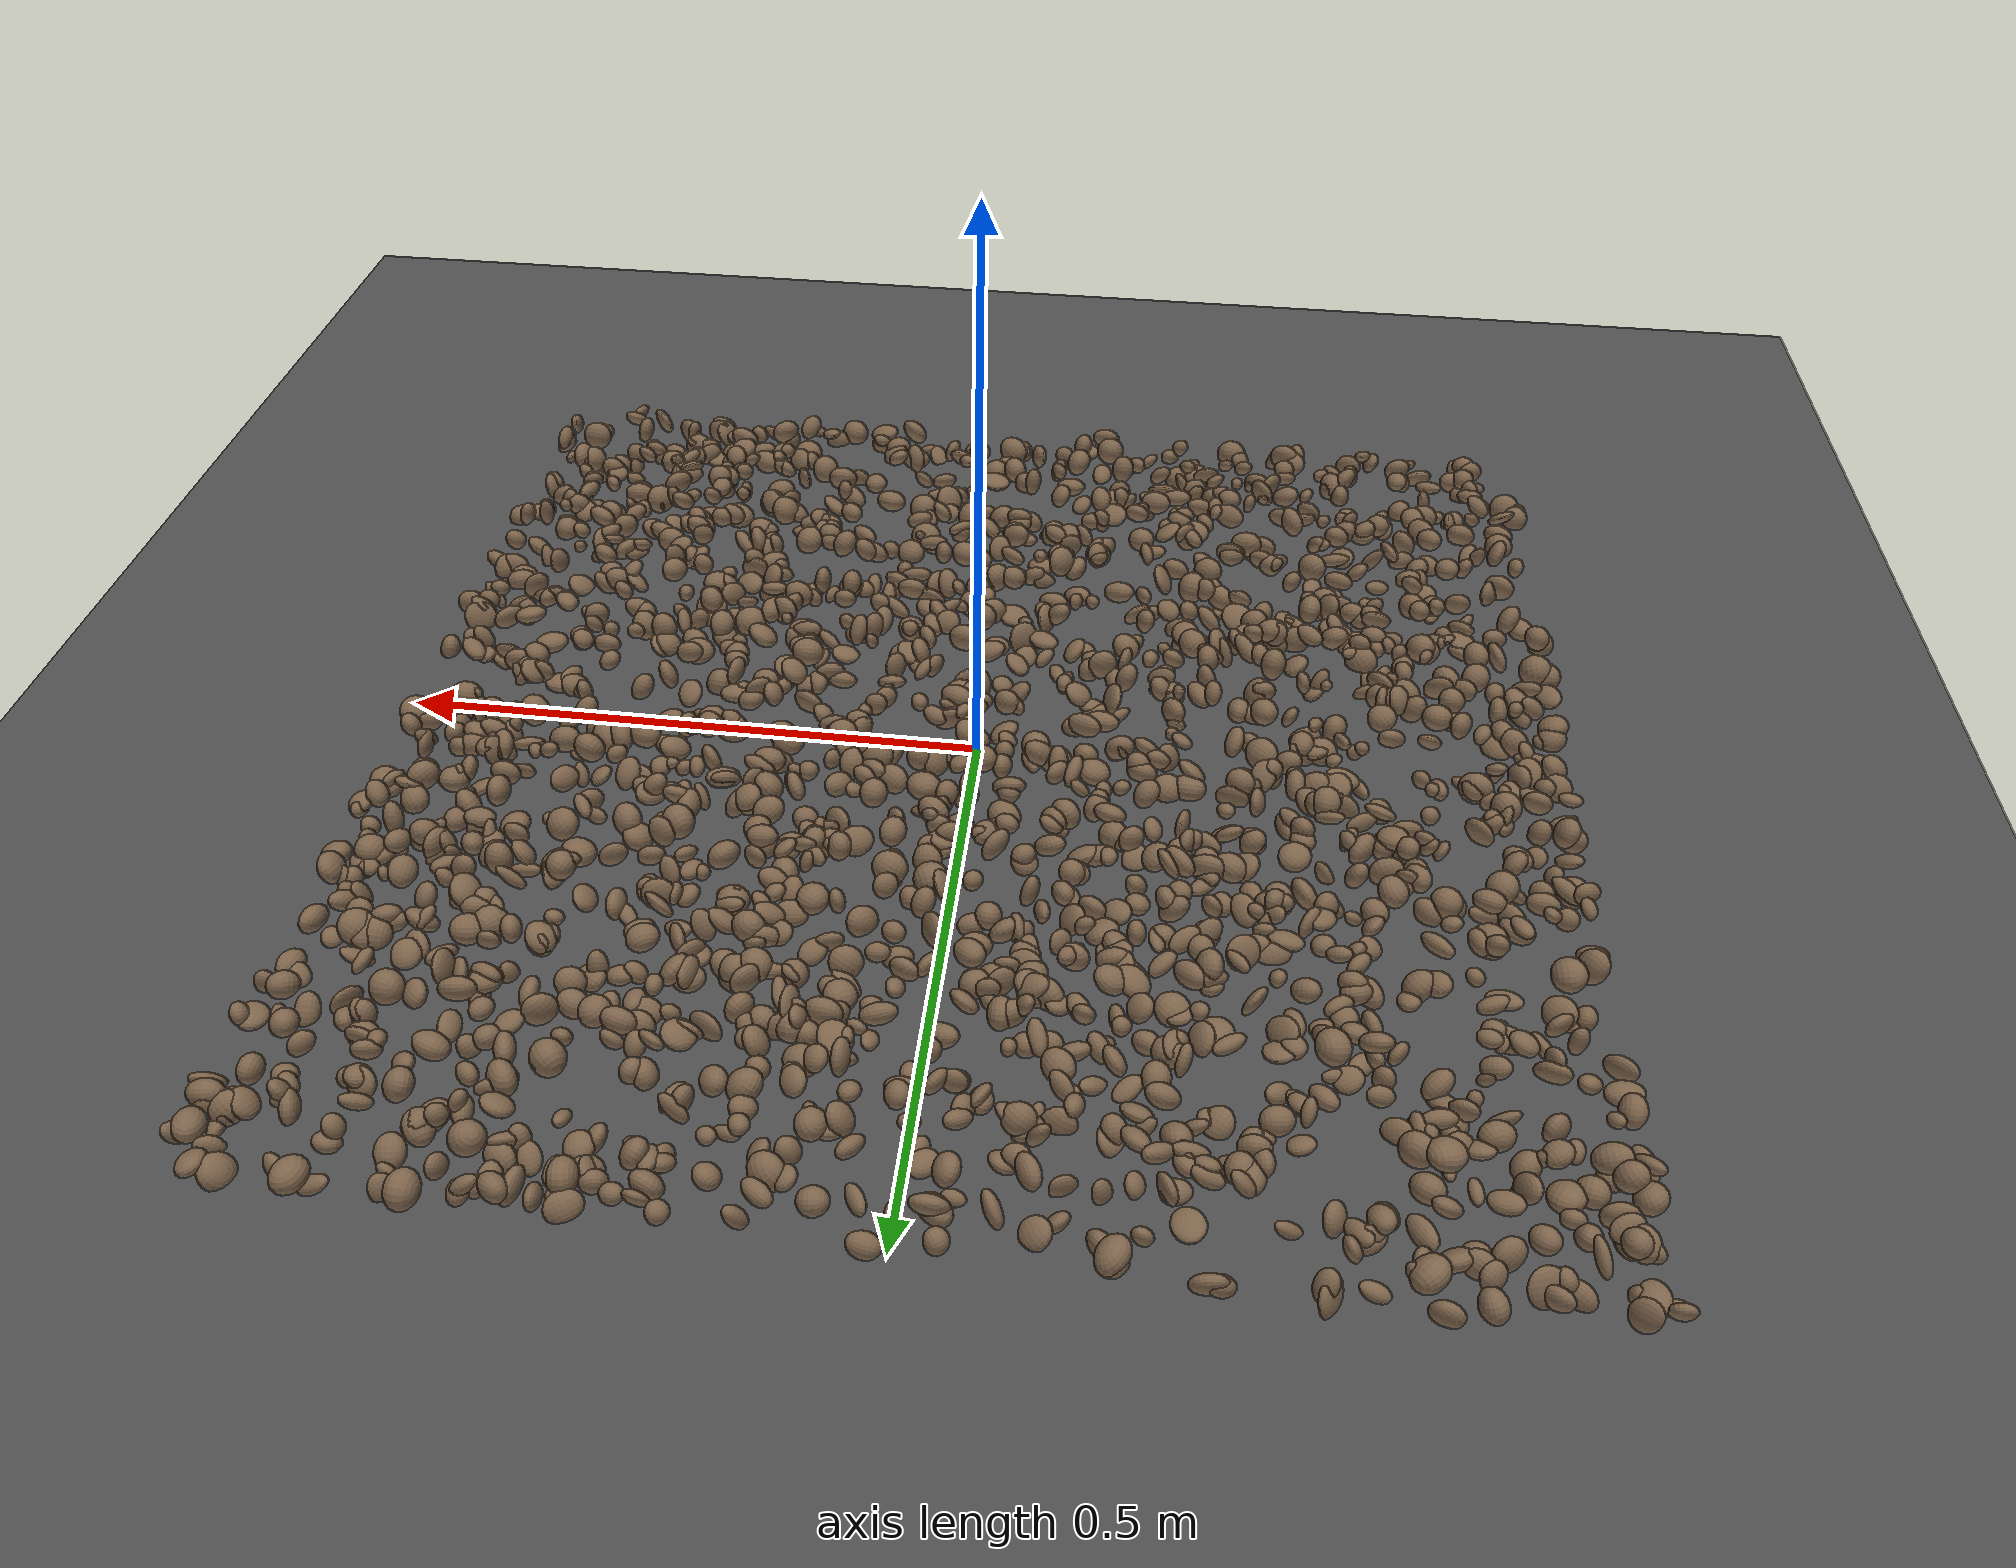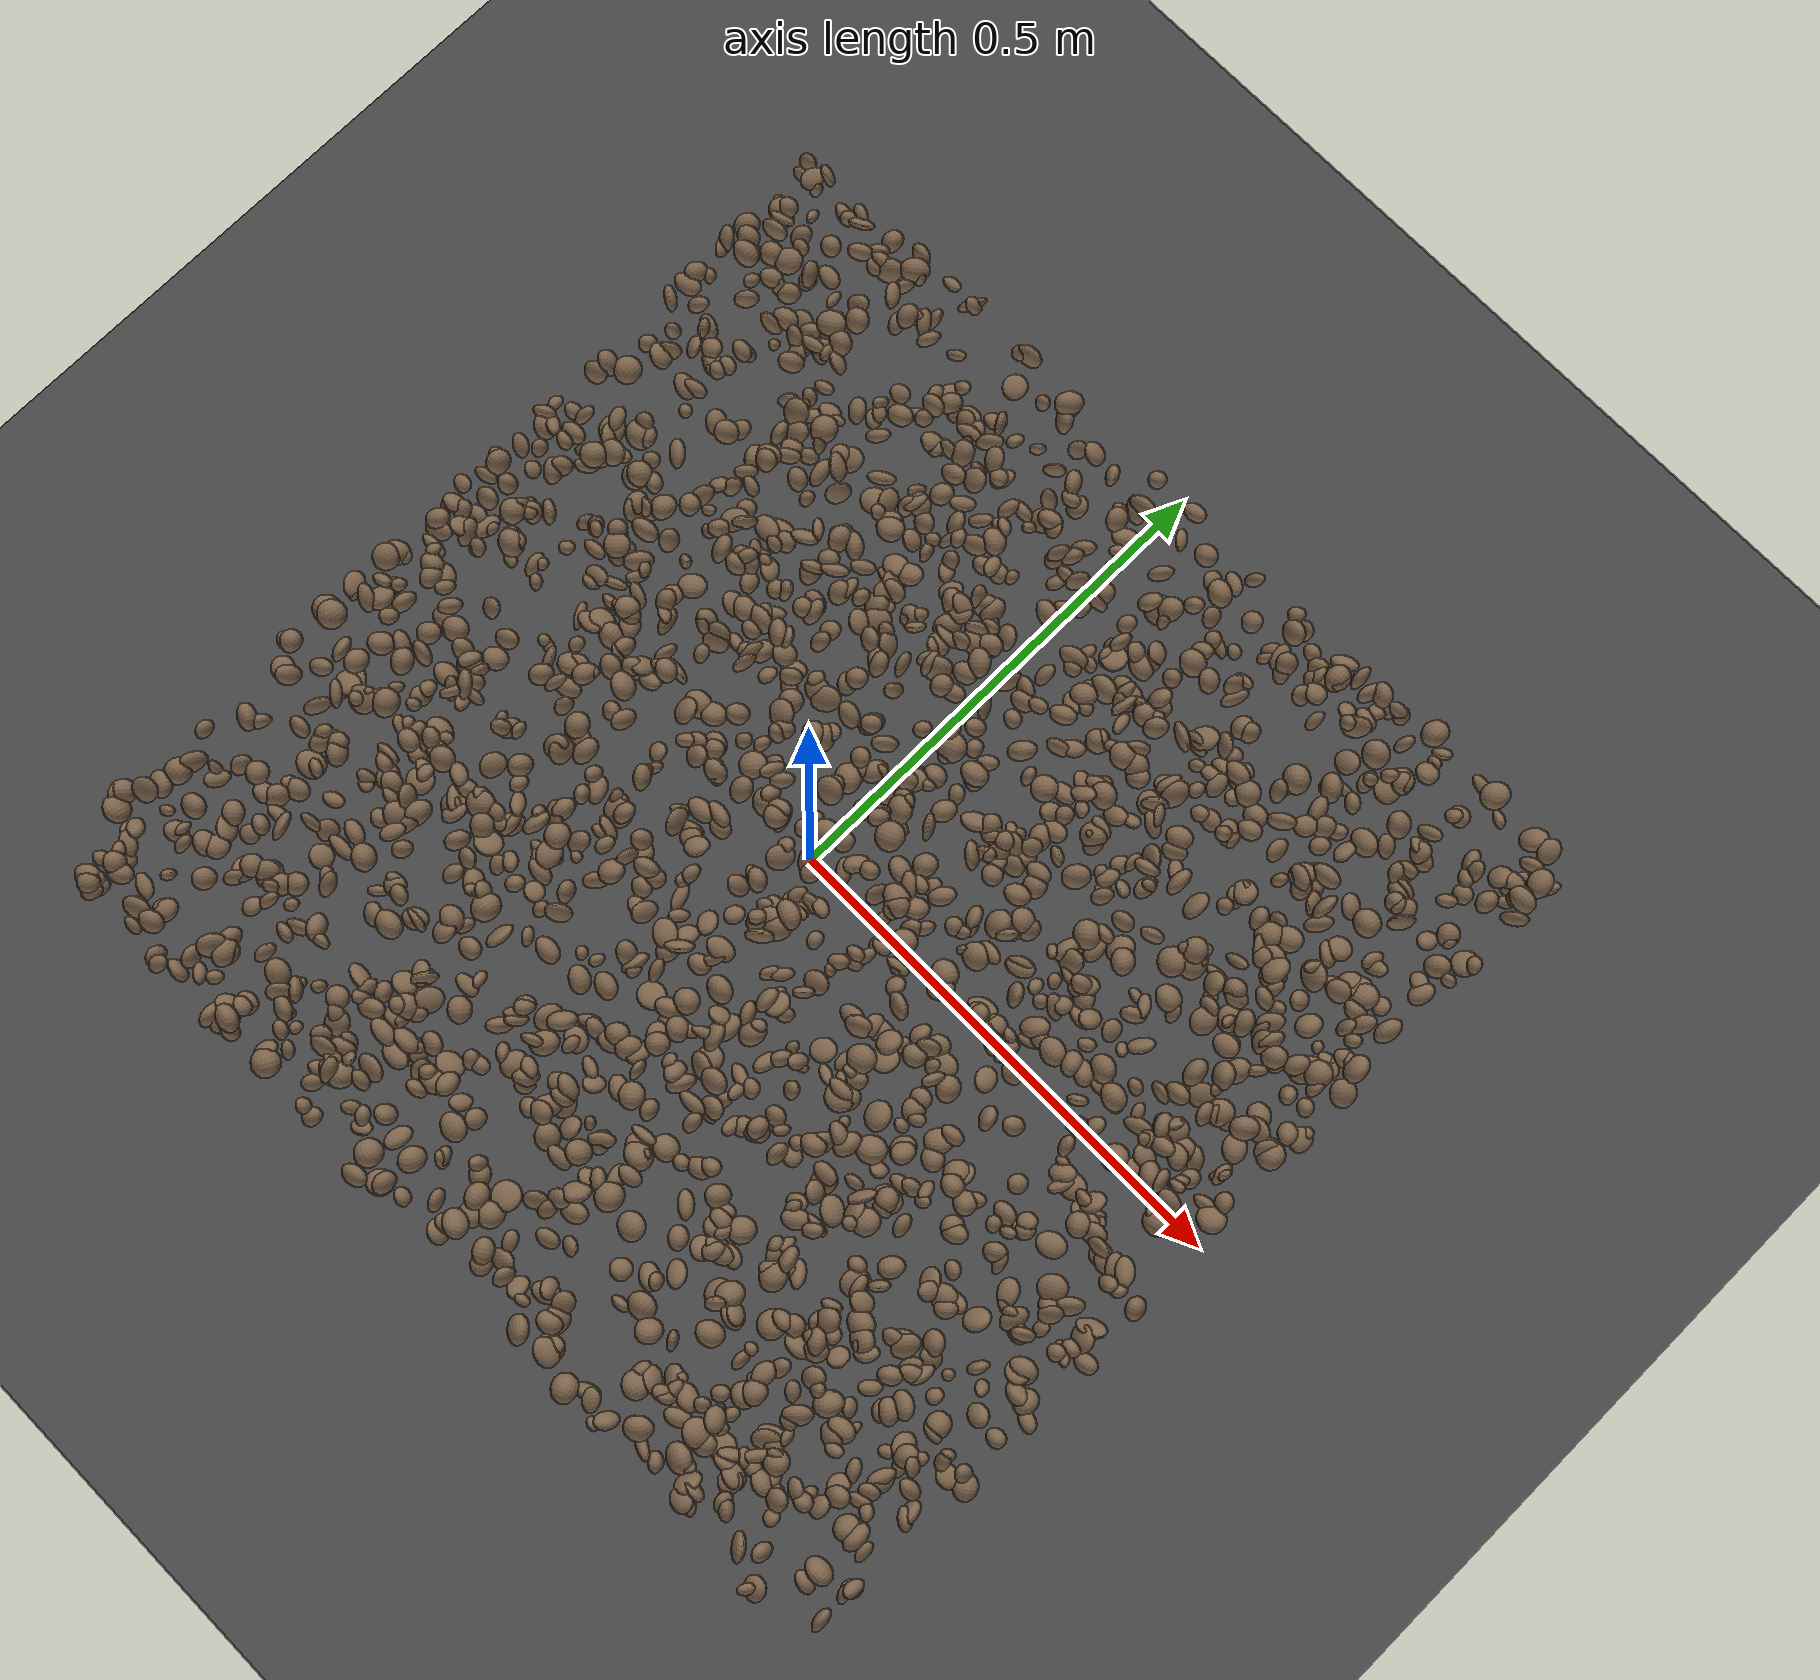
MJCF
<mujoco model="rocky_terrain_scene">
    <compiler angle="radian" inertiafromgeom="true" />
    <option timestep="0.002" gravity="0 0 -9.81" />

    <worldbody>
        <light name="sunlight" pos="5 5 5" dir="-1 -1 -1" diffuse="1 1 1" specular="0.5 0.5 0.5" ambient="0.5 0.5 0.5" />

        <geom name="ground_plane" type="plane" size="50 50 0.1" rgba="0.3 0.3 0.3 1" />

        <body name="rocky_terrain_body">

        <geom name="rock1" type="ellipsoid" size="0.006463762756427361 0.007817100008895593 0.013085788776764189" pos="-0.4669663714698755 0.2699553179050609 0.00796406471925884" quat="0.008563761346400394 0.32255551623304557 0.6565071651684249 0.01237355725212927" rgba="0.5 0.4 0.3 1" /><geom name="rock2" type="ellipsoid" size="0.010065013657122989 0.009679112724999231 0.005029732218371123" pos="-0.38622745882623377 0.07740071984325769 0.0005197202047790572" quat="0.2168632369071588 0.31107696565633386 0.04095602184202021 0.43110377559448715" rgba="0.5 0.4 0.3 1" /><geom name="rock3" type="ellipsoid" size="0.012889257620002707 0.013451087082175038 0.014072087093929053" pos="0.18884657059942656 -0.49330045442316395 0.0043171785271539104" quat="0.4323950703318 0.3886000058068583 0.13019592505316566 0.04880899880817608" rgba="0.5 0.4 0.3 1" /><geom name="rock4" type="ellipsoid" size="0.005796100262280741 0.008620366266227631 0.009677365341734809" pos="-0.3889546236026622 -0.18298471926522286 0.011573059995469896" quat="0.3907735487254145 0.2688426003734905 0.13863377495796123 0.2017500759431338" rgba="0.5 0.4 0.3 1" /><geom name="rock5" type="ellipsoid" size="0.014330095025849306 0.011492881786098974 0.014586947452084907" pos="0.036660951267590836 0.06630221351394416 0.014304857007265602" quat="0.35786984621610024 0.4739582410990513 0.05748081320275044 0.11069109948209795" rgba="0.5 0.4 0.3 1" /><geom name="rock6" type="ellipsoid" size="0.005637183048038497 0.013841386759670043 0.011934515860740354" pos="-0.13542159133640774 0.24304201768321732 0.011368017227612026" quat="0.17473357820532145 0.49835137146234887 0.01621978351045279 0.3106952668218768" rgba="0.5 0.4 0.3 1" /><geom name="rock7" type="ellipsoid" size="0.013233861267770645 0.014690836709046064 0.010921681037408437" pos="0.16514303933852237 0.07971584324170933 0.011892040775106147" quat="0.18875759983958815 0.10813550288895377 0.5152879032126944 0.18781899405876376" rgba="0.5 0.4 0.3 1" /><geom name="rock8" type="ellipsoid" size="0.005339818210617051 0.007474680726275601 0.008239791476724953" pos="0.05053263784330442 0.3191361184852063 0.005395501582346131" quat="0.37983162987075514 0.20163298300412644 0.24165348729434516 0.17688189983077326" rgba="0.5 0.4 0.3 1" /><geom name="rock9" type="ellipsoid" size="0.00715424355640827 0.014946703662649614 0.007884478416696861" pos="-0.3471217427143416 -0.2425386988291991 0.0014142403059779589" quat="0.2974473626481298 0.19653787258319935 0.18871681331377865 0.3172979514548921" rgba="0.5 0.4 0.3 1" /><geom name="rock10" type="ellipsoid" size="0.006652229779222403 0.010139663679482665 0.011994020974212899" pos="0.47284085799005293 0.475339724118118 0.0004909607303631868" quat="0.2815551739088114 0.13439799163948668 0.16303763509006722 0.4210091993616346" rgba="0.5 0.4 0.3 1" /><geom name="rock11" type="ellipsoid" size="0.014337767605400644 0.00836442444248612 0.005910419038048829" pos="-0.18289152502977446 0.21123643684777316 0.01299289899556884" quat="0.2577833337733184 0.512833913320616 0.224061842062331 0.005320910843734589" rgba="0.5 0.4 0.3 1" /><geom name="rock12" type="ellipsoid" size="0.012052199068033726 0.010771928966082409 0.010289988767197673" pos="-0.007866607825446459 -0.24120283587991187 0.010647851757496326" quat="0.13591965715953916 0.5514143371146136 0.08689517138541147 0.22577083434043582" rgba="0.5 0.4 0.3 1" /><geom name="rock13" type="ellipsoid" size="0.005535810987480124 0.01208619208205157 0.006969383903636693" pos="-0.33916875057889395 -0.12783120336244558 0.003309283410125723" quat="0.0507118693763092 0.40303167372957494 0.19552912685720714 0.35072733003690865" rgba="0.5 0.4 0.3 1" /><geom name="rock14" type="ellipsoid" size="0.00589305366837234 0.01007735182209284 0.009397926591485986" pos="-0.04050056428370585 0.2772738709824477 0.01192778531743002" quat="0.19987809425082986 0.24935005960919868 0.2988830163974923 0.2518888297424791" rgba="0.5 0.4 0.3 1" /><geom name="rock15" type="ellipsoid" size="0.009463523229472423 0.009316709249885029 0.012696407775668373" pos="0.15784804482467374 0.13995384269504063 0.012738486597498695" quat="0.3558471810469801 0.13416907558789345 0.36431588786382973 0.14566785550129663" rgba="0.5 0.4 0.3 1" /><geom name="rock16" type="ellipsoid" size="0.0073285123437942315 0.0128581101719662 0.005685813653993886" pos="-0.4631696020669446 0.14863800349871858 0.01109716832273347" quat="0.13356097178232015 0.14642049315946787 0.5326447965725352 0.18737373848567684" rgba="0.5 0.4 0.3 1" /><geom name="rock17" type="ellipsoid" size="0.011308754425135768 0.007258897104162337 0.011828345138288657" pos="-0.4266463363351346 -0.25413495894573856 0.007988155028088067" quat="0.09105021599871599 0.6951591697354138 0.011203711598627954 0.20258690266724225" rgba="0.5 0.4 0.3 1" /><geom name="rock18" type="ellipsoid" size="0.01107642855264024 0.009392918462885775 0.005339370497548097" pos="-0.26679685669885567 -0.06383772327791404 0.01180616246935953" quat="0.18947068525378907 0.33048932266449227 0.018538830161279198 0.4615011619204394" rgba="0.5 0.4 0.3 1" /><geom name="rock19" type="ellipsoid" size="0.005925969385564734 0.013017366750280063 0.005981743639366314" pos="0.11183380153269507 0.2977187304979958 0.009786992327619754" quat="0.015857010416173663 0.36782874829621526 0.12841694639056336 0.4878972948970476" rgba="0.5 0.4 0.3 1" /><geom name="rock20" type="ellipsoid" size="0.014955494658895875 0.00820442873563296 0.006491610702426338" pos="-0.32083603120679727 0.30100148904242774 0.004761259996869026" quat="0.048277392038484836 0.3634559091173174 0.2508187544874801 0.33744794435671766" rgba="0.5 0.4 0.3 1" /><geom name="rock21" type="ellipsoid" size="0.009247963117512683 0.010695928007921102 0.009179434462735272" pos="0.08902860404552548 0.36351034296014906 2.2681911601746263e-06" quat="0.27683238555442047 0.2569355059632027 0.17338520875989308 0.29284689972248373" rgba="0.5 0.4 0.3 1" /><geom name="rock22" type="ellipsoid" size="0.006526055990345829 0.013584019781347705 0.014661390487652925" pos="0.008750968655157454 0.3698294056939656 0.0026639492812195343" quat="0.2642750816766205 0.254559902646179 0.22370789297745874 0.25745712269974175" rgba="0.5 0.4 0.3 1" /><geom name="rock23" type="ellipsoid" size="0.009311162059163186 0.010791502490652163 0.013547107620572419" pos="-0.16171624745721547 -0.2831170269543437 0.003424542994727677" quat="0.42136366048496965 0.08871349967687861 0.20641897592145697 0.2835038639166947" rgba="0.5 0.4 0.3 1" /><geom name="rock24" type="ellipsoid" size="0.008976640890127419 0.005440057917401827 0.007894235856104399" pos="0.36188386558383046 -0.39966040420902404 0.013508314320437805" quat="0.0374662954872333 0.4301689227904234 0.15635081400010595 0.37601396772223733" rgba="0.5 0.4 0.3 1" /><geom name="rock25" type="ellipsoid" size="0.013295865104223314 0.011647413331176056 0.012888738819650254" pos="0.10488709893027282 0.201657333093621 0.010719577724413107" quat="0.35710324431977164 0.316153464614242 0.20907582919871248 0.11766746186727393" rgba="0.5 0.4 0.3 1" /><geom name="rock26" type="ellipsoid" size="0.006440755625172209 0.012282494408384945 0.010146827389432386" pos="0.4209954180487798 -0.40252555618519215 0.005357259918226543" quat="0.5394602545596048 0.18716364128742943 0.24521007701865066 0.028166027134315232" rgba="0.5 0.4 0.3 1" /><geom name="rock27" type="ellipsoid" size="0.006583748039894168 0.0055177503281078 0.009697307010214762" pos="-0.30213923253793296 -0.3319734664386419 0.012310769432170746" quat="0.3237674458306353 0.38739227642486723 0.23324937089835693 0.05559090684614051" rgba="0.5 0.4 0.3 1" /><geom name="rock28" type="ellipsoid" size="0.011458666712517055 0.005567966330111655 0.005213332013847823" pos="-0.2233730724217896 0.22800203167609112 0.012886971101791107" quat="0.16633223990835094 0.12217592560785734 0.361992236571094 0.34949959791269763" rgba="0.5 0.4 0.3 1" /><geom name="rock29" type="ellipsoid" size="0.007249509703553934 0.006354870555660379 0.005786566674309014" pos="-0.3051091254603814 -0.3730129891035797 0.011940497448603645" quat="0.32364811805618693 0.31377718963152446 0.10476362040525994 0.2578110719070288" rgba="0.5 0.4 0.3 1" /><geom name="rock30" type="ellipsoid" size="0.01217060206509455 0.008291044221650085 0.011087619643056427" pos="-0.48234092783075055 -0.226837856041593 0.003732711639357847" quat="0.19485778845344257 0.1670783016075488 0.35109883556607896 0.28696507437292973" rgba="0.5 0.4 0.3 1" /><geom name="rock31" type="ellipsoid" size="0.013910911711589459 0.005877771410218189 0.012104249781415864" pos="-0.17978331611831389 0.28066734737217147 0.009635524251943377" quat="0.19220541489983167 0.2613386470394839 0.2548334239922936 0.2916225140683909" rgba="0.5 0.4 0.3 1" /><geom name="rock32" type="ellipsoid" size="0.00909903712286453 0.014417972389715723 0.005222423400460491" pos="0.0548703265656425 0.09945605388288314 0.00647679641837526" quat="0.350048653818048 0.03875427242597403 0.3750355641873917 0.23616150956858623" rgba="0.5 0.4 0.3 1" /><geom name="rock33" type="ellipsoid" size="0.007127302516061619 0.005048868419679198 0.00932378366185218" pos="-0.26589716347955206 0.35255478700350473 0.011093936469475731" quat="0.3493320850209079 0.3552828940275182 0.20894283072116068 0.08644219023041319" rgba="0.5 0.4 0.3 1" /><geom name="rock34" type="ellipsoid" size="0.013941458025856529 0.010604640683907008 0.005401588709848716" pos="-0.4427942239380055 0.274940195765614 0.0022476623922870996" quat="0.2395875875254008 0.08798826384548628 0.4964016598083859 0.17602248882072702" rgba="0.5 0.4 0.3 1" /><geom name="rock35" type="ellipsoid" size="0.012839261622988214 0.013943203482972837 0.005047162874967786" pos="-0.23525398611298254 0.26669163887502967 0.014205346047977647" quat="0.39115457665610703 0.2570069013171436 0.16229311648893263 0.18954540553781676" rgba="0.5 0.4 0.3 1" /><geom name="rock36" type="ellipsoid" size="0.008613346920495696 0.011540805673199477 0.0069284548158666075" pos="-0.3267973606618877 0.3181631074792266 0.0034541039566126606" quat="0.1469183945573578 0.09934012530431796 0.37346951495007275 0.3802719651882514" rgba="0.5 0.4 0.3 1" /><geom name="rock37" type="ellipsoid" size="0.013086592041421083 0.013162456748573845 0.00555139996753134" pos="-0.1278537018260666 -0.20207174131093975 0.006964157914303786" quat="0.5256639658846737 0.267243155325698 0.2000761868594035 0.007016691930224762" rgba="0.5 0.4 0.3 1" /><geom name="rock38" type="ellipsoid" size="0.012457107237710787 0.013593395376844553 0.011608484287625401" pos="-0.3164169771861397 -0.4458245955907377 0.004193713858155611" quat="0.34231638049334207 0.20490246299267678 0.23881343854075857 0.2139677179732226" rgba="0.5 0.4 0.3 1" /><geom name="rock39" type="ellipsoid" size="0.013011262864933572 0.009579313842596623 0.005896449105849776" pos="0.2388316195962934 0.49089112024037806 0.008260624607115241" quat="0.15102817939636842 0.32849357144328545 0.16581414241908113 0.3546641067412651" rgba="0.5 0.4 0.3 1" /><geom name="rock40" type="ellipsoid" size="0.007144628351690854 0.01030884664251405 0.010499081520283865" pos="-0.34132051113763084 0.07583688581896375 0.003566571347788692" quat="0.035970605921766687 0.5721103259055208 0.14398349789939227 0.24793557027332036" rgba="0.5 0.4 0.3 1" /><geom name="rock41" type="ellipsoid" size="0.007533178860461473 0.01212008635666307 0.014242480896042999" pos="-0.4565481469571241 -0.011484900888642291 0.008583947906394445" quat="0.31686354100669284 0.5329515307403736 0.0601749834049753 0.09000994484795831" rgba="0.5 0.4 0.3 1" /><geom name="rock42" type="ellipsoid" size="0.01067203763200995 0.009394614318866908 0.00536083623924649" pos="0.13634833549566128 0.1526993241398913 0.013980728053235815" quat="0.5708780241315785 0.0984560371223757 0.18442986692946695 0.1462360718165788" rgba="0.5 0.4 0.3 1" /><geom name="rock43" type="ellipsoid" size="0.010395396583373281 0.012160624145405256 0.013862049457418407" pos="-0.0975760191535211 0.33991238975271565 0.009835507921017207" quat="0.30359814067273533 0.3719767241363607 0.008416784820199101 0.3160083503707049" rgba="0.5 0.4 0.3 1" /><geom name="rock44" type="ellipsoid" size="0.008329050029435733 0.009939370510624754 0.014610995520167546" pos="0.03567187058691301 0.3112827223943082 0.012912757190802688" quat="0.2701723395792262 0.16241065342587152 0.3691198315784969 0.19829717541640535" rgba="0.5 0.4 0.3 1" /><geom name="rock45" type="ellipsoid" size="0.01326684627773628 0.00669380752367951 0.007721617580468043" pos="-0.29704470385544635 0.2597590936575711 0.010065864277666934" quat="0.17278633063307572 0.5840405541105513 0.20351283627070943 0.039660278985663544" rgba="0.5 0.4 0.3 1" /><geom name="rock46" type="ellipsoid" size="0.012254812579539608 0.005959390006316818 0.005289829319667884" pos="0.3941600718272902 -0.33812888108187567 0.0017636909038948178" quat="0.2427694849415766 0.2864644668424208 0.22384798456975338 0.24691806364624933" rgba="0.5 0.4 0.3 1" /><geom name="rock47" type="ellipsoid" size="0.00965848746981793 0.01360651826503724 0.005661570965429701" pos="-0.2769510714139245 0.18262477238287322 0.014149018835325886" quat="0.22482663895493463 0.4100073797597887 0.0019017657318360567 0.3632642155534406" rgba="0.5 0.4 0.3 1" /><geom name="rock48" type="ellipsoid" size="0.005315354500479069 0.010085326837798612 0.00768640845831093" pos="0.419146804200504 -0.1626086570705504 0.008650042499159858" quat="0.14018333263248803 0.3033416314063023 0.41845769924859044 0.13801733671261918" rgba="0.5 0.4 0.3 1" /><geom name="rock49" type="ellipsoid" size="0.014238999428426505 0.008441194061452748 0.007693274446530366" pos="-0.09871545325047781 0.23281853915166484 0.00946550249302953" quat="0.42729548033815645 0.2535087984253951 0.04779095825605817 0.2714047629803904" rgba="0.5 0.4 0.3 1" /><geom name="rock50" type="ellipsoid" size="0.008326623034469535 0.007931318892309323 0.005172912829832376" pos="0.04337340979172821 -0.22423143027046122 0.007164304621640586" quat="0.1073800194781577 0.37027264608651156 0.309837809674079 0.2125095247612518" rgba="0.5 0.4 0.3 1" /><geom name="rock51" type="ellipsoid" size="0.005598207008125633 0.012497916874058011 0.013674731954826574" pos="0.3465599223346437 -0.39603300432593314 0.009320855975022862" quat="0.306035348363088 0.014325956853913127 0.38760912539056 0.29202956939243885" rgba="0.5 0.4 0.3 1" /><geom name="rock52" type="ellipsoid" size="0.011303107706189596 0.005982005439431053 0.014890260934560012" pos="0.20951208137741917 0.014136500058372858 0.013312829909134613" quat="0.355410807896338 0.10799491842476955 0.3097063102061338 0.2268879634727587" rgba="0.5 0.4 0.3 1" /><geom name="rock53" type="ellipsoid" size="0.012432176999275171 0.014801256220527855 0.006912672825659312" pos="-0.14620705428706215 0.255685022464219 0.01068012382893707" quat="0.12941956436154844 0.5033365778359951 0.3048960196140224 0.06234783818843404" rgba="0.5 0.4 0.3 1" /><geom name="rock54" type="ellipsoid" size="0.011695706796293708 0.011135405570170655 0.013570010447840977" pos="-0.17495150593865905 0.3159716964206516 0.007236106870150495" quat="0.36838005381068206 0.21575054159224158 0.3576158459920613 0.05825355860501504" rgba="0.5 0.4 0.3 1" /><geom name="rock55" type="ellipsoid" size="0.01399438644113125 0.009558904238632314 0.006309884608109334" pos="-0.26100953165888363 0.06420582987658763 0.0009594286786265338" quat="0.23655214770568375 0.1972044234678406 0.25267502242831 0.31356840639816563" rgba="0.5 0.4 0.3 1" /><geom name="rock56" type="ellipsoid" size="0.007979799141576835 0.007716524853316924 0.009095119626905339" pos="0.1895718528543242 0.4783808270185347 0.0027964015279792623" quat="0.412083457612343 0.09585270946261405 0.48348819066261955 0.008575642262423326" rgba="0.5 0.4 0.3 1" /><geom name="rock57" type="ellipsoid" size="0.013053898544421634 0.014700673699192764 0.011981215037034039" pos="-0.3870226844165501 -0.18042104794482894 0.008836342731187857" quat="0.4619849505445483 0.07418099999877137 0.28331367331876134 0.18052037613791902" rgba="0.5 0.4 0.3 1" /><geom name="rock58" type="ellipsoid" size="0.006637552001927681 0.005869880471224508 0.012099067859908814" pos="-0.19939466493209712 0.09596262906622433 0.005909032284053672" quat="0.487483225390962 0.15833396621283952 0.25314869049359495 0.10103411790260353" rgba="0.5 0.4 0.3 1" /><geom name="rock59" type="ellipsoid" size="0.012345519754296696 0.005194860830874564 0.006177100910398459" pos="0.058591045434046585 -0.09481410169023963 0.00851684518133078" quat="0.34870349621611124 0.3115025742753471 0.2497233796305371 0.09007054987800457" rgba="0.5 0.4 0.3 1" /><geom name="rock60" type="ellipsoid" size="0.01006091795833356 0.013064133121805516 0.01057888384500423" pos="-0.1663648555169127 0.20085499233186666 0.0028804939381057377" quat="0.3078536679336344 0.12065430888981114 0.3868299903866153 0.18466203278993923" rgba="0.5 0.4 0.3 1" /><geom name="rock61" type="ellipsoid" size="0.011744571435786715 0.008160532667226585 0.011935410609679141" pos="-0.003540497835560985 -0.33982344346310944 0.014141833172123447" quat="0.15091962560928013 0.3382322441208595 0.13028029794426377 0.3805678323255965" rgba="0.5 0.4 0.3 1" /><geom name="rock62" type="ellipsoid" size="0.00991183342031033 0.014367252862394066 0.005502832987470852" pos="-0.11013191515686849 -0.3917922212878735 0.005746123769246683" quat="0.41487423432093445 0.1931818140589503 0.211995354528107 0.1799485970920082" rgba="0.5 0.4 0.3 1" /><geom name="rock63" type="ellipsoid" size="0.0084242303493502 0.006367795846551093 0.010206431968659694" pos="0.1784852997039258 -0.36988633369268387 0.01185953245080978" quat="0.0396163406818743 0.3114568792989818 0.5950081759661721 0.05391860405297182" rgba="0.5 0.4 0.3 1" /><geom name="rock64" type="ellipsoid" size="0.011878723650450413 0.009449213666401357 0.008053359093110581" pos="-0.406712699356073 0.17846336501818083 0.004831702969935137" quat="0.22406528681826274 0.1304961858706039 0.3726293044955779 0.2728092228155553" rgba="0.5 0.4 0.3 1" /><geom name="rock65" type="ellipsoid" size="0.013082693210155795 0.009223676702744269 0.010901296988686582" pos="0.2525597364104667 -0.131289192363089 0.013463210707522757" quat="0.38464310994462386 0.0964685081114337 0.27078649765400215 0.24810188428994032" rgba="0.5 0.4 0.3 1" /><geom name="rock66" type="ellipsoid" size="0.012740169478863084 0.011692668385526416 0.005963420488407137" pos="-0.4562136395737789 0.25383493790130907 0.004799094227748673" quat="0.3768073982640473 0.3542575265483527 0.03262821451244601 0.23630686067515402" rgba="0.5 0.4 0.3 1" /><geom name="rock67" type="ellipsoid" size="0.010647473738081434 0.013693700782789683 0.006357808302527037" pos="-0.41473653286261714 0.4047004460121324 0.011787686262259987" quat="0.38910820479075836 0.07700944222449373 0.30789272482481694 0.2259896281599309" rgba="0.5 0.4 0.3 1" /><geom name="rock68" type="ellipsoid" size="0.005380510849987328 0.005693202969942969 0.012783492808580663" pos="-0.25829119406161294 0.4502904974297661 0.0021453601805499606" quat="0.11414100143391115 0.23023707931173584 0.11664077635242794 0.5389811429019251" rgba="0.5 0.4 0.3 1" /><geom name="rock69" type="ellipsoid" size="0.010231122169054422 0.005173121607668315 0.009523436774573488" pos="-0.30955194163001676 0.45234590068376745 0.006408788175466711" quat="0.6152638539934876 0.08940171343278044 0.21923105898163095 0.0761033735921011" rgba="0.5 0.4 0.3 1" /><geom name="rock70" type="ellipsoid" size="0.007487587058281855 0.007571748877447255 0.00993385949276078" pos="0.05052891156621475 0.1410659548082409 0.0017095661189754296" quat="0.3070978135588012 0.4229885225689555 0.19445370062891645 0.0754599632433269" rgba="0.5 0.4 0.3 1" /><geom name="rock71" type="ellipsoid" size="0.0065275762947855686 0.007298434588888387 0.006214933578714289" pos="0.19710305008316686 0.1828405882032118 0.009259526571222625" quat="0.35191893797583074 0.15880108385597497 0.34786473456473155 0.14141524360346275" rgba="0.5 0.4 0.3 1" /><geom name="rock72" type="ellipsoid" size="0.014900943977509289 0.012172381157850399 0.011156183278370618" pos="-0.07094523346401749 0.250540545915406 0.0016492164665858043" quat="0.3839614052446115 0.26668217733513305 0.0021969411356672574 0.3471594762845882" rgba="0.5 0.4 0.3 1" /><geom name="rock73" type="ellipsoid" size="0.007869236284728576 0.008920821348455238 0.008431997525744072" pos="0.48007408735289514 0.15989925771825042 0.004304726303215953" quat="0.569998043155641 0.09018129094550638 0.09085982320339994 0.24896084269545274" rgba="0.5 0.4 0.3 1" /><geom name="rock74" type="ellipsoid" size="0.0055228692366835405 0.009937003684899373 0.0059458494664661795" pos="-0.08564059983286898 0.37755622174527015 1.2545831197434131e-05" quat="0.13574595307834803 0.14030101237107778 0.17728933776198033 0.5466636967885938" rgba="0.5 0.4 0.3 1" /><geom name="rock75" type="ellipsoid" size="0.0094484022288043 0.006997263601926319 0.012084379165224266" pos="0.08184556905992746 -0.4135733541708647 0.0025808875909432245" quat="0.10178880861890022 0.40005294530753266 0.17998066431725004 0.31817758175631705" rgba="0.5 0.4 0.3 1" /><geom name="rock76" type="ellipsoid" size="0.00852123904620079 0.009192472081155154 0.01270640790470131" pos="-0.4552245454103907 -0.2006567122042413 0.010018910631276379" quat="0.272108245598361 0.11314632013449419 0.24372111527927828 0.3710243189878666" rgba="0.5 0.4 0.3 1" /><geom name="rock77" type="ellipsoid" size="0.008936496546317714 0.012943855153122085 0.010251600789319828" pos="-0.4053225597305016 -0.3202790299486141 0.0018285454078157475" quat="0.012008155574454569 0.33861961572769156 0.35600713283157237 0.29336509586628157" rgba="0.5 0.4 0.3 1" /><geom name="rock78" type="ellipsoid" size="0.009382851933821792 0.00560958521870345 0.008950044471132432" pos="-0.014795802609704256 -0.3105924745721993 0.007729889852891928" quat="0.2528719050117172 0.3127352595773576 0.17093097534263932 0.26346186006828587" rgba="0.5 0.4 0.3 1" /><geom name="rock79" type="ellipsoid" size="0.010460969677468094 0.011950063705950538 0.005744043911059824" pos="0.28122162074358614 -0.3637650636888613 0.004909350782019109" quat="0.3044985247048344 0.1980361131725129 0.2714269515032795 0.22603841061937316" rgba="0.5 0.4 0.3 1" /><geom name="rock80" type="ellipsoid" size="0.008473482431045917 0.01113202273905135 0.006113487172596279" pos="-0.31254928700769724 0.20099430574942379 0.006795690304314088" quat="0.4654623614928874 0.2071574127322786 0.22431235776667827 0.10306786800815573" rgba="0.5 0.4 0.3 1" /><geom name="rock81" type="ellipsoid" size="0.013194435197299511 0.006309627460036831 0.014135069234486698" pos="-0.18389810470624812 0.01512221655479451 0.009186737383145285" quat="0.24061449836557222 0.04753075192213851 0.2177106965321994 0.4941440531800898" rgba="0.5 0.4 0.3 1" /><geom name="rock82" type="ellipsoid" size="0.010161665001208096 0.005780115102329527 0.0066987564127352316" pos="0.2259907696582818 0.4859316686536359 0.004228451530124384" quat="0.1889935331335679 0.2871536335720334 0.29655614864269064 0.22729668465170805" rgba="0.5 0.4 0.3 1" /><geom name="rock83" type="ellipsoid" size="0.012174380984121519 0.010719644130271468 0.005378006500147184" pos="-0.1340541074157402 0.22973667729735014 0.01328010516858627" quat="0.45834479127313177 0.08405541493607442 0.04839946199889782 0.40920033179189597" rgba="0.5 0.4 0.3 1" /><geom name="rock84" type="ellipsoid" size="0.013810785203808771 0.005144423167606053 0.012426526755435069" pos="-0.4810617673839941 -0.39751632684039684 0.014016210691312593" quat="0.02960150076539953 0.2862734739368179 0.2633238851466899 0.42080114015109255" rgba="0.5 0.4 0.3 1" /><geom name="rock85" type="ellipsoid" size="0.007699049731392949 0.014658553854241911 0.008621441510676599" pos="-0.25944591651750715 -0.4924561564571206 0.004883122051893996" quat="0.22386453525677094 0.051657465471849406 0.3676147866368734 0.35686321263450627" rgba="0.5 0.4 0.3 1" /><geom name="rock86" type="ellipsoid" size="0.00787009964692323 0.010118803023668643 0.011659598197964992" pos="-0.3640840369035421 0.3788619174828338 0.006990248600206028" quat="0.4252925244953217 0.23582984744858806 0.3009462427286333 0.037931385327457" rgba="0.5 0.4 0.3 1" /><geom name="rock87" type="ellipsoid" size="0.007717494722809965 0.01291570129321868 0.013812024017975127" pos="0.2516581583287486 -0.41795566167723464 0.002369517876491779" quat="0.4114744061465908 0.26988863689817794 0.2560840602212741 0.06255289673395725" rgba="0.5 0.4 0.3 1" /><geom name="rock88" type="ellipsoid" size="0.014342701491900652 0.008591950667893967 0.006281122999363473" pos="0.16876748430301258 0.3944798304251317 0.0012464729824447495" quat="0.29738374073413626 0.29643314185670483 0.18541548115015222 0.22076763625900664" rgba="0.5 0.4 0.3 1" /><geom name="rock89" type="ellipsoid" size="0.013785708624202305 0.011406525260857323 0.008975889247067149" pos="-0.48567914578123905 -0.022865326410313136 0.01256625689702121" quat="0.06830773687755282 0.5822700421980375 0.0906757270692666 0.2587464938551431" rgba="0.5 0.4 0.3 1" /><geom name="rock90" type="ellipsoid" size="0.005173208722994695 0.007062867650422779 0.009003720502462887" pos="0.3007468770095134 0.12388416483596443 0.003193356313396952" quat="0.2744240440952761 0.2847628335507939 0.1619705680529459 0.27884255430098415" rgba="0.5 0.4 0.3 1" /><geom name="rock91" type="ellipsoid" size="0.009954741922309133 0.007628062775815339 0.012419166191839207" pos="0.23159576477872712 0.24600495895434538 0.006161836675479296" quat="0.002544086624546916 0.4224409566936386 0.1842290434904254 0.390785913191389" rgba="0.5 0.4 0.3 1" /><geom name="rock92" type="ellipsoid" size="0.00744573930477647 0.01013334957930877 0.008897021935508292" pos="-0.13252420215757543 0.1010039024143462 0.0009540159027011208" quat="0.09845450314855989 0.4728988502626363 0.39807487204151965 0.030571774547284148" rgba="0.5 0.4 0.3 1" /><geom name="rock93" type="ellipsoid" size="0.007697545487812954 0.009541225575836419 0.008392274946900272" pos="0.28952469960461413 -0.39704616416075444 0.00835307444619226" quat="0.12405457508608692 0.1764219543898573 0.4914510673541422 0.20807240316991368" rgba="0.5 0.4 0.3 1" /><geom name="rock94" type="ellipsoid" size="0.014273194183131884 0.007567245454843495 0.013559324572522465" pos="0.43151290334074954 -0.12103159450857259 0.014997654317319593" quat="0.31097699932418865 0.4782575675085799 0.12970538126294623 0.08106005190428528" rgba="0.5 0.4 0.3 1" /><geom name="rock95" type="ellipsoid" size="0.0052559423568427745 0.005080744457782722 0.008613580946725917" pos="0.08670319606063104 -0.06075403679832836 0.007218504938380097" quat="0.03928922992619266 0.7916168967808673 0.0545070843327722 0.11458678896016776" rgba="0.5 0.4 0.3 1" /><geom name="rock96" type="ellipsoid" size="0.006589510320359257 0.00925296658552498 0.007490769700020288" pos="0.0008012028204321675 -0.06054794500485228 0.004783215148921402" quat="0.1902996721259075 0.24923761259415114 0.4002075506469404 0.16025516463300088" rgba="0.5 0.4 0.3 1" /><geom name="rock97" type="ellipsoid" size="0.009045731152231035 0.013402805864412556 0.011749275387354017" pos="-0.17566953989263645 -0.4286647477837018 0.0020143790969757306" quat="0.2818276723442754 0.10575584840773938 0.23090948241353915 0.3815069968344461" rgba="0.5 0.4 0.3 1" /><geom name="rock98" type="ellipsoid" size="0.011162624036864827 0.012465129612596125 0.00994045596060131" pos="0.1582111743673671 0.272677757901682 0.006535351727684842" quat="0.21296810582016715 0.4134784498796002 0.31054806069213303 0.06300538360809953" rgba="0.5 0.4 0.3 1" /><geom name="rock99" type="ellipsoid" size="0.009186373318413248 0.007800652939736403 0.009678467439305952" pos="-0.2880993315399023 0.1955905842124811 0.0040139936781899335" quat="0.051934567397313926 0.17513740873379283 0.3790424186387428 0.3938856052301506" rgba="0.5 0.4 0.3 1" /><geom name="rock100" type="ellipsoid" size="0.005751602691450426 0.013186684629519524 0.009711114961756282" pos="-0.26391225280032704 -0.37645189203105867 0.010759872357730476" quat="0.11282749003004766 0.4001250767093402 0.4180340560159772 0.06901337724463483" rgba="0.5 0.4 0.3 1" /><geom name="rock101" type="ellipsoid" size="0.010118405368878633 0.013385872385290133 0.013155714501316942" pos="-0.29428856285916627 -0.02973868770696242 0.0032350525852399776" quat="0.028706176215393425 0.32755731402963234 0.2649713882646058 0.3787651214903684" rgba="0.5 0.4 0.3 1" /><geom name="rock102" type="ellipsoid" size="0.006815654268208805 0.00932743675852617 0.0065773534465388235" pos="-0.4533096884053942 0.36315197900295915 0.0014705976706055129" quat="0.13530130719071165 0.42982860045398663 0.06099648962321883 0.3738736027320828" rgba="0.5 0.4 0.3 1" /><geom name="rock103" type="ellipsoid" size="0.007407277476585608 0.013315797921811447 0.011451068313282872" pos="0.02483469876098021 0.25878765043899343 0.0040492063997040915" quat="0.48836136831457816 0.09250226109821329 0.12438880202595018 0.29474756856125844" rgba="0.5 0.4 0.3 1" /><geom name="rock104" type="ellipsoid" size="0.011808294442882554 0.011755166309803975 0.014221826755799156" pos="0.24537699163627058 -0.36752291098824474 0.006284007789943678" quat="0.17602683511613515 0.23435470205373093 0.3714771711889953 0.21814129164113857" rgba="0.5 0.4 0.3 1" /><geom name="rock105" type="ellipsoid" size="0.012519036289453278 0.00673948533555645 0.012697401997519392" pos="-0.138243697001317 0.39296901335507106 0.0006161356322360111" quat="0.3660056503746291 0.09018088808299334 0.19895166731478608 0.3448617942275914" rgba="0.5 0.4 0.3 1" /><geom name="rock106" type="ellipsoid" size="0.006776579166208352 0.012570570938025886 0.012891748250182477" pos="-0.1793095127192893 -0.3480342440267944 0.004758753239063741" quat="0.1425821303943526 0.37916609143463603 0.060215626483866566 0.41803615168714486" rgba="0.5 0.4 0.3 1" /><geom name="rock107" type="ellipsoid" size="0.014645624013785608 0.0071206878104605395 0.01173532900748086" pos="-0.022569177056035117 0.4652703616215247 0.009705302496537536" quat="0.14569276013015323 0.701105633448542 0.019277749678273986 0.1339238567430307" rgba="0.5 0.4 0.3 1" /><geom name="rock108" type="ellipsoid" size="0.013760794698722552 0.0054312511452220555 0.010328902497342054" pos="-0.3502649622420061 -0.1278275136764403 0.011322971168427447" quat="0.5303770381711576 0.06875882583520833 0.07281188796322897 0.32805224803040506" rgba="0.5 0.4 0.3 1" /><geom name="rock109" type="ellipsoid" size="0.010559096636216521 0.010448689856520348 0.011625278414585853" pos="0.05373251697148429 0.47331864370580656 0.011452486197785288" quat="0.2569410329975456 0.23068592171138394 0.3060836505649325 0.206289394726138" rgba="0.5 0.4 0.3 1" /><geom name="rock110" type="ellipsoid" size="0.011511435870329793 0.007149724525091838 0.006200939900033926" pos="-0.31951953751738005 -0.47699843308969725 0.002323004055336707" quat="0.20451976721492252 0.05109381245014413 0.39031309328657615 0.3540733270483572" rgba="0.5 0.4 0.3 1" /><geom name="rock111" type="ellipsoid" size="0.0121174943959747 0.010818086291564527 0.0063100880485486765" pos="0.47391242161265323 0.17997644559911552 0.005160545734492124" quat="0.3877813898928083 0.09410615616609629 0.44886161572307454 0.06925083821802094" rgba="0.5 0.4 0.3 1" /><geom name="rock112" type="ellipsoid" size="0.014611484320651558 0.008352496380726736 0.01411634712661048" pos="-0.0472652894349026 0.21309785408015447 0.007666959634210332" quat="0.06004868912946963 0.4650222352537458 0.23477406055717243 0.24015501505961218" rgba="0.5 0.4 0.3 1" /><geom name="rock113" type="ellipsoid" size="0.009362656059693376 0.009701979064519538 0.007048975138304801" pos="0.3576490067069604 -0.17312690882163095 0.011824257544706427" quat="0.02690830336721016 0.22709668051827253 0.39181452261249794 0.35418049350201924" rgba="0.5 0.4 0.3 1" /><geom name="rock114" type="ellipsoid" size="0.00995355330974566 0.0052612694767965006 0.007767918706322123" pos="-0.49358793857190797 0.01740307895956339 0.014375184136178755" quat="0.04640455286985405 0.03339976717135114 0.39361143066170545 0.5265842492970894" rgba="0.5 0.4 0.3 1" /><geom name="rock115" type="ellipsoid" size="0.005997955970321749 0.008988434686838097 0.013784678580518076" pos="0.34640845547820764 -0.38841052585613656 0.005638467796138364" quat="0.09506387248627146 0.2740705456699405 0.23699074124742361 0.39387484059636435" rgba="0.5 0.4 0.3 1" /><geom name="rock116" type="ellipsoid" size="0.00991632751439957 0.005001617988743692 0.007092833728057822" pos="0.03992831530252783 0.32664065629131456 0.0007648299240274402" quat="0.3360795389633394 0.2302335791626001 0.10706359782288812 0.3266232840511724" rgba="0.5 0.4 0.3 1" /><geom name="rock117" type="ellipsoid" size="0.0059418156053283495 0.010857121526656872 0.009971925838982335" pos="-0.026271025937644077 0.36433320579344 0.01222967875979888" quat="0.1791741271378642 0.3097013051973812 0.3045795391132395 0.20654502855151513" rgba="0.5 0.4 0.3 1" /><geom name="rock118" type="ellipsoid" size="0.013052160296832146 0.009090527386046928 0.007666088047106317" pos="-0.2842256704406986 0.34098041115393907 0.0050360008244951055" quat="0.03346199306151044 0.2600952455168094 0.5133526711014236 0.19309009032025645" rgba="0.5 0.4 0.3 1" /><geom name="rock119" type="ellipsoid" size="0.013484413364504493 0.005296753762393709 0.0064659618641423776" pos="-0.29653923539568505 0.06033392647807578 0.011586021205458461" quat="0.03979091965501878 0.16527101118671098 0.28221364592018894 0.5127244232380813" rgba="0.5 0.4 0.3 1" /><geom name="rock120" type="ellipsoid" size="0.012737773133048908 0.01393280687301084 0.01228905042935984" pos="-0.4400904946180464 0.032656805093230545 0.013419907572925863" quat="0.10356592368243323 0.2035758369388588 0.31476572826534543 0.3780925111133626" rgba="0.5 0.4 0.3 1" /><geom name="rock121" type="ellipsoid" size="0.0057970807806493364 0.010392652693697291 0.006923146415982384" pos="-0.428874441064372 0.37577706043131054 0.006955456316942485" quat="0.2609999961983579 0.08131682318154876 0.343427448611709 0.3142557320083844" rgba="0.5 0.4 0.3 1" /><geom name="rock122" type="ellipsoid" size="0.014460124468222459 0.013848224753890564 0.01341515125568515" pos="0.09444409777941132 -0.34803020102624027 0.01121572557787782" quat="0.30524661316472135 0.1837736760564349 0.18136317925556095 0.3296165315232827" rgba="0.5 0.4 0.3 1" /><geom name="rock123" type="ellipsoid" size="0.012038014998145004 0.013438788375916687 0.006035467784193469" pos="0.23142725186418844 -0.3443182387741478 0.010318878584900808" quat="0.36848477794989193 0.3237134129641249 0.09603007220839666 0.2117717368775865" rgba="0.5 0.4 0.3 1" /><geom name="rock124" type="ellipsoid" size="0.00568852652322134 0.00509041924296257 0.014345010543116689" pos="0.048900911530224356 -0.18319051809671572 0.012336945409167337" quat="0.19743933593346147 0.15847644246080217 0.4271800086804764 0.21690421292526" rgba="0.5 0.4 0.3 1" /><geom name="rock125" type="ellipsoid" size="0.010118668892883074 0.006858982854235747 0.010927825327452168" pos="-0.18966234407355098 -0.23825560911636667 0.01481988685819063" quat="0.06461196128257521 0.22981964763697002 0.6092408098888867 0.09632758119156799" rgba="0.5 0.4 0.3 1" /><geom name="rock126" type="ellipsoid" size="0.007681483766558443 0.012432437735783309 0.010682747666545117" pos="-0.3776777671784679 0.46541625339726933 0.00926450973802612" quat="0.06606696422650962 0.3941863220105871 0.35880658271996096 0.18094013104294238" rgba="0.5 0.4 0.3 1" /><geom name="rock127" type="ellipsoid" size="0.0054500493391226035 0.01021304947223577 0.009464495491923814" pos="-0.49993318166527456 0.48570527348402437 0.012126146315102507" quat="0.2493861261048446 0.26454426285201554 0.34768631938700684 0.13838329165613292" rgba="0.5 0.4 0.3 1" /><geom name="rock128" type="ellipsoid" size="0.005688176297142217 0.009350242170688732 0.01280246980281861" pos="0.22462020312029585 -0.06476272801803773 0.013802289732246786" quat="0.03901857253305107 0.12514829810537814 0.5467611771885179 0.28907195217305287" rgba="0.5 0.4 0.3 1" /><geom name="rock129" type="ellipsoid" size="0.006911394687844211 0.005516033010054186 0.005591781210303747" pos="-0.3883553504301194 0.3306471488249987 0.006501433747190391" quat="0.41760308117546 0.03533568549713973 0.42660800616783884 0.1204532271595613" rgba="0.5 0.4 0.3 1" /><geom name="rock130" type="ellipsoid" size="0.009022020922963923 0.012897737416182387 0.014278776746608803" pos="-0.10008605667203385 -0.1153760366817409 0.012500263366804265" quat="0.07630540200754052 0.35555758027233486 0.4729874061806215 0.09514961153950315" rgba="0.5 0.4 0.3 1" /><geom name="rock131" type="ellipsoid" size="0.01143620077855926 0.010020174385959289 0.012155518767496043" pos="0.40842482266285995 -0.06441466617107316 0.014853859875233959" quat="0.35004574352663637 0.4349771689184689 0.020422006310563515 0.19455508124433118" rgba="0.5 0.4 0.3 1" /><geom name="rock132" type="ellipsoid" size="0.008310449121065577 0.006450279169991203 0.007883066922605042" pos="0.30003022208543684 0.24217461484371106 0.006431544255841001" quat="0.17435176039153993 0.3043135565484868 0.14042227123715242 0.3809124118228209" rgba="0.5 0.4 0.3 1" /><geom name="rock133" type="ellipsoid" size="0.01357913456728873 0.008948270865728998 0.010119268323253099" pos="0.109617489249901 0.06226045338544206 0.004169042314016966" quat="0.5108478301705089 0.1901882662363523 0.017804841138738422 0.2811590624544003" rgba="0.5 0.4 0.3 1" /><geom name="rock134" type="ellipsoid" size="0.014225482500416314 0.012822554775148966 0.0051441816040410605" pos="-0.151858328937588 -0.34292378582294936 0.006316596285735282" quat="0.501672841693253 0.0901542246503328 0.12644120771562414 0.28173172594079005" rgba="0.5 0.4 0.3 1" /><geom name="rock135" type="ellipsoid" size="0.005804862990043676 0.006505872689270798 0.006811788475144928" pos="-0.08500877395208861 -0.21266555551144994 0.00959282236812649" quat="0.2621309779889555 0.46715539396318956 0.11793577419185357 0.15277785385600134" rgba="0.5 0.4 0.3 1" /><geom name="rock136" type="ellipsoid" size="0.008665372278161776 0.006298205613956552 0.00725887543347099" pos="0.20990300914166848 0.17291843585258015 0.0016603636881172873" quat="0.2616180855183616 0.23367976715470148 0.29695665455502407 0.20774549277191298" rgba="0.5 0.4 0.3 1" /><geom name="rock137" type="ellipsoid" size="0.006330559831739751 0.011405176771771258 0.011008865962305527" pos="0.3972155955746206 -0.04445790974661279 0.011922824906125111" quat="0.23562654738788183 0.322426001099362 0.26761667389945576 0.17433077761330043" rgba="0.5 0.4 0.3 1" /><geom name="rock138" type="ellipsoid" size="0.013849313712883352 0.007141326324429348 0.01077781309402282" pos="0.44464821578669156 -0.34724438146900327 0.0022101612890304927" quat="0.26473119131928013 0.3252954754382442 0.3635648502751185 0.04640848296735711" rgba="0.5 0.4 0.3 1" /><geom name="rock139" type="ellipsoid" size="0.010364650390299926 0.006836130201844862 0.013189217681722532" pos="0.2113262585869098 0.4398920684765526 0.00643461538062483" quat="0.03926998078024683 0.3858045801079766 0.41254480664438486 0.16238063246739176" rgba="0.5 0.4 0.3 1" /><geom name="rock140" type="ellipsoid" size="0.006519869145454167 0.011731131345182427 0.008654351644601314" pos="0.140083880624296 -0.1628678131524821 0.0011445258225610533" quat="0.37753441036366436 0.26086616226784726 0.23370262834487202 0.1278967990236164" rgba="0.5 0.4 0.3 1" /><geom name="rock141" type="ellipsoid" size="0.007578747542909421 0.014229220948259711 0.007923472703001339" pos="0.08199143883043569 0.046368509475848696 0.011101100516865043" quat="0.5194016440580338 0.028292725526494422 0.20289199559435192 0.24941363482111975" rgba="0.5 0.4 0.3 1" /><geom name="rock142" type="ellipsoid" size="0.012672516626946899 0.005069543348170795 0.007208943039640968" pos="0.39096803182452133 -0.2596687555488484 0.008684650103795138" quat="0.2339549557090132 0.3689459937528303 0.12460146452878101 0.27249758600937557" rgba="0.5 0.4 0.3 1" /><geom name="rock143" type="ellipsoid" size="0.005247569532307728 0.014352894238443947 0.013750818442476376" pos="0.22139375915126125 0.22403986719931335 0.012417065633542362" quat="0.47862789182136406 0.1509328932605025 0.20241182501636734 0.16802738990176602" rgba="0.5 0.4 0.3 1" /><geom name="rock144" type="ellipsoid" size="0.010804988353390953 0.006476370668314231 0.012804635350559083" pos="-0.3362868578935937 -0.30220161995612227 0.0018361754542059532" quat="0.16323112181679805 0.4388064542904851 0.3081490627509084 0.08981336114180849" rgba="0.5 0.4 0.3 1" /><geom name="rock145" type="ellipsoid" size="0.011649641688815788 0.00549513919642936 0.01005767442217249" pos="-0.3849850045869545 -0.046768301351929775 0.010320934723766263" quat="0.16818936123672928 0.4077729472170704 0.06845051494138904 0.3555871766048113" rgba="0.5 0.4 0.3 1" /><geom name="rock146" type="ellipsoid" size="0.01308227643144276 0.007409394822696298 0.00771296394422773" pos="0.09173249615466739 0.4714276390020937 0.011797682201231317" quat="0.12736749197169964 0.11621724147943226 0.4934530666594905 0.26296219988937763" rgba="0.5 0.4 0.3 1" /><geom name="rock147" type="ellipsoid" size="0.012987168197322204 0.007084245023794512 0.009891669444307914" pos="-0.15491884664596467 0.3978053179987563 0.012539781090133435" quat="0.18809231448107433 0.17032230113138855 0.19611483006085267 0.44547055432668436" rgba="0.5 0.4 0.3 1" /><geom name="rock148" type="ellipsoid" size="0.00846409161025014 0.005903065157907344 0.013069435066858735" pos="0.05268278637256907 -0.3179630638452777 0.010914971309310198" quat="0.022168155204088155 0.30069777312441776 0.2766682789996665 0.4004657926718276" rgba="0.5 0.4 0.3 1" /><geom name="rock149" type="ellipsoid" size="0.008450523573140743 0.009846450092552922 0.007701737304785335" pos="0.3228439866028594 -0.2904506836802352 0.01149533771887428" quat="0.0729919923675515 0.4044033108152889 0.30663543319997455 0.21596926361718502" rgba="0.5 0.4 0.3 1" /><geom name="rock150" type="ellipsoid" size="0.008131250311319768 0.013296974579051199 0.007209817522222833" pos="0.4636223271070904 -0.08248804734906867 0.014018635670531458" quat="0.25510687723569125 0.3479040344479646 0.2589652613308857 0.13802382698545845" rgba="0.5 0.4 0.3 1" /><geom name="rock151" type="ellipsoid" size="0.010367368375902967 0.00610133692123633 0.012917427577456623" pos="-0.27260378773042315 -0.20395471264868215 0.0076529757954460565" quat="0.1532265240302575 0.09755395111530776 0.22039604789910847 0.5288234769553263" rgba="0.5 0.4 0.3 1" /><geom name="rock152" type="ellipsoid" size="0.014413656756183033 0.010897764234354103 0.009776416558644276" pos="-0.2233024283851628 -0.07813053011762339 0.0023284335209397466" quat="0.24294608872506931 0.26411633275051677 0.17638814321998736 0.3165494353044265" rgba="0.5 0.4 0.3 1" /><geom name="rock153" type="ellipsoid" size="0.014884978530772093 0.00883499103180101 0.01411422264490363" pos="0.12315834369173495 -0.48699917289615446 0.014708128394137824" quat="0.25457852882644183 0.30560422273326227 0.011055465307734335 0.4287617831325616" rgba="0.5 0.4 0.3 1" /><geom name="rock154" type="ellipsoid" size="0.013079215091333665 0.01002853189961412 0.005214932721140359" pos="0.19453853890621675 0.35229183856680035 0.008842421599802561" quat="0.00628881792184466 0.25375668981926053 0.4248169422520271 0.3151375500068679" rgba="0.5 0.4 0.3 1" /><geom name="rock155" type="ellipsoid" size="0.008373176969641419 0.00652658776023315 0.012984908241038165" pos="-0.4554607399076681 -0.4431979954249742 0.007801696253032833" quat="0.2868214480291524 0.3493562838412568 0.20148727782446885 0.162334990305122" rgba="0.5 0.4 0.3 1" /><geom name="rock156" type="ellipsoid" size="0.014397847954325135 0.007322317319677942 0.009299788452436335" pos="0.3154570603942304 0.18394301027898619 0.004070731228843214" quat="0.2799211280520156 0.3512960089278823 0.14252116857602598 0.2262616944440761" rgba="0.5 0.4 0.3 1" /><geom name="rock157" type="ellipsoid" size="0.010398000592539324 0.014041164321328323 0.011918559111037806" pos="-0.054496049009553627 -0.32726090436361 0.005104441857013497" quat="0.4819498877872025 0.06828494068697066 0.44832781341014954 0.0014373581156772101" rgba="0.5 0.4 0.3 1" /><geom name="rock158" type="ellipsoid" size="0.0148639326039296 0.006242492284800762 0.0076119038561347965" pos="-0.22873182151703153 -0.15881547932760764 0.009835706307955038" quat="0.22485999123412626 0.1380796062407907 0.48284855261536447 0.15421184990971862" rgba="0.5 0.4 0.3 1" /><geom name="rock159" type="ellipsoid" size="0.0069197406972600645 0.010527574406978293 0.013119107410718613" pos="0.14484255130159918 0.06899901446801582 0.003884738935134824" quat="0.5036723852685164 0.3103212913062112 0.11383024189963786 0.07217608152563455" rgba="0.5 0.4 0.3 1" /><geom name="rock160" type="ellipsoid" size="0.00869266295806842 0.0112044146765529 0.013809278344922467" pos="0.4105361015152602 -0.28847656821296475 0.014747108872374919" quat="0.3982456470283573 0.25308779650611063 0.27290899656399015 0.07575755990154195" rgba="0.5 0.4 0.3 1" /><geom name="rock161" type="ellipsoid" size="0.008092701990110541 0.00960940287829638 0.009752343323562113" pos="0.11348085182990286 -0.1886709796271896 0.00841358270484658" quat="0.32988411793379796 0.28102513779311095 0.2396981912309748 0.14939255304211632" rgba="0.5 0.4 0.3 1" /><geom name="rock162" type="ellipsoid" size="0.00609275485452816 0.009082584444865104 0.01131888967901111" pos="0.47529724844333965 0.031368047312820724 0.008113866436495702" quat="0.21635178966100838 0.23863174682528832 0.2973249701072496 0.2476914934064537" rgba="0.5 0.4 0.3 1" /><geom name="rock163" type="ellipsoid" size="0.008894445952523445 0.012980896067278938 0.013712691109645406" pos="0.34465839427104783 -0.2744769797116159 0.011521005270114152" quat="0.3932240443011843 0.24574976471634966 0.2994751319338763 0.06155105904858981" rgba="0.5 0.4 0.3 1" /><geom name="rock164" type="ellipsoid" size="0.008539255859152856 0.01297380884461602 0.008967327123845754" pos="0.018855675917997528 0.19692542351749764 0.013121894702777102" quat="0.2635553222804663 0.35686998903343575 0.08712986880446941 0.29244481988162846" rgba="0.5 0.4 0.3 1" /><geom name="rock165" type="ellipsoid" size="0.007290339728026666 0.009932127933036002 0.008348590154949312" pos="0.04685184833741973 0.37384200507358056 0.0013550322770666916" quat="0.38352688266502827 0.1238219158843348 0.43698560213989696 0.05566559931073998" rgba="0.5 0.4 0.3 1" /><geom name="rock166" type="ellipsoid" size="0.012410664835653186 0.011483228877194095 0.005624251413023423" pos="0.4969175440152256 0.1351045595243231 0.006386711743062251" quat="0.4578006575833302 0.036130897695383926 0.08322980779750572 0.4228386369237802" rgba="0.5 0.4 0.3 1" /><geom name="rock167" type="ellipsoid" size="0.008162204210046802 0.005939431553923084 0.009125445376403769" pos="0.15542528325777027 -0.47313939077955314 0.010357541986538137" quat="0.2180110917707383 0.20278011668661292 0.2697580860229832 0.30945070551966564" rgba="0.5 0.4 0.3 1" /><geom name="rock168" type="ellipsoid" size="0.013571172149137091 0.013324064491910075 0.009673177748119623" pos="-0.20185284975996853 0.2359670617657037 0.013450598070438413" quat="0.3194382020115208 0.13675444674046258 0.2636985420676721 0.2801088091803445" rgba="0.5 0.4 0.3 1" /><geom name="rock169" type="ellipsoid" size="0.009997778849201156 0.013289171334513624 0.010354541004204607" pos="0.14589244922986033 -0.2107417550377777 0.0071003317964871675" quat="0.32350875214761426 0.2478688462569405 0.10281184341520769 0.3258105581802375" rgba="0.5 0.4 0.3 1" /><geom name="rock170" type="ellipsoid" size="0.010270914077871712 0.014017244025822793 0.013536600420239804" pos="0.18434586290380472 0.16296294164108138 0.010776959100653268" quat="0.1760870793992241 0.19239996988554742 0.5868937512741607 0.044619199441067736" rgba="0.5 0.4 0.3 1" /><geom name="rock171" type="ellipsoid" size="0.012752958962369516 0.009477323579268745 0.013230215315396556" pos="-0.4161562156524238 0.1414843740352869 0.012773862570735773" quat="0.1894416758507251 0.3277251492110241 0.11651230367790506 0.3663208712603456" rgba="0.5 0.4 0.3 1" /><geom name="rock172" type="ellipsoid" size="0.0068593786622448945 0.013107204778305584 0.011691525112742183" pos="0.41064047134279524 0.17428021765224433 0.011034468201136922" quat="0.4282618007189865 0.33054115124440864 0.19674319215164177 0.044453855884962964" rgba="0.5 0.4 0.3 1" /><geom name="rock173" type="ellipsoid" size="0.009348191444548869 0.011028840047888403 0.006469460436384371" pos="0.11974792675805324 0.029869847351348344 0.0022089244463669483" quat="0.3743131565785746 0.2662996150074482 0.26557850888422124 0.093808719529756" rgba="0.5 0.4 0.3 1" /><geom name="rock174" type="ellipsoid" size="0.01070662371635052 0.005744017416233279 0.007907818012581874" pos="-0.34980710734378617 -0.49768180349301794 0.01357810417073282" quat="0.17003623839915563 0.37695141692072376 0.17712385313501108 0.2758884915451096" rgba="0.5 0.4 0.3 1" /><geom name="rock175" type="ellipsoid" size="0.01086633634320406 0.005077854043196361 0.008502551983050253" pos="-0.16902998590806728 -0.053124357563515745 0.0022392832352604885" quat="0.21316702411659388 0.3957112379537773 0.06161869227528569 0.32950304565434324" rgba="0.5 0.4 0.3 1" /><geom name="rock176" type="ellipsoid" size="0.0065551276098549235 0.009308568808369477 0.011727058850059946" pos="-0.18393785505630744 0.42921241832916834 0.0010081415800326649" quat="0.046021643332343216 0.36542637150399787 0.15118073497975773 0.4373712501839012" rgba="0.5 0.4 0.3 1" /><geom name="rock177" type="ellipsoid" size="0.010593794580569985 0.0070912989402578015 0.007862187461746054" pos="0.4383730229929127 0.42181426568010516 0.006233086013581484" quat="0.3017997836580764 0.009676826102503363 0.26589056623689317 0.42263282400252705" rgba="0.5 0.4 0.3 1" /><geom name="rock178" type="ellipsoid" size="0.01225750119344014 0.009756228183408409 0.010033238190807155" pos="-0.44801195095703616 -0.06671640603129159 0.010469603866066513" quat="0.3700716773350097 0.10150071260297408 0.1102805045461831 0.41814710551583306" rgba="0.5 0.4 0.3 1" /><geom name="rock179" type="ellipsoid" size="0.01268552843354661 0.009904090505146915 0.010141374644223784" pos="-0.27602511751989056 -0.028432362370774622 0.011562725054718882" quat="0.31046953605131833 0.23639068208168904 0.2393749246479501 0.21376485721904254" rgba="0.5 0.4 0.3 1" /><geom name="rock180" type="ellipsoid" size="0.011061668458048967 0.005868646124064788 0.010063347621833441" pos="-0.12193049057686056 -0.005341381453191185 0.010765474646753169" quat="0.297344683693032 0.18731471915275374 0.03952023101110787 0.4758203661431064" rgba="0.5 0.4 0.3 1" /><geom name="rock181" type="ellipsoid" size="0.011005423713721759 0.011603210677186504 0.008285714382251605" pos="-0.18816847800784364 -0.3683404065986441 0.0008127900006124761" quat="0.20463665358415448 0.19523458032024066 0.33066858668339505 0.2694601794122098" rgba="0.5 0.4 0.3 1" /><geom name="rock182" type="ellipsoid" size="0.00822983184142639 0.005089873603953988 0.0070890416657389795" pos="-0.3027348286738719 -0.013573101501113904 0.009194729425684323" quat="0.13162777798955919 0.3216381471331777 0.2892151685235856 0.2575189063536776" rgba="0.5 0.4 0.3 1" /><geom name="rock183" type="ellipsoid" size="0.012556591183989918 0.008249674358809774 0.014274012622088907" pos="-0.44355247895357985 -0.05614645668333629 0.0006525037839465325" quat="0.503429766979437 0.26255940123996896 0.1792806810094747 0.0547301507711194" rgba="0.5 0.4 0.3 1" /><geom name="rock184" type="ellipsoid" size="0.007022405442802219 0.005200010397648507 0.009840001368117027" pos="0.41645449280954827 -0.05301250104939026 0.012723105944384657" quat="0.3133289878779676 0.17897345843008242 0.3812643515703294 0.12643320212162065" rgba="0.5 0.4 0.3 1" /><geom name="rock185" type="ellipsoid" size="0.008574106664103662 0.009764503682401917 0.011283648755864111" pos="0.39939364104004027 0.40536616063012454 0.0004771442401307968" quat="0.24383924638313476 0.26091896655323954 0.351874080751427 0.14336770631219867" rgba="0.5 0.4 0.3 1" /><geom name="rock186" type="ellipsoid" size="0.01258430528364977 0.009961247834176495 0.014634990285590972" pos="0.08506137662929503 0.3531157650647375 0.003090304910213692" quat="0.3201214460351571 0.22068572067488457 0.3499105121765299 0.10928232111342838" rgba="0.5 0.4 0.3 1" /><geom name="rock187" type="ellipsoid" size="0.014710176599622683 0.010404734484668558 0.014236323511416463" pos="0.2920140484588838 0.39530555101626297 0.0037252206221555554" quat="0.032003485763645215 0.30265165225857155 0.6316606197059134 0.03368424227186986" rgba="0.5 0.4 0.3 1" /><geom name="rock188" type="ellipsoid" size="0.007381029112594193 0.011295875636986195 0.008773492110013785" pos="0.24462576356553378 -0.23807370551364926 0.013483424757109494" quat="0.04884356236065553 0.22162454626895206 0.5072495843287254 0.2222823070416671" rgba="0.5 0.4 0.3 1" /><geom name="rock189" type="ellipsoid" size="0.009744616175697659 0.009320580979073196 0.00811101520393625" pos="0.031142959552415195 0.18404390972090445 0.003166399697285983" quat="0.41403208320718404 0.0211112758856487 0.43005886020050793 0.13479778070665935" rgba="0.5 0.4 0.3 1" /><geom name="rock190" type="ellipsoid" size="0.005542330460605392 0.011381421318115825 0.010887598193989243" pos="0.04593627983804993 -0.16241849628150218 0.011695331773196555" quat="0.21987763471854568 0.31092776375234493 0.08225912166379169 0.38693547986531773" rgba="0.5 0.4 0.3 1" /><geom name="rock191" type="ellipsoid" size="0.012453549718162342 0.006137735649980526 0.009701521996695408" pos="0.09610319953539681 0.2500565265495759 0.003495483148256837" quat="0.4335429196319502 0.2446636636827587 0.18006278656561692 0.14173063011967424" rgba="0.5 0.4 0.3 1" /><geom name="rock192" type="ellipsoid" size="0.01408870427630661 0.007922673950293481 0.005022180915881319" pos="-0.3239272174451746 0.05423198538119911 0.0029563162632888084" quat="0.34673051700732177 0.4674631594081794 0.149695294597216 0.0361110289872828" rgba="0.5 0.4 0.3 1" /><geom name="rock193" type="ellipsoid" size="0.005849207616712695 0.013430580936385453 0.014516573081596908" pos="0.018218733367000528 -0.08431633869946276 0.00638595014429218" quat="0.22710319937601553 0.09274621684708477 0.2300712084382984 0.45007937533860126" rgba="0.5 0.4 0.3 1" /><geom name="rock194" type="ellipsoid" size="0.008529868822013039 0.006831906011580509 0.012839636741180552" pos="-0.28638315383827795 -0.17904770378392698 0.01499968804307044" quat="0.43031172565811865 0.2339304756235832 0.23374842224141204 0.10200937647688597" rgba="0.5 0.4 0.3 1" /><geom name="rock195" type="ellipsoid" size="0.01028261051768499 0.010984988279532358 0.008166830095827176" pos="0.20385778359316353 0.47142102180656975 0.00415759815910543" quat="0.509139152112738 0.3735353820740885 0.1058332546569672 0.011492211156206399" rgba="0.5 0.4 0.3 1" /><geom name="rock196" type="ellipsoid" size="0.006580758395420051 0.013297589926067697 0.00997609245340706" pos="0.35322970109534524 0.040321900860591176 0.008004576659039456" quat="0.4380029365000824 0.014476098769636264 0.25658452640435925 0.2909364383259221" rgba="0.5 0.4 0.3 1" /><geom name="rock197" type="ellipsoid" size="0.006153183751478589 0.014346800066056015 0.014048202354576822" pos="-0.22730682543800407 0.21512013531565666 0.008628600687921156" quat="0.17638552997647627 0.24218247078096328 0.14486907784749672 0.43656292139506375" rgba="0.5 0.4 0.3 1" /><geom name="rock198" type="ellipsoid" size="0.006349164025432483 0.010666959943596732 0.012683530199016123" pos="-0.37753609669676247 0.34791454239988173 0.014776040034488435" quat="0.1552865366969512 0.460518406719812 0.36051638229079863 0.023678674292438258" rgba="0.5 0.4 0.3 1" /><geom name="rock199" type="ellipsoid" size="0.005655209747139836 0.011707726354926552 0.007761305428806361" pos="-0.37594233130033616 0.08038604648379599 0.007228826506428189" quat="0.19515968750490467 0.030124932755434514 0.4709305811400741 0.3037847985995867" rgba="0.5 0.4 0.3 1" /><geom name="rock200" type="ellipsoid" size="0.007726537258445732 0.0070573184497879134 0.013910404387625502" pos="-0.2040727819809265 0.2424978325562802 0.008540708069214394" quat="0.15098957157272677 0.2140188711130635 0.23705879959888315 0.3979327577153265" rgba="0.5 0.4 0.3 1" /><geom name="rock201" type="ellipsoid" size="0.012264952330023244 0.014941736659572366 0.010714500591478535" pos="-0.2528153768730217 -0.13242426997868229 0.014659633718185495" quat="0.27678263141990445 0.31284580583787464 0.1889308338338724 0.22144072890834857" rgba="0.5 0.4 0.3 1" /><geom name="rock202" type="ellipsoid" size="0.008245085684120093 0.013506868204548453 0.00745586262368303" pos="0.31085578689938376 -0.34355470416086753 0.010965079143891958" quat="0.019777009228130783 0.06470103257258289 0.6098957580470195 0.3056262001522669" rgba="0.5 0.4 0.3 1" /><geom name="rock203" type="ellipsoid" size="0.006206289226735436 0.012649288430852702 0.014745788636614944" pos="-0.19593577650649852 -0.1421234463028488 0.01295163093983923" quat="0.32766574872933535 0.37312685717831445 0.28749352630800823 0.011713867784342018" rgba="0.5 0.4 0.3 1" /><geom name="rock204" type="ellipsoid" size="0.01042276526311368 0.005961016851086251 0.0063060225212775885" pos="-0.030096597595131613 -0.2780518898029031 0.012111895892031002" quat="0.18707767285147564 0.32138233406597544 0.2102152353248364 0.28132475775771243" rgba="0.5 0.4 0.3 1" /><geom name="rock205" type="ellipsoid" size="0.014892361035305092 0.00937944843444499 0.007099988589669622" pos="-0.37429108042460457 0.18646325518814033 0.006209135161951032" quat="0.09611222800733699 0.1752963840500252 0.4537533628479717 0.2748380250946661" rgba="0.5 0.4 0.3 1" /><geom name="rock206" type="ellipsoid" size="0.010678472592556481 0.005249118090034809 0.012253665107181979" pos="0.43451406201196907 -0.06526760471898108 0.014330283097161937" quat="0.08735004840886976 0.38643681412345204 0.07018131597852952 0.45603182148914867" rgba="0.5 0.4 0.3 1" /><geom name="rock207" type="ellipsoid" size="0.011055318247524367 0.013488681345405932 0.007550341373771733" pos="0.11336353397274967 -0.15016440551715604 0.009516886593551885" quat="0.29009404740396433 0.3245542764548554 0.18292517289728294 0.2024265032438974" rgba="0.5 0.4 0.3 1" /><geom name="rock208" type="ellipsoid" size="0.005340694659204124 0.00712788920179896 0.014156272640670119" pos="-0.32319387875839833 0.00917637510182101 0.0007161077530522353" quat="0.3683191277616936 0.42532924987212456 0.08457800734134927 0.12177361502483257" rgba="0.5 0.4 0.3 1" /><geom name="rock209" type="ellipsoid" size="0.009767121773086904 0.006782958020605041 0.011131121074154473" pos="0.4426135505064146 -0.3624448833274816 0.006814813996687245" quat="0.07032652214275256 0.5126100329003931 0.19957535482781202 0.21748809012904244" rgba="0.5 0.4 0.3 1" /><geom name="rock210" type="ellipsoid" size="0.011291578040565044 0.011847199141163282 0.014452304201416244" pos="0.3508198023775022 0.041186815636843566 0.010223666348267695" quat="0.23658560499231762 0.31575864576675355 0.3134422885298862 0.13421346071104262" rgba="0.5 0.4 0.3 1" /><geom name="rock211" type="ellipsoid" size="0.010470430002372362 0.012925336815163342 0.007174377179717395" pos="0.4638516585949113 -0.24696818092457018 0.0019248080376256882" quat="0.06755900935955907 0.3383650654139188 0.3858924175457743 0.2081835076807479" rgba="0.5 0.4 0.3 1" /><geom name="rock212" type="ellipsoid" size="0.01338657577013545 0.010774662889707062 0.008948974471854304" pos="0.3171516254601753 -0.3035417879582746 0.010897839786305557" quat="0.15209417832937328 0.21086553568312638 0.29227085126824837 0.344769434719252" rgba="0.5 0.4 0.3 1" /><geom name="rock213" type="ellipsoid" size="0.014429887007906421 0.005978982973155236 0.013300379715160383" pos="0.3300730601584829 0.43195485944174206 0.0019631829155131965" quat="0.32402206760249114 0.3215444177294254 0.23259419813480608 0.12183931653327734" rgba="0.5 0.4 0.3 1" /><geom name="rock214" type="ellipsoid" size="0.014850117433972184 0.007978286613849209 0.013293805562394054" pos="-0.03358239876836988 0.05710507936900733 0.013166956924385709" quat="0.07083029354345612 0.26132988306024885 0.19807288453113425 0.4697669388651608" rgba="0.5 0.4 0.3 1" /><geom name="rock215" type="ellipsoid" size="0.011862622733797741 0.012525253831388063 0.011404925620246871" pos="0.06675539712628564 0.41142876631731373 0.010252039147532989" quat="0.21976170542398116 0.17360188867187581 0.568938344356642 0.03769806154750091" rgba="0.5 0.4 0.3 1" /><geom name="rock216" type="ellipsoid" size="0.009351068076222708 0.012083933631777306 0.00864260781333135" pos="0.48433344939169876 0.1294912479873379 0.012304738005081048" quat="0.11604135029805765 0.5094920810003013 0.20042097088285588 0.1740455978187851" rgba="0.5 0.4 0.3 1" /><geom name="rock217" type="ellipsoid" size="0.012331851335346755 0.01138116687837469 0.00811235991202645" pos="0.13730818172379022 0.14310923496565542 0.00041172172205238943" quat="0.23402054038157405 0.4034547745783868 0.23794044629782055 0.12458423874221862" rgba="0.5 0.4 0.3 1" /><geom name="rock218" type="ellipsoid" size="0.011684571908425 0.012542539103901856 0.014582725043873614" pos="-0.2870552505803903 0.016530651234570204 0.0042344356372664" quat="0.10962460260275078 0.42434867586927116 0.2952133965971259 0.17081332493085216" rgba="0.5 0.4 0.3 1" /><geom name="rock219" type="ellipsoid" size="0.011249409061402997 0.01239263190901288 0.013747513564005269" pos="0.15423705601525384 -0.4772373023392449 0.0031876572398199265" quat="0.2704174687253085 0.287200314950741 0.3044220177194164 0.13796019860453415" rgba="0.5 0.4 0.3 1" /><geom name="rock220" type="ellipsoid" size="0.014774098851357807 0.012941036456489259 0.010234659062624845" pos="-0.2215091428378375 -0.1765988892290219 0.0002081965883502107" quat="0.38194031533465905 0.2264332776684829 0.2504282869263754 0.1411981200704825" rgba="0.5 0.4 0.3 1" /><geom name="rock221" type="ellipsoid" size="0.00949214358653662 0.0109943445848504 0.013939110852363774" pos="0.22153220404976348 0.34016329675751455 0.012138471263225103" quat="0.33339622774674527 0.19914509577158043 0.23534786373342645 0.23211081274824785" rgba="0.5 0.4 0.3 1" /><geom name="rock222" type="ellipsoid" size="0.011365291103802373 0.010773774627635447 0.006327928367700162" pos="0.3438313575487961 -0.27614082008309804 0.008597271300580137" quat="0.3193228190661148 0.08980561202397906 0.33631512386421997 0.2545564450456862" rgba="0.5 0.4 0.3 1" /><geom name="rock223" type="ellipsoid" size="0.01429033044847133 0.009716968154654438 0.006708045658602289" pos="0.14988008948993914 0.28533142208829965 0.002217875114255901" quat="0.06198336688276751 0.14452375307692802 0.31611462563667114 0.47737825440363324" rgba="0.5 0.4 0.3 1" /><geom name="rock224" type="ellipsoid" size="0.005762333364026041 0.005292422048777719 0.009355933078936722" pos="-0.4392839537350175 -0.017543313229333446 0.006228670114585613" quat="0.034713391254497905 0.3977717346707264 0.4746956406256631 0.09281923344911254" rgba="0.5 0.4 0.3 1" /><geom name="rock225" type="ellipsoid" size="0.010774856149523403 0.014828000578135773 0.014110083814507256" pos="0.18516279734923213 -0.39401140172928417 0.010044210622033235" quat="0.318451866007021 0.17426951225465395 0.3346513477257096 0.17262727401261543" rgba="0.5 0.4 0.3 1" /><geom name="rock226" type="ellipsoid" size="0.007355626630730213 0.010260882513160409 0.011818468729558919" pos="0.2436591188130096 0.16494511848215998 0.0047214073290168775" quat="0.21960961039262158 0.25012455583775506 0.39630115490207773 0.13396467886754557" rgba="0.5 0.4 0.3 1" /><geom name="rock227" type="ellipsoid" size="0.0050984700327888445 0.008711376126252076 0.0082625186799047" pos="0.10425383177874659 -0.23279516308242298 0.00010542512339350829" quat="0.4185529313541415 0.06479797684438314 0.08412571642784628 0.4325233753736291" rgba="0.5 0.4 0.3 1" /><geom name="rock228" type="ellipsoid" size="0.0065339149770435425 0.013225767776048336 0.008226424487172349" pos="-0.44559668174946 -0.3425844684694167 0.0027772460477763156" quat="0.16822729636967435 0.4218580052544143 0.01426561566202173 0.3956490827138897" rgba="0.5 0.4 0.3 1" /><geom name="rock229" type="ellipsoid" size="0.00841007735499029 0.013461641986187326 0.011270805167209328" pos="0.3455720178373882 0.46819918710797326 0.008148498608419185" quat="0.10581356355744657 0.3612872517526346 0.15422987141432856 0.3786693132755902" rgba="0.5 0.4 0.3 1" /><geom name="rock230" type="ellipsoid" size="0.01320055106843442 0.005210877355610075 0.013848179205432975" pos="0.4243615059498359 0.3459383128370973 0.011535962016550643" quat="0.030075761672325004 0.5742652682114033 0.2835552947713068 0.11210367534496496" rgba="0.5 0.4 0.3 1" /><geom name="rock231" type="ellipsoid" size="0.008020040703559703 0.009237395055593475 0.012642454502613674" pos="0.24754354790218713 -0.34218535487111224 0.003249107454363314" quat="0.41696384529723235 0.19338917447308554 0.23638746609444689 0.15325951413523514" rgba="0.5 0.4 0.3 1" /><geom name="rock232" type="ellipsoid" size="0.01163699841769713 0.007222936759166599 0.011217360716719946" pos="0.21942964881957794 0.44924439528747406 0.009514787798252863" quat="0.263734687597878 0.18721858336512345 0.3389807061324972 0.2100660229045013" rgba="0.5 0.4 0.3 1" /><geom name="rock233" type="ellipsoid" size="0.012116723934659696 0.014039245694362129 0.008010286301354749" pos="0.12017286129796145 0.34232588221819427 0.006033535436550607" quat="0.20601404641898646 0.27738223992492983 0.3346285861583193 0.18197512749776437" rgba="0.5 0.4 0.3 1" /><geom name="rock234" type="ellipsoid" size="0.011006994969385491 0.013379638591964303 0.008828977386003339" pos="-0.153988117267987 -0.09387203821930412 0.007333570433125209" quat="0.21734098114326442 0.22199987737154186 0.39160874481352526 0.16905039667166843" rgba="0.5 0.4 0.3 1" /><geom name="rock235" type="ellipsoid" size="0.012346469807875664 0.0068623629131349655 0.012519624344398773" pos="-0.3605577449131555 0.11696875121882078 0.012020492446590047" quat="0.1175654996225399 0.3244851813179528 0.44026073440147706 0.11768858465803028" rgba="0.5 0.4 0.3 1" /><geom name="rock236" type="ellipsoid" size="0.011259758020241893 0.0061416469888460005 0.005981458108567121" pos="-0.4210751733409882 -0.4069602060647455 0.0034513035060457302" quat="0.2511510241212216 0.28690932704515193 0.11052684039465308 0.3514128084389734" rgba="0.5 0.4 0.3 1" /><geom name="rock237" type="ellipsoid" size="0.0145549314784662 0.01072344302449815 0.005023121914848503" pos="0.2541823830574895 -0.18499028778558357 0.008633523640888811" quat="0.20981294793034125 0.42041088913449076 0.15909519267926703 0.21068097025590096" rgba="0.5 0.4 0.3 1" /><geom name="rock238" type="ellipsoid" size="0.011310669743098573 0.008609450108074306 0.014057538782468827" pos="0.1879828310979651 0.09704639097104095 0.005297695292134728" quat="0.03047926808016428 0.4195736533700202 0.3848693065456987 0.1650777720041168" rgba="0.5 0.4 0.3 1" /><geom name="rock239" type="ellipsoid" size="0.005864557572391333 0.00955181210371845 0.007685374491936368" pos="-0.16303723933648973 0.4723155612353448 0.01045133220374284" quat="0.3006933636046752 0.271697668270402 0.27442326898440483 0.1531856991405179" rgba="0.5 0.4 0.3 1" /><geom name="rock240" type="ellipsoid" size="0.009925619861764635 0.007249868426234454 0.009534586035397658" pos="0.37448238173982196 -0.09498793760794233 0.011485376304728718" quat="0.24329164324384953 0.006628744954120448 0.4117366345622905 0.33834297723973944" rgba="0.5 0.4 0.3 1" /><geom name="rock241" type="ellipsoid" size="0.012917366800175016 0.00995635403944244 0.014305269098279175" pos="0.2674661771468111 -0.09986051843932287 0.004167541130908968" quat="0.2833243605317132 0.05412585607595685 0.3439425681789601 0.3186072152133698" rgba="0.5 0.4 0.3 1" /><geom name="rock242" type="ellipsoid" size="0.012888336447288536 0.006208305353352921 0.009637886398329205" pos="-0.33918388006041245 0.04045320019775733 0.003296582438101595" quat="0.32017129751354517 0.021357180237315983 0.4884087943224731 0.17006272792666577" rgba="0.5 0.4 0.3 1" /><geom name="rock243" type="ellipsoid" size="0.014649149951917632 0.007091240073268204 0.007797688425939626" pos="0.12611872396380253 -0.14095366496329054 0.0109557311607441" quat="0.4098259549672638 0.14120767672222492 0.3578149392649935 0.09115142904551769" rgba="0.5 0.4 0.3 1" /><geom name="rock244" type="ellipsoid" size="0.012593409743921091 0.011772029115805941 0.009618415780019353" pos="-0.1442321183096592 0.4905675936814037 0.0077839358237158" quat="0.3213901496361255 0.0751871981073542 0.052472429190291145 0.5509502230662292" rgba="0.5 0.4 0.3 1" /><geom name="rock245" type="ellipsoid" size="0.01422291974430627 0.006887737432967544 0.013240075229115824" pos="0.17635008462309265 0.3438575075764214 0.007467409406795452" quat="0.41086453209613033 0.3385024770174579 0.04467837389618872 0.20595461699022305" rgba="0.5 0.4 0.3 1" /><geom name="rock246" type="ellipsoid" size="0.010477755676510958 0.005696267871469051 0.012233003188475311" pos="0.41985684635024634 -0.3784317593674459 0.008791760895582198" quat="0.465050567866523 0.391467016309564 0.012094056229543716 0.13138835959436931" rgba="0.5 0.4 0.3 1" /><geom name="rock247" type="ellipsoid" size="0.0071919858222429 0.012146168968692007 0.0071760950851281246" pos="-0.14022200186661526 -0.4367792079480428 0.012547874259507256" quat="0.36340405992293534 0.10988150271067043 0.19118638289242879 0.3355280544739654" rgba="0.5 0.4 0.3 1" /><geom name="rock248" type="ellipsoid" size="0.011599541853184148 0.009571664905634065 0.01335019185152779" pos="0.15841076561579348 0.11140564455276503 0.014542257252792396" quat="0.2604784262267667 0.05591035568426427 0.4873377212600857 0.19627349682888331" rgba="0.5 0.4 0.3 1" /><geom name="rock249" type="ellipsoid" size="0.007310382038144207 0.009697774782883148 0.006783642409568532" pos="0.17811126913970432 -0.1931438431811937 0.004765553529486702" quat="0.15336796146339426 0.26856299447599474 0.336317688956704 0.241751355103907" rgba="0.5 0.4 0.3 1" /><geom name="rock250" type="ellipsoid" size="0.008566164536830009 0.009767372700683013 0.006659530118754" pos="0.3223674214825243 0.43926196010790985 0.014720464369316684" quat="0.34529272564064106 0.3533122074758569 0.1982690167275297 0.10312605015597232" rgba="0.5 0.4 0.3 1" /><geom name="rock251" type="ellipsoid" size="0.005553517328530512 0.01078986653001031 0.010008454009904291" pos="0.1584315915381589 0.1635994228376051 0.012638703609632283" quat="0.35576256983560706 0.2715696977474256 0.15904232484780625 0.21362540756916112" rgba="0.5 0.4 0.3 1" /><geom name="rock252" type="ellipsoid" size="0.007382714452608631 0.009171358995685289 0.012489807077522907" pos="0.45752414320418844 -0.45661518188462336 0.006028817774775367" quat="0.1547702879377069 0.4141214302003695 0.21213221933054813 0.21897606253137555" rgba="0.5 0.4 0.3 1" /><geom name="rock253" type="ellipsoid" size="0.008600304833027192 0.014794297390637388 0.005566765671222328" pos="0.0012856197771181632 0.06523837560595913 0.011557094727982484" quat="0.13167179613877508 0.36985227173484386 0.16642439506768725 0.3320515370586939" rgba="0.5 0.4 0.3 1" /><geom name="rock254" type="ellipsoid" size="0.0075393285861860325 0.009652171150986988 0.008854874875523144" pos="0.4806745019024018 -0.14638679917368547 0.009864024633925364" quat="0.06469072307491866 0.3590577940618437 0.37880966654192777 0.19744181632130997" rgba="0.5 0.4 0.3 1" /><geom name="rock255" type="ellipsoid" size="0.010512490109960897 0.011915930677290286 0.012356670591520146" pos="0.4756779676761764 0.3390604475861301 0.013297673186740785" quat="0.2851998818948813 0.05186607984735299 0.2929678862899736 0.36996615196779215" rgba="0.5 0.4 0.3 1" /><geom name="rock256" type="ellipsoid" size="0.006669359923838187 0.007040006469824122 0.006540579775197059" pos="-0.030569693169307355 0.43567919970465463 0.01487169758733334" quat="0.015016905558169227 0.4841928590863258 0.3997433523651661 0.10104688299033879" rgba="0.5 0.4 0.3 1" /><geom name="rock257" type="ellipsoid" size="0.009480861908945242 0.005816715758204517 0.014802590341297023" pos="-0.3092923505352482 0.01048189633652874 0.010844155023404588" quat="0.3321930328150706 0.1839885150141588 0.24471088106978922 0.23910757110098133" rgba="0.5 0.4 0.3 1" /><geom name="rock258" type="ellipsoid" size="0.011746929811349758 0.006892347824842059 0.007813887466898593" pos="-0.46992728112209514 0.3070272345382066 0.0065135710091828725" quat="0.2914786687167672 0.41748561421046915 0.040811302199053656 0.25022441487371" rgba="0.5 0.4 0.3 1" /><geom name="rock259" type="ellipsoid" size="0.011851949052303174 0.006485924722282279 0.012838008515760644" pos="-0.09337840678957221 0.47400824040937806 0.002592215958320489" quat="0.15764613546634126 0.21071691588538716 0.45571512723894075 0.17592182140933083" rgba="0.5 0.4 0.3 1" /><geom name="rock260" type="ellipsoid" size="0.008801188249131836 0.010048685606403268 0.012405224392876078" pos="0.03115560753076896 0.24879253544847668 0.0049266216944666855" quat="0.29005547032682233 0.16314725427022328 0.357422330924572 0.18937494447838252" rgba="0.5 0.4 0.3 1" /><geom name="rock261" type="ellipsoid" size="0.012264237893180235 0.00884246281150666 0.011396159918389197" pos="-0.24708031495706106 0.1573831284360202 0.006476859039774596" quat="0.08576744134623736 0.3647322452922898 0.18871793457222974 0.360782378789243" rgba="0.5 0.4 0.3 1" /><geom name="rock262" type="ellipsoid" size="0.013173940967020247 0.01028058179301276 0.01119725429037361" pos="0.22569393268651872 0.2578679502361426 0.010678523427877925" quat="0.4692471074535294 0.32851009895806216 0.11813119563474586 0.08411159795366267" rgba="0.5 0.4 0.3 1" /><geom name="rock263" type="ellipsoid" size="0.011853459279665881 0.006662887609234209 0.005775129801235746" pos="-0.31276849516509386 0.07458711347488789 0.002415113710438915" quat="0.2710372974478904 0.36559009131394254 0.2650567015044095 0.09831590973375749" rgba="0.5 0.4 0.3 1" /><geom name="rock264" type="ellipsoid" size="0.011340234832007662 0.011078486031029358 0.014709438577491404" pos="-0.3922541222381737 -0.18121255443786288 0.002081523645870559" quat="0.08622305828726468 0.4009491452521728 0.3073049566312234 0.2055228398293392" rgba="0.5 0.4 0.3 1" /><geom name="rock265" type="ellipsoid" size="0.014559922459899274 0.014592390195836642 0.010298667685004686" pos="-0.08378769718224299 0.27048850570367067 0.003744867082414364" quat="0.09797137137141478 0.14552216693165893 0.3572961408032417 0.3992103208936847" rgba="0.5 0.4 0.3 1" /><geom name="rock266" type="ellipsoid" size="0.011556851427953844 0.011398663312910897 0.011835855723782786" pos="-0.4595881744934406 0.396168783286169 0.0029280600188267805" quat="0.3961966524885451 0.17343106041095233 0.4014725746266849 0.02889971247381772" rgba="0.5 0.4 0.3 1" /><geom name="rock267" type="ellipsoid" size="0.0064815361483891885 0.006978675099590938 0.00817089245276725" pos="0.25007709115559795 -0.13568975291082763 0.0030522301209122893" quat="0.3285438274627821 0.16152602789731382 0.08824931016716049 0.42168083447274346" rgba="0.5 0.4 0.3 1" /><geom name="rock268" type="ellipsoid" size="0.005468915615480411 0.006325659860435564 0.007494566297914547" pos="-0.01515802024323265 0.10607471215525122 0.004914621686383749" quat="0.019611015261910437 0.5338686749162004 0.07521153917749392 0.37130877064439516" rgba="0.5 0.4 0.3 1" /><geom name="rock269" type="ellipsoid" size="0.014002882859287774 0.00952792691361706 0.013054752423638284" pos="-0.44177482903622756 0.4023102448308763 0.0035043203911107705" quat="0.28420241626831766 0.37138100821867814 0.16918043276679887 0.17523614274620525" rgba="0.5 0.4 0.3 1" /><geom name="rock270" type="ellipsoid" size="0.008526191424671634 0.01447486075930942 0.008388269406689956" pos="0.3799110251118174 -0.19118272878043674 0.00443320695619616" quat="0.019082722781566492 0.29845541589163005 0.40027027862229575 0.28219158270450767" rgba="0.5 0.4 0.3 1" /><geom name="rock271" type="ellipsoid" size="0.007178505445645019 0.0071505747714310074 0.014528490999157862" pos="-0.41400298515953493 0.14716699750749396 0.0033425499065771573" quat="0.3386211105621278 0.1320357939607042 0.27303311838170524 0.2563099770954628" rgba="0.5 0.4 0.3 1" /><geom name="rock272" type="ellipsoid" size="0.011128773133135768 0.009305891475839326 0.0057241382866271805" pos="-0.0673951406583031 0.3887094554561915 0.013516896177240676" quat="0.15558989515876698 0.07976240177678873 0.606870163312901 0.15777753975154324" rgba="0.5 0.4 0.3 1" /><geom name="rock273" type="ellipsoid" size="0.010285414110740056 0.014321813402866902 0.007248723947492713" pos="-0.0755957063368371 0.2706524212583665 0.002343180715954278" quat="0.47179718412809385 0.0212941334855691 0.0679733493527509 0.4389353330335862" rgba="0.5 0.4 0.3 1" /><geom name="rock274" type="ellipsoid" size="0.007799936567365298 0.007473708430719802 0.009326233475021532" pos="-0.4304077338319793 0.4723885240434792 0.012186841945362237" quat="0.48411410463743665 0.15426970665388182 0.0446917564654767 0.3169244322432048" rgba="0.5 0.4 0.3 1" /><geom name="rock275" type="ellipsoid" size="0.006349474444760381 0.011453927309766 0.009487367514160093" pos="0.22512151967569083 0.3494020348419754 0.0006438819316542671" quat="0.30059010781645534 0.33221227424981553 0.26419754129557643 0.10300007663815271" rgba="0.5 0.4 0.3 1" /><geom name="rock276" type="ellipsoid" size="0.008364700618076598 0.005244818549151824 0.012458378049721323" pos="0.20945601983622164 -0.3064901624737514 0.0009043976496504679" quat="0.26372802222332087 0.31772883383198014 0.21988634573792337 0.19865679820677568" rgba="0.5 0.4 0.3 1" /><geom name="rock277" type="ellipsoid" size="0.00817725706158239 0.0140962643698283 0.007324239887450413" pos="0.3977130276687614 -0.2630921041295514 0.012462694201792614" quat="0.3309510851828943 0.17114206474225227 0.05083210361266514 0.4470747464621883" rgba="0.5 0.4 0.3 1" /><geom name="rock278" type="ellipsoid" size="0.011502910258100324 0.009985637460614743 0.007944938357148768" pos="-0.08464148189634946 -0.28431920352357987 0.014028548228210976" quat="0.319117657787654 0.2988934171706439 0.3812679401636183 0.0007209848780838416" rgba="0.5 0.4 0.3 1" /><geom name="rock279" type="ellipsoid" size="0.014993724392555838 0.008459183327500206 0.00786548618216074" pos="-0.3477186793381961 -0.18147632510470935 0.0034877173751230437" quat="0.03025231969702123 0.4117119030052721 0.32847671750836616 0.2295590597893405" rgba="0.5 0.4 0.3 1" /><geom name="rock280" type="ellipsoid" size="0.014528701442096822 0.006590971597400462 0.007066816073303643" pos="-0.04764526235703814 0.00906720075348355 0.0008459594120008068" quat="0.20539970734727947 0.20053704966009264 0.27773474298102896 0.31632850001159885" rgba="0.5 0.4 0.3 1" /><geom name="rock281" type="ellipsoid" size="0.014276623780119773 0.012674494190648335 0.012797036293318116" pos="-0.15969559834635438 -0.4478853144552982 0.0028214082549959" quat="0.6037872110240222 0.15686639800500948 0.14538260637035222 0.09396378460061612" rgba="0.5 0.4 0.3 1" /><geom name="rock282" type="ellipsoid" size="0.01361720334401616 0.010566615819474004 0.01280227038675253" pos="0.42870273399662584 0.10042484342377733 0.008542269388211949" quat="0.21032118222636775 0.31377236120755386 0.19045187030316446 0.28545458626291387" rgba="0.5 0.4 0.3 1" /><geom name="rock283" type="ellipsoid" size="0.00746527011609703 0.011200594591525826 0.0065636634025140516" pos="-0.06914213223307308 -0.09653262939604523 0.0028006775129482053" quat="0.18173899161978635 0.3280478633233894 0.10901089878000855 0.3812022462768157" rgba="0.5 0.4 0.3 1" /><geom name="rock284" type="ellipsoid" size="0.005080906328069099 0.01424833137258898 0.014733201581982176" pos="0.48076024456981137 -0.12058821323310065 0.008305276044938146" quat="0.15891198603489423 0.24437739394860636 0.1620534718054395 0.4346571482110598" rgba="0.5 0.4 0.3 1" /><geom name="rock285" type="ellipsoid" size="0.011132344662263982 0.013831557020728365 0.006114426682849596" pos="0.4417687809884667 -0.16885206434943478 0.013473892632674312" quat="0.37023405690517747 0.37712832252543926 0.00995275782215781 0.24268486274722548" rgba="0.5 0.4 0.3 1" /><geom name="rock286" type="ellipsoid" size="0.014834102567796895 0.013614064264439226 0.009586294687403981" pos="-0.4369158572481615 0.1593210252552223 0.0025721223887871215" quat="0.0468971683274586 0.27390201283428955 0.5694288494830091 0.10977196935524272" rgba="0.5 0.4 0.3 1" /><geom name="rock287" type="ellipsoid" size="0.012526895667388167 0.011449832685404292 0.010096466539225479" pos="0.231322996093139 -0.09605800880623405 0.007471283939343513" quat="0.31195254360376895 0.13325253636894302 0.12213482677394755 0.4326600932533404" rgba="0.5 0.4 0.3 1" /><geom name="rock288" type="ellipsoid" size="0.010429325744154602 0.012954958786743926 0.005802825817542862" pos="0.4342739992918324 -0.2174323873857722 0.008300126180660497" quat="0.32405965398771286 0.2947988785035858 0.23424473547654653 0.1468967320321549" rgba="0.5 0.4 0.3 1" /><geom name="rock289" type="ellipsoid" size="0.0068147192375184115 0.007529317027144619 0.013776918689393472" pos="0.17813527003062823 0.05526175922794807 0.012060875343098812" quat="0.38583745195481683 0.18066807978329746 0.24147418009204488 0.1920202881698407" rgba="0.5 0.4 0.3 1" /><geom name="rock290" type="ellipsoid" size="0.008952657077711609 0.013484759273226184 0.01453322871221438" pos="0.35094812607311654 -0.36139695872943 0.012524515906178847" quat="0.21436338670620467 0.07023116861671445 0.37173162821827127 0.34367381645880957" rgba="0.5 0.4 0.3 1" /><geom name="rock291" type="ellipsoid" size="0.008278802061098925 0.013759456456293867 0.00886489088967279" pos="0.3448854922434681 -0.00042578323938025076 0.008660969468578418" quat="0.25057202950078855 0.24944342344059292 0.12242213527467677 0.37756241178394173" rgba="0.5 0.4 0.3 1" /><geom name="rock292" type="ellipsoid" size="0.012696318754903006 0.014011500677040132 0.011807745608637864" pos="-0.49796257758610607 -0.41355867169033356 0.0025274800650582608" quat="0.3040574187560088 0.38322891632920414 0.13437872911721485 0.1783349357975722" rgba="0.5 0.4 0.3 1" /><geom name="rock293" type="ellipsoid" size="0.005296000167496394 0.010438242424228857 0.013767027597276972" pos="0.029503324410636744 -0.250839287355755 0.0107599045091567" quat="0.08584942025346043 0.8386202184992061 0.06787324043666706 0.007657120810666546" rgba="0.5 0.4 0.3 1" /><geom name="rock294" type="ellipsoid" size="0.007862817576226443 0.013862890286805474 0.005532588886163361" pos="0.49853634543074343 0.4682025774222738 0.00420474123919292" quat="0.263615572899176 0.24991326023032087 0.3672219638608601 0.11924920300964315" rgba="0.5 0.4 0.3 1" /><geom name="rock295" type="ellipsoid" size="0.013919645548518336 0.008031513164558326 0.006670797043549278" pos="-0.2939687987709686 -0.11942164374886388 0.007917861750543029" quat="0.5104091930866588 0.11682701122216356 0.3528424597110752 0.01992133598010251" rgba="0.5 0.4 0.3 1" /><geom name="rock296" type="ellipsoid" size="0.005468464805273597 0.009099636233303086 0.012643415558000876" pos="0.1274822533171872 -0.012998877691379085 0.003878869795622143" quat="0.17632514683282902 0.29782288803961143 0.26252558877527804 0.2633263763522815" rgba="0.5 0.4 0.3 1" /><geom name="rock297" type="ellipsoid" size="0.012649457664217779 0.007508912681549237 0.008911844612138951" pos="0.12365810948997125 0.19094038375469646 0.005616041642150164" quat="0.3392530882081802 0.22110875443493005 0.3351372359179113 0.10450092143897856" rgba="0.5 0.4 0.3 1" /><geom name="rock298" type="ellipsoid" size="0.007584431941967427 0.00834628573953034 0.01396950934334442" pos="0.13411620311636896 0.23973870925131213 0.005180754077726619" quat="0.24823719487143472 0.14024621418939578 0.21804044949086676 0.39347614144830273" rgba="0.5 0.4 0.3 1" /><geom name="rock299" type="ellipsoid" size="0.008056899887557758 0.011340319004279998 0.012047770247008774" pos="-0.41405595366002457 -0.0734613274859659 0.009329713419992117" quat="0.059464028784084175 0.15649346886149967 0.43927196094882925 0.344770541405587" rgba="0.5 0.4 0.3 1" /><geom name="rock300" type="ellipsoid" size="0.009624297946920185 0.008797144630739842 0.005507327893103776" pos="-0.15634827859553446 0.42843269567441156 0.0027443906764977083" quat="0.2559378304862767 0.25859550911773144 0.4487935225176021 0.036673137878389786" rgba="0.5 0.4 0.3 1" /><geom name="rock301" type="ellipsoid" size="0.011219440320216302 0.008365820325559045 0.010165714707854896" pos="0.1776561229610174 0.08608755645388289 0.009526101615994927" quat="0.03375373858306665 0.24699299883486533 0.3608011094817108 0.3584521531003572" rgba="0.5 0.4 0.3 1" /><geom name="rock302" type="ellipsoid" size="0.007818697692474915 0.005865282008086638 0.011009217090038527" pos="0.039403374614672027 -0.026628613904149168 0.012738265558787381" quat="0.4157874260078398 0.20758898359013514 0.24319108535168404 0.13343250505034096" rgba="0.5 0.4 0.3 1" /><geom name="rock303" type="ellipsoid" size="0.007450811795257195 0.012449759402755507 0.013559961051718986" pos="0.3485551933641332 -0.4383283335025111 0.009850774384490696" quat="0.1978777004700333 0.3656948063161136 0.11949895654932297 0.3169285366645301" rgba="0.5 0.4 0.3 1" /><geom name="rock304" type="ellipsoid" size="0.009076765721145187 0.008332835615181312 0.007615289505250984" pos="-0.01572939783538907 0.16174160429163986 0.005833648275975659" quat="0.2900041522072571 0.34762299919197026 0.10889316559713474 0.25347968300363793" rgba="0.5 0.4 0.3 1" /><geom name="rock305" type="ellipsoid" size="0.007168209435127708 0.01441731609330709 0.01207498663839485" pos="0.40196790988012887 -0.25768087314672317 0.00571859082536157" quat="0.06422417568306488 0.1571922565477181 0.15662116133678997 0.6219624064324272" rgba="0.5 0.4 0.3 1" /><geom name="rock306" type="ellipsoid" size="0.011007310564923559 0.01089648778619657 0.011289762531540824" pos="-0.358837287276241 -0.37468470159462663 0.00977993498119973" quat="0.38603124401843575 0.5092847206890119 0.08228770661227444 0.022396328680277827" rgba="0.5 0.4 0.3 1" /><geom name="rock307" type="ellipsoid" size="0.008350269350818555 0.012032154208516645 0.012277644157640136" pos="-0.2350337228318432 0.3950593410821346 0.011856091653179667" quat="0.26218667593680783 0.24557673096500487 0.2700325561198464 0.22220403697834093" rgba="0.5 0.4 0.3 1" /><geom name="rock308" type="ellipsoid" size="0.013884870600451318 0.014030503772790123 0.0075662949484272286" pos="0.3622228139614435 -0.4615306029304683 0.012098983399688158" quat="0.14666610922709591 0.10472292145990458 0.3989396705222033 0.3496712987907962" rgba="0.5 0.4 0.3 1" /><geom name="rock309" type="ellipsoid" size="0.011883958098572074 0.008707081753574356 0.013083501451263073" pos="0.3750833932130364 0.1687632311494348 0.007728625491743841" quat="0.30807907078778696 0.4098142013085176 0.195470143728008 0.08663658417568752" rgba="0.5 0.4 0.3 1" /><geom name="rock310" type="ellipsoid" size="0.008307033401467191 0.012730482558778806 0.0052951266586123424" pos="-0.11004667064480378 -0.466000219004026 0.002257349347934808" quat="0.22380397121237672 0.3519903342913991 0.38714548018968425 0.0370602143065399" rgba="0.5 0.4 0.3 1" /><geom name="rock311" type="ellipsoid" size="0.008357492748886456 0.006007102507005611 0.0066959577424697625" pos="-0.30622520036676304 -0.46928103490559403 0.005046269816077789" quat="0.2266970531386979 0.4511493624597454 0.21178707257763427 0.11036651182392243" rgba="0.5 0.4 0.3 1" /><geom name="rock312" type="ellipsoid" size="0.008603895209560397 0.010558150619962313 0.013984843157862487" pos="-0.4701630471266013 -0.22809892538423182 0.012796853889006395" quat="0.13793507521171666 0.02204382389483084 0.6539076614355397 0.18611343945791284" rgba="0.5 0.4 0.3 1" /><geom name="rock313" type="ellipsoid" size="0.005670254883022785 0.008719233543637704 0.009471835461175384" pos="-0.13243297632138762 -0.23762707551369622 0.002987592017812567" quat="0.33280850056113526 0.42171123281576917 0.1384310783704869 0.10704918825260859" rgba="0.5 0.4 0.3 1" /><geom name="rock314" type="ellipsoid" size="0.013957563146645986 0.014472297620819825 0.014735290501109482" pos="0.3483588793749428 0.25143668852237755 0.003399789874251361" quat="0.15525422265680774 0.025081712244209284 0.34412199955004463 0.4755420655489384" rgba="0.5 0.4 0.3 1" /><geom name="rock315" type="ellipsoid" size="0.008567375768869283 0.005016911337033659 0.005301671013180233" pos="0.03352942513067958 -0.3149939679150868 0.005555498197376533" quat="0.16878601771376237 0.3361223991448497 0.010567978391659221 0.4845236047497288" rgba="0.5 0.4 0.3 1" /><geom name="rock316" type="ellipsoid" size="0.014790951083728864 0.008117644132938813 0.013833741975967095" pos="0.07068080220227013 -0.3661970838152948 0.010918319777367843" quat="0.39177555404943415 0.014946875166656791 0.32038846334688414 0.27288910743702494" rgba="0.5 0.4 0.3 1" /><geom name="rock317" type="ellipsoid" size="0.006170744628221883 0.006711619431933948 0.005037370456638203" pos="0.45010989976097404 0.20875112516441896 0.0022586308722326535" quat="0.13671150555525777 0.25692389862308546 0.2858574364092001 0.3205071594124567" rgba="0.5 0.4 0.3 1" /><geom name="rock318" type="ellipsoid" size="0.006653202604877196 0.011026277910168041 0.010144932657827175" pos="0.3544234609548875 0.162815720821594 0.014286863049838037" quat="0.22198338620685937 0.34851950873834653 0.31225991967208894 0.11723718538270524" rgba="0.5 0.4 0.3 1" /><geom name="rock319" type="ellipsoid" size="0.01340299064854578 0.011798519994834895 0.010452861353985566" pos="-0.40101050703684427 0.3581370036275069 0.002999054158345964" quat="0.38023583900134267 0.506100144146973 0.06945907808170082 0.04420493876998356" rgba="0.5 0.4 0.3 1" /><geom name="rock320" type="ellipsoid" size="0.010485170841665514 0.008865206321429524 0.007151636596241795" pos="0.3160283719257382 0.39738930595291844 0.007863279332784827" quat="0.10992624396502503 0.1659554358767104 0.32630273448806435 0.3978155856702002" rgba="0.5 0.4 0.3 1" /><geom name="rock321" type="ellipsoid" size="0.008689019006009845 0.011118070438006129 0.014780504429688486" pos="0.3463415517367897 0.3276270132347976 0.01447699459476976" quat="0.25440274882334774 0.22723313848878898 0.3009235137783605 0.21744059890950274" rgba="0.5 0.4 0.3 1" /><geom name="rock322" type="ellipsoid" size="0.008796402465514178 0.008753008125756736 0.013426257492265888" pos="0.2583338290631939 0.09377780542833603 0.013896829886306104" quat="0.11327106964574306 0.3234926260338803 0.41558626715613906 0.14765003716423752" rgba="0.5 0.4 0.3 1" /><geom name="rock323" type="ellipsoid" size="0.012139875162630081 0.005820327163628249 0.011511669489779264" pos="0.446748842935342 -0.138805951830566 0.012880940660773254" quat="0.04281000138560987 0.41030839847342115 0.25273124696637955 0.2941503531745893" rgba="0.5 0.4 0.3 1" /><geom name="rock324" type="ellipsoid" size="0.009910125705517085 0.01114790141558865 0.008732220762035864" pos="0.20220486673772342 0.3788453275445207 0.006156497320616994" quat="0.3880566382493512 0.1960575104527598 0.20794586952334157 0.20793998177454734" rgba="0.5 0.4 0.3 1" /><geom name="rock325" type="ellipsoid" size="0.012304188056748504 0.01239542318731118 0.012890480431716894" pos="0.11573243976142145 0.005975117804774666 0.011805976175611604" quat="0.02482558712328706 0.35205474258513364 0.2482409797319414 0.37487869055963785" rgba="0.5 0.4 0.3 1" /><geom name="rock326" type="ellipsoid" size="0.013954126113490676 0.009351042478454585 0.008634202546891437" pos="0.24377038555096187 0.12820117642206885 0.0020005994377300263" quat="0.20684739049754103 0.27843931325569626 0.31632638460785234 0.1983869116389103" rgba="0.5 0.4 0.3 1" /><geom name="rock327" type="ellipsoid" size="0.007465718114502869 0.009310014282218216 0.013484516050383855" pos="0.1308555342158627 -0.07544054807065181 0.004428921205645189" quat="0.4016986031835829 0.10170093275358649 0.34735511913031886 0.14924534493251163" rgba="0.5 0.4 0.3 1" /><geom name="rock328" type="ellipsoid" size="0.008587822323630121 0.01114844559024124 0.012683203873850923" pos="0.3049648144155558 0.26657121415632 0.0037592758168971487" quat="0.42705633646734575 0.21655142209929762 0.09477856620431704 0.2616136752290396" rgba="0.5 0.4 0.3 1" /><geom name="rock329" type="ellipsoid" size="0.006891831079069852 0.007682309294045756 0.014526750987631894" pos="0.08613283778086456 -0.23595337788009108 0.008904652752046056" quat="0.2776191490996519 0.20311783783688317 0.3311193771710267 0.1881436358924382" rgba="0.5 0.4 0.3 1" /><geom name="rock330" type="ellipsoid" size="0.01364966198898888 0.01436107370342327 0.014362354283981731" pos="-0.4957576034358554 -0.15835346443018716 0.0028191367578571263" quat="0.33201793791940554 0.1475881837731796 0.3243600675985366 0.1960338107088783" rgba="0.5 0.4 0.3 1" /><geom name="rock331" type="ellipsoid" size="0.01084243775650594 0.007450115645372825 0.0066011642108108745" pos="0.18080277156294255 -0.06309948470858529 0.0011273609821436043" quat="0.22831339222359293 0.330977670912156 0.15305388600226338 0.28765505086198767" rgba="0.5 0.4 0.3 1" /><geom name="rock332" type="ellipsoid" size="0.011760685118740455 0.007069044368275082 0.014801723070072728" pos="0.15512692980420528 -0.4827470924707291 0.012717431057478457" quat="0.2684322579087901 0.298548331578271 0.27240528084000915 0.16061412967292973" rgba="0.5 0.4 0.3 1" /><geom name="rock333" type="ellipsoid" size="0.011288423211751941 0.010632111901955165 0.010699495044581352" pos="0.1204388967325336 0.3207729201256315 0.004972694753741372" quat="0.2051940847810084 0.20777553497975687 0.043866042461033726 0.5431643377782011" rgba="0.5 0.4 0.3 1" /><geom name="rock334" type="ellipsoid" size="0.014806963553463361 0.012366144844888773 0.009844971809146744" pos="-0.17674100762426204 0.10844448098511417 0.0003956451776767067" quat="0.35051338643575736 0.14666560701174444 0.4703210880463168 0.03249991850618143" rgba="0.5 0.4 0.3 1" /><geom name="rock335" type="ellipsoid" size="0.007749200668930863 0.007208937449904253 0.008519110234404286" pos="0.251934445875273 -0.43379767486813814 0.013427945531441126" quat="0.30738417490632997 0.018926575512997264 0.4223242063891547 0.25136504319151803" rgba="0.5 0.4 0.3 1" /><geom name="rock336" type="ellipsoid" size="0.012968619849340838 0.011915229391390555 0.005945854829570377" pos="0.40361909346913993 -0.040830014433450135 0.014595826008649618" quat="0.1163470396339978 0.5115835336788661 0.1771230872753001 0.19494633941183603" rgba="0.5 0.4 0.3 1" /><geom name="rock337" type="ellipsoid" size="0.011723921109229589 0.014540212610196841 0.007778154046136061" pos="0.047943508187999306 0.40327197490835287 0.00840255863747334" quat="0.22539582989509035 0.31604782304194917 0.3116839377560831 0.14687240930687742" rgba="0.5 0.4 0.3 1" /><geom name="rock338" type="ellipsoid" size="0.0065034357424787834 0.012667341541865572 0.00764976235772917" pos="0.3472038589621659 -0.3328316518605412 0.014236036525544454" quat="0.3614735795526612 0.3379253076810341 0.1964349321970749 0.10416618056922984" rgba="0.5 0.4 0.3 1" /><geom name="rock339" type="ellipsoid" size="0.013745073158658732 0.010282716042580995 0.013340345834344965" pos="-0.10234868227380045 0.02410040147022985 0.007365551922703796" quat="0.3510259396567605 0.33601450547890455 0.11396240776555855 0.1989971470987765" rgba="0.5 0.4 0.3 1" /><geom name="rock340" type="ellipsoid" size="0.013025920895216373 0.01475687591846886 0.014331421674347117" pos="0.26362761209213736 0.37664134997328835 0.00815285253293947" quat="0.40433909668534507 0.2913620980518079 0.10060020781591811 0.20369859744692892" rgba="0.5 0.4 0.3 1" /><geom name="rock341" type="ellipsoid" size="0.013954134468162377 0.010484454228879399 0.01358087759380346" pos="0.2604189504575941 -0.46979721012578834 0.014568176327346258" quat="0.1569607792628731 0.5548704589542443 0.20814527970331437 0.08002348207956828" rgba="0.5 0.4 0.3 1" /><geom name="rock342" type="ellipsoid" size="0.009700690178518484 0.008547636612036709 0.012835364862323576" pos="0.2126757717715808 0.008421232351228602 0.014929034017187304" quat="0.11885690808822323 0.3975022827380152 0.14258234409353857 0.341058465080223" rgba="0.5 0.4 0.3 1" /><geom name="rock343" type="ellipsoid" size="0.010654416819108198 0.009524562679341103 0.005787066096351704" pos="-0.13629195799508853 0.28787787843848855 0.0056291329174482825" quat="0.24452129612366633 0.18622973088274994 0.2946731656024328 0.274575807391151" rgba="0.5 0.4 0.3 1" /><geom name="rock344" type="ellipsoid" size="0.011161615951252441 0.006862817032703297 0.011841203313109654" pos="0.33573234646549555 -0.4359849855928619 0.0078799166782655" quat="0.4709063906510692 0.015586284345566262 0.42026917120559565 0.09323815379776884" rgba="0.5 0.4 0.3 1" /><geom name="rock345" type="ellipsoid" size="0.008759518512798721 0.010199583412753847 0.013860533403170942" pos="-0.46022509733861006 0.13032289356716298 0.003485405611255712" quat="0.29324742608513277 0.2068276889751468 0.2354929913778301 0.26443189356189034" rgba="0.5 0.4 0.3 1" /><geom name="rock346" type="ellipsoid" size="0.013422187180387787 0.014865999080734812 0.012776972566492326" pos="-0.4771499409119164 -0.3640529334999374 0.0013189693672086944" quat="0.2525853513856974 0.22595656757387236 0.37937088087633486 0.1420872001640955" rgba="0.5 0.4 0.3 1" /><geom name="rock347" type="ellipsoid" size="0.009766179465442466 0.008644862161270177 0.009165331952289937" pos="0.4328778830845216 0.16991144947463388 0.004760128426060189" quat="0.3068071302610623 0.1424340024127332 0.3004697942734954 0.25028907305270914" rgba="0.5 0.4 0.3 1" /><geom name="rock348" type="ellipsoid" size="0.013208103379901259 0.006159989534299638 0.007254777188811472" pos="-0.16728983826269517 0.23323477170206552 0.00791861125008285" quat="0.3828245294775715 0.3409257181449098 0.21682944580022712 0.05942030657729146" rgba="0.5 0.4 0.3 1" /><geom name="rock349" type="ellipsoid" size="0.0078521375896854 0.012563005597309471 0.009864143445413795" pos="0.40884794324949736 0.22856403289439353 0.0013134487613838336" quat="0.27313156296729024 0.4498323916660938 0.05028628076019134 0.22674976460642465" rgba="0.5 0.4 0.3 1" /><geom name="rock350" type="ellipsoid" size="0.008796923802391688 0.006232208941077509 0.009190746766912901" pos="-0.2050253473035778 0.2460704312721379 0.0014851591330750718" quat="0.1919539012626392 0.40467285558046023 0.19733888096790927 0.20603436218899132" rgba="0.5 0.4 0.3 1" /><geom name="rock351" type="ellipsoid" size="0.005443130746482584 0.008985658462002749 0.01203098984861371" pos="-0.287011898421627 -0.38283587580529244 0.005436903340346446" quat="0.29741695076343366 0.10141292944414501 0.33640726663135717 0.26476285316106407" rgba="0.5 0.4 0.3 1" /><geom name="rock352" type="ellipsoid" size="0.014767167304873471 0.014689871148210965 0.005551326454622688" pos="-0.14954825959642148 -0.2560544639702219 0.010162716169233045" quat="0.17827966754570673 0.35730490237831475 0.2704137018874849 0.19400172818849348" rgba="0.5 0.4 0.3 1" /><geom name="rock353" type="ellipsoid" size="0.014600041087799887 0.008247256806333352 0.005836889111412714" pos="0.07021241855533544 -0.11208593383420895 0.001795137719086402" quat="0.26729372603700013 0.16972731569623425 0.4772907705225152 0.08568818774425037" rgba="0.5 0.4 0.3 1" /><geom name="rock354" type="ellipsoid" size="0.011661701373229815 0.007682442999355285 0.005424029824805284" pos="-0.28939281804935335 -0.4206233058444313 0.009956577785518114" quat="0.3218788723983568 0.23504611086482413 0.10053075229278587 0.34254426444403324" rgba="0.5 0.4 0.3 1" /><geom name="rock355" type="ellipsoid" size="0.009714846676849385 0.01490164395896331 0.0083094322344375" pos="-0.10502217136482728 -0.04084750891400235 0.00897393361695344" quat="0.001556156110365524 0.4696426266497811 0.47233787479519646 0.05646334244465704" rgba="0.5 0.4 0.3 1" /><geom name="rock356" type="ellipsoid" size="0.009017883714276854 0.011972355551626571 0.012399694260572969" pos="0.3842429778905786 -0.278252168604896 0.012204772378360765" quat="0.0883502959818831 0.24365831249896613 0.510539033874446 0.15745235764470483" rgba="0.5 0.4 0.3 1" /><geom name="rock357" type="ellipsoid" size="0.01412686400210117 0.007705709025039932 0.01341977914326415" pos="0.031723715867928215 0.02561988095769041 0.006965322696335487" quat="0.44261900446502167 0.03807024078067205 0.22358527708974443 0.29572547766456186" rgba="0.5 0.4 0.3 1" /><geom name="rock358" type="ellipsoid" size="0.005560484586378408 0.00934952177858134 0.010644597840462894" pos="0.10166360313224132 -0.40360867132615785 0.009251777844541344" quat="0.5090723013699837 0.060004917535598 0.19436949723866337 0.23655328385575486" rgba="0.5 0.4 0.3 1" /><geom name="rock359" type="ellipsoid" size="0.006284633371173869 0.014864763562865677 0.005730874066476174" pos="-0.2097489484565379 -0.14998326373683535 0.009568482760053102" quat="0.2262372940697057 0.36183594934688657 0.2194738415608823 0.1924529150225255" rgba="0.5 0.4 0.3 1" /><geom name="rock360" type="ellipsoid" size="0.008845031779915729 0.008084384173470138 0.010296006198082422" pos="-0.15127837684553724 -0.3572815321133901 0.0022235671575223646" quat="0.052153357724023165 0.008775013721415944 0.43745807329738995 0.501613555257171" rgba="0.5 0.4 0.3 1" /><geom name="rock361" type="ellipsoid" size="0.012518997646646476 0.006994491736497664 0.006951811153438796" pos="0.49065323671166805 -0.42982036171771465 0.014306876584010876" quat="0.4255140035845345 0.04684484419563043 0.2795470641966667 0.24809408802316843" rgba="0.5 0.4 0.3 1" /><geom name="rock362" type="ellipsoid" size="0.012068811944393222 0.011865142342629753 0.012398792123575043" pos="0.36697734574671925 -0.4033879360272521 0.009989232244969688" quat="0.34301355824318003 0.01788714393019072 0.18517300097597528 0.4539262968506539" rgba="0.5 0.4 0.3 1" /><geom name="rock363" type="ellipsoid" size="0.006916852615222633 0.0054111671856703495 0.011927238270641755" pos="0.24484005091192385 0.23341567248963635 0.007574606516378744" quat="0.3983518175794382 0.32769723288156083 0.09957112608244095 0.17437982345656003" rgba="0.5 0.4 0.3 1" /><geom name="rock364" type="ellipsoid" size="0.011357635330989874 0.0069426178281309075 0.00859603105309902" pos="0.006814903464000266 -0.07859833053301368 0.008871582448570305" quat="0.1968171513209503 0.44093605620719034 0.05619987994605143 0.30604691252580796" rgba="0.5 0.4 0.3 1" /><geom name="rock365" type="ellipsoid" size="0.010993889571451324 0.009296825558445333 0.010781134162643508" pos="-0.4520595002622969 -0.49303718224015314 0.012973164528087253" quat="0.22566022369545416 0.37968955822726097 0.20615211656408342 0.18849810151320154" rgba="0.5 0.4 0.3 1" /><geom name="rock366" type="ellipsoid" size="0.006906808075501578 0.011368164136776646 0.014461941339615252" pos="0.2548676821507002 0.48561396249111133 0.010486149527220103" quat="0.07340577965830497 0.03335961675466582 0.5628569482202649 0.3303776553667643" rgba="0.5 0.4 0.3 1" /><geom name="rock367" type="ellipsoid" size="0.007948028863819267 0.010040753229473225 0.011767163743426318" pos="-0.23453556847407842 -0.32294782293495106 0.001165801904340409" quat="0.2931741949634228 0.39353647410212245 0.2800276063046316 0.0332617246298231" rgba="0.5 0.4 0.3 1" /><geom name="rock368" type="ellipsoid" size="0.01250874702400467 0.01435072198600025 0.012964048608660173" pos="0.24918057250553027 -0.29204266213180585 0.008745593290883045" quat="0.5481569606371991 0.023810008234222035 0.3133534906116415 0.11467954051693732" rgba="0.5 0.4 0.3 1" /><geom name="rock369" type="ellipsoid" size="0.01044519776659188 0.006995783786482721 0.013204320290397514" pos="-0.10793415990601751 0.3249457307745103 0.008376223967531111" quat="0.05305534319094975 0.3471805733142639 0.21180109133078887 0.38796299216399743" rgba="0.5 0.4 0.3 1" /><geom name="rock370" type="ellipsoid" size="0.010182048338525748 0.010429245860423292 0.009701326405402139" pos="-0.19523648016397765 0.21481560855772608 0.010049964401855228" quat="0.06460565258937014 0.371259306341999 0.5547634196337365 0.009371621434894374" rgba="0.5 0.4 0.3 1" /><geom name="rock371" type="ellipsoid" size="0.010488924572363098 0.010432472250505798 0.006602380567309755" pos="0.05797782118384753 0.33511951366878656 0.00921386601295355" quat="0.3830605864587997 0.12040176599703357 0.2028509175832218 0.2936867299609449" rgba="0.5 0.4 0.3 1" /><geom name="rock372" type="ellipsoid" size="0.010497501775464001 0.01231795584201455 0.009254830802634437" pos="0.25668063774459915 -0.4713954051788187 0.004188005436145059" quat="0.4015691657194453 0.48171035787165367 0.056069171731630535 0.060651304677270416" rgba="0.5 0.4 0.3 1" /><geom name="rock373" type="ellipsoid" size="0.008010894351617153 0.013822477356963108 0.010015815937335432" pos="-0.2486625512551821 0.008819927025488838 3.3450389190858853e-06" quat="0.29549065589730916 0.2537481577260228 0.12063264591823608 0.3301285404584319" rgba="0.5 0.4 0.3 1" /><geom name="rock374" type="ellipsoid" size="0.008091872885749456 0.008830710433333257 0.013867620359381772" pos="-0.07625250599911959 0.08601581408399328 0.0006329093883075609" quat="0.3623765370459413 0.40972522936601097 0.06210977422435273 0.16578845936369502" rgba="0.5 0.4 0.3 1" /><geom name="rock375" type="ellipsoid" size="0.01447818144410529 0.010821234656467737 0.013895820619835218" pos="0.301695491569433 0.16974482626756815 0.006156558074348503" quat="0.1412972643200384 0.09111779146492498 0.31718554720692743 0.45039939700810927" rgba="0.5 0.4 0.3 1" /><geom name="rock376" type="ellipsoid" size="0.006893469760486446 0.013340139829688673 0.01393297320511809" pos="0.1538713962996312 -0.03861885921230712 0.005644648642576988" quat="0.34742670068712683 0.25508384377533105 0.21949563788101537 0.17799381765652683" rgba="0.5 0.4 0.3 1" /><geom name="rock377" type="ellipsoid" size="0.01284085637449724 0.011731604206444354 0.013998109777034164" pos="0.19948228847377747 -0.2835913846992977 0.007352326978451839" quat="0.07951213549399276 0.13396242841868564 0.49569078954933415 0.2908346465379875" rgba="0.5 0.4 0.3 1" /><geom name="rock378" type="ellipsoid" size="0.013018349778350886 0.01116665950280407 0.009995672049013162" pos="0.05440921073685723 0.11956066128712572 0.010695366763301403" quat="0.24563275865649717 0.3442429406036383 0.3018600001581485 0.10826430058171607" rgba="0.5 0.4 0.3 1" /><geom name="rock379" type="ellipsoid" size="0.014790346418093354 0.011331211687080636 0.008216991302028027" pos="0.2559110170292347 0.036319195837753004 0.00610517614560778" quat="0.08647419331045299 0.5639280200601738 0.1553920758988449 0.19420571073052825" rgba="0.5 0.4 0.3 1" /><geom name="rock380" type="ellipsoid" size="0.010015948453598888 0.01013396976080137 0.013204203113040092" pos="0.05032532320104621 -0.4623070048974798 0.010514284160127639" quat="0.32590254957799963 0.47569294288912767 0.014261606875595552 0.1841429006572773" rgba="0.5 0.4 0.3 1" /><geom name="rock381" type="ellipsoid" size="0.010849311386678762 0.005693454003247293 0.014467887049893265" pos="-0.21169040793378824 -0.37291800236391537 0.010776562444829477" quat="0.46457495199570426 0.145138290232117 0.31845854736453744 0.07182821040764135" rgba="0.5 0.4 0.3 1" /><geom name="rock382" type="ellipsoid" size="0.006517508917412968 0.012244960035441045 0.014753577992001148" pos="-0.14439013257705724 -0.4235111654868141 0.0016767937473526038" quat="0.32651923811315914 0.2076721730233626 0.35069958606474605 0.11510900279873214" rgba="0.5 0.4 0.3 1" /><geom name="rock383" type="ellipsoid" size="0.014211207446517476 0.005420161877052647 0.011769701657036717" pos="0.35112251356751456 -0.19504481541874596 0.007084965172223261" quat="0.25024844589836703 0.046285328987744595 0.2264331558928283 0.47703306922106" rgba="0.5 0.4 0.3 1" /><geom name="rock384" type="ellipsoid" size="0.007604213918991095 0.014733705710292585 0.005031724350484266" pos="-0.1642997892576199 -0.4314955398207595 0.005791370225906657" quat="0.1801351633997419 0.29536763455054027 0.3198809265600046 0.20461627548971323" rgba="0.5 0.4 0.3 1" /><geom name="rock385" type="ellipsoid" size="0.01299089279219615 0.010072828640488238 0.0054165495006243194" pos="-0.023966721514723344 -0.11058956435198442 0.009097483331100165" quat="0.12939086593565846 0.266480159688688 0.5618734631677293 0.042255511207924215" rgba="0.5 0.4 0.3 1" /><geom name="rock386" type="ellipsoid" size="0.006918703532207484 0.011715618496931427 0.00901819489650779" pos="0.16292163027450002 0.4509711961594528 0.004377892851553725" quat="0.33373560950383835 0.26849968089564497 0.39131598885837965 0.006448720742137156" rgba="0.5 0.4 0.3 1" /><geom name="rock387" type="ellipsoid" size="0.011933053209217236 0.011039004051507786 0.01143956226354204" pos="0.16363135382711835 0.1294899672644203 0.010045501139989569" quat="0.022950304553812972 0.24110099153049575 0.3877366569879538 0.3482120469277376" rgba="0.5 0.4 0.3 1" /><geom name="rock388" type="ellipsoid" size="0.01192825173709091 0.014798712964065555 0.007665623735572451" pos="0.40432134956768184 -0.09360914915507657 0.005888912471290439" quat="0.39155973914392816 0.0003586748742359316 0.014486179944548821 0.5935954060372871" rgba="0.5 0.4 0.3 1" /><geom name="rock389" type="ellipsoid" size="0.007877523802445281 0.007931150263949069 0.014912763063948172" pos="-0.26539827802838023 0.2721089496282578 0.00022489218400685018" quat="0.4068978488299761 0.49908908054017875 0.05795373349730259 0.03605933713254247" rgba="0.5 0.4 0.3 1" /><geom name="rock390" type="ellipsoid" size="0.010142363612336204 0.012754440267018496 0.01136725293394435" pos="-0.4183705249969977 0.37957603697121467 0.0006443749602345389" quat="0.17995555213820358 0.07904949812533212 0.25991577024317003 0.48107917949329426" rgba="0.5 0.4 0.3 1" /><geom name="rock391" type="ellipsoid" size="0.014440297587627111 0.011360728778194688 0.009760973837202796" pos="0.2711626873665939 -0.4211610250186668 0.0066017025511919125" quat="0.1444447001752114 0.004328844997058578 0.26167957343198084 0.5895468813957492" rgba="0.5 0.4 0.3 1" /><geom name="rock392" type="ellipsoid" size="0.010765933952388038 0.006731317276097362 0.014047246064476205" pos="0.1272720470151335 0.23294523899065167 0.001579326651878532" quat="0.25801234345712426 0.2447848567183733 0.38582480896569266 0.1113779908588097" rgba="0.5 0.4 0.3 1" /><geom name="rock393" type="ellipsoid" size="0.01199884042797095 0.01446624316730108 0.014439390166402052" pos="-0.41819391462633204 0.01015052992489629 0.012375176750848588" quat="0.20497633484931693 0.3845351191832509 0.30498571355455756 0.10550283241287454" rgba="0.5 0.4 0.3 1" /><geom name="rock394" type="ellipsoid" size="0.009356013562603707 0.01334812013623549 0.007550665071642544" pos="0.188903552324726 -0.29443846232336335 0.00922678547120846" quat="0.18261039731397508 0.41052324309467203 0.100023920871314 0.3068424387200389" rgba="0.5 0.4 0.3 1" /><geom name="rock395" type="ellipsoid" size="0.01020255317843764 0.006264663495006865 0.008697724947957907" pos="0.3767311738032765 -0.10269553297155132 0.0022661229562041967" quat="0.49322266848307994 0.3864458922662721 0.10742645459870145 0.012904984651946469" rgba="0.5 0.4 0.3 1" /><geom name="rock396" type="ellipsoid" size="0.01180377289857646 0.014861239774892128 0.010745946797553679" pos="-0.14462753956809427 0.4894948776451462 0.011927322548475868" quat="0.1796755596632662 0.1711902498448469 0.05007445743025443 0.5990597330616325" rgba="0.5 0.4 0.3 1" /><geom name="rock397" type="ellipsoid" size="0.012405059774786632 0.011120648372201537 0.00623559116315826" pos="0.3315057163935199 -0.4856005101471621 0.009659728823475794" quat="0.08900337714292872 0.06737102563507229 0.7173130388747118 0.12631255834728736" rgba="0.5 0.4 0.3 1" /><geom name="rock398" type="ellipsoid" size="0.007696217881734335 0.005059419675641939 0.010093693186549665" pos="-0.20044729156229635 -0.21128965865190352 0.006698493646924633" quat="0.30001469686916 0.5256465642939611 0.10108300820566174 0.07325573063121721" rgba="0.5 0.4 0.3 1" /><geom name="rock399" type="ellipsoid" size="0.011722172356495981 0.008220718826851183 0.012669758656232401" pos="-0.15822462307217322 0.11988945190632139 0.008116789094211086" quat="0.10653196720516034 0.1938532872019193 0.45290713110093056 0.2467076144919899" rgba="0.5 0.4 0.3 1" /><geom name="rock400" type="ellipsoid" size="0.008154826945942929 0.007843568413544283 0.005455608975374331" pos="0.11406292195890944 0.12072502806901286 0.010023462769986752" quat="0.08345193130860827 0.41135897139345035 0.06653191265748 0.43865718464046144" rgba="0.5 0.4 0.3 1" /><geom name="rock401" type="ellipsoid" size="0.009653527083603307 0.007073192001567566 0.014697768130407095" pos="-0.13546542668045325 -0.39990809297775143 0.007280159263291815" quat="0.2489762752473683 0.2457749978165366 0.22111199578561022 0.2841367311504848" rgba="0.5 0.4 0.3 1" /><geom name="rock402" type="ellipsoid" size="0.008501754295654033 0.011974568568626921 0.007658314159067018" pos="-0.08438642835976773 -0.35275297765815483 0.009610319074930304" quat="0.19812256092348166 0.08976904805346651 0.4297282150424768 0.282380175980575" rgba="0.5 0.4 0.3 1" /><geom name="rock403" type="ellipsoid" size="0.013296815548885909 0.006801731145589383 0.009095629158919594" pos="0.23565134799176957 -0.485395824279674 0.012847888814656138" quat="0.43753884259025555 0.13373420360680968 0.2592169658266805 0.16950998797625422" rgba="0.5 0.4 0.3 1" /><geom name="rock404" type="ellipsoid" size="0.007163285013617375 0.010908553503581398 0.009874335458099622" pos="0.2917359691573881 -0.47994357440916224 0.0010138770742349312" quat="0.3175698214267241 0.38332290131232843 0.15901485427099016 0.1400924229899574" rgba="0.5 0.4 0.3 1" /><geom name="rock405" type="ellipsoid" size="0.012176898292345441 0.011124030578732218 0.006149262987241819" pos="0.0871474919774563 0.3724199961617928 0.00448890410681973" quat="0.27481181437523544 0.05953167408233102 0.21343807882994445 0.452218432712489" rgba="0.5 0.4 0.3 1" /><geom name="rock406" type="ellipsoid" size="0.011081108986756572 0.008114326396657085 0.011070560880082979" pos="0.07717694978504086 -0.29763891017276656 0.002532203861428917" quat="0.29514719290699115 0.23388468422632616 0.22498849730033849 0.2459796255663442" rgba="0.5 0.4 0.3 1" /><geom name="rock407" type="ellipsoid" size="0.014694089705807885 0.014777027014754803 0.009815095102598034" pos="0.3167231362648689 0.1823377945423007 0.003462710495218424" quat="0.606862879850207 0.05410767204822623 0.18188831557055243 0.15714113253101442" rgba="0.5 0.4 0.3 1" /><geom name="rock408" type="ellipsoid" size="0.009745858057334083 0.00802324549545138 0.008204383219752902" pos="-0.4473691394638507 -0.12138820757975144 0.009799433377056849" quat="0.41448713457422925 0.1204900216549096 0.2493930297484037 0.2156298140224574" rgba="0.5 0.4 0.3 1" /><geom name="rock409" type="ellipsoid" size="0.013394273571490159 0.013252553746559727 0.0079349261851924" pos="-0.44921449929572044 -0.10170864137429003 0.004839436654331171" quat="0.27808657185894775 0.24674162797360852 0.29641977433197064 0.17875202583547306" rgba="0.5 0.4 0.3 1" /><geom name="rock410" type="ellipsoid" size="0.006041907836137439 0.010807719624270974 0.010312908269997548" pos="-0.09397432330255084 -0.06495151370655528 0.004767732022885471" quat="0.44581762414993703 0.07585899949951351 0.43640528453156346 0.04191809181898603" rgba="0.5 0.4 0.3 1" /><geom name="rock411" type="ellipsoid" size="0.012348082431414085 0.010530239107243078 0.010139762014505036" pos="-0.19986693394345423 0.19498826691742344 0.0036302656601578704" quat="0.14278782853684208 0.2934087922167941 0.31045341607622706 0.2533499631701368" rgba="0.5 0.4 0.3 1" /><geom name="rock412" type="ellipsoid" size="0.008170223596460994 0.006896209851422472 0.006789075540546296" pos="0.2639670792468657 -0.20931115784727627 0.012832109420101809" quat="0.5645345604005761 0.019222856887356345 0.17772928018401377 0.23851330252805372" rgba="0.5 0.4 0.3 1" /><geom name="rock413" type="ellipsoid" size="0.013357351826341676 0.013701713170347539 0.010897699060658425" pos="-0.40785616498151167 -0.14175040251976634 0.0037417330641111627" quat="0.008904447606549154 0.3719804727309879 0.24357702516484134 0.37553805449762157" rgba="0.5 0.4 0.3 1" /><geom name="rock414" type="ellipsoid" size="0.010368490418670485 0.011265200815180287 0.014750491360184498" pos="0.4880508313299864 0.4406113461629314 0.01375675984368629" quat="0.2474722728254886 0.26346039075571975 0.2969452675310954 0.1921220688876963" rgba="0.5 0.4 0.3 1" /><geom name="rock415" type="ellipsoid" size="0.005040073518174131 0.007883429014177743 0.011719850430855883" pos="-0.13485332631210423 0.43772691679193687 0.003805846020321566" quat="0.28088103887437327 0.07891394558306182 0.004598809145587501 0.6356062063969774" rgba="0.5 0.4 0.3 1" /><geom name="rock416" type="ellipsoid" size="0.00800791678480378 0.013908260415209327 0.009965613349008324" pos="-0.3815166856086648 -0.3429129537557527 0.01214970480252621" quat="0.2329620151343532 0.37320126263128384 0.25710778817050134 0.13672893406386158" rgba="0.5 0.4 0.3 1" /><geom name="rock417" type="ellipsoid" size="0.010108317539831276 0.013887043640413856 0.011121792149921223" pos="-0.31855119607615934 -0.35747708947282675 0.004662527383798282" quat="0.3402775307286029 0.2555044134450683 0.34393102593882624 0.06028702988750269" rgba="0.5 0.4 0.3 1" /><geom name="rock418" type="ellipsoid" size="0.01456687846553555 0.005747703633661858 0.007854585705719187" pos="0.37384189235246024 -0.04800960535365961 0.004125343343994033" quat="0.485382425209765 0.1026259683262432 0.10330070965820744 0.3086908968057844" rgba="0.5 0.4 0.3 1" /><geom name="rock419" type="ellipsoid" size="0.007068028404592844 0.007248234236366745 0.010361509477471182" pos="0.08817175623704177 0.05468778219158854 0.010693095200900917" quat="0.2530001634891056 0.2989345265957015 0.11436085621993179 0.3337044536952611" rgba="0.5 0.4 0.3 1" /><geom name="rock420" type="ellipsoid" size="0.005470955812278592 0.013945222697453748 0.010305888801090204" pos="-0.22834278172000677 0.1685333663431834 0.00673092722265196" quat="0.04719881616872911 0.46497027275427283 0.1961775365546932 0.2916533745223049" rgba="0.5 0.4 0.3 1" /><geom name="rock421" type="ellipsoid" size="0.012607182303578969 0.01249077385688909 0.011658158830469828" pos="0.24131253731914826 0.3333289421481729 0.011438166182694947" quat="0.593799918992841 0.02115983957791393 0.12918570797720344 0.25585453345204157" rgba="0.5 0.4 0.3 1" /><geom name="rock422" type="ellipsoid" size="0.014684158297211512 0.007688989584473747 0.010393976792513991" pos="-0.09003544455828949 -0.031850243817401314 0.010583681857269527" quat="0.08038680092389168 0.07424399378604016 0.7796011085202342 0.065768096769834" rgba="0.5 0.4 0.3 1" /><geom name="rock423" type="ellipsoid" size="0.011825674648508009 0.01100217015092926 0.010230119867685792" pos="0.4123251915445766 -0.05569733422400691 0.0026040236713979147" quat="0.08150694128204322 0.23514047479123382 0.37288056562343924 0.31047201830328364" rgba="0.5 0.4 0.3 1" /><geom name="rock424" type="ellipsoid" size="0.006511020401990417 0.014390169731618836 0.0062024893899926895" pos="-0.19258619169109237 0.4010140197844222 0.009224146580949036" quat="0.08940777693465934 0.394095380730737 0.4516969546160518 0.06479988771855182" rgba="0.5 0.4 0.3 1" /><geom name="rock425" type="ellipsoid" size="0.010582087840766004 0.005549772988091806 0.008433582202016145" pos="-0.29276691165711055 -0.23067882702787423 0.002806681171590615" quat="0.190417515580511 0.08905459355416662 0.2534261724659567 0.46710171839936565" rgba="0.5 0.4 0.3 1" /><geom name="rock426" type="ellipsoid" size="0.007003459202743023 0.01288952722697435 0.005001357610839364" pos="0.4675465644318002 0.05884702473694081 0.014315590632408" quat="0.33472757256647573 0.26181082106163683 0.3180950239530215 0.08536658241886594" rgba="0.5 0.4 0.3 1" /><geom name="rock427" type="ellipsoid" size="0.009318767905651535 0.01124853879212237 0.01261022376723505" pos="0.2649110555733334 0.49115909692101634 0.0147617286882513" quat="0.28930306920678184 0.37181533020127133 0.21184511332857708 0.12703648726336983" rgba="0.5 0.4 0.3 1" /><geom name="rock428" type="ellipsoid" size="0.010256821104851838 0.009291748417809081 0.0061544757134803126" pos="-0.013110530047599656 -0.08711302350275119 0.0028604382972802394" quat="0.07130848643487496 0.5397830519811665 0.3217179452272224 0.06719051635673601" rgba="0.5 0.4 0.3 1" /><geom name="rock429" type="ellipsoid" size="0.006291042023604039 0.009854683694212933 0.009905794225731283" pos="0.023646169426319807 0.12767903489954802 0.005093429639634173" quat="0.15727302206476582 0.25260709386577274 0.20135748236321993 0.38876240170624154" rgba="0.5 0.4 0.3 1" /><geom name="rock430" type="ellipsoid" size="0.011724904442976821 0.006556648318750982 0.012779310825102138" pos="-0.08206904631420286 -0.06838307956382839 0.01468407345303698" quat="0.3174745932818294 0.09455503621964391 0.261522898953513 0.3264474715450136" rgba="0.5 0.4 0.3 1" /><geom name="rock431" type="ellipsoid" size="0.009105189303962358 0.006519585197402646 0.009355200330606498" pos="0.12824636821640256 0.3377561331718125 0.00472208512532343" quat="0.17737463085063018 0.2890403388484435 0.34913402113694186 0.18445100916398452" rgba="0.5 0.4 0.3 1" /><geom name="rock432" type="ellipsoid" size="0.0136134490365458 0.005617544860922634 0.014536954243907621" pos="0.005668572486830614 0.17556715899961495 0.011077777634558368" quat="0.40172251651173574 0.10948656997813046 0.07930618592736097 0.4094847275827728" rgba="0.5 0.4 0.3 1" /><geom name="rock433" type="ellipsoid" size="0.006666463749460786 0.005172908590416893 0.01323663172765431" pos="0.07644680382520586 -0.2874745451977787 0.01220694163405541" quat="0.3632292417923758 0.09332909207932878 0.408662438565155 0.1347792275631404" rgba="0.5 0.4 0.3 1" /><geom name="rock434" type="ellipsoid" size="0.00722423237242742 0.005115410920505148 0.008512898084981853" pos="0.31226720297532606 -0.41856687516610713 0.004156261006402098" quat="0.03912055164047834 0.5418013397078466 0.30812458380909125 0.11095352484258383" rgba="0.5 0.4 0.3 1" /><geom name="rock435" type="ellipsoid" size="0.012324909193652058 0.012851810743067259 0.013982412858657822" pos="0.45729986988551286 -0.011270048595902527 0.005020320989799354" quat="0.31485950927814876 0.15066161974347747 0.27447358545328 0.26000528552509383" rgba="0.5 0.4 0.3 1" /><geom name="rock436" type="ellipsoid" size="0.006006857062158783 0.009500734806928757 0.012620414420752176" pos="0.3449136222237559 0.2675371321758958 0.001350916856705377" quat="0.1290820410064274 0.4460747271806203 0.41815717404906916 0.00668605776388316" rgba="0.5 0.4 0.3 1" /><geom name="rock437" type="ellipsoid" size="0.008439748271165256 0.008857148570991433 0.009231995461426005" pos="-0.16735983534291654 -0.3661391447527368 0.011619747960954717" quat="0.3891273292539745 0.08435780910240105 0.24072030292393312 0.2857945587196913" rgba="0.5 0.4 0.3 1" /><geom name="rock438" type="ellipsoid" size="0.007674032224713459 0.00724168936957173 0.006174349034664597" pos="-0.46167862201300947 -0.09431384638321749 0.01482140858173164" quat="0.3006692793515328 0.30373573739971566 0.19041585298025615 0.2051791302684954" rgba="0.5 0.4 0.3 1" /><geom name="rock439" type="ellipsoid" size="0.010997592360734592 0.008460555586699156 0.010345103729587614" pos="-0.30076752917252914 0.26868055921520295 0.006514260783757354" quat="0.33729005382806115 0.2470434810398984 0.23142171027863756 0.1842447548534029" rgba="0.5 0.4 0.3 1" /><geom name="rock440" type="ellipsoid" size="0.010838947363332477 0.012115867000799727 0.013667298080419166" pos="0.010355819617796302 -0.4331142275015615 0.009562489588227842" quat="0.4428814053274117 0.415680667319255 0.017996778360731092 0.12344114899260224" rgba="0.5 0.4 0.3 1" /><geom name="rock441" type="ellipsoid" size="0.010716813709371076 0.010548935692191376 0.014856226543796095" pos="-0.37037709763693416 0.3483221858625125 0.0025911406729864587" quat="0.28434977015943474 0.273183218728078 0.016663466656060288 0.42580354445642693" rgba="0.5 0.4 0.3 1" /><geom name="rock442" type="ellipsoid" size="0.009021045096727173 0.013780745660789719 0.011894373131609272" pos="0.3847272834584259 -0.35135115598709077 0.005553480235294734" quat="0.33381100638819383 0.3663790276140166 0.28456532874860424 0.01524463724918531" rgba="0.5 0.4 0.3 1" /><geom name="rock443" type="ellipsoid" size="0.013290340743190309 0.014292602838230056 0.005694188090470912" pos="0.017599591961698247 0.07575957494626906 0.005362676602760571" quat="0.2634342342731622 0.2936513655353163 0.1939166282009749 0.24899777199054657" rgba="0.5 0.4 0.3 1" /><geom name="rock444" type="ellipsoid" size="0.0052076026948409525 0.00716136963967803 0.008800196323264163" pos="-0.3002803092903005 0.04072851578501879 0.013138331049787441" quat="0.21367851982129435 0.1386697307324557 0.5489813762247276 0.09867037322152229" rgba="0.5 0.4 0.3 1" /><geom name="rock445" type="ellipsoid" size="0.007839585277184648 0.01053526516867171 0.009039177638355602" pos="0.29446421621006924 -0.2310242624302391 0.006714212412315308" quat="0.17665209559691014 0.2841522725593201 0.2855543242688279 0.2536413075749419" rgba="0.5 0.4 0.3 1" /><geom name="rock446" type="ellipsoid" size="0.010091081471454273 0.0061927638226678084 0.009579738779895583" pos="0.075469859333259 0.4588168904984872 0.013115539917678224" quat="0.12696205630096077 0.27117687407894503 0.3753698617742698 0.22649120784582444" rgba="0.5 0.4 0.3 1" /><geom name="rock447" type="ellipsoid" size="0.009287088454654842 0.009613345098788702 0.012146040981215165" pos="-0.23479895061022593 0.09164505818078061 0.00661243615860167" quat="0.034664471401867666 0.5926847929047906 0.18448771439294648 0.18816302130039528" rgba="0.5 0.4 0.3 1" /><geom name="rock448" type="ellipsoid" size="0.01414692802040932 0.006117470864919427 0.01021253412918812" pos="0.1862742271705281 -0.3524755105962176 0.00344335895478262" quat="0.22058665157131208 0.03745965088865177 0.30305207641014115 0.438901621129895" rgba="0.5 0.4 0.3 1" /><geom name="rock449" type="ellipsoid" size="0.00868499145189886 0.01285724639190649 0.006718949319329395" pos="-0.2796931320687519 0.4951218060894532 0.012324192972449544" quat="0.14608469835390123 0.08592811869993851 0.2920958638310347 0.4758913191151256" rgba="0.5 0.4 0.3 1" /><geom name="rock450" type="ellipsoid" size="0.006618639324657923 0.01182306400455446 0.01366810059730194" pos="-0.20664633960434264 0.4989201921668399 0.005894880365354956" quat="0.2566783896019822 0.21627597928390818 0.32482899719643044 0.20221663391767922" rgba="0.5 0.4 0.3 1" /><geom name="rock451" type="ellipsoid" size="0.01158763865344552 0.005517382783256577 0.005500793704487341" pos="0.12399370412708355 0.41990030239983067 0.0016668758860009863" quat="0.06430372829879585 0.12583294515984902 0.2532735903155104 0.5565897362258448" rgba="0.5 0.4 0.3 1" /><geom name="rock452" type="ellipsoid" size="0.012999132880850816 0.008306811724759089 0.009876178048774217" pos="0.30446756662488617 -0.3577979562920094 0.013353174075819228" quat="0.22436418075521225 0.27153288522327484 0.27554695902383414 0.22855597499767868" rgba="0.5 0.4 0.3 1" /><geom name="rock453" type="ellipsoid" size="0.01478824783312336 0.005834461983054989 0.011322149787819962" pos="0.2685612499389861 0.4518403086795667 0.012675189733090337" quat="0.13700990582608394 0.4941549090758723 0.14239205387172818 0.22644313122631557" rgba="0.5 0.4 0.3 1" /><geom name="rock454" type="ellipsoid" size="0.0058043289242786155 0.009884236269311075 0.007066872509094218" pos="-0.12387618225287855 0.22178380973720113 0.001460276119317611" quat="0.05532853383067625 0.3515972364676212 0.13208523374314687 0.46098899595855564" rgba="0.5 0.4 0.3 1" /><geom name="rock455" type="ellipsoid" size="0.014961189285611205 0.007901970520700493 0.010819275702375158" pos="0.05152756603404318 0.1646177650388 0.000626507576989182" quat="0.17766190960406913 0.2956649003973143 0.14733293359552724 0.3793402564030893" rgba="0.5 0.4 0.3 1" /><geom name="rock456" type="ellipsoid" size="0.0103703546342866 0.011153477864702957 0.0130301386659139" pos="-0.25120456495852905 0.3666556012461605 0.007203569599676388" quat="0.1484194058540648 0.2571457427473971 0.2175161998064002 0.37691865159213783" rgba="0.5 0.4 0.3 1" /><geom name="rock457" type="ellipsoid" size="0.0059899818156574115 0.0052791840321748185 0.011265759916191777" pos="0.2370764915992839 0.4288476507004746 0.01158229919447221" quat="0.0027010446946593727 0.009794345086435173 0.35927795483071917 0.6282266553881861" rgba="0.5 0.4 0.3 1" /><geom name="rock458" type="ellipsoid" size="0.009095600573543652 0.008117382866044206 0.011220315488178704" pos="0.007522260414385529 -0.05542090808586442 0.0025663667423701814" quat="0.29252884360390663 0.3008925057473938 0.2786629115447429 0.12791573910395668" rgba="0.5 0.4 0.3 1" /><geom name="rock459" type="ellipsoid" size="0.005477438609283772 0.008982849401848788 0.005284697573599419" pos="0.16045144349290275 -0.19517766937983838 0.009057408588112293" quat="0.18009846705479168 0.0034382969816700143 0.18528507141865072 0.6311781645448876" rgba="0.5 0.4 0.3 1" /><geom name="rock460" type="ellipsoid" size="0.007076603510344967 0.010917964448356578 0.007528496687536426" pos="-0.19727358346167012 -0.38411000821853536 0.011378502303903767" quat="0.13093091556718287 0.20764317495573137 0.1863991665512001 0.47502674292588565" rgba="0.5 0.4 0.3 1" /><geom name="rock461" type="ellipsoid" size="0.008888204024411789 0.014836938168473524 0.012493355450071575" pos="-0.27490274323087716 -0.18250800006453827 0.004287895687162847" quat="0.17406452459990238 0.2541688915395508 0.28368350934856246 0.28808307451198434" rgba="0.5 0.4 0.3 1" /><geom name="rock462" type="ellipsoid" size="0.01288422601362935 0.005612498340780338 0.005047275234649282" pos="0.40264278507067386 0.18173362346402167 0.005283692781304073" quat="0.12433282292602156 0.38466839492573873 0.12291658587445203 0.3680821962737877" rgba="0.5 0.4 0.3 1" /><geom name="rock463" type="ellipsoid" size="0.009591648684475864 0.00628162581912731 0.005315094175471107" pos="0.11318871212629944 -0.1355128401647997 0.003071723706507861" quat="0.014287503936707422 0.4276448817083919 0.19493876484656372 0.36312884950833707" rgba="0.5 0.4 0.3 1" /><geom name="rock464" type="ellipsoid" size="0.013423967953141852 0.008016375689314783 0.0064822904769133724" pos="-0.3257998264446401 -0.1775176923953926 0.006376607188853493" quat="0.2752171525487354 0.37938296072351346 0.1748574667425697 0.1705424199851815" rgba="0.5 0.4 0.3 1" /><geom name="rock465" type="ellipsoid" size="0.010162616600974814 0.00864359314005464 0.009465619469674627" pos="0.13259453557459433 -0.21778799614611677 7.00268615007077e-05" quat="0.3308914793321147 0.29952671743620274 0.07956336148209686 0.29001844174958563" rgba="0.5 0.4 0.3 1" /><geom name="rock466" type="ellipsoid" size="0.014880757629817581 0.012219800524693665 0.01109974678022941" pos="-0.3166921508689331 -0.446913853316795 0.007090202171472891" quat="0.24409158557445304 0.17875013484050853 0.29421317372697114 0.28294510585806726" rgba="0.5 0.4 0.3 1" /><geom name="rock467" type="ellipsoid" size="0.013881556661404743 0.008489751837497284 0.005578851549087711" pos="0.38509702536952883 0.039861904899185174 9.347268663414898e-05" quat="0.6175234203630012 0.24475953728206276 0.010570736476834408 0.1271463058781017" rgba="0.5 0.4 0.3 1" /><geom name="rock468" type="ellipsoid" size="0.014917592920734316 0.00737642775750157 0.00938343424075512" pos="0.1065141896717503 -0.1615831952255513 0.00824573373882107" quat="0.43466684721993754 0.0374598696939918 0.19157689295672023 0.3362963901293504" rgba="0.5 0.4 0.3 1" /><geom name="rock469" type="ellipsoid" size="0.014776401499130381 0.010357494743765662 0.014905841234609338" pos="-0.2681203034415329 -0.4859389118005619 0.01293092066440102" quat="0.11528756212621877 0.029100007712102458 0.09555999280083079 0.7600524373608479" rgba="0.5 0.4 0.3 1" /><geom name="rock470" type="ellipsoid" size="0.011760349974697515 0.011729880183889884 0.0091935155634859" pos="0.4666889504755646 0.41596734143073566 0.012828481728047549" quat="0.27668566929946803 0.2391791393332854 0.21499808313068747 0.269137108236559" rgba="0.5 0.4 0.3 1" /><geom name="rock471" type="ellipsoid" size="0.013354225010015004 0.012426305617764626 0.012750274810536416" pos="0.1679590664871352 0.20435591802698472 0.0031370862684965686" quat="0.24413062598634463 0.4832499150498615 0.10856211837723169 0.1640573405865622" rgba="0.5 0.4 0.3 1" /><geom name="rock472" type="ellipsoid" size="0.008615357207533487 0.0097799409805189 0.00893201701481591" pos="-0.031069867550492902 0.4941106929812039 0.013081995915530864" quat="0.0881042155972948 0.25530013419377806 0.2929299226022001 0.36366572760672705" rgba="0.5 0.4 0.3 1" /><geom name="rock473" type="ellipsoid" size="0.014032691801590981 0.006430829259062999 0.008686773954477237" pos="0.2605099864365894 0.37085944057154163 0.0026232814087881313" quat="0.0592507174693663 0.3265288040531377 0.4675887842775691 0.1466316941999269" rgba="0.5 0.4 0.3 1" /><geom name="rock474" type="ellipsoid" size="0.007662280213047908 0.005589738119705269 0.012364164172637637" pos="-0.43773825802183686 0.1680408182074582 0.014579052945401195" quat="0.3870453620063689 0.44443954090496873 0.06336129750054051 0.10515379958812185" rgba="0.5 0.4 0.3 1" /><geom name="rock475" type="ellipsoid" size="0.01371382984432681 0.011623697438791294 0.0064817691054228355" pos="-0.2206098458634047 -0.1766022810221215 0.004683205950739984" quat="0.10820690435097852 0.3896104968341409 0.21574407022619294 0.2864385285886877" rgba="0.5 0.4 0.3 1" /><geom name="rock476" type="ellipsoid" size="0.012523625705744064 0.01494939498139099 0.011597079289975613" pos="0.11837030847844043 0.38710679843325446 0.013236597455910697" quat="0.3308277998661198 0.13292853789739453 0.15592580830998892 0.38031785392649675" rgba="0.5 0.4 0.3 1" /><geom name="rock477" type="ellipsoid" size="0.01268698319646128 0.009363346454363729 0.014293253013567517" pos="0.4952302283179322 0.1940152949431997 0.004544823821050327" quat="0.25429922784063813 0.4204475043886651 0.21692767171806324 0.10832559605263356" rgba="0.5 0.4 0.3 1" /><geom name="rock478" type="ellipsoid" size="0.005273528284987956 0.0057310474835275725 0.012416194614663797" pos="-0.08101030497230621 -0.29832650664092186 0.011503270407123732" quat="0.08057439171080041 0.18872508740222502 0.46919871491396115 0.2615018059730134" rgba="0.5 0.4 0.3 1" /><geom name="rock479" type="ellipsoid" size="0.01287866947439057 0.013305859198700951 0.014948833676856729" pos="0.29928527942476 0.44829401720645656 0.004644183572103922" quat="0.178726471942085 0.369324584416989 0.4049857142222819 0.046963229418644066" rgba="0.5 0.4 0.3 1" /><geom name="rock480" type="ellipsoid" size="0.00922319452765591 0.010125391088299004 0.008594638837275492" pos="0.11408386438715235 0.3649938535082081 0.005328610669994541" quat="0.11494438166331651 0.07021220817701018 0.4737230955496021 0.34112031461007114" rgba="0.5 0.4 0.3 1" /><geom name="rock481" type="ellipsoid" size="0.013052143974883159 0.008595044050528716 0.005413725748928355" pos="-0.07296554063784988 0.1922959790847656 0.009853568132800108" quat="0.17500660947317465 0.25668534257334447 0.2057656312233954 0.36254241673008547" rgba="0.5 0.4 0.3 1" /><geom name="rock482" type="ellipsoid" size="0.00846030912343734 0.009524184883657102 0.010838431215135672" pos="0.11605234942980047 0.40345306024300254 0.00947050454463118" quat="0.027801139541825826 0.2859343410704412 0.13963818483344165 0.5466263345542913" rgba="0.5 0.4 0.3 1" /><geom name="rock483" type="ellipsoid" size="0.0073199483694887536 0.00777049219795799 0.014437047507553057" pos="-0.16720375271668397 -0.4513121018141395 0.014521741441286288" quat="0.286256777716233 0.5906275154606281 0.07864152817201428 0.044474178651124664" rgba="0.5 0.4 0.3 1" /><geom name="rock484" type="ellipsoid" size="0.007549408292988225 0.007905720514437845 0.01381339630417984" pos="-0.0104648871236529 -0.41211932081608516 0.009936365233975375" quat="0.007235222256536097 0.2090283178184704 0.6943347155986963 0.08940174432629713" rgba="0.5 0.4 0.3 1" /><geom name="rock485" type="ellipsoid" size="0.014865564866402586 0.010436042198254166 0.0059226068397223875" pos="0.3143445506117881 0.19314072874714883 0.0055174021027040955" quat="0.22796453962565313 0.32701605151781304 0.36568298862370313 0.07933642023283068" rgba="0.5 0.4 0.3 1" /><geom name="rock486" type="ellipsoid" size="0.014122393856160317 0.007773870422425479 0.014030219136933156" pos="0.415772063260881 0.1795124668390652 0.011294657433857908" quat="0.012698678863919427 0.5637175209431637 0.40256857907470733 0.021015221118209585" rgba="0.5 0.4 0.3 1" /><geom name="rock487" type="ellipsoid" size="0.008822089091208562 0.007318443588216712 0.007097055419041285" pos="0.35471766672130434 -0.11760647408292202 0.007607259809558304" quat="0.07146070614854001 0.3367921262851657 0.17946878427394827 0.4122783832923459" rgba="0.5 0.4 0.3 1" /><geom name="rock488" type="ellipsoid" size="0.013042516678442393 0.013301520919379778 0.006753593945362786" pos="0.48171242118599233 -0.13313490575794373 0.0107659594780861" quat="0.00869155313602614 0.3749868986999713 0.3771203840057688 0.2392011641582337" rgba="0.5 0.4 0.3 1" /><geom name="rock489" type="ellipsoid" size="0.011422277915596492 0.00588649917691221 0.009624134115286728" pos="-0.28916148332007763 -0.11341404755916495 9.30937569228868e-05" quat="0.13886664859516792 0.3464778212014808 0.2907275188277288 0.2239280113756225" rgba="0.5 0.4 0.3 1" /><geom name="rock490" type="ellipsoid" size="0.00949501111733432 0.006308169459136017 0.007063655817988448" pos="-0.21261055318583222 0.0637668447121621 0.012904726881715293" quat="0.13596249558229856 0.2728832504571899 0.2529940141179916 0.33816023984251997" rgba="0.5 0.4 0.3 1" /><geom name="rock491" type="ellipsoid" size="0.01295729404614454 0.013257520807001055 0.008794417104066293" pos="0.16485005185870738 0.4761882197585494 0.014693630661077959" quat="0.0374421801329507 0.14855779545772058 0.4694223390692565 0.3445776853400722" rgba="0.5 0.4 0.3 1" /><geom name="rock492" type="ellipsoid" size="0.0051458107605024915 0.009812597259114422 0.0063030829833139145" pos="-0.45269479676063284 -0.3961103221022243 0.01067397227975457" quat="0.10658891229638437 0.2737993809568395 0.4504715694190299 0.16914013732774633" rgba="0.5 0.4 0.3 1" /><geom name="rock493" type="ellipsoid" size="0.013895845832533043 0.01258832818904101 0.013934783078185225" pos="0.09791285978630171 0.3220612505755117 0.004488078880866928" quat="0.2971494580057857 0.30456957613030616 0.26192259049557526 0.13635837536833295" rgba="0.5 0.4 0.3 1" /><geom name="rock494" type="ellipsoid" size="0.005048320589069236 0.006711277981853178 0.012336457427245635" pos="-0.26617374970664553 0.06636086856887313 0.011279488582551601" quat="0.28330530195997966 0.30952107198591006 0.02362630748954865 0.38354731856456165" rgba="0.5 0.4 0.3 1" /><geom name="rock495" type="ellipsoid" size="0.012549776992096365 0.014817210401784374 0.006820223719705067" pos="-0.18166094162635327 0.099029953811403 0.0060611982894488705" quat="0.3862041767990558 0.19430777357126022 0.2990039914330933 0.1204840581965907" rgba="0.5 0.4 0.3 1" /><geom name="rock496" type="ellipsoid" size="0.006848909554971425 0.007127581880492026 0.014307781151502722" pos="0.09796411091518198 -0.18760767651859367 0.004713709454200311" quat="0.4487386614679261 0.18149855124447206 0.2015029247577297 0.16825986252987213" rgba="0.5 0.4 0.3 1" /><geom name="rock497" type="ellipsoid" size="0.013423900186911423 0.01395096429095894 0.011340640224621303" pos="0.2235386425375825 0.47420583691603657 0.010720300965259845" quat="0.017057605335737382 0.45476542339639237 0.07332759029970708 0.45484938096816313" rgba="0.5 0.4 0.3 1" /><geom name="rock498" type="ellipsoid" size="0.00660883316826252 0.006466178119182269 0.0104752542178078" pos="-0.2984671199205553 0.21237668103018237 0.01389838245273533" quat="0.22782490743106334 0.3427732844852112 0.2572969538108754 0.17210485427284997" rgba="0.5 0.4 0.3 1" /><geom name="rock499" type="ellipsoid" size="0.009928761429724363 0.011207218732339617 0.01278527695600375" pos="0.3175015324373056 -0.21093441225595844 0.012640924966520225" quat="0.017311771272748362 0.2118597691005437 0.32722961216163465 0.4435988474650733" rgba="0.5 0.4 0.3 1" /><geom name="rock500" type="ellipsoid" size="0.009797518934072592 0.007779298960374605 0.011172982122255596" pos="-0.42929600083997055 -0.20147879688629622 0.001080991179276003" quat="0.42398551094736586 0.11026889011316916 0.26332373047977664 0.2024218684596884" rgba="0.5 0.4 0.3 1" /><geom name="rock501" type="ellipsoid" size="0.008999146811453123 0.010688631795555669 0.013492764334936624" pos="0.2676047702121054 0.08786918566358715 0.005001132111872257" quat="0.3936016192863408 0.24888372192833072 0.3207226466068113 0.036792012178517165" rgba="0.5 0.4 0.3 1" /><geom name="rock502" type="ellipsoid" size="0.012946828278395054 0.012511121623563388 0.014993644655237386" pos="-0.032038220255441896 0.07977960578449561 0.0004817393912467127" quat="0.3533007056523663 0.3479830067752716 0.08305388429151016 0.21566240328085196" rgba="0.5 0.4 0.3 1" /><geom name="rock503" type="ellipsoid" size="0.012730560889019412 0.00868018020612287 0.01331693113611426" pos="-0.2757593596329537 -0.47875300852945935 0.010381198083949437" quat="0.360759120052964 0.20387479879357967 0.3183357545454535 0.11703032660800285" rgba="0.5 0.4 0.3 1" /><geom name="rock504" type="ellipsoid" size="0.005089052311295594 0.00944234628927058 0.008714860702603352" pos="-0.46115925660369295 0.07703920348506332 0.002253991628947162" quat="0.11538297456091741 0.48205875880238863 0.10309785952042044 0.2994604071162734" rgba="0.5 0.4 0.3 1" /><geom name="rock505" type="ellipsoid" size="0.013524139638851393 0.007053245210263694 0.014494007150955127" pos="-0.40577787501361173 -0.4778265322474151 0.003295378221059177" quat="0.014167011273260272 0.3023902572940907 0.19572493426543167 0.4877177971672174" rgba="0.5 0.4 0.3 1" /><geom name="rock506" type="ellipsoid" size="0.012414423393537068 0.012316277163017105 0.00689939520891286" pos="-0.13675835310051898 0.32788395672132553 0.006455004621689549" quat="0.1267211207034104 0.25938166306699445 0.35236046539085564 0.2615367508387395" rgba="0.5 0.4 0.3 1" /><geom name="rock507" type="ellipsoid" size="0.006269460944397173 0.011524677530863288 0.011330786513075269" pos="-0.06132407614135771 0.21463507546310567 0.005619324126253246" quat="0.04681613596826282 0.11754614416586646 0.5279362620969795 0.3077014577688912" rgba="0.5 0.4 0.3 1" /><geom name="rock508" type="ellipsoid" size="0.010898600448758856 0.013733955169207397 0.014380142920899425" pos="0.050043833173054164 0.16424539296882945 0.01445206689091587" quat="0.2527427053521877 0.2525635268322476 0.11747084951396539 0.3772229183015995" rgba="0.5 0.4 0.3 1" /><geom name="rock509" type="ellipsoid" size="0.011650353246762411 0.013040262038478554 0.011563368519725458" pos="-0.24436026390025611 -0.06761458390121577 0.01204846634098591" quat="0.5895446469470297 0.0070479918089596545 0.2651573998722822 0.13824996137172843" rgba="0.5 0.4 0.3 1" /><geom name="rock510" type="ellipsoid" size="0.0106758961578724 0.00896201079735505 0.010296747737645516" pos="0.011795888370714547 0.3785664342272336 0.009383700793308128" quat="0.25559451663771104 0.322945895583598 0.3899930954510059 0.03146649232768504" rgba="0.5 0.4 0.3 1" /><geom name="rock511" type="ellipsoid" size="0.008606598470481343 0.006316977108181338 0.012869409671833556" pos="0.21637689314652897 -0.19446879344764467 0.011346212920650314" quat="0.19435058672646713 0.3313063059584979 0.20058753115918357 0.2737555761558514" rgba="0.5 0.4 0.3 1" /><geom name="rock512" type="ellipsoid" size="0.010413711164614887 0.014394016264196476 0.008610900749780092" pos="-0.0010313985639436307 -0.004180403520527287 0.007215961084567739" quat="0.2948189793525974 0.04284553158868166 0.39904382947841305 0.2632916595803078" rgba="0.5 0.4 0.3 1" /><geom name="rock513" type="ellipsoid" size="0.013394979024336055 0.01345402917629444 0.014023523906737511" pos="-0.08623815499928522 -0.47635165026019155 0.013350906899752135" quat="0.054135889668661036 0.06523693475913958 0.3267366982039951 0.5538904773682043" rgba="0.5 0.4 0.3 1" /><geom name="rock514" type="ellipsoid" size="0.014323200332157168 0.0056628032598499325 0.007877084070482022" pos="-0.16637568914692513 -0.4543389137457843 0.008775901390132715" quat="0.0031631832794645673 0.2385553068496976 0.2530589973966045 0.5052225124742333" rgba="0.5 0.4 0.3 1" /><geom name="rock515" type="ellipsoid" size="0.009436161860733042 0.010382190321901297 0.011775903909661465" pos="-0.08946907707074048 -0.11622252099734076 0.004752793576166756" quat="0.06888861760995467 0.2732778773187667 0.4856782754467133 0.17215522962456525" rgba="0.5 0.4 0.3 1" /><geom name="rock516" type="ellipsoid" size="0.008991616672008824 0.009800378302459778 0.010931688281196707" pos="-0.2389052796785106 0.19982375439683597 0.0016572546133548354" quat="0.2681116064967986 0.28304370495211795 0.31398540482380627 0.13485928372727715" rgba="0.5 0.4 0.3 1" /><geom name="rock517" type="ellipsoid" size="0.011004077380161065 0.013149479752013513 0.007630646385988472" pos="0.39043934149447634 -0.4255567692487957 0.009444606903605787" quat="0.09271637764034076 0.01650967268257849 0.5991991014791267 0.291574848197954" rgba="0.5 0.4 0.3 1" /><geom name="rock518" type="ellipsoid" size="0.014764976473492297 0.012856196778015434 0.012283870630642797" pos="0.3246697830963081 0.4994717374733526 0.013456443065055348" quat="0.33331888769665763 0.19368899205491868 0.31558977371576186 0.15740234653266177" rgba="0.5 0.4 0.3 1" /><geom name="rock519" type="ellipsoid" size="0.006350916535996502 0.010734122011705472 0.013271965964330182" pos="0.33579141901833864 0.09247086978546715 0.01237533251641183" quat="0.012482746210940079 0.21529661141639822 0.3206711027833185 0.4515495395893432" rgba="0.5 0.4 0.3 1" /><geom name="rock520" type="ellipsoid" size="0.011777065164819581 0.010302848157710029 0.013558952579859802" pos="0.1905562601880919 -0.18409612790837815 0.014675929802361622" quat="0.5938711323674283 0.026198606111344162 0.26121816572233447 0.11871209579889314" rgba="0.5 0.4 0.3 1" /><geom name="rock521" type="ellipsoid" size="0.011876869512895658 0.012154073551427523 0.013133090149136894" pos="-0.16270760751517976 -0.3620888720525479 0.005608360450188016" quat="0.26067472790273866 0.36188543032317866 0.3078047957305744 0.06963504604350829" rgba="0.5 0.4 0.3 1" /><geom name="rock522" type="ellipsoid" size="0.006382348688317497 0.01162739153170277 0.012880493608834882" pos="0.28573924986086563 0.42206839071265434 0.009406055250039068" quat="0.5198366417674307 0.05464533446540197 0.322359801131943 0.10315822263522433" rgba="0.5 0.4 0.3 1" /><geom name="rock523" type="ellipsoid" size="0.009188297309804576 0.013481782615154293 0.013705389531924194" pos="-0.46804384200193394 -0.2829990902222006 0.01008834883026554" quat="0.28762869057366836 0.34045965850412824 0.24664266846286947 0.12526898245933393" rgba="0.5 0.4 0.3 1" /><geom name="rock524" type="ellipsoid" size="0.013662825420655871 0.009706314719806711 0.013504993480397492" pos="0.24960323596811673 -0.12815813241224638 0.00023354073562315225" quat="0.31428679984452024 0.07912439106308829 0.21500359805479294 0.39158521103759864" rgba="0.5 0.4 0.3 1" /><geom name="rock525" type="ellipsoid" size="0.007287078726475979 0.009023376925433516 0.010720545544679383" pos="0.4099859158050184 0.35598038277496435 0.012691573596610682" quat="0.49491515176172846 0.2978086725715374 0.08935889950957557 0.11791727615715847" rgba="0.5 0.4 0.3 1" /><geom name="rock526" type="ellipsoid" size="0.01002119762948252 0.00539450526026045 0.011078164282584886" pos="0.015684943559421405 -0.03723380397213394 0.0014317755589904845" quat="0.22706028011633528 0.06279919498707677 0.37269065420205394 0.33744987069453397" rgba="0.5 0.4 0.3 1" /><geom name="rock527" type="ellipsoid" size="0.012155516250723981 0.005112351272221354 0.013454168614309443" pos="-0.19212533387530606 0.46326504553083214 0.01498936440590709" quat="0.46470080917465084 0.4426960012320805 0.06152254562489185 0.03108064396837679" rgba="0.5 0.4 0.3 1" /><geom name="rock528" type="ellipsoid" size="0.010344553941280001 0.005322744742669907 0.01197426911267032" pos="0.4817277631721165 -0.3039696169484716 0.003921681921653424" quat="0.30416497997751873 0.2691337713906312 0.22590440480656526 0.20079684382528482" rgba="0.5 0.4 0.3 1" /><geom name="rock529" type="ellipsoid" size="0.011461418261435489 0.0072619451010625564 0.01182180396992627" pos="0.3228078732211658 -0.31100813180190323 0.004792288230048438" quat="0.010761384116163954 0.2427366251419791 0.2793352346733361 0.46716675606852076" rgba="0.5 0.4 0.3 1" /><geom name="rock530" type="ellipsoid" size="0.007765780417397335 0.011758409281528878 0.006121617017153809" pos="0.31844359846396486 0.2976230105169332 0.0014052198546216732" quat="0.30630645233848564 0.30906018959825965 0.2257638951790809 0.1588694628841738" rgba="0.5 0.4 0.3 1" /><geom name="rock531" type="ellipsoid" size="0.00773349257565515 0.005360239138158026 0.014028237319796629" pos="-0.09997665433155623 -0.06040017596133451 0.003975911204489672" quat="0.10695119630430111 0.31164150305419386 0.23764232641239222 0.34376497422911273" rgba="0.5 0.4 0.3 1" /><geom name="rock532" type="ellipsoid" size="0.005848045357591137 0.010812040326917367 0.00940472740197073" pos="-0.10716887196786329 0.46445459928761046 0.0038622780205783067" quat="0.2415682670777473 0.0027892813050752942 0.3630716199773267 0.3925708316398508" rgba="0.5 0.4 0.3 1" /><geom name="rock533" type="ellipsoid" size="0.014633978200934088 0.013746049608881903 0.014208223108522853" pos="-0.48679071015699193 -0.15882704280014404 0.009513550142052114" quat="0.22076435314769904 0.34051028614255985 0.33290658141330925 0.10581877929643174" rgba="0.5 0.4 0.3 1" /><geom name="rock534" type="ellipsoid" size="0.013807733537168531 0.007930206145546369 0.01213001685494922" pos="0.30379890426086875 0.26438887244881504 0.007306975144044394" quat="0.25351490953471423 0.04321037684833243 0.35666979195021437 0.34660492166673906" rgba="0.5 0.4 0.3 1" /><geom name="rock535" type="ellipsoid" size="0.009825324110674452 0.010390382241765691 0.010307650657881254" pos="0.056834984717300974 -0.47234564680815194 0.00301804511213081" quat="0.11719686424232628 0.5639664144343705 0.0636682811872597 0.2551684401360437" rgba="0.5 0.4 0.3 1" /><geom name="rock536" type="ellipsoid" size="0.007715233016486352 0.006537077170689865 0.012864832602121876" pos="0.42415385271983475 0.04407017612196085 0.001841939490243235" quat="0.01808362585840805 0.6715204895152235 0.18147833183290468 0.12891755279346376" rgba="0.5 0.4 0.3 1" /><geom name="rock537" type="ellipsoid" size="0.00974607570362861 0.014221396911515988 0.008595119734496432" pos="-0.05503595836787056 -0.18376070247074505 0.0141962746152569" quat="0.41572622187472086 0.1738947783073215 0.14874473171979097 0.2616342680981666" rgba="0.5 0.4 0.3 1" /><geom name="rock538" type="ellipsoid" size="0.014875373068107864 0.010508415331138755 0.005429505958816161" pos="-0.36773987883368997 -0.3299238289938411 0.00996861122747222" quat="0.12708247853429724 0.28801923460409673 0.33831313408638586 0.2465851527752201" rgba="0.5 0.4 0.3 1" /><geom name="rock539" type="ellipsoid" size="0.008314129486084806 0.00671882923959817 0.010324131984235095" pos="-0.28489486863836144 0.275742873332956 0.0022720097290967727" quat="0.04257968864216519 0.31886025845698923 0.2170212980010151 0.42153875489983045" rgba="0.5 0.4 0.3 1" /><geom name="rock540" type="ellipsoid" size="0.008758028226533144 0.012734468825809931 0.014964936855143027" pos="-0.32258051196946214 0.08589689733905659 0.0036144698280813964" quat="0.11022106859199947 0.12313512386582057 0.4414354886478829 0.32520831889429713" rgba="0.5 0.4 0.3 1" /><geom name="rock541" type="ellipsoid" size="0.008444661222190548 0.010198410251424036 0.012319424135563691" pos="-0.3308847500636335 -0.17409109894715769 0.011561501294469721" quat="0.18033562305298292 0.4691289420513524 0.31989393335665256 0.03064150153901213" rgba="0.5 0.4 0.3 1" /><geom name="rock542" type="ellipsoid" size="0.008238728366535407 0.010475014952322198 0.013088058804113407" pos="-0.3697624095646671 0.1506582064403329 0.0033398176546192452" quat="0.4327184643695304 0.21103631914557022 0.06903406131075263 0.2872111551741468" rgba="0.5 0.4 0.3 1" /><geom name="rock543" type="ellipsoid" size="0.0063902813075204954 0.00902423469899429 0.005090440730884061" pos="-0.2001273953630619 -0.24412843247678218 0.013887393813437841" quat="0.16827607779686107 0.46533486722376466 0.1955186164067023 0.17087043857267198" rgba="0.5 0.4 0.3 1" /><geom name="rock544" type="ellipsoid" size="0.012466264170410822 0.014397399222790645 0.010538720934073206" pos="0.3604766006931016 0.41298402391743405 0.008642524212408671" quat="0.3102766472004261 0.10942709609743322 0.2438637100368212 0.3364325466653195" rgba="0.5 0.4 0.3 1" /><geom name="rock545" type="ellipsoid" size="0.012153008445122617 0.012162342830366341 0.005091303477241562" pos="-0.1779320508727278 0.4301563138346267 0.005072851006649442" quat="0.0539402633525303 0.31251656372868236 0.2536844147701041 0.37985875814868325" rgba="0.5 0.4 0.3 1" /><geom name="rock546" type="ellipsoid" size="0.011948714392928645 0.014008515023353811 0.011700971307247591" pos="0.10720763112031872 0.2724961132540431 0.00018028010926357917" quat="0.27186739157286527 0.25397249746763956 0.17730248088645237 0.29685763007304283" rgba="0.5 0.4 0.3 1" /><geom name="rock547" type="ellipsoid" size="0.006047568943734792 0.00996482301651037 0.006001079102958443" pos="0.29565850452805975 -0.14922986311400577 0.009973583305730466" quat="0.3412183856728677 0.33562094425350575 0.2735754425249255 0.04958522754870094" rgba="0.5 0.4 0.3 1" /><geom name="rock548" type="ellipsoid" size="0.013746251809998875 0.007331021622457502 0.011599173293049325" pos="-0.4878968776421372 0.18694253515333537 0.010275285132235563" quat="0.15055666478448085 0.5528578175325398 0.06763919972336918 0.22894631795961015" rgba="0.5 0.4 0.3 1" /><geom name="rock549" type="ellipsoid" size="0.006555954042539365 0.005502154719797282 0.011526715893083492" pos="-0.19505991446289261 0.37637257526793055 0.0032574967850798322" quat="0.1130414677144205 0.47471949764789684 0.20288541531921728 0.20935361931846533" rgba="0.5 0.4 0.3 1" /><geom name="rock550" type="ellipsoid" size="0.009422327981163152 0.011418300091799113 0.01199806633008944" pos="-0.06401040628709809 0.23189459143558133 0.0022344082094692855" quat="0.2806642439861322 0.28748479847881947 0.148622454093573 0.28322850344147527" rgba="0.5 0.4 0.3 1" /><geom name="rock551" type="ellipsoid" size="0.0069718920828645125 0.01240930558958818 0.014485586978236906" pos="-0.44627519293727635 0.2974482822189507 0.0033275481606968235" quat="0.22841290814190016 0.37685533018280404 0.33051142305746767 0.06422033861782817" rgba="0.5 0.4 0.3 1" /><geom name="rock552" type="ellipsoid" size="0.011220739536024208 0.012091421896028635 0.00541337588325497" pos="0.1781510366916772 0.07768586862003224 0.014944068572750711" quat="0.3406884396521745 0.33141447001568075 0.1725635444133713 0.1553335459187734" rgba="0.5 0.4 0.3 1" /><geom name="rock553" type="ellipsoid" size="0.01405014325774968 0.010943396290414253 0.012308377974081349" pos="-0.05481704326615411 -0.45232463802104694 0.012192498776411953" quat="0.22579285362570148 0.4034222372018079 0.3607251392823508 0.010059769890139729" rgba="0.5 0.4 0.3 1" /><geom name="rock554" type="ellipsoid" size="0.013337973980485928 0.01336869689139281 0.005621478240619573" pos="-0.3481983424666021 -0.0996901698743381 0.008605566051111572" quat="0.27362258417515933 0.2772714007943359 0.24688215271178773 0.20222386231871706" rgba="0.5 0.4 0.3 1" /><geom name="rock555" type="ellipsoid" size="0.012285837994412858 0.00817613322342596 0.013537556362192775" pos="-0.05419057169121866 0.1321655010077456 0.00026270004505620946" quat="0.3162438854108456 0.06452744549687403 0.24815784250816336 0.37107082658411705" rgba="0.5 0.4 0.3 1" /><geom name="rock556" type="ellipsoid" size="0.006530414723568049 0.008714265016938144 0.013879769889178745" pos="0.3723023414171196 0.2915024086492688 0.007857113077984859" quat="0.2478831273083862 0.019424211003048437 0.34990364667271123 0.3827890150158542" rgba="0.5 0.4 0.3 1" /><geom name="rock557" type="ellipsoid" size="0.005052604375525677 0.005059749133354515 0.007370262253319071" pos="-0.10841923171293466 0.3559078547425466 0.003171822417374041" quat="0.30015572675493896 0.2688398997486809 0.29803363017243134 0.13297074332394887" rgba="0.5 0.4 0.3 1" /><geom name="rock558" type="ellipsoid" size="0.009026595669426268 0.006671506308010662 0.007131569745607535" pos="0.49664185153668294 0.1410657738598271 0.004513531943281912" quat="0.2879131793959177 0.2355903154522054 0.2080050689214852 0.2684914362303916" rgba="0.5 0.4 0.3 1" /><geom name="rock559" type="ellipsoid" size="0.006431353239297063 0.007074543988981787 0.01335867025141763" pos="-0.36126742059109007 0.3555941418940083 0.012580087517728452" quat="0.10081474028258466 0.3432306549342925 0.17412781277079997 0.3818267920123229" rgba="0.5 0.4 0.3 1" /><geom name="rock560" type="ellipsoid" size="0.012278163719444176 0.008603384224472758 0.005835456140952791" pos="-0.008355823502447568 0.4207091410749262 0.0030172717007850513" quat="0.31215606757247105 0.35506420774361075 0.3268188034847596 0.005960921199158512" rgba="0.5 0.4 0.3 1" /><geom name="rock561" type="ellipsoid" size="0.006678789689911547 0.006095581133540961 0.01374471747495171" pos="0.03311099700780129 0.08141635488361265 0.0007823336283428394" quat="0.1259600328972874 0.44712100538716204 0.14412566720095224 0.2827932945145983" rgba="0.5 0.4 0.3 1" /><geom name="rock562" type="ellipsoid" size="0.014225596497798549 0.007895857316855867 0.007611125357706263" pos="0.14758454116803688 -0.30381971437394506 0.0045971454117309" quat="0.11403093737683394 0.16382381449114197 0.4318840553190427 0.29026119281298135" rgba="0.5 0.4 0.3 1" /><geom name="rock563" type="ellipsoid" size="0.013324316634179757 0.00883775156247842 0.013764750812052074" pos="0.08584768454903002 -0.20833249620438243 0.012605015407437805" quat="0.13864898908946824 0.4212023148269085 0.09634444167116338 0.3438042544124599" rgba="0.5 0.4 0.3 1" /><geom name="rock564" type="ellipsoid" size="0.014912596979080955 0.007767890936401227 0.005944052833854963" pos="-0.16754042645599376 -0.09103435669054494 0.0048013438711073065" quat="0.1150423834927607 0.315833852458702 0.11101586099020591 0.4581079030583315" rgba="0.5 0.4 0.3 1" /><geom name="rock565" type="ellipsoid" size="0.011731995649783547 0.010090229562724392 0.008764665175442117" pos="-0.3696994611060428 -0.15237674995828498 0.005963329903991842" quat="0.4291696954457356 0.046640788837947963 0.23351752755396082 0.2906719881623556" rgba="0.5 0.4 0.3 1" /><geom name="rock566" type="ellipsoid" size="0.006067547514560551 0.0058605337865006045 0.014005707823824445" pos="-0.14486015148223363 0.24247016190784243 0.00930935736930046" quat="0.40915608556979505 0.17978677357586584 0.19887596019039752 0.21218118066394157" rgba="0.5 0.4 0.3 1" /><geom name="rock567" type="ellipsoid" size="0.01016747386066845 0.013707292049914784 0.01465687113069829" pos="0.42281598244942964 0.013912713451419978 0.00894321115125627" quat="0.5383499494751245 0.19742031029702017 0.03538928935461707 0.22884045087323837" rgba="0.5 0.4 0.3 1" /><geom name="rock568" type="ellipsoid" size="0.010059367404689136 0.009861219289404907 0.014571249844705411" pos="0.11610434148273996 -0.4472091844288051 0.005630931327209814" quat="0.21343763274192545 0.18019935283366745 0.27060067203337557 0.3357623423910315" rgba="0.5 0.4 0.3 1" /><geom name="rock569" type="ellipsoid" size="0.008432497544963356 0.009672934509549152 0.005284178036838599" pos="-0.23455879739931418 -0.44499851656613043 0.003610095230552892" quat="0.4166675264618843 0.24963108866730802 0.20605322704217716 0.12764815782863057" rgba="0.5 0.4 0.3 1" /><geom name="rock570" type="ellipsoid" size="0.010232876955259955 0.007051071269352227 0.009694943613256509" pos="-0.26392880875812186 0.2981589645536088 0.004827603901134462" quat="0.1899019073006477 0.2096202558237979 0.30892219287929923 0.29155564399625516" rgba="0.5 0.4 0.3 1" /><geom name="rock571" type="ellipsoid" size="0.006712786807915691 0.013889338793421708 0.0076892162134125416" pos="0.3927641137784036 0.15476188984897943 0.003255980196826325" quat="0.1873653591666967 0.19265452425634574 0.28542710471381644 0.33455301186314107" rgba="0.5 0.4 0.3 1" /><geom name="rock572" type="ellipsoid" size="0.013056018966653246 0.014655867146909588 0.014281535999304977" pos="0.22942351709605013 0.13097512965864044 0.011796957830880713" quat="0.3770895976781411 0.3477394193395204 0.07067366165812691 0.20449732132421156" rgba="0.5 0.4 0.3 1" /><geom name="rock573" type="ellipsoid" size="0.009077037796158524 0.012541788960734738 0.011107293772574967" pos="-0.02023541380658267 -0.05034735674097324 0.014196946874522273" quat="0.4434026605517074 0.2061755028427658 0.10348747158868551 0.24693436501684127" rgba="0.5 0.4 0.3 1" /><geom name="rock574" type="ellipsoid" size="0.0077066647906808726 0.0052358097237310405 0.01093625248637137" pos="-0.36045089972667477 -0.18599565678412477 0.010264134235551704" quat="0.31312675125644146 0.23413198321106035 0.41140362745806636 0.041337638074431894" rgba="0.5 0.4 0.3 1" /><geom name="rock575" type="ellipsoid" size="0.014149842532904668 0.013653838985548738 0.011779844473219118" pos="0.3339676335862951 -0.2651436522789258 0.008244813515724966" quat="0.06842291392346607 0.011670069480796295 0.544410740449224 0.37549627614651365" rgba="0.5 0.4 0.3 1" /><geom name="rock576" type="ellipsoid" size="0.009941625651536543 0.008975587937529048 0.006614155655506038" pos="-0.48757241481810143 -0.31938764381030293 0.008915896317593732" quat="0.2635805759564305 0.21086295616329828 0.22302661327301646 0.30252985460725484" rgba="0.5 0.4 0.3 1" /><geom name="rock577" type="ellipsoid" size="0.010055789428019794 0.00579199632614515 0.012430208935730418" pos="0.08585480745138296 0.24029114993323342 0.005793642815362138" quat="0.006951296145270302 0.48317053939253773 0.1339156509767945 0.37596251348539744" rgba="0.5 0.4 0.3 1" /><geom name="rock578" type="ellipsoid" size="0.009941684943370376 0.010957836560237431 0.005842702848653274" pos="0.05007529410570777 -0.10169537310366861 0.0075130555737062815" quat="0.2238750439554742 0.39090017222344114 0.032876742750383554 0.35234804107070117" rgba="0.5 0.4 0.3 1" /><geom name="rock579" type="ellipsoid" size="0.006028066716312865 0.005210684515625344 0.009041588157505762" pos="-0.037025159783377504 0.4519595336232842 0.00047762386975469913" quat="0.40479837221850934 0.14862498641908686 0.2854318942165873 0.16114474714581645" rgba="0.5 0.4 0.3 1" /><geom name="rock580" type="ellipsoid" size="0.014418594956386775 0.0075408044201922585 0.008294210367241383" pos="0.011897695552874898 0.12213974121776006 0.002299941289910718" quat="0.06702827055838259 0.3745197886805225 0.4092868371633171 0.1491651035977778" rgba="0.5 0.4 0.3 1" /><geom name="rock581" type="ellipsoid" size="0.00599297660645693 0.008908080762425857 0.010448393120261579" pos="-0.3845468747688152 -0.27004385881884807 0.014789191890331368" quat="0.4240374084210672 0.166925409256023 0.1687569950018476 0.2402801873210622" rgba="0.5 0.4 0.3 1" /><geom name="rock582" type="ellipsoid" size="0.01278335306584701 0.011814232934059045 0.00928181720094871" pos="-0.38357773930606887 -0.24613281274125576 0.007746586237160392" quat="0.17660467448546469 0.13458925857305265 0.25796866771728744 0.4308373992241953" rgba="0.5 0.4 0.3 1" /><geom name="rock583" type="ellipsoid" size="0.007952327622296754 0.011117579993342001 0.010220790150198868" pos="0.14767433379630568 -0.19027716754002288 0.008688667973043379" quat="0.3754533208471365 0.08320955616211576 0.26511610358355575 0.2762210194071919" rgba="0.5 0.4 0.3 1" /><geom name="rock584" type="ellipsoid" size="0.009816539204178694 0.009288962020946643 0.013057832067115423" pos="0.42866101776800947 0.043896751016428204 0.011831035801544404" quat="0.30955056846179624 0.3950583495278388 0.05309968309335619 0.24229139891700877" rgba="0.5 0.4 0.3 1" /><geom name="rock585" type="ellipsoid" size="0.009330799934517287 0.0054360592145822105 0.006573825486656737" pos="-0.4921367939924891 0.13761692085342836 0.010585009027275619" quat="0.30903371474570873 0.0855726263305132 0.29380378841433613 0.311589870509442" rgba="0.5 0.4 0.3 1" /><geom name="rock586" type="ellipsoid" size="0.006349532982110934 0.01250178053766284 0.010330002721407263" pos="0.2717526128046355 0.1736396985811447 0.01081959056261686" quat="0.3091437660027079 0.07981937896635609 0.1556545360852113 0.45538231894572473" rgba="0.5 0.4 0.3 1" /><geom name="rock587" type="ellipsoid" size="0.009999257220516596 0.012953134169953764 0.01322506107181469" pos="-0.48371015601323475 0.11596393044504272 0.004885211697658888" quat="0.2523788842622193 0.4462886792320568 0.025892421829589764 0.27544001467613416" rgba="0.5 0.4 0.3 1" /><geom name="rock588" type="ellipsoid" size="0.00914600461121446 0.011607287081102906 0.011193262802850594" pos="-0.30712160350763096 0.2408429613038745 0.014877819423437215" quat="0.37422972780801045 0.16753470056951883 0.2669592516776441 0.1912763199448267" rgba="0.5 0.4 0.3 1" /><geom name="rock589" type="ellipsoid" size="0.011708023811930656 0.009867947293056225 0.009166898713262865" pos="-0.17126140282025137 -0.33190973655627 0.006007987614366356" quat="0.1882639208198553 0.5141154982365127 0.052805126959354916 0.24481545398427712" rgba="0.5 0.4 0.3 1" /><geom name="rock590" type="ellipsoid" size="0.010299398561136763 0.007421552918694582 0.014604385139370374" pos="-0.4920926535989021 0.31392951425274707 0.007999280032574808" quat="0.24332919800819305 0.21959321983032604 0.28286202574055375 0.2542155564209272" rgba="0.5 0.4 0.3 1" /><geom name="rock591" type="ellipsoid" size="0.007771745611427085 0.011343825162868857 0.006939297325430302" pos="-0.1999303107871102 -0.08869855704484708 0.01122898369729886" quat="0.10692871791407431 0.2184908796438216 0.2184788585509061 0.45610154389119795" rgba="0.5 0.4 0.3 1" /><geom name="rock592" type="ellipsoid" size="0.010108897624016637 0.008758509093865066 0.007540309963335243" pos="-0.24121683921337633 -0.14502101637992015 0.01440288754457025" quat="0.29033819821643203 0.23445850390360573 0.4121542527545257 0.06304904512543641" rgba="0.5 0.4 0.3 1" /><geom name="rock593" type="ellipsoid" size="0.009746412703613292 0.008004087892109041 0.010380345072181135" pos="-0.14590468339720852 0.16834478656926755 0.002514267339966752" quat="0.20735398547766845 0.0965583276922748 0.2861016350093136 0.4099860518207431" rgba="0.5 0.4 0.3 1" /><geom name="rock594" type="ellipsoid" size="0.01474552141795633 0.008114406093636362 0.011436231634125694" pos="0.2982098726194313 0.3701121154124376 0.004692871215023769" quat="0.024784944790013152 0.3892332861007356 0.5393714994474313 0.04661026966181995" rgba="0.5 0.4 0.3 1" /><geom name="rock595" type="ellipsoid" size="0.010759223878985823 0.007300499084086082 0.014756471108212637" pos="0.0028049046322070614 -0.11947905330426456 0.014787242428693637" quat="0.2162850518644996 0.23866152905352755 0.33549790624333803 0.2095555128386348" rgba="0.5 0.4 0.3 1" /><geom name="rock596" type="ellipsoid" size="0.010969679195787467 0.014294105003983242 0.010399019847651968" pos="0.44349229940398427 -0.3177314581304994 0.006408655342717656" quat="0.11352106991246912 0.1484815921714028 0.4986674430091276 0.2393298949070005" rgba="0.5 0.4 0.3 1" /><geom name="rock597" type="ellipsoid" size="0.007925591750875285 0.01167850748639156 0.014051385800365301" pos="0.3084229617144264 -0.31908734297031527 0.0003145819770046898" quat="0.1249751835233733 0.35434758585340015 0.2183009407030931 0.30237628992013343" rgba="0.5 0.4 0.3 1" /><geom name="rock598" type="ellipsoid" size="0.013027595310078535 0.01255916190658831 0.011600823517804688" pos="0.4449889738333066 -0.2786007209017085 0.0031149663937898734" quat="0.2634004458528756 0.1732502811612709 0.2027316009961434 0.3606176719897102" rgba="0.5 0.4 0.3 1" /><geom name="rock599" type="ellipsoid" size="0.012031315230699717 0.014914093554316572 0.005103990742966353" pos="0.10149122524513277 0.3112971712275612 0.014309451839020666" quat="0.08077843699150768 0.5133084400483889 0.027745409508266553 0.37816771345183675" rgba="0.5 0.4 0.3 1" /><geom name="rock600" type="ellipsoid" size="0.008831990473994336 0.00742371763617601 0.012352385059787318" pos="0.10108495066737433 0.13729172570682546 0.009967576454962839" quat="0.3376608772670927 0.3536523039957252 0.04755265142059385 0.2611341673165883" rgba="0.5 0.4 0.3 1" /><geom name="rock601" type="ellipsoid" size="0.00798981626201217 0.005114908778555351 0.006322772144112044" pos="0.3016784908763058 0.18589527200137324 0.014262322566462394" quat="0.2843704691503863 0.3648377330063222 0.06185978011580154 0.28893201772749005" rgba="0.5 0.4 0.3 1" /><geom name="rock602" type="ellipsoid" size="0.008512359343666738 0.006768025632715044 0.00900981117369955" pos="-0.44351344621549216 0.42006428187555656 0.004496443153390213" quat="0.08834351968355605 0.34652923554220866 0.0832267013204968 0.48190054345373856" rgba="0.5 0.4 0.3 1" /><geom name="rock603" type="ellipsoid" size="0.010380127841444466 0.009043481112786245 0.0115726546033003" pos="-0.08190693429437457 -0.03882711375784553 0.00040071549863509415" quat="0.004656889714148663 0.5167936657668976 0.0020461735094916365 0.47650327100946216" rgba="0.5 0.4 0.3 1" /><geom name="rock604" type="ellipsoid" size="0.012727851106298524 0.011048810672607923 0.014397837695698305" pos="0.4644459582240188 -0.1905967080157932 0.00040757010082837717" quat="0.10058305095541986 0.4139887442560877 0.17069209312561406 0.31473611166287835" rgba="0.5 0.4 0.3 1" /><geom name="rock605" type="ellipsoid" size="0.010959555972696699 0.009958516140431584 0.006372072106063014" pos="-0.4765765919714702 0.43368372355650286 0.0006668550756394992" quat="0.084404662726328 0.2680473173791429 0.21177383156671198 0.43577418832781706" rgba="0.5 0.4 0.3 1" /><geom name="rock606" type="ellipsoid" size="0.006258087623864302 0.014991404944394462 0.009702909142861671" pos="-0.32649482005119845 0.17282550506900596 0.0065750119229071565" quat="0.21046265853532406 0.10823767505262945 0.5441380450299849 0.1371616213820616" rgba="0.5 0.4 0.3 1" /><geom name="rock607" type="ellipsoid" size="0.011542537558944892 0.011203217898295056 0.00985278168327973" pos="-0.4222523203363845 -0.31208660716902825 0.006873479197040397" quat="0.36448006461492183 0.05210340528106131 0.012724511413139744 0.5706920186908772" rgba="0.5 0.4 0.3 1" /><geom name="rock608" type="ellipsoid" size="0.010068389848890674 0.00940622944823212 0.005561820423627363" pos="-0.3370665920163123 0.29944054804414744 0.009991788994845999" quat="0.3869839708536782 0.281972705060792 0.1986356441992024 0.13240767988632743" rgba="0.5 0.4 0.3 1" /><geom name="rock609" type="ellipsoid" size="0.013147945657293391 0.005155913561363071 0.00949324253276157" pos="0.3784002235061339 0.07617917632162485 2.1600406613719315e-05" quat="0.06944999214458154 0.25069413775349103 0.052196077136142965 0.6276597929657844" rgba="0.5 0.4 0.3 1" /><geom name="rock610" type="ellipsoid" size="0.011409475280620158 0.008619113667626627 0.00530998138090926" pos="0.3978662122681518 0.05342617689796747 0.004135431785076033" quat="0.20804495162011602 0.13377569923560945 0.371629957040096 0.2865493921041785" rgba="0.5 0.4 0.3 1" /><geom name="rock611" type="ellipsoid" size="0.0105472296241985 0.005759841539327889 0.014248618811505586" pos="-0.24332539443597012 0.01589500426292101 0.011084929682288488" quat="0.046350274482235776 0.051549899213610695 0.6291195929090986 0.272980233395055" rgba="0.5 0.4 0.3 1" /><geom name="rock612" type="ellipsoid" size="0.012334748879100322 0.0056560964679852775 0.010571634302306298" pos="0.24918874421591697 -0.339356661077731 0.012340969025896115" quat="0.29075135866115587 0.17459681900039017 0.4541037626905385 0.08054805964791557" rgba="0.5 0.4 0.3 1" /><geom name="rock613" type="ellipsoid" size="0.009448524536110961 0.009058730307960929 0.008215382378046109" pos="0.03720008799075303 0.22830803218879592 0.010626669170376503" quat="0.06647181393453284 0.09216643318383247 0.40277163416381184 0.43859011871782283" rgba="0.5 0.4 0.3 1" /><geom name="rock614" type="ellipsoid" size="0.005250169823055342 0.005168991708152574 0.006183236451186331" pos="-0.15486595960034366 -0.15411627393701377 0.00620989226382514" quat="0.3298883866382131 0.18947058752119328 0.22787812036897806 0.2527629054716156" rgba="0.5 0.4 0.3 1" /><geom name="rock615" type="ellipsoid" size="0.007655036177826563 0.008240182379943672 0.014712682801232755" pos="0.0870062450209772 -0.33328713890288086 0.008845441512416861" quat="0.4071767257609479 0.4273758587562404 0.0160775658466819 0.1493698496361298" rgba="0.5 0.4 0.3 1" /><geom name="rock616" type="ellipsoid" size="0.009164229913818257 0.01021645340721677 0.010804125975349677" pos="0.22892051221914844 -0.08484986369382796 0.008897276903091757" quat="0.3397852281375046 0.2233963422407022 0.37175689890007313 0.06506153072172008" rgba="0.5 0.4 0.3 1" /><geom name="rock617" type="ellipsoid" size="0.00504205500566963 0.009515540769838404 0.007512670322804005" pos="0.41140653464009913 0.04603094094340199 0.008403259148730231" quat="0.28138248682052364 0.2367387435694767 0.27534000692203253 0.2065387626879672" rgba="0.5 0.4 0.3 1" /><geom name="rock618" type="ellipsoid" size="0.008447328577008485 0.014747566507438196 0.009490773613068756" pos="0.11097417837470036 0.020719494654351522 0.0009665433220674401" quat="0.14962889263880777 0.14721414018475562 0.41296266469643783 0.2901943024799988" rgba="0.5 0.4 0.3 1" /><geom name="rock619" type="ellipsoid" size="0.007125739075015762 0.011940259102348496 0.005981986107877176" pos="0.018686901016899626 -0.19938399620613134 0.00368991478913816" quat="0.17695444838418312 0.30320781960174714 0.48111304051255366 0.038724691501516174" rgba="0.5 0.4 0.3 1" /><geom name="rock620" type="ellipsoid" size="0.013236510165018017 0.014968465950216135 0.008260807065483156" pos="-0.394196564199753 -0.27041125890770024 0.002312156292265696" quat="0.3885386531354294 0.036767327090115966 0.10920457381596012 0.4654894459584945" rgba="0.5 0.4 0.3 1" /><geom name="rock621" type="ellipsoid" size="0.013651034586792558 0.009572933119835106 0.012581460032982699" pos="0.0075310521415277165 -0.19058114594285047 0.005969930689723403" quat="0.6625219470694645 0.04200690434073601 0.12982179556024356 0.16564935302955575" rgba="0.5 0.4 0.3 1" /><geom name="rock622" type="ellipsoid" size="0.008647362098003068 0.010361718891367878 0.014955141037770271" pos="-0.182714174396145 -0.3854944421055103 0.009842222721198642" quat="0.36177751699728566 0.04388234788690989 0.27521252772191546 0.31912760739388896" rgba="0.5 0.4 0.3 1" /><geom name="rock623" type="ellipsoid" size="0.005285244474900077 0.011007343435825667 0.011765302841804545" pos="-0.057779002775279475 -0.3002301791517351 0.011683544593230788" quat="0.32317315685116355 0.07731326625979874 0.10112416878815675 0.49838940810088095" rgba="0.5 0.4 0.3 1" /><geom name="rock624" type="ellipsoid" size="0.013277438465299312 0.010526229196032489 0.014823668994962003" pos="-0.363763592260531 0.3838183038715083 0.011800051050985503" quat="0.21643040929369534 0.16785162507774876 0.2804845921204959 0.33523337350806" rgba="0.5 0.4 0.3 1" /><geom name="rock625" type="ellipsoid" size="0.009311993695591356 0.00848943053360849 0.005743570119346482" pos="0.027657489704416394 -0.03885079107137701 0.0057510953545673715" quat="0.555893806409952 0.11647148303614194 0.24828113135551955 0.07935357919838638" rgba="0.5 0.4 0.3 1" /><geom name="rock626" type="ellipsoid" size="0.012390457177322706 0.01072428493914216 0.00686578250672331" pos="0.06247210412632187 -0.14300532266304067 0.0069084948230809665" quat="0.166694515827908 0.21156940001793667 0.30436258117013054 0.3173735029840248" rgba="0.5 0.4 0.3 1" /><geom name="rock627" type="ellipsoid" size="0.00963713778702948 0.01484391067267949 0.008859930382600844" pos="0.13268008315740576 -0.2719513361309954 0.006921628052456563" quat="0.0543509545674766 0.3156108489217759 0.45350647383674286 0.1765317226740047" rgba="0.5 0.4 0.3 1" /><geom name="rock628" type="ellipsoid" size="0.014402483457894601 0.008380320059778084 0.009898239292118173" pos="0.0540052327320637 -0.22737487582765714 0.007824650311263648" quat="0.36940705095134563 0.009318442472722623 0.34343417453694924 0.27784033203898256" rgba="0.5 0.4 0.3 1" /><geom name="rock629" type="ellipsoid" size="0.005686840594326372 0.006545195062864946 0.006560613090155915" pos="0.2806364659597772 -0.35048477359406216 0.012247229231873248" quat="0.2784234870270667 0.2553926913889173 0.16488415189094477 0.3012996696930712" rgba="0.5 0.4 0.3 1" /><geom name="rock630" type="ellipsoid" size="0.01139163478033708 0.007185710363861298 0.007048450054205603" pos="0.22877353121562283 0.47294655446205336 0.013523261549439922" quat="0.1829104142719202 0.41560407431724317 0.3701360084505981 0.03134950296023852" rgba="0.5 0.4 0.3 1" /><geom name="rock631" type="ellipsoid" size="0.014357179712991254 0.006613775438808783 0.007292266829180075" pos="-0.08066260444327367 0.31976727629705404 0.014128499852964322" quat="0.2628639197460595 0.19169951712062183 0.39307002055100576 0.1523665425823129" rgba="0.5 0.4 0.3 1" /><geom name="rock632" type="ellipsoid" size="0.010619653809022144 0.005812031355233741 0.006175103260287924" pos="-0.0475891239564753 -0.12462966882112059 0.007693873792333147" quat="0.35970404119137983 0.3160151011656312 0.23090831952780339 0.09337253811518552" rgba="0.5 0.4 0.3 1" /><geom name="rock633" type="ellipsoid" size="0.014861641553290995 0.011500438623335305 0.01340926363954158" pos="-0.22844538439048145 -0.32160785664024116 0.012557327271843877" quat="0.01860983380851106 0.036754214044019885 0.12173702844662378 0.8228989237008453" rgba="0.5 0.4 0.3 1" /><geom name="rock634" type="ellipsoid" size="0.014506561198536112 0.00833470441843325 0.013962087072932197" pos="-0.12010057170858601 0.20479105268529973 0.00694560001369882" quat="0.13832718787819534 0.3253719675245227 0.2884437620152355 0.24785708258204653" rgba="0.5 0.4 0.3 1" /><geom name="rock635" type="ellipsoid" size="0.010949436916481845 0.0059386043353869995 0.005487690030806632" pos="-0.13260452054822613 -0.2964915095134417 0.010813103230370108" quat="0.2996323094226172 0.12553916372883692 0.405945989112368 0.16888253773617792" rgba="0.5 0.4 0.3 1" /><geom name="rock636" type="ellipsoid" size="0.01134824569619923 0.005311985702182616 0.008467487907819201" pos="-0.06324666010144675 -0.38609185123445733 0.0024840924777740597" quat="0.3770026977584621 0.2519648057683544 0.2482008376758133 0.12283165879737015" rgba="0.5 0.4 0.3 1" /><geom name="rock637" type="ellipsoid" size="0.010477872865410257 0.012736169282547165 0.007531214858552189" pos="-0.13584295097367904 -0.18395008973593385 0.013394875699122264" quat="0.3074636060851115 0.1218463364137969 0.31649650982677086 0.2541935476743208" rgba="0.5 0.4 0.3 1" /><geom name="rock638" type="ellipsoid" size="0.013395806463340262 0.012435106800852939 0.01320376062516286" pos="0.13442856672484393 0.27606861214600864 0.012628305298173685" quat="0.36026307686385295 0.18691496014929515 0.3858305758422815 0.06699138714457038" rgba="0.5 0.4 0.3 1" /><geom name="rock639" type="ellipsoid" size="0.011709641992075132 0.00939657107230596 0.012298566259435376" pos="0.20615718908192693 -0.03955114010247385 0.0025282680816188187" quat="0.2622716047473523 0.45472415719551607 0.20064774828738574 0.08235648976974584" rgba="0.5 0.4 0.3 1" /><geom name="rock640" type="ellipsoid" size="0.005878395377364451 0.00524339776983529 0.011170346917299626" pos="0.25359915817636114 -0.2776079284850749 0.007785165792996508" quat="0.13631299970591976 0.3238645544801588 0.2416135818427184 0.298208863971203" rgba="0.5 0.4 0.3 1" /><geom name="rock641" type="ellipsoid" size="0.011806135648848201 0.013395974606294936 0.010935112407104215" pos="0.15046009520700776 0.27844203179563376 0.008687016090000832" quat="0.41264452931553297 0.12468834854085827 0.19224831651202434 0.27041880563158444" rgba="0.5 0.4 0.3 1" /><geom name="rock642" type="ellipsoid" size="0.005536924781002066 0.005849525953923732 0.007522438573982564" pos="0.22872562966130727 -0.496787244184578 0.00014640548576043576" quat="0.2635843136037633 0.2389736682354368 0.11734716689942382 0.38009485126137615" rgba="0.5 0.4 0.3 1" /><geom name="rock643" type="ellipsoid" size="0.008491797342851224 0.0077620896692629756 0.00681298404094787" pos="-0.03980102196681645 -0.18972653018315222 0.012282744755907644" quat="0.31761875557321984 0.17244898021016603 0.4043993481722686 0.10553291604434556" rgba="0.5 0.4 0.3 1" /><geom name="rock644" type="ellipsoid" size="0.005307185987591813 0.010734864346987243 0.013159703370187605" pos="0.4628568798125702 0.11286658789288728 0.011791206160467315" quat="0.3781635171048228 0.17744277372249026 0.36566202379694784 0.07873168537573916" rgba="0.5 0.4 0.3 1" /><geom name="rock645" type="ellipsoid" size="0.007713982235339915 0.013700789169541143 0.014569096387897093" pos="0.28162521730175283 0.33665135736427687 0.011173548202768908" quat="0.29485524036097965 0.06843890270759821 0.09620155812331083 0.5405042988081113" rgba="0.5 0.4 0.3 1" /><geom name="rock646" type="ellipsoid" size="0.013786162858564887 0.014182159053598434 0.009138436456354784" pos="-0.4669589723999794 -0.11454181494847726 0.006911077977266529" quat="0.1069102260028879 0.5296033834876461 0.18970635443098444 0.17378003607848144" rgba="0.5 0.4 0.3 1" /><geom name="rock647" type="ellipsoid" size="0.00932806321785258 0.006465475502580979 0.011515015238335197" pos="0.00873947935335706 -0.4691691853555352 0.007510492740422999" quat="0.1697139216369879 0.27529122965664604 0.30182744844658704 0.253167400259779" rgba="0.5 0.4 0.3 1" /><geom name="rock648" type="ellipsoid" size="0.012154201843620014 0.010766122656303336 0.01067563958278048" pos="0.4846155389551624 0.44192381359927335 0.010311200431389757" quat="0.23618072313328084 0.38605907986042476 0.17578018270916151 0.20198001429713278" rgba="0.5 0.4 0.3 1" /><geom name="rock649" type="ellipsoid" size="0.008360394475176476 0.014542682181649887 0.008439916983661276" pos="0.4637873367583959 0.2506481490844473 0.013049869886423714" quat="0.404460097649817 0.21974321828407198 0.3548207641376611 0.020975919928449882" rgba="0.5 0.4 0.3 1" /><geom name="rock650" type="ellipsoid" size="0.008830200318391771 0.008028727225251945 0.01149078690357967" pos="-0.463711887709788 0.007766742370038493 0.004359612249924678" quat="0.11242548343463803 0.40585654749093275 0.057841239676612116 0.4238767293978171" rgba="0.5 0.4 0.3 1" /><geom name="rock651" type="ellipsoid" size="0.009182786519667103 0.012775425555814561 0.0064108760193250115" pos="-0.0693916064854474 -0.3276202969872981 0.004030631585645109" quat="0.05028778348593562 0.26469123254374344 0.3269766613689338 0.3580443226013872" rgba="0.5 0.4 0.3 1" /><geom name="rock652" type="ellipsoid" size="0.008092744699905804 0.00606835003666715 0.00520274021832329" pos="-0.16595013136429748 -0.04188778247872227 6.106235032901475e-05" quat="0.24505696877949784 0.3767359186906906 0.030215252917677883 0.34799185961213364" rgba="0.5 0.4 0.3 1" /><geom name="rock653" type="ellipsoid" size="0.008697511715199628 0.01100748125171017 0.012163266930483722" pos="-0.38477180905580066 -0.296133679515002 0.003215852330881607" quat="0.3295836176177774 0.10115341168480935 0.4204816850830647 0.1487812856143486" rgba="0.5 0.4 0.3 1" /><geom name="rock654" type="ellipsoid" size="0.011181111625504007 0.013235689853956355 0.010986815122941097" pos="-0.43610043655596975 -0.173152295518618 0.010459675379804925" quat="0.019634031962067092 0.31886175947035955 0.11711066217941957 0.5443935463881538" rgba="0.5 0.4 0.3 1" /><geom name="rock655" type="ellipsoid" size="0.009554551777063878 0.013583351323998454 0.014223315646384339" pos="-0.24171215529355217 -0.010690235985115648 0.012798091512834366" quat="0.2810842308945784 0.3811588051648755 0.03833609318943594 0.29942087075111024" rgba="0.5 0.4 0.3 1" /><geom name="rock656" type="ellipsoid" size="0.005972018171820106 0.00729479115006006 0.007567227586763149" pos="-0.1953550270360136 0.28079817187426503 0.013851792551403877" quat="0.03189300628371649 0.5897921977201387 0.07310026226757921 0.30521453372856555" rgba="0.5 0.4 0.3 1" /><geom name="rock657" type="ellipsoid" size="0.005834518312890182 0.010120124772247153 0.012526441590973303" pos="-0.21568956663633576 0.08977175871906107 0.011708345496055496" quat="0.2431439368430528 0.21160557526170184 0.4792347590638008 0.06601572883144452" rgba="0.5 0.4 0.3 1" /><geom name="rock658" type="ellipsoid" size="0.014187036044423895 0.006433785325331081 0.011472791886627975" pos="0.06792056816485947 -0.4555790014524903 0.006184009192644291" quat="0.20642213247932206 0.50401149883386 0.033296710252579326 0.25626965843423866" rgba="0.5 0.4 0.3 1" /><geom name="rock659" type="ellipsoid" size="0.007283453274513942 0.006008894506643917 0.014874133190623421" pos="-0.4781924314252849 0.12067458679467569 0.011061068099063164" quat="0.4723076769376542 0.20147490778723914 0.22080517386914023 0.10541224140596642" rgba="0.5 0.4 0.3 1" /><geom name="rock660" type="ellipsoid" size="0.00969882792234242 0.013663178639716288 0.007374089345730504" pos="0.41288347422856597 -0.4658995573009522 0.007750448278063493" quat="0.21434029849560549 0.23976947168125626 0.19412965046213493 0.3517605793610034" rgba="0.5 0.4 0.3 1" /><geom name="rock661" type="ellipsoid" size="0.014720895480818123 0.012874708923811064 0.006818515416940285" pos="-0.34672278614308494 -0.11607276690738189 0.01461662133849935" quat="0.03789731624175664 0.265315529770175 0.36572919730887093 0.33105795667919746" rgba="0.5 0.4 0.3 1" /><geom name="rock662" type="ellipsoid" size="0.011269908805017145 0.010981709749032188 0.006968271170683037" pos="0.18649435347205534 -0.04303163073506311 0.008544495400998697" quat="0.2074341866806498 0.3212151075885529 0.29689033625125266 0.1744603694795446" rgba="0.5 0.4 0.3 1" /><geom name="rock663" type="ellipsoid" size="0.011902552331518428 0.005879799297360518 0.007042559425442362" pos="0.11338275648782625 0.15044840593316977 0.008002012271950106" quat="0.14299894921288825 0.16930373837804585 0.5577910084083904 0.12990630400067565" rgba="0.5 0.4 0.3 1" /><geom name="rock664" type="ellipsoid" size="0.00863547771531282 0.01167973568754143 0.00987914383001275" pos="0.04618286580815334 0.030023222060717947 0.012833559245454691" quat="0.17957565176017787 0.26942567067691114 0.2783285666053187 0.2726701109575923" rgba="0.5 0.4 0.3 1" /><geom name="rock665" type="ellipsoid" size="0.00977689721161119 0.007746275141207945 0.011403174197759287" pos="-0.4131269241804949 -0.0841210977719391 0.0036586544651995494" quat="0.20098702243892666 0.17616987238049947 0.2125674197957663 0.41027568538480763" rgba="0.5 0.4 0.3 1" /><geom name="rock666" type="ellipsoid" size="0.00630183315433161 0.008319376449325877 0.0091943052178182" pos="0.07648773826624555 0.2861401785249924 0.007630594004402154" quat="0.20838481637358716 0.3986520792528605 0.07885414958505733 0.31410895478849493" rgba="0.5 0.4 0.3 1" /><geom name="rock667" type="ellipsoid" size="0.013585469709863858 0.013147238969671592 0.014274466873812133" pos="0.48758064921864874 0.10615152498889835 0.002865580672923604" quat="0.48301751317544744 0.3081138922319829 0.002548779493792844 0.20631981509877695" rgba="0.5 0.4 0.3 1" /><geom name="rock668" type="ellipsoid" size="0.009090831795365375 0.008822786926498209 0.012998874902226183" pos="0.27763201012271865 -0.4383508231304972 0.00855041225779383" quat="0.07363845403815046 0.316462013088895 0.24171424555787271 0.3681852873150818" rgba="0.5 0.4 0.3 1" /><geom name="rock669" type="ellipsoid" size="0.00935090826195955 0.007161862934087436 0.01202356805749643" pos="0.23423378648464788 0.2917895524225056 0.004630675888756868" quat="0.2100975922135669 0.34111778160514206 0.22802948059842662 0.2207551455828644" rgba="0.5 0.4 0.3 1" /><geom name="rock670" type="ellipsoid" size="0.006060656553451102 0.013180751454963426 0.012059664007808352" pos="-0.049084583209618726 0.2673600929830763 0.00954242006723539" quat="0.17734254519038628 0.1808556171982814 0.2823966730077035 0.35940516460362887" rgba="0.5 0.4 0.3 1" /><geom name="rock671" type="ellipsoid" size="0.005419925034836229 0.009669267524762482 0.012553441263057536" pos="0.16222769818779448 0.043133180295110374 0.004872805463782098" quat="0.2203509555142548 0.10960302956079043 0.14595451824020733 0.5240914966847474" rgba="0.5 0.4 0.3 1" /><geom name="rock672" type="ellipsoid" size="0.007322521372647167 0.00513850658779945 0.005074828127265256" pos="-0.44235275526950646 0.007620926284084617 0.00881764608081041" quat="0.42240912634303884 0.11780283048903624 0.016388423305378468 0.4433996198625464" rgba="0.5 0.4 0.3 1" /><geom name="rock673" type="ellipsoid" size="0.01474235323358361 0.011354042866289469 0.014044369804525381" pos="0.0886601411463731 0.45509484502450503 0.012423315124313385" quat="0.23730841874692366 0.15652836820527943 0.5399131112182493 0.06625010182954755" rgba="0.5 0.4 0.3 1" /><geom name="rock674" type="ellipsoid" size="0.005989496678470612 0.00956765549345361 0.013678566221572715" pos="0.4683025612838627 0.20275092018549856 0.004330008183835823" quat="0.1651553990875587 0.4224535001915939 0.0010048722875083866 0.411386228433339" rgba="0.5 0.4 0.3 1" /><geom name="rock675" type="ellipsoid" size="0.009945179041780432 0.0054377313784540835 0.006390809552437606" pos="0.33561910768517167 0.13571648997645935 0.007122348433459018" quat="0.1247582010791435 0.31202121652988085 0.20690924762146867 0.3563113347695069" rgba="0.5 0.4 0.3 1" /><geom name="rock676" type="ellipsoid" size="0.009011435137385157 0.0075767685126771935 0.008757136867811464" pos="0.4735969550488096 -0.1590247355801565 0.01407426015091699" quat="0.20058390825819453 0.5775830897344433 0.08778400466074111 0.13404899734662107" rgba="0.5 0.4 0.3 1" /><geom name="rock677" type="ellipsoid" size="0.0075999844128646875 0.008311039240304168 0.014226011542151803" pos="0.1730857936800727 -0.13148094089291817 0.01350948226085561" quat="0.21309456699225107 0.2925943505840107 0.2653892762516672 0.228921806172071" rgba="0.5 0.4 0.3 1" /><geom name="rock678" type="ellipsoid" size="0.009963957583611523 0.006606497399918588 0.009487463398975543" pos="-0.414073378108349 0.4012351732489937 0.0032367487309348736" quat="0.07848418418627463 0.3750901927693851 0.3508137354725578 0.19561188757178255" rgba="0.5 0.4 0.3 1" /><geom name="rock679" type="ellipsoid" size="0.007999241828068068 0.007908748063234163 0.011713609086905706" pos="-0.04171766549771172 -0.3199628169073664 0.010361757259787116" quat="0.3412636958653401 0.26340728409561254 0.15695102888429233 0.23837799115475503" rgba="0.5 0.4 0.3 1" /><geom name="rock680" type="ellipsoid" size="0.01485859574829506 0.014713344274312153 0.014233279333208716" pos="0.022104908219653274 -0.06581773180970141 0.004867641128086547" quat="0.43214258823877094 0.3178047686648035 0.06613456414957597 0.18391807894684956" rgba="0.5 0.4 0.3 1" /><geom name="rock681" type="ellipsoid" size="0.014217345442356633 0.012700701955173248 0.013811836883623443" pos="0.4030634415259019 0.3248748262569454 0.004844950651874675" quat="0.38853242833311324 0.1572741355397735 0.4330482874427893 0.02114514868432395" rgba="0.5 0.4 0.3 1" /><geom name="rock682" type="ellipsoid" size="0.00646262672052218 0.007746066613990621 0.012248496668885923" pos="-0.35916585617665187 0.06320366181612147 0.008805151174270213" quat="0.2556157765198522 0.22911412385277607 0.26430795909615046 0.25096214053122123" rgba="0.5 0.4 0.3 1" /><geom name="rock683" type="ellipsoid" size="0.006256450604235358 0.00759184077738833 0.012440909055631017" pos="0.2191106663213137 0.009313955579414057 0.013785911877347953" quat="0.4212673864483269 0.004875334464333981 0.3248738793377618 0.24898339974957742" rgba="0.5 0.4 0.3 1" /><geom name="rock684" type="ellipsoid" size="0.006837186693813975 0.011788921284430412 0.011036285626770363" pos="-0.06724111168293323 0.4225265836491161 0.004931178797111225" quat="0.44145108355798945 0.18197267392650965 0.32481134157528835 0.05176490094021259" rgba="0.5 0.4 0.3 1" /><geom name="rock685" type="ellipsoid" size="0.007402270652860125 0.009230603871101507 0.0074050169096324635" pos="0.2790603817972104 0.4866377880320717 0.006810936834800074" quat="0.3087885587890866 0.2230673290382048 0.12259566747162787 0.3455484447010806" rgba="0.5 0.4 0.3 1" /><geom name="rock686" type="ellipsoid" size="0.01189287735354913 0.006662619761028355 0.0051789863243073275" pos="0.23686382542072382 -0.2640746378901033 0.006915015054183537" quat="0.29567198236428727 0.2694370927500151 0.39571860587961244 0.03917231900608526" rgba="0.5 0.4 0.3 1" /><geom name="rock687" type="ellipsoid" size="0.013385274033915796 0.010745474552501178 0.013815023659723168" pos="0.17154122771940084 0.04404262822049887 0.009210115088058586" quat="0.18481054076057502 0.3569103799190483 0.1322664959557233 0.32601258336465344" rgba="0.5 0.4 0.3 1" /><geom name="rock688" type="ellipsoid" size="0.0068349613760887605 0.008228012806638596 0.008209459035210502" pos="0.2674262148557611 0.38147382681871544 0.007154933738925649" quat="0.4252030998816008 0.20562453399085281 0.16987391431645443 0.19929845181109185" rgba="0.5 0.4 0.3 1" /><geom name="rock689" type="ellipsoid" size="0.01109386675321895 0.011292461502811296 0.014403691090780324" pos="-0.47331763742901656 0.3751695359555848 0.013944144105373967" quat="0.31206020441290805 0.11319589048577994 0.5187334636996392 0.05601044140167281" rgba="0.5 0.4 0.3 1" /><geom name="rock690" type="ellipsoid" size="0.013468772712634094 0.008502804043191654 0.009849428046187244" pos="0.4831252684048234 0.31179207672939147 0.005305971886573155" quat="0.36293646512819316 0.20128864381604608 0.14878259655707915 0.28699229449868163" rgba="0.5 0.4 0.3 1" /><geom name="rock691" type="ellipsoid" size="0.009693669138464492 0.010702858963154609 0.005773214326734272" pos="-0.3235458462853086 0.19403979636577484 0.0040026449158812585" quat="0.18733581271581862 0.34017489320405536 0.4076870026533677 0.06480229142675828" rgba="0.5 0.4 0.3 1" /><geom name="rock692" type="ellipsoid" size="0.007399165308869672 0.014746566795784719 0.010813640717480016" pos="0.16054307270867352 0.4012156036769141 0.00780798262900892" quat="0.13555700236561846 0.0215666070288686 0.429259718306273 0.41361667229924" rgba="0.5 0.4 0.3 1" /><geom name="rock693" type="ellipsoid" size="0.008112021389140649 0.005553118225240961 0.013662239074093481" pos="-0.31190876141177937 0.30674037251298636 0.001715682536391045" quat="0.21734271225588064 0.049629294449814086 0.3990782248841144 0.333949768410191" rgba="0.5 0.4 0.3 1" /><geom name="rock694" type="ellipsoid" size="0.006982630031258548 0.014165787263023713 0.011166947411797577" pos="-0.16330117520985943 -0.003001894994682175 0.0053432704981966755" quat="0.08405227486832816 0.1986522661657323 0.35645706099788466 0.3608383979680549" rgba="0.5 0.4 0.3 1" /><geom name="rock695" type="ellipsoid" size="0.013111820604870997 0.007629773044560591 0.01265686597453235" pos="0.1725706187760795 -0.06959861230675146 0.014788199763736784" quat="0.2757919791110889 0.01946307715842362 0.31522528627384666 0.3895196574566409" rgba="0.5 0.4 0.3 1" /><geom name="rock696" type="ellipsoid" size="0.011823255397509155 0.009392472418310092 0.013820901988115551" pos="-0.4788201577260679 -0.38381275120964065 0.0025041174000503567" quat="0.21483296717241052 0.35174800493217345 0.08608048337160916 0.3473385445238068" rgba="0.5 0.4 0.3 1" /><geom name="rock697" type="ellipsoid" size="0.009387104128233719 0.01330031189667787 0.014250946235400377" pos="-0.3479174685758214 -0.10735871690645815 0.0070898260229528415" quat="0.34469242859960736 0.11334575637110082 0.15140599614994876 0.39055581887934304" rgba="0.5 0.4 0.3 1" /><geom name="rock698" type="ellipsoid" size="0.010786898698654953 0.005426801039968125 0.008521660425086203" pos="-0.028972141754799008 0.35594680113349575 0.0008410972081733031" quat="0.4154958515564902 0.26277895341269725 0.03672945253852865 0.2849957424922839" rgba="0.5 0.4 0.3 1" /><geom name="rock699" type="ellipsoid" size="0.012151177547244763 0.012556429145165486 0.013143781208077913" pos="0.01520551700422701 -0.1750910497513305 0.011213278740761373" quat="0.5508949889700081 0.014096427560335549 0.24057103757131454 0.1944375458983418" rgba="0.5 0.4 0.3 1" /><geom name="rock700" type="ellipsoid" size="0.005472674178397572 0.009392884809900092 0.007563999790318451" pos="0.17566596198623252 -0.07213647156991887 0.0032691113873955452" quat="0.08962642971534587 0.5745639237225557 0.0003523577519411959 0.33545728881015713" rgba="0.5 0.4 0.3 1" /><geom name="rock701" type="ellipsoid" size="0.01065211755807402 0.0060882820585851215 0.009825992424416351" pos="0.39507314378356995 -0.4069456311566493 0.014862846339384459" quat="0.19571902196242588 0.12600270083700504 0.12025571246819987 0.5580225647323691" rgba="0.5 0.4 0.3 1" /><geom name="rock702" type="ellipsoid" size="0.013400225652613607 0.010686255340706382 0.009478694552184993" pos="-0.019396305451084506 0.10172441264469345 0.0007046061379326702" quat="0.06762160904120168 0.49713961645858246 0.3013950902650352 0.13384368423518075" rgba="0.5 0.4 0.3 1" /><geom name="rock703" type="ellipsoid" size="0.006306858479640338 0.0069493280786864856 0.009215144858760982" pos="0.358159688489999 0.06141544720557124 0.014795837106820448" quat="0.20781711148364787 0.325754589224238 0.37662676801445777 0.08980153127765635" rgba="0.5 0.4 0.3 1" /><geom name="rock704" type="ellipsoid" size="0.009140008579127102 0.006435429337148148 0.010333319830817016" pos="-0.33178113348023885 -0.40040447314580285 0.0026760042126877954" quat="0.14038518313095877 0.0013097422123638917 0.39573249858045856 0.4625725760762187" rgba="0.5 0.4 0.3 1" /><geom name="rock705" type="ellipsoid" size="0.014547990220028197 0.012421278595603788 0.00756955220011497" pos="0.45331664526972926 -0.12151559178111082 0.009917877104496734" quat="0.4258218483667867 0.2859919735860909 0.13273465685504146 0.15545152119208078" rgba="0.5 0.4 0.3 1" /><geom name="rock706" type="ellipsoid" size="0.014203836129007868 0.006050270428195347 0.008582559797651495" pos="-0.3430786166500813 0.44729305327059654 0.011053502543595242" quat="0.10443983328440899 0.24434805423138264 0.4921318204629612 0.1590802920212472" rgba="0.5 0.4 0.3 1" /><geom name="rock707" type="ellipsoid" size="0.012647619557238487 0.005493693689270196 0.007226228011386616" pos="-0.4112871642662205 0.2740350306071969 0.009440492962004388" quat="0.246708642257315 0.2745816261353525 0.3541366974850986 0.12457303412223394" rgba="0.5 0.4 0.3 1" /><geom name="rock708" type="ellipsoid" size="0.007078555448744837 0.00949489890072553 0.006391814258797035" pos="-0.4652426594038791 -0.4703914605938144 0.0005585037784448087" quat="0.011197305019360736 0.3304562668686286 0.5281551727582435 0.13019125535376708" rgba="0.5 0.4 0.3 1" /><geom name="rock709" type="ellipsoid" size="0.007566340490851174 0.00543947974885585 0.005050491667344692" pos="-0.39035462290024103 -0.1635089402905613 0.012046661185711356" quat="0.3554610207199922 0.30652441560344457 0.22653838170960638 0.11147618196695695" rgba="0.5 0.4 0.3 1" /><geom name="rock710" type="ellipsoid" size="0.005901888279040131 0.00695894303319089 0.005143222944468355" pos="-0.4045583407505683 -0.18597028531486026 0.011562839703101402" quat="0.3313002789535835 0.20216548376652654 0.11706450607238807 0.3494697312075018" rgba="0.5 0.4 0.3 1" /><geom name="rock711" type="ellipsoid" size="0.0091879093183913 0.007433860662361027 0.007814176038278772" pos="0.11578224938167636 0.41791455077306294 0.010075700030964467" quat="0.1474248954544687 0.2437614809987151 0.28681173804107224 0.32200188550574393" rgba="0.5 0.4 0.3 1" /><geom name="rock712" type="ellipsoid" size="0.009454169311854615 0.012259583813226761 0.007905148125862923" pos="0.07899441132607721 0.431613267469525 0.005066418404245258" quat="0.3126564800281974 0.36975427820102924 0.22217014406056088 0.0954190977102124" rgba="0.5 0.4 0.3 1" /><geom name="rock713" type="ellipsoid" size="0.013601334775187886 0.013049883557141578 0.005718340784840737" pos="0.18073079973361184 -0.08252713294441016 0.007824772723256088" quat="0.08464090131530165 0.46615201448490573 0.4147236833706792 0.034483400829113386" rgba="0.5 0.4 0.3 1" /><geom name="rock714" type="ellipsoid" size="0.013300814124099426 0.007046274264872877 0.005983165920242439" pos="0.2913136695774564 -0.14064626999664764 0.006146143128411628" quat="0.27945866847322665 0.1784548643442797 0.4058964155002061 0.1361900516822875" rgba="0.5 0.4 0.3 1" /><geom name="rock715" type="ellipsoid" size="0.013329501370393314 0.007533998533463461 0.013803307363529877" pos="-0.2086497544761824 0.2893192584437545 0.002428197045267838" quat="0.16559174799358622 0.14622861098715145 0.34517837580104 0.34300126521822233" rgba="0.5 0.4 0.3 1" /><geom name="rock716" type="ellipsoid" size="0.008841095164857246 0.013658634994603944 0.009878007112545027" pos="0.1750773366655035 -0.11631651193977777 0.006411289059571433" quat="0.24033987744918037 0.20471656210181338 0.4422669514071859 0.11267660904182031" rgba="0.5 0.4 0.3 1" /><geom name="rock717" type="ellipsoid" size="0.007542166389665102 0.005412418078162871 0.013387882244142071" pos="-0.41559581390685785 -0.4589224336932909 0.005456672012337838" quat="0.27433117223294073 0.32661623146211355 0.2045969529451949 0.19445564335975088" rgba="0.5 0.4 0.3 1" /><geom name="rock718" type="ellipsoid" size="0.005743793129487327 0.013758401128313068 0.010212624741355293" pos="0.1829698797338426 0.2877793728545486 0.01111770911533114" quat="0.0871749403237977 0.10223889391067693 0.04058559434899037 0.770000571416535" rgba="0.5 0.4 0.3 1" /><geom name="rock719" type="ellipsoid" size="0.006234595369067005 0.006960027617271384 0.0077125588868718325" pos="-0.11800138170598407 -0.008231410832416075 0.002448508548819124" quat="0.3324607282851631 0.28354925536371894 0.04355765648808134 0.34043235986303655" rgba="0.5 0.4 0.3 1" /><geom name="rock720" type="ellipsoid" size="0.009567491655889602 0.006432544328995147 0.00597651940910277" pos="0.39506690965557234 -0.3593373384179077 0.014853125638864198" quat="0.13234293995511734 0.6217895312983202 0.06160706084117232 0.1842604679053903" rgba="0.5 0.4 0.3 1" /><geom name="rock721" type="ellipsoid" size="0.010067442277460766 0.01113169456244157 0.013285199309762317" pos="-0.36331993915193805 0.12177429533662332 0.012443648125502449" quat="0.42318666984224995 0.4485270736726868 0.1254193613260208 0.002866895159042496" rgba="0.5 0.4 0.3 1" /><geom name="rock722" type="ellipsoid" size="0.012051161645468617 0.011614430219861803 0.006154876553969347" pos="0.43335794439887576 0.016800968474770417 0.013309134251128675" quat="0.2262315291680501 0.21432545724303592 0.24178388204886148 0.31765913154005254" rgba="0.5 0.4 0.3 1" /><geom name="rock723" type="ellipsoid" size="0.014805033084615657 0.00842653911061526 0.011108027622515036" pos="0.05862545211986603 -0.16497082834629673 0.005921181072959738" quat="0.31745327442826565 0.19976301782644376 0.13825290727298464 0.34453080047230594" rgba="0.5 0.4 0.3 1" /><geom name="rock724" type="ellipsoid" size="0.0085073283889668 0.0058502425088203915 0.012372708809920214" pos="-0.26769398265512734 0.347102017662167 0.002584712042789382" quat="0.3672249960784174 0.28331949783282884 0.09357973532890271 0.2558757707598511" rgba="0.5 0.4 0.3 1" /><geom name="rock725" type="ellipsoid" size="0.014673126782229193 0.01302800111919964 0.011060207144530609" pos="0.40440164116395105 0.49636586706888897 0.01149329039666622" quat="0.5563655743866421 0.013370829839665822 0.04065807746157918 0.38960551831211293" rgba="0.5 0.4 0.3 1" /><geom name="rock726" type="ellipsoid" size="0.0077910037457897706 0.010663533934574348 0.013356024329644452" pos="-0.3547531864633364 -0.056162195845181784 0.002297810147771237" quat="0.38654885651858295 0.03347518309360338 0.2369887744169066 0.3429871859709071" rgba="0.5 0.4 0.3 1" /><geom name="rock727" type="ellipsoid" size="0.005736783288747609 0.012209239048106715 0.00819451802785861" pos="-0.351098522925438 0.3555849027106355 0.001414174047837971" quat="0.16929519891334935 0.40579664025537965 0.3265461921788164 0.09836196865245461" rgba="0.5 0.4 0.3 1" /><geom name="rock728" type="ellipsoid" size="0.007378153146643336 0.006775291061291945 0.007506355985995241" pos="0.078619014492193 -0.14454656694064194 0.01493882822653381" quat="0.2783081360213314 0.13627177287608508 0.3311133710315462 0.25430672007103716" rgba="0.5 0.4 0.3 1" /><geom name="rock729" type="ellipsoid" size="0.012386899259335598 0.005873039432520355 0.012377575274196828" pos="-0.15471494699441202 0.37128207246626344 0.0064449322805219325" quat="0.2397297620872516 0.391308396746492 0.07663829896515398 0.2923235422011024" rgba="0.5 0.4 0.3 1" /><geom name="rock730" type="ellipsoid" size="0.013762177956229853 0.007343230664542863 0.012413240371733174" pos="0.23751824444673708 -0.4322718695037123 0.0026860019727350973" quat="0.2732127524710796 0.21183613875668936 0.45471869083663213 0.06023241793559893" rgba="0.5 0.4 0.3 1" /><geom name="rock731" type="ellipsoid" size="0.013508181675631722 0.0053728962684677995 0.014595507150530748" pos="-0.40464741173883156 -0.19416867687908035 0.009677817790451189" quat="0.20309694863341193 0.37318350197493994 0.20777877358617305 0.21594077580547508" rgba="0.5 0.4 0.3 1" /><geom name="rock732" type="ellipsoid" size="0.007917703741352833 0.011800362678970156 0.009487490389697484" pos="-0.15546009993381527 0.0021516654772242294 0.007867041421382517" quat="0.25057408396207 0.3171690098759655 0.38531583533879005 0.046941070823174356" rgba="0.5 0.4 0.3 1" /><geom name="rock733" type="ellipsoid" size="0.006697147031767663 0.012045694229988158 0.010375505072168991" pos="-0.42436935980590573 0.48388135326941795 0.008914989672614296" quat="0.5332959196091085 0.07223526454733281 0.07792044667933125 0.3165483691642275" rgba="0.5 0.4 0.3 1" /><geom name="rock734" type="ellipsoid" size="0.01168319482953493 0.013175140562372449 0.00615305286716768" pos="0.4680732292897294 0.06118286556080943 0.009214423694379775" quat="0.20762679382901847 0.28036525247757843 0.17643424244206343 0.3355737112513396" rgba="0.5 0.4 0.3 1" /><geom name="rock735" type="ellipsoid" size="0.013306816200043904 0.006135574294529231 0.01315712311282034" pos="-0.18684951620550427 -0.4406141977841729 0.012446665244777938" quat="0.1586643622665577 0.6752125510251414 0.10497467174846484 0.06114841495983609" rgba="0.5 0.4 0.3 1" /><geom name="rock736" type="ellipsoid" size="0.007415874998670751 0.010563890222394916 0.012859827407735551" pos="0.38999606681825116 0.1477381479095231 0.013335089663369904" quat="0.46817791326160846 0.02788478351756525 0.4348757073784767 0.06906159584234961" rgba="0.5 0.4 0.3 1" /><geom name="rock737" type="ellipsoid" size="0.01277605112540079 0.013994989036659213 0.009531354418740909" pos="0.36003036600788285 0.1501407018282862 0.01054842614190225" quat="0.764261796551318 0.0498204887313278 0.15484889338763694 0.031068821329717302" rgba="0.5 0.4 0.3 1" /><geom name="rock738" type="ellipsoid" size="0.007755436287623042 0.01394639042723608 0.013993528302177823" pos="0.247686951839741 -0.27252144973874015 0.010305897647580007" quat="0.3542096460387567 0.5354633379487466 0.10740668832478564 0.0029203276877109424" rgba="0.5 0.4 0.3 1" /><geom name="rock739" type="ellipsoid" size="0.011651273725539209 0.0051250261217147776 0.006574935306955937" pos="-0.16213965443752643 0.2095935418822089 0.007442649842254184" quat="0.2807099976065894 0.16675640050990523 0.20348940036225252 0.34904420152125293" rgba="0.5 0.4 0.3 1" /><geom name="rock740" type="ellipsoid" size="0.00985629721733592 0.012490834505945706 0.011930715113791391" pos="-0.30519734058994186 -0.05733055102892981 0.00786729264107477" quat="0.11896714855261753 0.052187963387477984 0.3026863422853494 0.526158545774555" rgba="0.5 0.4 0.3 1" /><geom name="rock741" type="ellipsoid" size="0.008181868090040003 0.014381350849971337 0.013626501941619375" pos="0.14224262002577626 -0.07811370028576348 0.007251281231678447" quat="0.28276186533527564 0.0979926851815566 0.2972154365043627 0.32203001297880507" rgba="0.5 0.4 0.3 1" /><geom name="rock742" type="ellipsoid" size="0.012404228007062233 0.009369303341565483 0.012564411148709691" pos="-0.3469913127396391 -0.07755198894145099 0.007249756434182331" quat="0.18016449253122518 0.11253604868532649 0.4600211083922521 0.24727835039119633" rgba="0.5 0.4 0.3 1" /><geom name="rock743" type="ellipsoid" size="0.013487781416865394 0.005936941785977882 0.010795297043211033" pos="0.25812540101658177 -0.030418965197236858 0.012080141931753396" quat="0.2478927660055213 0.2151976764782046 0.3643460921288597 0.17256346538741435" rgba="0.5 0.4 0.3 1" /><geom name="rock744" type="ellipsoid" size="0.011153695397196706 0.011444011683976865 0.00770859744284787" pos="-0.24055718572346774 0.40415566910777856 0.008996617165775963" quat="0.35362124457010474 0.08486536545146967 0.32777238353193494 0.23374100644649062" rgba="0.5 0.4 0.3 1" /><geom name="rock745" type="ellipsoid" size="0.009473705284899558 0.01430771496529239 0.01492527644328849" pos="-0.19933164741958187 0.12714188429726592 0.007744884803598129" quat="0.302652350920644 0.22974078241180007 0.25710922746320514 0.21049763920435077" rgba="0.5 0.4 0.3 1" /><geom name="rock746" type="ellipsoid" size="0.01308768843956118 0.010516026918091389 0.013110700107773623" pos="0.09781864635809212 -0.28116301863032855 0.0023525308859755592" quat="0.3782307017361261 0.2044401541143021 0.30869851373177626 0.10863063041779553" rgba="0.5 0.4 0.3 1" /><geom name="rock747" type="ellipsoid" size="0.005332183729007153 0.011259240050066729 0.006624868844861156" pos="-0.33508060457383493 -0.11661115663682498 0.003461656212687725" quat="0.36467094851685294 0.061326990449501635 0.15554036965126436 0.41846169138238104" rgba="0.5 0.4 0.3 1" /><geom name="rock748" type="ellipsoid" size="0.006591476547794297 0.010885624080795868 0.013090364172445752" pos="0.3028513836795007 -0.3788516943259749 0.0038912824294639135" quat="0.04779817110607987 0.12297558726571739 0.4288466263078603 0.40037961532034244" rgba="0.5 0.4 0.3 1" /><geom name="rock749" type="ellipsoid" size="0.006046591528958668 0.010940627576867461 0.0054449383609211244" pos="-0.2722038363500965 0.3607493321721602 0.01243026802771493" quat="0.18681876510496262 0.3512843216753008 0.11924343047974185 0.34265348273999463" rgba="0.5 0.4 0.3 1" /><geom name="rock750" type="ellipsoid" size="0.007973998969947561 0.007219777797675163 0.013885877566339945" pos="-0.19443302876559043 -0.20107854311546036 0.008580908420277296" quat="0.3572907018682904 0.21753714975446406 0.06154781602618902 0.36362433235105646" rgba="0.5 0.4 0.3 1" /><geom name="rock751" type="ellipsoid" size="0.005451466392402348 0.010014349796494543 0.014423009253197186" pos="-0.31226199020666423 0.039124129696332055 0.001884031821103726" quat="0.41475844847463555 0.11361451865383695 0.046260028029482154 0.4253670048420454" rgba="0.5 0.4 0.3 1" /><geom name="rock752" type="ellipsoid" size="0.011106267667562772 0.011402942933823434 0.013805754469105744" pos="-0.3557536569008698 0.23430555232394046 0.010982149875804079" quat="0.21396239938193035 0.027932562814243403 0.6204293463513438 0.13767569145248237" rgba="0.5 0.4 0.3 1" /><geom name="rock753" type="ellipsoid" size="0.007321935952146023 0.011041602308384812 0.00944189472899308" pos="0.17942620404188014 -0.29848072907497547 0.011238211514736423" quat="0.02807943366389966 0.39758303040659243 0.11347083677429146 0.4608666991552165" rgba="0.5 0.4 0.3 1" /><geom name="rock754" type="ellipsoid" size="0.00770666126287952 0.011517660190187785 0.013259957355496458" pos="0.4360316854933516 -0.16978618766159015 0.00013842243943429643" quat="0.3790881025285414 0.1794234687444854 0.24750064381335252 0.19398778491362062" rgba="0.5 0.4 0.3 1" /><geom name="rock755" type="ellipsoid" size="0.012220035213074677 0.012037232930393996 0.011373219093131388" pos="-0.35849011799137254 -0.09921638547776723 0.010971777928073483" quat="0.39185428200932176 0.2495744515344289 0.1586575261946095 0.1999137402616399" rgba="0.5 0.4 0.3 1" /><geom name="rock756" type="ellipsoid" size="0.014220460347589958 0.007965081099964683 0.008176780783886714" pos="-0.07091041046303803 0.016441466619684375 0.008750944617965061" quat="0.3956165227609445 0.08325889929607497 0.3738381601143716 0.14728641782860902" rgba="0.5 0.4 0.3 1" /><geom name="rock757" type="ellipsoid" size="0.005203116264608378 0.014516579822521244 0.007974842954697926" pos="0.49585401621469605 0.4246747806832073 0.006593724043961323" quat="0.20957273632703924 0.2931872645760107 0.4100518456157663 0.08718815348118379" rgba="0.5 0.4 0.3 1" /><geom name="rock758" type="ellipsoid" size="0.009364713578198961 0.013980850813921305 0.009612054393963152" pos="0.3870922086052143 0.17470266010955837 0.010477321519203824" quat="0.5403193151813274 0.14061288103226194 0.16257837848462378 0.1564894253017869" rgba="0.5 0.4 0.3 1" /><geom name="rock759" type="ellipsoid" size="0.006723581239255528 0.014630446225925783 0.011677589030178171" pos="0.4402118215852675 0.2747393926664178 0.008371774662328166" quat="0.03822099633964442 0.3393405012156321 0.18071938915676822 0.4417191132879552" rgba="0.5 0.4 0.3 1" /><geom name="rock760" type="ellipsoid" size="0.011621495685833302 0.0077953466960705466 0.011503740671617933" pos="-0.24635059297497663 -0.3254032775322814 0.009485166460122669" quat="0.1774543379409775 0.08677879766428623 0.15098079253721902 0.5847860718575173" rgba="0.5 0.4 0.3 1" /><geom name="rock761" type="ellipsoid" size="0.009833633982348967 0.005713686165096443 0.006116916533910452" pos="0.4804658475262745 0.4331284548456876 0.00021981235822232157" quat="0.31219263120863683 0.38416926772499105 0.22262520369284416 0.0810128973735279" rgba="0.5 0.4 0.3 1" /><geom name="rock762" type="ellipsoid" size="0.007926025940326391 0.014685186191016105 0.009103740268651909" pos="0.44226213262298875 0.05397729202712409 0.0023941410444415787" quat="0.5101738313328104 0.18402485988995498 0.09193583789230349 0.2138654708849312" rgba="0.5 0.4 0.3 1" /><geom name="rock763" type="ellipsoid" size="0.012044408684877814 0.005900942991669645 0.0146429784611035" pos="-0.044080006666812444 -0.14550732757112284 0.01203543303236265" quat="0.3177231997587002 0.32946743095340253 0.1491946482187517 0.20361472106914558" rgba="0.5 0.4 0.3 1" /><geom name="rock764" type="ellipsoid" size="0.011143669738592574 0.005636750430406348 0.008333671170261958" pos="0.4739702881985648 0.31965772927516567 0.0029325593616729238" quat="0.24774427314115113 0.03875480653434569 0.38410801287827817 0.329392907446225" rgba="0.5 0.4 0.3 1" /><geom name="rock765" type="ellipsoid" size="0.009392197383888343 0.010241168767824212 0.013241841592558617" pos="-0.4438711579709993 0.08889187510362273 0.010494853928752977" quat="0.3447410629895468 0.3803866260468314 0.227518864959506 0.04735344600411577" rgba="0.5 0.4 0.3 1" /><geom name="rock766" type="ellipsoid" size="0.014364012493977486 0.01107373905862262 0.012671549710677962" pos="0.3901494460701691 0.003423117133239395 0.0069523765643245755" quat="0.29571105352916416 0.09052746663827374 0.332129990651736 0.28163148918082614" rgba="0.5 0.4 0.3 1" /><geom name="rock767" type="ellipsoid" size="0.012478090373199104 0.005022623984395766 0.008520476560954235" pos="0.25127393737124537 0.45972775596664606 0.005396636289575282" quat="0.3124905051243596 0.09494045611196104 0.378877754540137 0.21369128422354242" rgba="0.5 0.4 0.3 1" /><geom name="rock768" type="ellipsoid" size="0.006470736567081229 0.013874871860436951 0.010858153121691277" pos="0.028446415806408498 -0.030095357805590472 0.006385491490803653" quat="0.2929777661956217 0.12551270720263788 0.26406800842234956 0.3174415181793909" rgba="0.5 0.4 0.3 1" /><geom name="rock769" type="ellipsoid" size="0.01177591472785006 0.007858838063484218 0.012048075202304293" pos="0.35484694629361657 -0.42169058383422753 0.0007346296294463328" quat="0.4639795082278835 0.04727925830021733 0.4666365301012411 0.022104703370658108" rgba="0.5 0.4 0.3 1" /><geom name="rock770" type="ellipsoid" size="0.008721263682466236 0.010418066638973943 0.006548377080670449" pos="0.06674206497254498 0.30547694483220167 0.003320418628879446" quat="0.3375444175835511 0.48308018591609564 0.05127476595849855 0.12810063054185464" rgba="0.5 0.4 0.3 1" /><geom name="rock771" type="ellipsoid" size="0.011725626122869048 0.0077472978667138355 0.006468580855765934" pos="-0.312843642154114 0.21961756004112132 0.012254717940208998" quat="0.3565804303926685 0.32774366693974066 0.17920851535630763 0.13646738731128324" rgba="0.5 0.4 0.3 1" /><geom name="rock772" type="ellipsoid" size="0.011578038513611517 0.014309047410145725 0.009713833974425552" pos="-0.26912028299404445 -0.42507780987968746 0.0039377618164855846" quat="0.461886977503686 0.12794109920576444 0.11378009783289153 0.296391825457658" rgba="0.5 0.4 0.3 1" /><geom name="rock773" type="ellipsoid" size="0.013497898625955584 0.01082543643533828 0.01223884462889386" pos="-0.43354874788776776 -0.14451545028511759 0.007236590866045327" quat="0.4565799851070917 0.12716023021188536 0.23588723002703113 0.18037255465399185" rgba="0.5 0.4 0.3 1" /><geom name="rock774" type="ellipsoid" size="0.008526660134159404 0.009102631589494575 0.012286490408382573" pos="0.13972747773196048 -0.2641800279540969 0.014297164053320833" quat="0.20188588150019135 0.1490440601328867 0.08610844419069136 0.5629616141762306" rgba="0.5 0.4 0.3 1" /><geom name="rock775" type="ellipsoid" size="0.006552768412988785 0.005978919717519496 0.014101512424582713" pos="-0.21740800298063367 0.30742423877037306 0.012069802032853027" quat="0.16482354619775383 0.17330388798935273 0.3390073759185741 0.3228651898943194" rgba="0.5 0.4 0.3 1" /><geom name="rock776" type="ellipsoid" size="0.012353036203459327 0.0068348714924469966 0.0055193970643949795" pos="-0.44047829851012554 0.0464827331257085 0.004234124481347178" quat="0.23454150763955106 0.37144309525432995 0.159098423213492 0.23491697389262692" rgba="0.5 0.4 0.3 1" /><geom name="rock777" type="ellipsoid" size="0.011663836505757832 0.007850164501935776 0.00810217532724307" pos="-0.3216322943138026 0.43233103270158546 0.002921235523391313" quat="0.14332701757853528 0.24532897297808276 0.333638069149298 0.27770594029408396" rgba="0.5 0.4 0.3 1" /><geom name="rock778" type="ellipsoid" size="0.009679204657904054 0.006008606778131207 0.008060650931022765" pos="0.1831387981722693 0.44102676793778006 0.005706714338138738" quat="0.16537159993667636 0.1787114434204795 0.19900179905273116 0.45691515759011303" rgba="0.5 0.4 0.3 1" /><geom name="rock779" type="ellipsoid" size="0.013508054187354495 0.012372894168166209 0.007686830914399485" pos="0.06556511937830045 -0.12121693458795024 0.007388713811536872" quat="0.17860411283151775 0.29921534372834757 0.2784239937815511 0.2437565496585835" rgba="0.5 0.4 0.3 1" /><geom name="rock780" type="ellipsoid" size="0.00943606431187664 0.00963083456469023 0.011726456302784306" pos="-0.002320676404822475 -0.1421811884790074 0.0027329497262384385" quat="0.27578145284953776 0.1909935471687331 0.2603355426775492 0.27288945730417996" rgba="0.5 0.4 0.3 1" /><geom name="rock781" type="ellipsoid" size="0.011667325737823767 0.007607838116285423 0.007320533256681444" pos="0.4979527396127722 -0.21945304201133176 0.0031505830434652884" quat="0.1190937371466655 0.11247431528596295 0.6377642806709639 0.13066766689640763" rgba="0.5 0.4 0.3 1" /><geom name="rock782" type="ellipsoid" size="0.01164560880832768 0.014277565157768249 0.008945669885062575" pos="0.010152156290514358 0.11592073750782916 0.007704109767002541" quat="0.39298416279056453 0.3874473450259214 0.0028952436472292724 0.21667324853628486" rgba="0.5 0.4 0.3 1" /><geom name="rock783" type="ellipsoid" size="0.010027531052710143 0.010501698651674038 0.005962477526089757" pos="-0.1904985001454671 0.40102909062010683 0.005657208483940544" quat="0.09713564147615972 0.3203736147963234 0.28487498458833765 0.29761575913917915" rgba="0.5 0.4 0.3 1" /><geom name="rock784" type="ellipsoid" size="0.010333411561253818 0.009588795417141503 0.007182645863644413" pos="-0.0756050988944752 0.4217504443996184 0.011818991705458418" quat="0.35109934461446507 0.602932350229801 0.03948074950770939 0.00648755564802458" rgba="0.5 0.4 0.3 1" /><geom name="rock785" type="ellipsoid" size="0.009687040532758671 0.009022539250822671 0.01375868343966698" pos="0.21058415026928856 0.008137045221709771 0.014846185163910982" quat="0.2577389344919749 0.12657590345478825 0.035473129642092836 0.580212032411144" rgba="0.5 0.4 0.3 1" /><geom name="rock786" type="ellipsoid" size="0.011568697392186425 0.011839085850215628 0.008848054174575145" pos="0.14436241467871946 -0.20935063592940506 0.014115219256700399" quat="0.18440028873926662 0.27881620473441193 0.18249236387780554 0.35429114264851597" rgba="0.5 0.4 0.3 1" /><geom name="rock787" type="ellipsoid" size="0.011784482283998724 0.006354960905482161 0.009593479260075134" pos="-0.029350644525718894 0.262044989431366 0.0019128086576122132" quat="0.15690746233082836 0.1425827252150356 0.330164869834329 0.3703449426198071" rgba="0.5 0.4 0.3 1" /><geom name="rock788" type="ellipsoid" size="0.010510660637328532 0.0067174965821397235 0.007472044471721739" pos="0.3895305785809686 0.37728910106852087 0.01040201505028603" quat="0.033464237800277255 0.2975094493900451 0.35796382153055706 0.3110624912791206" rgba="0.5 0.4 0.3 1" /><geom name="rock789" type="ellipsoid" size="0.005246345360650547 0.005270904118786548 0.011226352125082172" pos="-0.11856447106306545 -0.053532871787146497 0.005650310143161863" quat="0.07673919578461537 0.28619024047248737 0.33147013655517304 0.3056004271877243" rgba="0.5 0.4 0.3 1" /><geom name="rock790" type="ellipsoid" size="0.009332641740432112 0.009439799343222983 0.012024614949091988" pos="-0.27301221265795306 0.24947535349712613 0.011697891954731325" quat="0.18248256420147735 0.49379066027696966 0.1114238314291365 0.2123029440924164" rgba="0.5 0.4 0.3 1" /><geom name="rock791" type="ellipsoid" size="0.014075357045576213 0.007415027820953516 0.009663525341164037" pos="-0.23920575018144086 -0.07298536173481218 0.004480540521194236" quat="0.549684192160653 0.3906767387810574 0.03508727381154089 0.024551795246748713" rgba="0.5 0.4 0.3 1" /><geom name="rock792" type="ellipsoid" size="0.011700402160945467 0.007208938146924035 0.008030730851225465" pos="0.17407802898347957 0.19729596590209686 0.0009565360468624845" quat="0.20471977415314038 0.36114614422254915 0.1164527777170336 0.31768130390727695" rgba="0.5 0.4 0.3 1" /><geom name="rock793" type="ellipsoid" size="0.013591925055926248 0.006401046686962533 0.008404129054833086" pos="0.17120015222562868 0.4518191198952861 0.007959379407065268" quat="0.13886169327459918 0.3025488567910002 0.30654826436579125 0.25204118556860944" rgba="0.5 0.4 0.3 1" /><geom name="rock794" type="ellipsoid" size="0.012084399597136843 0.013644352630588594 0.007582835934288136" pos="-0.1885177246838814 -0.2889240023126678 0.009956903406732215" quat="0.14992213182843273 0.21035402577828624 0.49334999287848463 0.14637384951479632" rgba="0.5 0.4 0.3 1" /><geom name="rock795" type="ellipsoid" size="0.007123757294972147 0.0076475697873462 0.01436192335997739" pos="-0.0440949342004453 0.26129072267750486 0.0034337076358059854" quat="0.19788400080580912 0.3460411181353054 0.1465933954830843 0.30948148557580113" rgba="0.5 0.4 0.3 1" /><geom name="rock796" type="ellipsoid" size="0.014010294293562882 0.008284394134618272 0.012814520319194011" pos="-0.268095303861573 0.10483770874621856 0.006907998805814132" quat="0.41212674136620414 0.3079285493175839 0.138539693040516 0.14140501627569604" rgba="0.5 0.4 0.3 1" /><geom name="rock797" type="ellipsoid" size="0.012793082395725764 0.006644302090783773 0.012276753226900777" pos="-0.023658869447896413 0.2828751131263054 0.002023997366698545" quat="0.21941255584423097 0.10412547841853807 0.13969654046811728 0.5367654252691136" rgba="0.5 0.4 0.3 1" /><geom name="rock798" type="ellipsoid" size="0.013644870224385697 0.01059593830428653 0.012858951379644316" pos="0.2728002589440529 -0.19859913634488457 0.009311097977446186" quat="0.2517110856347098 0.2662264050151772 0.23530556619451157 0.24675694315560145" rgba="0.5 0.4 0.3 1" /><geom name="rock799" type="ellipsoid" size="0.014479446191626805 0.011494510052423582 0.014539190718831571" pos="0.08589148100363142 -0.30383446941811576 0.006549579499355063" quat="0.46788978213877364 0.1696871089137936 0.2831885545494364 0.07923455439799637" rgba="0.5 0.4 0.3 1" /><geom name="rock800" type="ellipsoid" size="0.008590050130209486 0.010447050372525194 0.012402985145258841" pos="0.3553022273671538 -0.10314341567542173 0.0015784431306989394" quat="0.287338378288408 0.236831334994589 0.29015839456654136 0.18567189215046168" rgba="0.5 0.4 0.3 1" /><geom name="rock801" type="ellipsoid" size="0.01102361459698482 0.01033857676903684 0.01032224904670378" pos="-0.16466923870066152 -0.09151314189088555 0.0025219198929909907" quat="0.17003628131033394 0.20656820278011678 0.2952007119338048 0.3281948039757444" rgba="0.5 0.4 0.3 1" /><geom name="rock802" type="ellipsoid" size="0.007728262649103229 0.011773799786272583 0.00546965882388002" pos="-0.3466986608209096 0.3612284701198122 0.007160360134532803" quat="0.060165099414849564 0.3183348830419738 0.1712427244654588 0.4502572930777178" rgba="0.5 0.4 0.3 1" /><geom name="rock803" type="ellipsoid" size="0.010444938094996766 0.0077530645032233845 0.013619784695911408" pos="0.33784507363120564 -0.32837936095303233 0.013336341435280464" quat="0.10266628981935887 0.06318963118896238 0.21678263868727402 0.6173614403044048" rgba="0.5 0.4 0.3 1" /><geom name="rock804" type="ellipsoid" size="0.007875002252624738 0.014440760532955902 0.013633871114438506" pos="0.19429067751475737 -0.17704775837310371 0.008284827292662502" quat="0.1599581928995137 0.016069224763575984 0.4731387409119927 0.3508338414249175" rgba="0.5 0.4 0.3 1" /><geom name="rock805" type="ellipsoid" size="0.007298042965785293 0.012596357576492632 0.01138668174984361" pos="-0.4864361711990127 -0.0007092880232558718 0.010012256117661043" quat="0.0071117380685439225 0.3865831597396225 0.3254539744805905 0.280851127711243" rgba="0.5 0.4 0.3 1" /><geom name="rock806" type="ellipsoid" size="0.011195775178524305 0.01308877452639371 0.013618474622770237" pos="0.21229508270901865 0.4617337458156675 4.397598697203575e-05" quat="0.24019260550032775 0.22797554030065154 0.25635750999347906 0.27547434420554157" rgba="0.5 0.4 0.3 1" /><geom name="rock807" type="ellipsoid" size="0.006377397926325444 0.013679286095674939 0.010105011221848662" pos="-0.20045378593693897 0.19925550209432286 0.009583924244168174" quat="0.23590980351443455 0.19242356912740027 0.13744446101815355 0.4342221663400116" rgba="0.5 0.4 0.3 1" /><geom name="rock808" type="ellipsoid" size="0.006880305154946672 0.005290016199014024 0.005068384555741394" pos="0.1954604947431745 -0.15019631480832096 0.011333260808961463" quat="0.11360024473194942 0.27874485454906506 0.2971806310272938 0.3104742696916917" rgba="0.5 0.4 0.3 1" /><geom name="rock809" type="ellipsoid" size="0.01100035374592688 0.01271907901099883 0.00734231507343652" pos="-0.03517112926572208 0.3838412883359681 0.007381636494879912" quat="0.3347040937842624 0.19732118689083666 0.4122997597284507 0.055674959596450205" rgba="0.5 0.4 0.3 1" /><geom name="rock810" type="ellipsoid" size="0.013054075961092197 0.010386274952157434 0.009608143400563565" pos="0.052648883075019914 -0.3199459394951135 0.0043998700061570264" quat="0.1762004321354946 0.28927170119521517 0.12907292520763547 0.4054549414616546" rgba="0.5 0.4 0.3 1" /><geom name="rock811" type="ellipsoid" size="0.005068805044756407 0.01463530687040233 0.005200887432432839" pos="-0.3656943907910216 0.3870801641721948 0.0017227942639124454" quat="0.44155382159702283 0.06864691712337036 0.4173455448049037 0.07245371647470317" rgba="0.5 0.4 0.3 1" /><geom name="rock812" type="ellipsoid" size="0.013639861231591843 0.010244514001693052 0.009107843946550634" pos="-0.36174298826785156 0.32751776514220154 0.014232505306014729" quat="0.4618050947849738 0.24748445445560321 0.23449690840902815 0.05621354235039497" rgba="0.5 0.4 0.3 1" /><geom name="rock813" type="ellipsoid" size="0.009434414785422778 0.00840725521360792 0.006239945279080523" pos="-0.026962784839487663 0.09605882108603658 0.0013677199759302605" quat="0.40985871321621253 0.04852875724278589 0.1738673970555411 0.3677451324854605" rgba="0.5 0.4 0.3 1" /><geom name="rock814" type="ellipsoid" size="0.010643916444186625 0.00741996588715965 0.012300843901039193" pos="0.2706440620047065 -0.006823914498709782 0.002150324847465673" quat="0.2130874897583745 0.41503017964429845 0.19927817155281233 0.17260415904451468" rgba="0.5 0.4 0.3 1" /><geom name="rock815" type="ellipsoid" size="0.00798169371788903 0.0071934922460072485 0.014391371014250632" pos="0.4763926177838632 0.22022941184841105 0.002937962080503773" quat="0.5849485783729411 0.11297396138314454 0.1428769216655842 0.15920053857833014" rgba="0.5 0.4 0.3 1" /><geom name="rock816" type="ellipsoid" size="0.005375226238144222 0.005829166833456283 0.011747787704329774" pos="-0.20410958923459566 0.3676602149821405 0.0023242729394728967" quat="0.08515275570480835 0.2891537358623176 0.36629953371984425 0.25939397471302994" rgba="0.5 0.4 0.3 1" /><geom name="rock817" type="ellipsoid" size="0.010984962679201947 0.013653610236828321 0.00853544276537085" pos="0.36696413502049685 -0.03997912565525419 0.0014941390579911772" quat="0.23025421540039545 0.314831062915601 0.4197879521539054 0.03512676953009821" rgba="0.5 0.4 0.3 1" /><geom name="rock818" type="ellipsoid" size="0.010629820081120893 0.0051537372992600805 0.005252735077884263" pos="0.3959028108845477 0.25835887020864423 0.01118067034784149" quat="0.32908519410690074 0.2936821186816692 0.2795425812909267 0.0976901059205034" rgba="0.5 0.4 0.3 1" /><geom name="rock819" type="ellipsoid" size="0.013927417328142996 0.012135098041071794 0.0074463843144871155" pos="-0.09064795909068313 -0.3125143676814449 0.00010155884485317735" quat="0.3983122051944818 0.27986977201012103 0.3002684857165017 0.02154953707889557" rgba="0.5 0.4 0.3 1" /><geom name="rock820" type="ellipsoid" size="0.009081219258408523 0.0066833678399811245 0.01184790098478305" pos="-0.007937333630997023 -0.25122144911643296 0.005744087214501699" quat="0.18639017636879165 0.2707760384539653 0.2542129946985337 0.28862079047870925" rgba="0.5 0.4 0.3 1" /><geom name="rock821" type="ellipsoid" size="0.0075653747692665824 0.00831637124285729 0.009054130846452573" pos="-0.40596678411948395 0.2715126179449314 0.013222812597189661" quat="0.4141330609957204 0.11314736306983048 0.471996295821658 0.0007232801127912313" rgba="0.5 0.4 0.3 1" /><geom name="rock822" type="ellipsoid" size="0.008615944786196207 0.008542188494384836 0.007461018955933176" pos="0.15401409633733176 0.49279590991355127 0.009220596320210023" quat="0.2003878734524978 0.5698292541148897 0.048480490735167005 0.18130238169744545" rgba="0.5 0.4 0.3 1" /><geom name="rock823" type="ellipsoid" size="0.005428970718206444 0.007200753476829991 0.012779648065369733" pos="-0.1856801791941829 0.3235109506898459 0.009297886454040687" quat="0.03278718653684088 0.12214268639182974 0.6211628544863775 0.22390727258495197" rgba="0.5 0.4 0.3 1" /><geom name="rock824" type="ellipsoid" size="0.0061802903801547225 0.005265640571021085 0.014213649656152766" pos="0.024407465610169488 -0.0450617086634475 0.010266549379788261" quat="0.22617105498350512 0.2263185031582089 0.20335900338222146 0.3441514384760645" rgba="0.5 0.4 0.3 1" /><geom name="rock825" type="ellipsoid" size="0.009347026296798514 0.0058738205648811905 0.006548606636097286" pos="0.10169774460020764 0.13341755303677072 0.01306130850110728" quat="0.3843047591934049 0.37913782939204993 0.002812298442190092 0.23374511297235512" rgba="0.5 0.4 0.3 1" /><geom name="rock826" type="ellipsoid" size="0.00729684316604632 0.013276114003206413 0.011894268760498306" pos="-0.14280631742540062 0.11699064325585351 0.00010135426967590066" quat="0.21338673167523978 0.3164434083072427 0.0012924669058293212 0.4688773931116883" rgba="0.5 0.4 0.3 1" /><geom name="rock827" type="ellipsoid" size="0.008265135079157557 0.011341781070515035 0.011882816628025344" pos="0.330017776021458 0.25657640483888267 0.005423897107782219" quat="0.2599399901077021 0.6002865325195047 0.09510511141700093 0.0446683659557922" rgba="0.5 0.4 0.3 1" /><geom name="rock828" type="ellipsoid" size="0.007092699906220436 0.005830214980435296 0.01364815147741471" pos="-0.12325768867965292 0.3479440461886796 0.0011064119458017551" quat="0.28846599903390513 0.05772373055449585 0.2713173749238334 0.3824928954877656" rgba="0.5 0.4 0.3 1" /><geom name="rock829" type="ellipsoid" size="0.013739848814865101 0.014630416863718482 0.006548251419056711" pos="0.30452088342409267 -0.24361314424063196 0.005879603589607191" quat="0.24988733802238727 0.16880175369234368 0.051581992207522256 0.5297289160777469" rgba="0.5 0.4 0.3 1" /><geom name="rock830" type="ellipsoid" size="0.006742283797965678 0.014072132224561319 0.009248855196038998" pos="-0.36272580164015455 0.4194881343799123 0.002426956093027408" quat="0.32100092635857047 0.3251867384706227 0.3296779008407175 0.024134434330089244" rgba="0.5 0.4 0.3 1" /><geom name="rock831" type="ellipsoid" size="0.011928538373829444 0.012373980142389872 0.009599331811474212" pos="0.19314171095597021 0.37810981420913636 0.0021770281606109695" quat="0.15394391000147795 0.3047175648177877 0.2695802005265078 0.27175832465422656" rgba="0.5 0.4 0.3 1" /><geom name="rock832" type="ellipsoid" size="0.014672474340086023 0.009282491195532903 0.012259664879133712" pos="0.4612883613739023 -0.3976268051727254 0.014276901415725355" quat="0.4633701605021392 0.012440071102762185 0.057607135157851916 0.46658263323724675" rgba="0.5 0.4 0.3 1" /><geom name="rock833" type="ellipsoid" size="0.007902283113988067 0.010298080256243016 0.007132132392827331" pos="0.2229270786047235 0.28904622537999425 0.006489377147944366" quat="0.16223031552642322 0.3539230854631106 0.33694730498554876 0.14689929402491742" rgba="0.5 0.4 0.3 1" /><geom name="rock834" type="ellipsoid" size="0.014464088834117633 0.01013902123908832 0.011094725694937344" pos="-0.18282983318254253 0.3836541530455758 0.0010680651140705976" quat="0.13377568214951 0.30250876737671556 0.1721781395506102 0.39153741092316413" rgba="0.5 0.4 0.3 1" /><geom name="rock835" type="ellipsoid" size="0.012309840676508808 0.007559081007525309 0.014437642939137026" pos="-0.3640573419820847 0.4638158581720657 0.009172812177270466" quat="0.008231220084459243 0.25549186768352217 0.23302523233027453 0.503251679901744" rgba="0.5 0.4 0.3 1" /><geom name="rock836" type="ellipsoid" size="0.009485999472789247 0.009631000812724411 0.013807628310802633" pos="0.33568921075675084 -0.14879411878820037 0.010650949771029818" quat="0.35365900258186866 0.09272106392987886 0.2425583375761244 0.311061595912128" rgba="0.5 0.4 0.3 1" /><geom name="rock837" type="ellipsoid" size="0.011303156275967228 0.005467622188074211 0.009891788867100425" pos="-0.15661852513525476 -0.20467377414780363 0.012672918155028969" quat="0.2060960565394488 0.11165981205618739 0.4197086103817373 0.26253552102262656" rgba="0.5 0.4 0.3 1" /><geom name="rock838" type="ellipsoid" size="0.01158214722754555 0.011904682259372086 0.011064249823901452" pos="0.2317172043119744 -0.3371373875715159 0.0007684833891547277" quat="0.35518072201736656 0.023426791144562135 0.45092600596220256 0.17046648087586866" rgba="0.5 0.4 0.3 1" /><geom name="rock839" type="ellipsoid" size="0.01115194694992565 0.008021859507008754 0.011819649422155028" pos="-0.1374014828037734 0.10794088993703521 0.014251859535956589" quat="0.018236356982330268 0.7306913334089316 0.22979447876717984 0.02127783084155825" rgba="0.5 0.4 0.3 1" /><geom name="rock840" type="ellipsoid" size="0.011521063362948468 0.011212474215295191 0.005279759674988096" pos="0.2078123176459289 0.4650089581794874 0.006233165723607173" quat="0.10200257195813052 0.37789662057651163 0.25201124445042916 0.2680895630149288" rgba="0.5 0.4 0.3 1" /><geom name="rock841" type="ellipsoid" size="0.011962220029446365 0.01134327927044454 0.006073988319210521" pos="-0.01404751295386475 0.3671929180098952 0.013714404985104298" quat="0.3060634946034009 0.3119672475801531 0.06044093227494478 0.3215283255415012" rgba="0.5 0.4 0.3 1" /><geom name="rock842" type="ellipsoid" size="0.009252608390631398 0.0054473227657608 0.013614540770076584" pos="0.18320198536815746 0.23808005650654085 0.009020703593354313" quat="0.6040628735664155 0.14941585042902167 0.09592042898428317 0.15060084702027973" rgba="0.5 0.4 0.3 1" /><geom name="rock843" type="ellipsoid" size="0.009804339798130512 0.008173625852346073 0.011480139206122992" pos="-0.4379073480186061 0.3752288607639973 0.01303888137232745" quat="0.15173281383479847 0.20329986464805977 0.37176864682412003 0.2731986746930217" rgba="0.5 0.4 0.3 1" /><geom name="rock844" type="ellipsoid" size="0.008152596985802242 0.011918065093117939 0.007916922626028049" pos="-0.026019333745344375 -0.25174540555082003 0.006535485369566445" quat="0.44777863454436156 0.24777581723439177 0.007884154417063284 0.2965613938041835" rgba="0.5 0.4 0.3 1" /><geom name="rock845" type="ellipsoid" size="0.005818182993526924 0.009437468948984208 0.006599797555413995" pos="0.22992336569186678 0.06300132395546243 0.011379201185469853" quat="0.10703994597010773 0.42352866699764324 0.13109223466762585 0.33833915236462314" rgba="0.5 0.4 0.3 1" /><geom name="rock846" type="ellipsoid" size="0.012589962679769175 0.008005139838318142 0.010382133829966115" pos="-0.36852590404764485 0.23331728218137326 0.014226590467361995" quat="0.04328506980019708 0.22558800887887773 0.4235707447014478 0.3075561766194773" rgba="0.5 0.4 0.3 1" /><geom name="rock847" type="ellipsoid" size="0.008936324517656604 0.013821254169285601 0.012890582099112348" pos="-0.26965320679797333 -0.1984641682437931 0.002233661250389788" quat="0.1286150107119926 0.22741303170616492 0.3931128417541963 0.2508591158276462" rgba="0.5 0.4 0.3 1" /><geom name="rock848" type="ellipsoid" size="0.0127185424051005 0.01473105534632305 0.006650496606024666" pos="-0.4550114465624374 -0.17522478614428216 0.00863823725886589" quat="0.09603183034879502 0.36137178981379553 0.24737012240368672 0.2952262574337227" rgba="0.5 0.4 0.3 1" /><geom name="rock849" type="ellipsoid" size="0.012462447089849634 0.01155385903196966 0.011913750143930023" pos="-0.050875710472859326 0.00429723747050581 0.014706723396893655" quat="0.3586559008172464 0.1584060732024188 0.23649010069638912 0.24644792528394557" rgba="0.5 0.4 0.3 1" /><geom name="rock850" type="ellipsoid" size="0.009713872508388047 0.006546861275862226 0.005501383377189999" pos="-0.23250089434987709 -0.406483116032745 0.004926739375598572" quat="0.4611864359573189 0.13217885410456676 0.3896102708067756 0.017024439131338723" rgba="0.5 0.4 0.3 1" /><geom name="rock851" type="ellipsoid" size="0.009154806857188247 0.012067641960774922 0.012745731314395069" pos="0.4040271892924274 0.3691286740986438 0.0021718904849951023" quat="0.21054109247567535 0.32200127674937123 0.18491628303750432 0.2825413477374491" rgba="0.5 0.4 0.3 1" /><geom name="rock852" type="ellipsoid" size="0.014710674275714195 0.008865287252610873 0.011053674069971892" pos="-0.24337731861755985 -0.09547838496060079 0.012354179347566045" quat="0.11118503938915293 0.4208255544809881 0.15523741197349405 0.31275199415636495" rgba="0.5 0.4 0.3 1" /><geom name="rock853" type="ellipsoid" size="0.009693649611970286 0.008818744481522105 0.01239031832663785" pos="-0.317116203827395 0.44155157450925053 0.012823850554977747" quat="0.3429431477067803 0.5224654019909828 0.13210250548507613 0.0024889448171607786" rgba="0.5 0.4 0.3 1" /><geom name="rock854" type="ellipsoid" size="0.007294515168800258 0.006408256210561304 0.013434738449498978" pos="0.19992835938387898 0.24829058492963962 0.013226370301293562" quat="0.24943908062713221 0.363564974205475 0.23627103464565644 0.15072491052173626" rgba="0.5 0.4 0.3 1" /><geom name="rock855" type="ellipsoid" size="0.013473516177767042 0.012806446449086285 0.01299009093134407" pos="0.46717497909706196 0.18999802431071955 0.007881176369847068" quat="0.29251576937643264 0.280127925203223 0.2533407533320382 0.17401555208830616" rgba="0.5 0.4 0.3 1" /><geom name="rock856" type="ellipsoid" size="0.009754875460924222 0.008180147255055427 0.013065698554230752" pos="-0.1297345851987518 0.23639347086592188 0.01274230227150688" quat="0.11816848473237851 0.42655997368798704 0.17459262636716938 0.2806789152124652" rgba="0.5 0.4 0.3 1" /><geom name="rock857" type="ellipsoid" size="0.00897741544005166 0.009600892476386466 0.006944551959607409" pos="-0.35408062783892424 0.3624867973663469 0.005583817682658935" quat="0.4358739878777828 0.0818581681066026 0.39448688841431573 0.0877809556012989" rgba="0.5 0.4 0.3 1" /><geom name="rock858" type="ellipsoid" size="0.0061078800777361174 0.01394369142776727 0.013678281182083581" pos="-0.30262227190217483 0.01924474517830732 0.008934511538453139" quat="0.023741213965130802 0.45397135034062325 0.17769864446598185 0.34458879122826414" rgba="0.5 0.4 0.3 1" /><geom name="rock859" type="ellipsoid" size="0.009387885400918488 0.00967733728150098 0.013839440745460764" pos="-0.012295259455431307 0.3245629858346245 0.011565602334453326" quat="0.28434089149379427 0.2704288518804625 0.33292715506739506 0.11230310155834818" rgba="0.5 0.4 0.3 1" /><geom name="rock860" type="ellipsoid" size="0.005328355311307995 0.014755401199288684 0.007265606908751382" pos="-0.4522408839201497 -0.33747552413698556 0.0030803978829781553" quat="0.30712107296019814 0.20910692862949035 0.20969354370969917 0.2740784547006123" rgba="0.5 0.4 0.3 1" /><geom name="rock861" type="ellipsoid" size="0.00819727730563336 0.0067910747981179236 0.010156933379577038" pos="0.09579601762388357 -0.038805441238954574 0.005919859305355514" quat="0.21335204027808988 0.30105017858384897 0.1983051057011664 0.2872926754368947" rgba="0.5 0.4 0.3 1" /><geom name="rock862" type="ellipsoid" size="0.0133613513609806 0.0068426317307118956 0.014877612397038296" pos="-0.2528843732935113 -0.4352416372892929 0.008808354819216171" quat="0.06592572930502323 0.5778289552828582 0.2958515624526566 0.06039375295946197" rgba="0.5 0.4 0.3 1" /><geom name="rock863" type="ellipsoid" size="0.010013030369076633 0.008092450718026797 0.014420943311311139" pos="-0.3163555990423168 0.12009637837517673 0.0072606976880888584" quat="0.12741952016640878 0.5371648425624332 0.33301199443538076 0.002403642835777174" rgba="0.5 0.4 0.3 1" /><geom name="rock864" type="ellipsoid" size="0.009741151013675094 0.009038246725479784 0.01093026433547225" pos="0.40795727474148336 0.007430930128430768 0.005974827869115862" quat="0.1328635642443288 0.1885003847163758 0.3715274446391437 0.3071086064001517" rgba="0.5 0.4 0.3 1" /><geom name="rock865" type="ellipsoid" size="0.009535766958842295 0.006348455909035188 0.008628861982195566" pos="-0.38899114838408444 -0.4596032392988937 0.008159811806520437" quat="0.41540170652117847 0.037769087997067366 0.17590555770916125 0.370923647772593" rgba="0.5 0.4 0.3 1" /><geom name="rock866" type="ellipsoid" size="0.008913850814428397 0.013502024466848856 0.013428937139560511" pos="0.4232527797083552 -0.0596200372576321 0.010175269288631954" quat="0.2383168966464029 0.24926195034899715 0.35970482275776594 0.15271633024683412" rgba="0.5 0.4 0.3 1" /><geom name="rock867" type="ellipsoid" size="0.005822205782703989 0.014562170259598526 0.011096378977096567" pos="0.05648682554540063 0.34508002898588463 0.002234647244673416" quat="0.3950146644479248 0.13095383563983148 0.277598330202929 0.19643316970931465" rgba="0.5 0.4 0.3 1" /><geom name="rock868" type="ellipsoid" size="0.0067173031751770985 0.009873631822553276 0.007167272316536072" pos="-0.142775582897812 -0.21127168454022038 0.003132121713323351" quat="0.4783165323484574 0.2538889557431815 0.19689160744986217 0.07090290445849905" rgba="0.5 0.4 0.3 1" /><geom name="rock869" type="ellipsoid" size="0.007969575703542866 0.013462203416468511 0.010889420583911784" pos="0.017545840395743473 -0.2394618962386067 0.008115174942902106" quat="0.06360137617895886 0.3316608026394393 0.13666920737569577 0.46806861380590603" rgba="0.5 0.4 0.3 1" /><geom name="rock870" type="ellipsoid" size="0.0091731316023882 0.009761389672709248 0.01496267447777768" pos="-0.17402384739464605 0.17540283350465102 0.008341988877617624" quat="0.21438843142854003 0.1674549119260609 0.6082009793654501 0.009955677279949046" rgba="0.5 0.4 0.3 1" /><geom name="rock871" type="ellipsoid" size="0.0057078724160177655 0.009924357143846166 0.006752848476963309" pos="0.3125586903611147 0.42433423878365706 0.012680794439417754" quat="0.16613805304232626 0.007937360368360671 0.3360219948922101 0.48990259169710293" rgba="0.5 0.4 0.3 1" /><geom name="rock872" type="ellipsoid" size="0.010537063515400102 0.010079510952328672 0.014120803495969909" pos="-0.06994985880442728 -0.23096969931480915 0.00027774669904032047" quat="0.2918777629412668 0.3153510362891145 0.3143171592574354 0.07845404151218323" rgba="0.5 0.4 0.3 1" /><geom name="rock873" type="ellipsoid" size="0.010411250610758628 0.009332609451123804 0.007491449472788487" pos="-0.19014407045742676 0.40888123708780966 0.00473530304076114" quat="0.08954183637152864 0.21098256203517338 0.5256254927525884 0.17385010884070962" rgba="0.5 0.4 0.3 1" /><geom name="rock874" type="ellipsoid" size="0.012767485660384513 0.006011630864316515 0.011543159774096381" pos="0.08560983004517131 -0.07762716292800242 0.004335913124361129" quat="0.01627277720877216 0.11515437336001991 0.28920422354372144 0.5793686258874864" rgba="0.5 0.4 0.3 1" /><geom name="rock875" type="ellipsoid" size="0.014491108746638639 0.005514723213023607 0.014697697949437854" pos="0.028377725827029576 -0.4142994457310384 0.006130002970468443" quat="0.30814533305503866 0.27870604364597346 0.18652662559210909 0.22662199770687882" rgba="0.5 0.4 0.3 1" /><geom name="rock876" type="ellipsoid" size="0.011701948908064117 0.010764394226347736 0.0070155575241030695" pos="0.07606099893048568 -0.344959146242254 0.010032482220576611" quat="0.19480426142272064 0.08051979944174671 0.4593026704035019 0.2653732687320307" rgba="0.5 0.4 0.3 1" /><geom name="rock877" type="ellipsoid" size="0.008402290437610396 0.0072048389535824976 0.0060303056678751455" pos="-0.25246736864801567 0.2417060194980274 0.01356778539060323" quat="0.25188872519553596 0.27835998640131077 0.0690380852541226 0.40071320314903064" rgba="0.5 0.4 0.3 1" /><geom name="rock878" type="ellipsoid" size="0.012582460966640986 0.010203799397386444 0.01308315581335073" pos="-0.1202316742893067 -0.1412813670328854 0.014455146310963585" quat="0.341924236039197 0.12606522523585306 0.2008600588095526 0.3311504799153973" rgba="0.5 0.4 0.3 1" /><geom name="rock879" type="ellipsoid" size="0.01493425323545539 0.009268960196495004 0.009391720757952665" pos="-0.423977706887918 0.12986116378410728 0.003743821826192088" quat="0.018206712137811807 0.5880445728718243 0.18208263397305813 0.21166608101730588" rgba="0.5 0.4 0.3 1" /><geom name="rock880" type="ellipsoid" size="0.013391088512544145 0.013052146345757916 0.010925678245276002" pos="-0.34307191209099375 0.138482167024497 0.011244876799099536" quat="0.16988391514755738 0.34080138290670065 0.3756336523935582 0.11368104955218372" rgba="0.5 0.4 0.3 1" /><geom name="rock881" type="ellipsoid" size="0.008878768566701969 0.014131630835073 0.011904563189117338" pos="-0.1962120364353136 -0.41744325459195053 0.0035065598916482824" quat="0.3345798464202521 0.0474760681026262 0.4140103123990852 0.20393377307803642" rgba="0.5 0.4 0.3 1" /><geom name="rock882" type="ellipsoid" size="0.012822746147084955 0.008843840471222981 0.006731873522768365" pos="0.21573419926806792 0.3189528850589659 0.010092206043917877" quat="0.3699028024382318 0.1424572282017546 0.05697784613338133 0.4306621232266321" rgba="0.5 0.4 0.3 1" /><geom name="rock883" type="ellipsoid" size="0.012447255735708353 0.012127522224602314 0.010180800174092716" pos="0.4056109754337449 0.05687710023143289 0.005945335443766771" quat="0.4436360315547421 0.15450533522933477 0.24413378985706055 0.1577248433588626" rgba="0.5 0.4 0.3 1" /><geom name="rock884" type="ellipsoid" size="0.008149734666346775 0.009718144652532398 0.006333042576494065" pos="0.39030950204848736 0.4549272740118674 0.011333642089628213" quat="0.22537720520482238 0.40535964776615613 0.2340293176307453 0.1352338293982761" rgba="0.5 0.4 0.3 1" /><geom name="rock885" type="ellipsoid" size="0.009950207617885943 0.006676184530095513 0.013102070314727116" pos="0.35571345834713863 -0.28009042159364295 0.00979766923482915" quat="0.40440313286318 0.012089550675298268 0.25939785007177446 0.3241094663897472" rgba="0.5 0.4 0.3 1" /><geom name="rock886" type="ellipsoid" size="0.012130718984419187 0.007444852333046106 0.005233211696873837" pos="0.026244200129383333 0.46792715301864063 0.010415128738065525" quat="0.24701738577986354 0.08434842419324297 0.27473520315384314 0.39389898687305036" rgba="0.5 0.4 0.3 1" /><geom name="rock887" type="ellipsoid" size="0.008052028071786376 0.009073805821630511 0.005764405919329388" pos="-0.025777549657736487 -0.007353299950839776 0.008063071208032728" quat="0.13466769711495186 0.38852390675724346 0.34681849912119056 0.12998989700661404" rgba="0.5 0.4 0.3 1" /><geom name="rock888" type="ellipsoid" size="0.011687970946490722 0.013288292154509641 0.0061332982072268396" pos="-0.3050594786434975 -0.22776900107791143 0.012942021713745719" quat="0.29241460597741437 0.09108421104492247 0.2923535517997539 0.3241476311779092" rgba="0.5 0.4 0.3 1" /><geom name="rock889" type="ellipsoid" size="0.009506752222922923 0.01382201547765461 0.008813969354603038" pos="0.36650217465370616 0.18631833023934619 0.01248265811437788" quat="0.2724166394446844 0.044797017102262866 0.2309997798456236 0.4517865636074291" rgba="0.5 0.4 0.3 1" /><geom name="rock890" type="ellipsoid" size="0.01010802222210729 0.009534346517788488 0.007972207104368283" pos="0.3448473242148212 -0.076243261572838 0.004712476076139273" quat="0.5643791802403796 0.051452541889018946 0.20170353956346926 0.1824647383071321" rgba="0.5 0.4 0.3 1" /><geom name="rock891" type="ellipsoid" size="0.006828844709811835 0.0051032531158167835 0.008006918993534664" pos="-0.3603962993024006 0.09136180153355644 0.012343533426829202" quat="0.46660892682113303 0.18711098538302837 0.10478591537828442 0.2414941724175542" rgba="0.5 0.4 0.3 1" /><geom name="rock892" type="ellipsoid" size="0.0050133089705026845 0.007892090262068404 0.012077708665148035" pos="-0.2504844720411228 0.171179910002358 0.008225798104168815" quat="0.209332793238205 0.5198813486684959 0.06371401015645622 0.20707184793684286" rgba="0.5 0.4 0.3 1" /><geom name="rock893" type="ellipsoid" size="0.0093628479246912 0.011999112424501291 0.008646923060442149" pos="-0.4282908710038983 0.046812018075481854 0.00678763543151025" quat="0.3952076634362117 0.16984784195700273 0.1664102907286961 0.2685342038780895" rgba="0.5 0.4 0.3 1" /><geom name="rock894" type="ellipsoid" size="0.013702864090276698 0.007573020678379776 0.01422583378631475" pos="-0.3111343757483156 -0.20831771231434637 0.0015083602834417742" quat="0.30007783141888783 0.2570710516906932 0.20622794250861395 0.236623174381805" rgba="0.5 0.4 0.3 1" /><geom name="rock895" type="ellipsoid" size="0.011475784206499341 0.00795617636584884 0.01242427641207942" pos="-0.3458604781340894 -0.3686167068505577 0.007508969573861976" quat="0.03629569008889389 0.30598343797899946 0.32393968208419005 0.33378118984791666" rgba="0.5 0.4 0.3 1" /><geom name="rock896" type="ellipsoid" size="0.009255095869262434 0.012986204228112235 0.01252835794090997" pos="-0.07460470236366346 0.3920742849310971 0.013501158881794803" quat="0.03540003139244154 0.3679102969384759 0.3829266336163104 0.21376303805277222" rgba="0.5 0.4 0.3 1" /><geom name="rock897" type="ellipsoid" size="0.009351276352606415 0.01295738700655609 0.006411123187172454" pos="-0.20343197026488746 0.16532916916008789 0.004535308366125426" quat="0.15407720485204268 0.1393878965457598 0.4165841180209775 0.28995078058122" rgba="0.5 0.4 0.3 1" /><geom name="rock898" type="ellipsoid" size="0.009472735410296423 0.010395612097401821 0.010969100671232142" pos="0.29303620715916523 -0.3088732480241606 0.010159372118282241" quat="0.2611994307827875 0.31327112665971796 0.39251840739296434 0.03301103516453023" rgba="0.5 0.4 0.3 1" /><geom name="rock899" type="ellipsoid" size="0.013612094855278992 0.010906221826486491 0.013794765643466926" pos="0.3230208321773398 0.14241236389205336 0.00891181147131354" quat="0.22496699646364807 0.16206852656205767 0.4726080684762867 0.14035640849800762" rgba="0.5 0.4 0.3 1" /><geom name="rock900" type="ellipsoid" size="0.009944093889176862 0.011615916557557225 0.012559364532180832" pos="-0.3858248941715655 0.48992651672774457 0.001977617309183684" quat="0.6737861963738839 0.18225783988768451 0.1268168861325664 0.017139077605865284" rgba="0.5 0.4 0.3 1" /><geom name="rock901" type="ellipsoid" size="0.010784217600867226 0.007231776366029999 0.008762320846282118" pos="0.20469458908789473 0.2023052827136258 0.001851094637717412" quat="0.3238283364066829 0.346976614128095 0.26442968287660706 0.0647653665886151" rgba="0.5 0.4 0.3 1" /><geom name="rock902" type="ellipsoid" size="0.01262646967947247 0.011388578269615549 0.013991863218601408" pos="0.36252763056212256 0.26185052375166895 0.005758614410760999" quat="0.29059612330398465 0.14131977550966382 0.29965166440711105 0.26843243677924045" rgba="0.5 0.4 0.3 1" /><geom name="rock903" type="ellipsoid" size="0.008631072408310523 0.010592368448191662 0.006292210089524033" pos="-0.07248511164682869 0.09765772424727714 0.013259178731854164" quat="0.0492646378348045 0.35818700170753287 0.4271517110304771 0.1653966494271855" rgba="0.5 0.4 0.3 1" /><geom name="rock904" type="ellipsoid" size="0.006911143752549309 0.005119813122277178 0.0066808585699949085" pos="0.3492831154261594 0.1708748747104003 0.006830085092073589" quat="0.25514084429240413 0.5576628899803943 0.0871097232446512 0.10008654248255049" rgba="0.5 0.4 0.3 1" /><geom name="rock905" type="ellipsoid" size="0.011858875034434908 0.013880885522208581 0.005272446928298828" pos="0.06677863849995092 0.020208091910120518 0.007079041822565167" quat="0.263247058317986 0.25315168239716584 0.1335780709409788 0.35002318834386936" rgba="0.5 0.4 0.3 1" /><geom name="rock906" type="ellipsoid" size="0.0068276970103303865 0.01476019963587906 0.006345012861489197" pos="0.39997400140709705 0.034041454084628886 0.009844037161074808" quat="0.258615296069743 0.09831521840932916 0.24219610630008184 0.4008733792208459" rgba="0.5 0.4 0.3 1" /><geom name="rock907" type="ellipsoid" size="0.01149475472515969 0.009982834283435828 0.010909010181058467" pos="-0.21153818512463585 -0.4010093663632247 0.011865226185858202" quat="0.1264035257202976 0.06522665793359118 0.37790912739369437 0.4304606889524169" rgba="0.5 0.4 0.3 1" /><geom name="rock908" type="ellipsoid" size="0.005766348107387775 0.01212231225533992 0.006408930299129073" pos="0.38260518882198846 -0.13853882369037285 0.009555592984323694" quat="0.48719067246207726 0.11106505309940565 0.2540866112048127 0.1476576632337044" rgba="0.5 0.4 0.3 1" /><geom name="rock909" type="ellipsoid" size="0.009012261812824642 0.01429909620202632 0.01000306632476132" pos="-0.280305234395388 -0.04783883727496163 0.0019237370641085815" quat="0.3708308625091319 0.05395513773535841 0.05481109547344991 0.5204029042820598" rgba="0.5 0.4 0.3 1" /><geom name="rock910" type="ellipsoid" size="0.010521269897793704 0.01281985815228924 0.012613060135646543" pos="0.31007214689625306 -0.4384592405404131 0.002034627021994127" quat="0.31368357932407304 0.11395714293725846 0.3212209161562399 0.2511383615824286" rgba="0.5 0.4 0.3 1" /><geom name="rock911" type="ellipsoid" size="0.012136453679928268 0.0065753529792079175 0.007853988069073371" pos="0.028141841010364876 0.2809088893998267 0.00807782702727746" quat="0.31554544541298296 0.24218907839746806 0.06063169993662883 0.3816337762529202" rgba="0.5 0.4 0.3 1" /><geom name="rock912" type="ellipsoid" size="0.014103065144735513 0.01277969066000363 0.014210459100167154" pos="0.16546475521767068 -0.0983011225831909 0.014704071646630285" quat="0.1638277989885149 0.26923739555191567 0.18674928194199658 0.38018552351757284" rgba="0.5 0.4 0.3 1" /><geom name="rock913" type="ellipsoid" size="0.010791773727544151 0.011636413744987329 0.014890982156437159" pos="0.02350909953363145 -0.052448457465606446 0.013495863786553009" quat="0.34222249188164905 0.2620406951459736 0.26948565587622325 0.12625115709615403" rgba="0.5 0.4 0.3 1" /><geom name="rock914" type="ellipsoid" size="0.014263502769585733 0.012597139587383087 0.009585825623094155" pos="-0.32019475025717004 0.2372020240535092 0.0004278550656957097" quat="0.21194311211580716 0.13346107349607783 0.3311024766264461 0.32349333776166883" rgba="0.5 0.4 0.3 1" /><geom name="rock915" type="ellipsoid" size="0.006059150763782729 0.010506490201642012 0.01028926351440881" pos="-0.0511813781385001 0.24829859087090567 0.0071577655184153054" quat="0.23860929096847205 0.2592896519777275 0.369600119741856 0.13250093731194443" rgba="0.5 0.4 0.3 1" /><geom name="rock916" type="ellipsoid" size="0.014552740209587918 0.011050385822708942 0.009098953505312429" pos="0.4850074195457834 0.2650532094427557 0.004809726515627508" quat="0.27329977449756243 0.27870778571152194 0.15399919523058359 0.2939932445603321" rgba="0.5 0.4 0.3 1" /><geom name="rock917" type="ellipsoid" size="0.008188401705656453 0.006904145473645616 0.01461293339748888" pos="0.11368318275305556 0.145044735085758 0.0005141745097384731" quat="0.2640558032299188 0.0306328267019746 0.4077722401098094 0.2975391299582972" rgba="0.5 0.4 0.3 1" /><geom name="rock918" type="ellipsoid" size="0.014198887216371473 0.01187074478503403 0.008796672322013761" pos="0.22606376372471648 0.10794079384138544 0.009772090752120264" quat="0.27009939709481184 0.26094295880363616 0.2777300170634421 0.19122762703810983" rgba="0.5 0.4 0.3 1" /><geom name="rock919" type="ellipsoid" size="0.014444252846589505 0.011821207543182676 0.007947028787859464" pos="0.2530219657893098 0.0023906441086211094 0.0030395972722925954" quat="0.18284389741639775 0.36113415307882873 0.12768446241547907 0.3283374870892944" rgba="0.5 0.4 0.3 1" /><geom name="rock920" type="ellipsoid" size="0.013621232855500005 0.013018542043300062 0.012191367392073302" pos="0.030349889312304756 -0.4356015495588422 0.003058330013755101" quat="0.4948504468893184 0.03766649113343569 0.28113524736376 0.1863478146134859" rgba="0.5 0.4 0.3 1" /><geom name="rock921" type="ellipsoid" size="0.005495709798170882 0.007224736916195882 0.006066413332897214" pos="0.16595114198342042 0.20191687070994058 0.008335408122960325" quat="0.2863486645763206 0.2812182502162167 0.14539386659722758 0.2870392186102352" rgba="0.5 0.4 0.3 1" /><geom name="rock922" type="ellipsoid" size="0.010390107068177692 0.014239908408336676 0.005202497321450157" pos="-0.10899924153805363 0.4344233128278878 0.00029273381296848256" quat="0.4201647425994724 0.3573900005325963 0.20272522611748245 0.019720030750448873" rgba="0.5 0.4 0.3 1" /><geom name="rock923" type="ellipsoid" size="0.00805366998604758 0.005036490236887696 0.011121231913399832" pos="0.3110302325634857 -0.46237201635652847 0.00921470872298396" quat="0.3262841515119266 0.09227962999893369 0.3668828523050166 0.21455336618412302" rgba="0.5 0.4 0.3 1" /><geom name="rock924" type="ellipsoid" size="0.008949129935731631 0.012932182986365656 0.006387633899736948" pos="-0.399862436072673 0.416666345079885 0.010175084898741445" quat="0.5203057011297155 0.0019054212968057699 0.05202112644411124 0.4257677511293675" rgba="0.5 0.4 0.3 1" /><geom name="rock925" type="ellipsoid" size="0.006664084863128646 0.014652793102294958 0.011904973213928857" pos="0.22204559479122044 0.04515861727345316 0.004752995901226132" quat="0.40884420109321895 0.3475368643061201 0.15177710159467508 0.09184183300598589" rgba="0.5 0.4 0.3 1" /><geom name="rock926" type="ellipsoid" size="0.011625581470851139 0.013405842633378354 0.006270586797576727" pos="0.023844254522826458 -0.3304307441429595 0.004060954717307837" quat="0.14331217599301072 0.30893528313372004 0.37104579369922813 0.1767067471740412" rgba="0.5 0.4 0.3 1" /><geom name="rock927" type="ellipsoid" size="0.009945119826373153 0.009674975489508693 0.013728224934911874" pos="0.2266174860946215 -0.24172635724622127 0.007816392409189365" quat="0.21332463009241304 0.11948519693147261 0.3619037095951449 0.30528646338096954" rgba="0.5 0.4 0.3 1" /><geom name="rock928" type="ellipsoid" size="0.009190494652457092 0.008358166201034495 0.011549312109267691" pos="-0.015939164912354253 -0.34463930502823115 0.005804672851674051" quat="0.19920157155482185 0.19755382009262643 0.036742691267317266 0.5665019170852345" rgba="0.5 0.4 0.3 1" /><geom name="rock929" type="ellipsoid" size="0.01159363448461054 0.012663661410645743 0.011671559691633752" pos="-0.12246243372375643 0.0934319790796233 0.002864840513699503" quat="0.22330262218714098 0.0037011384838841416 0.4364130846976749 0.33658315463129995" rgba="0.5 0.4 0.3 1" /><geom name="rock930" type="ellipsoid" size="0.013377378399707606 0.0069845963057241075 0.006145673261443286" pos="0.4562064365484866 0.19271899731052577 0.005397679215342831" quat="0.6541092401144153 0.022959330270644323 0.05984097441460268 0.2630904552003378" rgba="0.5 0.4 0.3 1" /><geom name="rock931" type="ellipsoid" size="0.008030231340882944 0.01182192807880061 0.009018202660902782" pos="0.28230899118150066 -0.3128949823456517 0.011727097059426393" quat="0.035156088505954135 0.3587495494131356 0.3899278129688801 0.21616654911203018" rgba="0.5 0.4 0.3 1" /><geom name="rock932" type="ellipsoid" size="0.010079230692507084 0.010371229695558117 0.010681920077770253" pos="-0.479983322176031 0.43806033509866293 0.011206790979235217" quat="0.5764094499810644 0.010612316265310284 0.15000359403320984 0.2629746397204156" rgba="0.5 0.4 0.3 1" /><geom name="rock933" type="ellipsoid" size="0.00522695765604219 0.005369724806461597 0.008759182370286424" pos="-0.31144752280341115 0.16804293960880168 0.007754836471485199" quat="0.3374702061705592 0.09626743349087093 0.19719680534852127 0.36906555499004856" rgba="0.5 0.4 0.3 1" /><geom name="rock934" type="ellipsoid" size="0.012659004903805083 0.009492788415622714 0.006416940994882995" pos="0.3515257106985341 -0.021381078098758 0.013052181686331071" quat="0.031094717324290477 0.3938305322312215 0.18965432445993954 0.3854204259845485" rgba="0.5 0.4 0.3 1" /><geom name="rock935" type="ellipsoid" size="0.006672532086202486 0.005606084409246706 0.012818095908345636" pos="0.26181281141077717 0.025753719835049038 0.0005094902608165558" quat="0.25239520198781357 0.12172288735422569 0.37990453786221257 0.24597737279574816" rgba="0.5 0.4 0.3 1" /><geom name="rock936" type="ellipsoid" size="0.01021540013854124 0.007815170686911463 0.014649637169970524" pos="0.39955497313346255 -0.24213565015324934 0.001698162131956365" quat="0.14398674963605446 0.36667471538396995 0.3660453820937195 0.12329315288625597" rgba="0.5 0.4 0.3 1" /><geom name="rock937" type="ellipsoid" size="0.008154580399443851 0.009455376267394119 0.012528837987753385" pos="0.01583949917305183 0.49851607906812256 0.005986384126991684" quat="0.19523791158012382 0.28590635251227114 0.14017612850339292 0.3786796074042122" rgba="0.5 0.4 0.3 1" /><geom name="rock938" type="ellipsoid" size="0.00622230089667992 0.01163269718168981 0.01056826282463183" pos="-0.22264477801042448 -0.22767186902710612 0.014929034118176709" quat="0.30957527356485315 0.3084255206495224 0.3084175920735222 0.07358161371210227" rgba="0.5 0.4 0.3 1" /><geom name="rock939" type="ellipsoid" size="0.0055801652195263075 0.014528080289868028 0.005333285562933008" pos="0.34335977749498847 0.2112405677812954 0.01374442849799078" quat="0.042838912315719305 0.3062848072682955 0.4025905060009727 0.2482857744150124" rgba="0.5 0.4 0.3 1" /><geom name="rock940" type="ellipsoid" size="0.006444185653353458 0.007857369934274364 0.009049936833538993" pos="0.45300152457151865 -0.37642156566408347 0.007967558216025074" quat="0.45408503600301514 0.2446634255451927 0.15163270310185645 0.14961883534993564" rgba="0.5 0.4 0.3 1" /><geom name="rock941" type="ellipsoid" size="0.010812964825337761 0.012673514849409581 0.01105017755008485" pos="0.2609270405672506 0.3241742475348445 0.006507067365133157" quat="0.08730556620271585 0.4599592291502646 0.3661883968776261 0.08654680776939334" rgba="0.5 0.4 0.3 1" /><geom name="rock942" type="ellipsoid" size="0.006144136315041217 0.011850293922501146 0.010435706980611909" pos="0.4456060018978517 -0.28616272662518816 0.0032471522843941433" quat="0.08818394640825092 0.4281714658564487 0.35570423662494666 0.12794035111035373" rgba="0.5 0.4 0.3 1" /><geom name="rock943" type="ellipsoid" size="0.01383739441826276 0.01215085029692779 0.012209519399218917" pos="-0.49184147261427247 -0.07305091284486265 0.0011154843112945421" quat="0.580840216080651 0.02383768520395604 0.15652850427212264 0.2387935944432705" rgba="0.5 0.4 0.3 1" /><geom name="rock944" type="ellipsoid" size="0.01048321973375006 0.005525140413622109 0.011071345274556135" pos="0.09880697866788546 0.43481255225076976 0.005041263933903991" quat="0.2092410998749651 0.39783247759588364 0.34047904895077324 0.05244737357837801" rgba="0.5 0.4 0.3 1" /><geom name="rock945" type="ellipsoid" size="0.011486873585587302 0.014332863028832427 0.008764847636776672" pos="0.4971811092240541 -0.07970126954817003 0.0002687086780485764" quat="0.25910932251009616 0.17339326323009183 0.2528010294300578 0.3146963848297542" rgba="0.5 0.4 0.3 1" /><geom name="rock946" type="ellipsoid" size="0.005153489502306915 0.01481626075832189 0.005582352012182625" pos="-0.4571726213739574 0.45004259229676447 0.00890735888522784" quat="0.26301315045991713 0.5944425853905313 0.11831237868709804 0.02423188546245351" rgba="0.5 0.4 0.3 1" /><geom name="rock947" type="ellipsoid" size="0.0074062712296858665 0.005319392861454013 0.0056338701685002815" pos="-0.4837220691207613 0.3360410983952453 0.005993154610732627" quat="0.00015893998295281637 0.2552335128898047 0.4545206937809972 0.2900868533462453" rgba="0.5 0.4 0.3 1" /><geom name="rock948" type="ellipsoid" size="0.01164435990664586 0.008450390195144018 0.009628042576459224" pos="-0.09696589427962632 0.14299210647366034 0.005176166334832505" quat="0.1683616620519008 0.20787810292058312 0.30213900113235675 0.32162123389515934" rgba="0.5 0.4 0.3 1" /><geom name="rock949" type="ellipsoid" size="0.0070755474659502885 0.012570866458591694 0.014164179200717816" pos="0.20628178990378188 0.06688065557974399 0.0022711079366789775" quat="0.32453984557710036 0.07454281073704001 0.29616277428524307 0.30475456940061657" rgba="0.5 0.4 0.3 1" /><geom name="rock950" type="ellipsoid" size="0.00780120472677698 0.011553623650443885 0.012971498316217859" pos="0.2699684580250723 0.4641039653218021 0.009490915773067926" quat="0.3254006672364383 0.2931130994449771 0.0509630664052041 0.3305231669133804" rgba="0.5 0.4 0.3 1" /><geom name="rock951" type="ellipsoid" size="0.009412434926052704 0.014310966491885308 0.009919794673060103" pos="0.44030457796586453 -0.13365611073483175 0.008658185864629174" quat="0.11170122757766743 0.25877885784262655 0.2886436808662741 0.34087623371343184" rgba="0.5 0.4 0.3 1" /><geom name="rock952" type="ellipsoid" size="0.005763244045748279 0.013787704400529902 0.014136234410294813" pos="0.3952676891295185 -0.4772011670698022 0.013687893482031376" quat="0.30833627458205304 0.44571346371997533 0.202977738335393 0.04297252336257861" rgba="0.5 0.4 0.3 1" /><geom name="rock953" type="ellipsoid" size="0.009513356033590114 0.013211230722156082 0.01332258349252258" pos="-0.14204664497593955 0.012650897330803046 0.0015055166445586737" quat="0.32588417388241625 0.305349612946171 0.3191337961207612 0.04963241705065153" rgba="0.5 0.4 0.3 1" /><geom name="rock954" type="ellipsoid" size="0.012805375651559047 0.011116221808378035 0.008626194587392272" pos="0.1832623398985478 0.2871308421119936 0.003128310308291233" quat="0.14886372295816178 0.6896406564491381 0.12198471744235781 0.039510903150342364" rgba="0.5 0.4 0.3 1" /><geom name="rock955" type="ellipsoid" size="0.009715694767673805 0.01257839622928769 0.01381323797900564" pos="-0.10042656728141608 0.23143261312275276 0.00473221835748671" quat="0.13955913655145355 0.48206647955445137 0.3544378402348903 0.023936543659204782" rgba="0.5 0.4 0.3 1" /><geom name="rock956" type="ellipsoid" size="0.0068272537108926955 0.007564782964078782 0.009376835483167931" pos="0.2389361088960804 -0.10084560084045402 0.010241455515869862" quat="0.1798608718805126 0.25279914998950587 0.24383654762740267 0.32350343050257896" rgba="0.5 0.4 0.3 1" /><geom name="rock957" type="ellipsoid" size="0.00900611582258137 0.009134779866089076 0.013261711814507679" pos="0.3053501111200446 -0.04173939454337139 0.004744243336622006" quat="0.12904191343090193 0.06876990602130686 0.6532731688814956 0.1489150116662956" rgba="0.5 0.4 0.3 1" /><geom name="rock958" type="ellipsoid" size="0.005507751774686902 0.014882952553091768 0.006716928914727709" pos="-0.3490764529794639 -0.3077881084164896 0.013407553090297553" quat="0.30881682669911653 0.1572905250231149 0.1875815572693082 0.3463110910084604" rgba="0.5 0.4 0.3 1" /><geom name="rock959" type="ellipsoid" size="0.008755901996180773 0.009315144730441212 0.01422217792002076" pos="0.41220577441206185 0.04045213326915942 0.012786727507663641" quat="0.3195699890410427 0.16406293934734553 0.16913705619558125 0.34723001541603055" rgba="0.5 0.4 0.3 1" /><geom name="rock960" type="ellipsoid" size="0.013000966718088793 0.008170707353450175 0.012578236967575967" pos="-0.34589800880467636 0.08025049086689295 0.01371937505978902" quat="0.32831041004866973 0.38256111285059974 0.14575891712670197 0.1433695599740286" rgba="0.5 0.4 0.3 1" /><geom name="rock961" type="ellipsoid" size="0.011145845778299062 0.01463959520310077 0.011652408077635727" pos="0.0786688886845891 -0.15278435323148587 0.007711811951903727" quat="0.017101885596505752 0.12209331604032278 0.6154016473213039 0.2454031510418675" rgba="0.5 0.4 0.3 1" /><geom name="rock962" type="ellipsoid" size="0.01022829418518436 0.006775364681742697 0.00949200777978465" pos="0.010536229103233818 0.032439709389900484 0.011854722109193819" quat="0.16752380072463205 0.33470679508035717 0.28573320742618397 0.21203619676882685" rgba="0.5 0.4 0.3 1" /><geom name="rock963" type="ellipsoid" size="0.011431707728250619 0.005069487463195012 0.006651589537032618" pos="0.4755752220650368 -0.40176358145898083 0.009155420701533558" quat="0.03724641987717769 0.38098436766122645 0.38044173141047827 0.20132748105111756" rgba="0.5 0.4 0.3 1" /><geom name="rock964" type="ellipsoid" size="0.011056853954405182 0.005011684073096501 0.014581324019722737" pos="0.3335705164388554 0.044203441243908626 0.0024954475642752793" quat="0.22046798638216372 0.2507102345026424 0.35022759553376714 0.17859418358142665" rgba="0.5 0.4 0.3 1" /><geom name="rock965" type="ellipsoid" size="0.005880687462899275 0.0061494758342097566 0.013639006564054233" pos="0.12338270398552509 0.27714750893911066 0.008967477455234647" quat="0.06522085112719682 0.32866682644766804 0.15740422721087544 0.4487080952142597" rgba="0.5 0.4 0.3 1" /><geom name="rock966" type="ellipsoid" size="0.007205605557845076 0.012558628605316011 0.011929585817195882" pos="0.10140938809745903 -0.008801475030483119 0.006734197757900787" quat="0.04845580158254903 0.13995017811147042 0.6542280744789775 0.15736594582700314" rgba="0.5 0.4 0.3 1" /><geom name="rock967" type="ellipsoid" size="0.009698769353257555 0.00825377018726621 0.009937590718560835" pos="0.45095730099937337 0.03831652503819205 0.005810131945032431" quat="0.04125121576717466 0.31976401520468367 0.3934316736719189 0.24555309535622283" rgba="0.5 0.4 0.3 1" /><geom name="rock968" type="ellipsoid" size="0.01110208097415518 0.013411811972092832 0.008842880219348221" pos="0.1807222446353941 0.4502782342658457 0.0106438270971114" quat="0.327987107491751 0.19304193837461275 0.169763453432148 0.3092075007014882" rgba="0.5 0.4 0.3 1" /><geom name="rock969" type="ellipsoid" size="0.012684791008961707 0.014325080541593541 0.00586129106449569" pos="0.18743554615990987 0.2655157280704762 0.005991814214736273" quat="0.3175239340632085 0.38733022488116403 0.000983027573974875 0.2941628134816526" rgba="0.5 0.4 0.3 1" /><geom name="rock970" type="ellipsoid" size="0.008117040925248505 0.011717018292253117 0.013822992229986213" pos="-0.4662194652856566 0.024475750316440448 0.014096111873679786" quat="0.44000304968926607 0.033749940297023086 0.18115203845748662 0.3450949715562241" rgba="0.5 0.4 0.3 1" /><geom name="rock971" type="ellipsoid" size="0.010839610022235723 0.008166424446323158 0.010643301649616951" pos="0.14891853846738334 -0.3849339616611651 0.012778829620014228" quat="0.2707493761062444 0.22364828700366005 0.2939424704451656 0.21165986644492998" rgba="0.5 0.4 0.3 1" /><geom name="rock972" type="ellipsoid" size="0.007740310795732441 0.014088329286352841 0.005581894760352947" pos="0.4684831167728416 0.3662634737936056 0.005243757248768206" quat="0.2371250368435646 0.36763080808630194 0.16420131301017613 0.23104284205995743" rgba="0.5 0.4 0.3 1" /><geom name="rock973" type="ellipsoid" size="0.007218946406849126 0.006605210924328698 0.013089136989663498" pos="-0.2046841797506549 0.4167684202644105 0.004220380598431865" quat="0.3933298366495576 0.1598317610935676 0.22858381876197917 0.21825458349489557" rgba="0.5 0.4 0.3 1" /><geom name="rock974" type="ellipsoid" size="0.013825471218983258 0.007868542807203331 0.007169409211818881" pos="0.4414368817589598 -0.3461191414945377 0.005758935603861229" quat="0.30413092525092345 0.2818985324299314 0.20101411035518033 0.21295643196396483" rgba="0.5 0.4 0.3 1" /><geom name="rock975" type="ellipsoid" size="0.013215810209080255 0.011661372048659222 0.0123219214986722" pos="0.017549147766990902 -0.4476574083463467 0.0022620754189358007" quat="0.2460527552399437 0.07304194726333668 0.32744534822357907 0.35345994927314056" rgba="0.5 0.4 0.3 1" /><geom name="rock976" type="ellipsoid" size="0.006506799755485668 0.006802794565747873 0.013302128173436883" pos="0.10256343631661047 0.48972243972357254 0.008709274874202332" quat="0.11706848913723289 0.1388167450382769 0.09709434225680585 0.6470204235676843" rgba="0.5 0.4 0.3 1" /><geom name="rock977" type="ellipsoid" size="0.005978814879417478 0.013674151138424673 0.00793771400790374" pos="0.19355798479822128 -0.30822247781347023 0.009272587279204728" quat="0.3134175974051223 0.3505995975877113 0.015122491526567541 0.32086031348059885" rgba="0.5 0.4 0.3 1" /><geom name="rock978" type="ellipsoid" size="0.0052098587843312375 0.005071398671526201 0.014941123838530135" pos="0.004056028570553871 -0.13204267739659203 0.010335554790571988" quat="0.24358046281134002 0.03718505382284787 0.2665447520295648 0.4526897313362473" rgba="0.5 0.4 0.3 1" /><geom name="rock979" type="ellipsoid" size="0.005004001301939508 0.011478915098612227 0.01244245824047173" pos="-0.08741619099985543 -0.2933562894281426 0.005740961702088937" quat="0.08250317726872614 0.2111805571569845 0.2874095257011213 0.4189067398731681" rgba="0.5 0.4 0.3 1" /><geom name="rock980" type="ellipsoid" size="0.005617321412574799 0.009785315822954855 0.013595678661459325" pos="-0.3482322947157296 -0.2129935914666986 0.012459363310907821" quat="0.3045213680798431 0.19285028145843738 0.249323145575616 0.25330520488610353" rgba="0.5 0.4 0.3 1" /><geom name="rock981" type="ellipsoid" size="0.011481702885505835 0.011571271080810859 0.010491268229260328" pos="-0.4934232690524951 -0.20410631953928027 0.012087715847289732" quat="0.050331128807773504 0.39824136244891967 0.23296106227184615 0.3184664464714606" rgba="0.5 0.4 0.3 1" /><geom name="rock982" type="ellipsoid" size="0.01392788687082715 0.01338477044984547 0.005840875414256253" pos="-0.4374584554264326 0.038252494593742026 0.01078289937748888" quat="0.32446482692270673 0.16967201676773502 0.2519594291873439 0.25390372712221443" rgba="0.5 0.4 0.3 1" /><geom name="rock983" type="ellipsoid" size="0.009593473084729468 0.014274948175710456 0.012571649314276529" pos="-0.03930692498679833 -0.3274792099259104 0.003690463214054262" quat="0.13169726886543237 0.21747687802178306 0.27229783629807375 0.3785280168147109" rgba="0.5 0.4 0.3 1" /><geom name="rock984" type="ellipsoid" size="0.013006679860798329 0.011924010391958732 0.010823009592003451" pos="-0.4965070939583587 0.3984631908529582 0.006082674013693608" quat="0.4087680953554968 0.21519430732881212 0.04013961704339367 0.3358979802722975" rgba="0.5 0.4 0.3 1" /><geom name="rock985" type="ellipsoid" size="0.006818620546666879 0.01184844408736066 0.005894616094095501" pos="0.2855085948501366 0.4911544946527767 0.013674119911743483" quat="0.35624076299268875 0.17481662950161037 0.07726553244926189 0.39167707505643895" rgba="0.5 0.4 0.3 1" /><geom name="rock986" type="ellipsoid" size="0.007703338080579592 0.005396279849218896 0.006076762924548502" pos="-0.3582219497647705 -0.1789452181343375 0.010452334184213308" quat="0.3374124742203972 0.011733893186904314 0.3456095374485275 0.305244095144171" rgba="0.5 0.4 0.3 1" /><geom name="rock987" type="ellipsoid" size="0.009153897410736467 0.008272262957808613 0.006523892438646903" pos="0.28774636957083377 0.39454790280978747 0.0012406059079057869" quat="0.11816150321474927 0.3785336008103594 0.01880486076923787 0.4845000352056534" rgba="0.5 0.4 0.3 1" /><geom name="rock988" type="ellipsoid" size="0.006345545144268784 0.013787151308273234 0.014807749547499964" pos="0.06751612862548306 -0.20650148786581635 0.004702576604308658" quat="0.2666339802011905 0.3524438825651529 0.32909145306999227 0.051830684163664396" rgba="0.5 0.4 0.3 1" /><geom name="rock989" type="ellipsoid" size="0.00675150235341126 0.012398699317416467 0.009126466551791595" pos="0.14212169639093786 0.2434919542641798 0.0023336812348204706" quat="0.3351114040222123 0.027360886055751297 0.3761000075627446 0.26142770235929175" rgba="0.5 0.4 0.3 1" /><geom name="rock990" type="ellipsoid" size="0.011562674767327849 0.006128280666136866 0.00854573116512963" pos="0.44759132636932164 -0.07071393591953867 0.004390677034219642" quat="0.039100862738655554 0.18213098356502702 0.357150337659654 0.4216178160366635" rgba="0.5 0.4 0.3 1" /><geom name="rock991" type="ellipsoid" size="0.009726580364261989 0.005162086184070258 0.007165271391914425" pos="0.4501851796068551 -0.15306115518504027 0.0013620811214728357" quat="0.29722239476197276 0.3298273600949092 0.029585134500855568 0.34336511064226244" rgba="0.5 0.4 0.3 1" /><geom name="rock992" type="ellipsoid" size="0.011479597032147978 0.012294169954364768 0.010929620989371744" pos="0.024522057962917287 -0.22127720978061594 0.010271741119401646" quat="0.3925948969257456 0.3000011051151367 0.27279290727563 0.03461109068348767" rgba="0.5 0.4 0.3 1" /><geom name="rock993" type="ellipsoid" size="0.011517065792203109 0.007981746843731123 0.014334976493887052" pos="-0.23698639878611139 -0.18221290687167124 0.00960414759087239" quat="0.05193841540545985 0.055277587583848944 0.23894368159510096 0.6538403154155903" rgba="0.5 0.4 0.3 1" /><geom name="rock994" type="ellipsoid" size="0.00769218600088185 0.013605196765487937 0.009270113566232923" pos="0.2793099090339043 -0.14735663700456947 0.0023012154669850354" quat="0.255305995886812 0.1304692703069067 0.26214359785147967 0.3520811359548018" rgba="0.5 0.4 0.3 1" /><geom name="rock995" type="ellipsoid" size="0.013833149594602811 0.007195950004627338 0.005927701013905601" pos="-0.4251919797964189 -0.2084160193409046 0.013543924853272049" quat="0.0658273604493705 0.20222099420756676 0.39842417087800536 0.3335274744650574" rgba="0.5 0.4 0.3 1" /><geom name="rock996" type="ellipsoid" size="0.005668855963403368 0.0106017033826773 0.010086752045458473" pos="0.3040223017264865 -0.2726846161469233 0.012340049084780787" quat="0.21270865808127895 0.1930077632345646 0.26291729136693365 0.3313662873172228" rgba="0.5 0.4 0.3 1" /><geom name="rock997" type="ellipsoid" size="0.010510739086389347 0.00974376895342151 0.012705601416262279" pos="-0.21483655637474064 -0.3004262180056376 0.013703584697504176" quat="0.2014589135674342 0.18195170372803499 0.31046155602726216 0.3061278266772687" rgba="0.5 0.4 0.3 1" /><geom name="rock998" type="ellipsoid" size="0.010255191040742786 0.013352757923448755 0.011313149018291432" pos="0.30452046005701516 -0.12013750674984403 0.013160692613551269" quat="0.18000655420698408 0.3066905169837574 0.2527759469357462 0.2605269818735124" rgba="0.5 0.4 0.3 1" /><geom name="rock999" type="ellipsoid" size="0.014696502295380241 0.01395886036004558 0.008492143788591497" pos="0.21270710435872586 -0.12370494159350032 0.00978091313770413" quat="0.08563004292053582 0.2915715076842829 0.47117089013363483 0.15162755926154636" rgba="0.5 0.4 0.3 1" /><geom name="rock1000" type="ellipsoid" size="0.011922877887862685 0.009829683022113544 0.009914732768313287" pos="-0.3450951614311867 -0.19010785754113346 0.010188385448329361" quat="0.07181636205670536 0.041418123806563185 0.3714903655294023 0.5152751486073291" rgba="0.5 0.4 0.3 1" /><geom name="rock1001" type="ellipsoid" size="0.013469650853231992 0.006732706371185506 0.007763591877215944" pos="-0.1990437708428633 0.13293580408232908 0.004291733458635196" quat="0.03556832601121846 0.2644046758328728 0.4161922754322583 0.2838347227236504" rgba="0.5 0.4 0.3 1" /><geom name="rock1002" type="ellipsoid" size="0.010460415889963225 0.007720343428888289 0.007529004000777058" pos="-0.16382504764992534 -0.3774096526918057 0.005966682012433291" quat="0.11842151239269844 0.05709968028107618 0.32454926621668656 0.49992954110953874" rgba="0.5 0.4 0.3 1" /><geom name="rock1003" type="ellipsoid" size="0.014741769094412986 0.006279986289198993 0.01154048085668659" pos="-0.4010078857023289 -0.3680721676279164 0.010328930237664262" quat="0.1651074611583757 0.18215046089361087 0.518430478921605 0.13431159902640838" rgba="0.5 0.4 0.3 1" /><geom name="rock1004" type="ellipsoid" size="0.009495398685383098 0.006259647710870867 0.0070344433093776255" pos="0.006868466055351075 0.3536446630621901 0.0029280754729237445" quat="0.22176449831997994 0.27290368691321193 0.2681157838301439 0.23721603093666432" rgba="0.5 0.4 0.3 1" /><geom name="rock1005" type="ellipsoid" size="0.008033228019068805 0.006182876832211682 0.006969277106928757" pos="-0.4836793274832245 -0.06968371826330955 0.0005385769986043348" quat="0.1492769239082862 0.121156077825859 0.3700772836748817 0.3594897145909731" rgba="0.5 0.4 0.3 1" /><geom name="rock1006" type="ellipsoid" size="0.012288934110047896 0.01366044787816555 0.008755879098943133" pos="-0.3245561413746155 -0.43525304438281776 0.0015129841619946377" quat="0.2935452979350855 0.21264553891976784 0.28952831986804634 0.20428084327710036" rgba="0.5 0.4 0.3 1" /><geom name="rock1007" type="ellipsoid" size="0.007398575479550636 0.01288465457884053 0.00528471936102556" pos="-0.4093366323124821 -0.43611973270382876 0.0013545167305902455" quat="0.28096893786200994 0.34447608656012896 0.2066412603120907 0.1679137152657703" rgba="0.5 0.4 0.3 1" /><geom name="rock1008" type="ellipsoid" size="0.008012729034006391 0.006168118312589943 0.012474430082676347" pos="-0.10830410910141053 0.2862745235002504 0.010926903185828995" quat="0.47211607910120196 0.308546667398748 0.14243140256532238 0.07690585093472775" rgba="0.5 0.4 0.3 1" /><geom name="rock1009" type="ellipsoid" size="0.0061726198992842 0.012508254311300482 0.009726457420623391" pos="-0.29136811654929007 -0.39517752377965953 0.007674122894162777" quat="0.20187830254497074 0.37389206689559157 0.32790288197174317 0.09632674858769451" rgba="0.5 0.4 0.3 1" /><geom name="rock1010" type="ellipsoid" size="0.010262699491987944 0.01045575763690344 0.007411362731028052" pos="-0.27188818821527694 -0.2648569593319323 0.012291300152321306" quat="0.3603205412317687 0.26596119887277836 0.16726543773509495 0.2064528221603579" rgba="0.5 0.4 0.3 1" /><geom name="rock1011" type="ellipsoid" size="0.014556662671120706 0.009213609057679177 0.012995001391017967" pos="0.06737099942180869 -0.19707706599469121 0.0002471241534852203" quat="0.23561377350334428 0.23274828927644597 0.2231059020222264 0.3085320351979833" rgba="0.5 0.4 0.3 1" /><geom name="rock1012" type="ellipsoid" size="0.010064977761561393 0.010052811863367362 0.012296816190474857" pos="-0.25165208685386886 -0.29276409913147583 0.010548325846180368" quat="0.31191120446833664 0.0998210063855704 0.18661515517633706 0.40165263396975587" rgba="0.5 0.4 0.3 1" /><geom name="rock1013" type="ellipsoid" size="0.007714489240513871 0.011199433753918436 0.009944207481850046" pos="0.39237293484946656 0.4082023583061801 0.007164700741985411" quat="0.4639731597287768 0.004103628870821729 0.386554365301791 0.14536884609861042" rgba="0.5 0.4 0.3 1" /><geom name="rock1014" type="ellipsoid" size="0.010532185963686085 0.007658176243878613 0.0052841035251907755" pos="-0.02780972235551593 -0.050755211150257495 0.011789734336597638" quat="0.21166491362473752 0.06494197588609402 0.3770414351840762 0.3463516753050923" rgba="0.5 0.4 0.3 1" /><geom name="rock1015" type="ellipsoid" size="0.005148534217295876 0.006651582376399202 0.0058933524772171765" pos="0.42001307343313565 -0.24108384028740248 0.010031407213723864" quat="0.24625419145072497 0.10381908163202604 0.3730268507128969 0.27689987620435214" rgba="0.5 0.4 0.3 1" /><geom name="rock1016" type="ellipsoid" size="0.013854487942251963 0.011284184170875962 0.011062397250049143" pos="0.32369273408261034 -0.12292851445729347 0.011455852628195762" quat="0.3411199276405654 0.16907113631867804 0.48077862555883794 0.009030310481918604" rgba="0.5 0.4 0.3 1" /><geom name="rock1017" type="ellipsoid" size="0.00998633167519122 0.012776050814264073 0.009782768739172557" pos="-0.26428897928375406 -0.005650658965049793 0.009833753408722855" quat="0.44413076415269714 0.15225077081677305 0.12442723792004427 0.27919122711048544" rgba="0.5 0.4 0.3 1" /><geom name="rock1018" type="ellipsoid" size="0.010958927888147698 0.011773040673718652 0.005186299278473238" pos="0.34997934935254305 -0.44359825385413343 0.011657951417379808" quat="0.04343199016576762 0.16710883605193086 0.72473035827531 0.06472881550699153" rgba="0.5 0.4 0.3 1" /><geom name="rock1019" type="ellipsoid" size="0.008065530156187984 0.005889741799426005 0.013694878150964308" pos="-0.14747926927958654 0.348012800213511 0.0007259720899692101" quat="0.15547525969062198 0.12929014065903283 0.4325445416673645 0.2826900579829807" rgba="0.5 0.4 0.3 1" /><geom name="rock1020" type="ellipsoid" size="0.007522046534991865 0.013610750082892222 0.005425401890837045" pos="-0.2351973211318128 0.028022504295640238 0.002722484036254033" quat="0.37881070865006594 0.44304833507568353 0.06700273240932715 0.11113822386492343" rgba="0.5 0.4 0.3 1" /><geom name="rock1021" type="ellipsoid" size="0.010916756281503731 0.013931175430644784 0.006616936901643753" pos="-0.14483297797366312 -0.008029841152572548 0.011168893674166722" quat="0.06244334185008868 0.2323615999678951 0.4668655923104717 0.2383294658715445" rgba="0.5 0.4 0.3 1" /><geom name="rock1022" type="ellipsoid" size="0.005841364390456029 0.014675146813192333 0.013753902317600087" pos="-0.02590279656474781 -0.14464035133248243 0.013804008354237276" quat="0.1782552265757812 0.17464685133693741 0.1735617406882854 0.47353618139899606" rgba="0.5 0.4 0.3 1" /><geom name="rock1023" type="ellipsoid" size="0.01137651748486206 0.013287212700600067 0.007412217296671251" pos="-0.3613870374695044 -0.09610607612903 0.013707272892447504" quat="0.19589806063219817 0.4774719843601642 0.12038833288781695 0.2062416221198206" rgba="0.5 0.4 0.3 1" /><geom name="rock1024" type="ellipsoid" size="0.006235247784451483 0.007172628047045161 0.008710278903659004" pos="0.00010305714847158587 0.40175475067163124 0.010275962527655202" quat="0.33361870520143644 0.11383167383470594 0.22189102362911242 0.3306585973347451" rgba="0.5 0.4 0.3 1" /><geom name="rock1025" type="ellipsoid" size="0.010507587383240629 0.01477428051621921 0.007272583256973107" pos="-0.02961516931314845 0.12546038572785023 0.01172525114336856" quat="0.2847287652817065 0.3895178355068858 0.0039500466943364 0.3218033525170713" rgba="0.5 0.4 0.3 1" /><geom name="rock1026" type="ellipsoid" size="0.005174531916764722 0.008506797795169281 0.0051730993473137555" pos="-0.29926933243791776 -0.11405355256962413 0.00982367495369448" quat="0.39415138782566955 0.04099036319523086 0.40383795863531696 0.16102029034378265" rgba="0.5 0.4 0.3 1" /><geom name="rock1027" type="ellipsoid" size="0.005719282320702211 0.007679463640168312 0.01473396172447488" pos="-0.08906375969581959 0.4047673965222015 0.014687543148000462" quat="0.13648478508824466 0.29075036908190643 0.5724254719745903 0.000339373855258805" rgba="0.5 0.4 0.3 1" /><geom name="rock1028" type="ellipsoid" size="0.005474690392246708 0.009855385073870482 0.011828183623315544" pos="0.1698797137131759 -0.40665879385166936 0.001686228293054623" quat="0.42155737026255213 0.050699846083563156 0.0646061143195087 0.463136669334376" rgba="0.5 0.4 0.3 1" /><geom name="rock1029" type="ellipsoid" size="0.009223126639625701 0.009193352567749412 0.006187983877176506" pos="-0.49119602640852833 -0.006607661454299363 0.0034279233943293867" quat="0.06904555061956114 0.26792527241627717 0.30688815328974783 0.35614102367441386" rgba="0.5 0.4 0.3 1" /><geom name="rock1030" type="ellipsoid" size="0.01066900715414347 0.01089705767561394 0.008422158262775667" pos="0.016392900623689366 0.07152828680968792 0.013626034601798917" quat="0.3227395570026398 0.28688711572728687 0.31172363912172535 0.07864968814834793" rgba="0.5 0.4 0.3 1" /><geom name="rock1031" type="ellipsoid" size="0.009193248938801715 0.00540315991551387 0.014303147225529205" pos="-0.3385136862793854 0.046554153081308614 0.009540065312564858" quat="0.2054871477635359 0.2334847862697139 0.1512582300431668 0.4097698359235835" rgba="0.5 0.4 0.3 1" /><geom name="rock1032" type="ellipsoid" size="0.009641168551642994 0.009877430897031074 0.014086372712267408" pos="-0.37513267889418556 -0.09319445471558196 0.007025589117977418" quat="0.061180241369497124 0.5025750197343752 0.33553358309592257 0.1007111558002051" rgba="0.5 0.4 0.3 1" /><geom name="rock1033" type="ellipsoid" size="0.013555150822945214 0.006414054725202889 0.01073493907349458" pos="-0.07345911959496387 -0.14465123287331982 0.002603008683362082" quat="0.24210411625530714 0.3909507784017113 0.31226451859523724 0.05468058674774443" rgba="0.5 0.4 0.3 1" /><geom name="rock1034" type="ellipsoid" size="0.006147043901234558 0.007903820535259592 0.01370560570034704" pos="-0.035672970973978146 -0.4331401085181418 0.01260580655945807" quat="0.0709734814286858 0.6026693275487168 0.26905944304966806 0.057297747972929323" rgba="0.5 0.4 0.3 1" /><geom name="rock1035" type="ellipsoid" size="0.013672647450032275 0.005262560548014272 0.014165033119415717" pos="0.41317290867087064 -0.05095557390437078 0.008613411542498766" quat="0.3635603540463862 0.11433153382697098 0.3477630927071078 0.17434501941953492" rgba="0.5 0.4 0.3 1" /><geom name="rock1036" type="ellipsoid" size="0.009701681864698808 0.009735308669112158 0.014641432597045256" pos="0.1707270245500977 -0.3716441557979151 0.0027469188811855617" quat="0.33170059751316017 0.27782241381735473 0.052856305281283544 0.3376206833882016" rgba="0.5 0.4 0.3 1" /><geom name="rock1037" type="ellipsoid" size="0.013191090512372397 0.005822018509290947 0.012536320374003637" pos="0.4921894755116245 0.36194750546223653 0.002810862968624678" quat="0.28038178794366797 0.23149679660289976 0.21441789608346337 0.27370351936996884" rgba="0.5 0.4 0.3 1" /><geom name="rock1038" type="ellipsoid" size="0.014862949077715026 0.0070741527805146046 0.012290185645512165" pos="0.24428754227720284 -0.21296040806389338 0.0007605056506208124" quat="0.0821927074515372 0.17353126164489724 0.46708491145100856 0.2771911194525571" rgba="0.5 0.4 0.3 1" /><geom name="rock1039" type="ellipsoid" size="0.009379315337151906 0.01142815345002289 0.010392509810307787" pos="-0.28739734520726257 0.04235503373175098 0.008622051624404053" quat="0.32084616853489084 0.37313556747803883 0.18018409492636875 0.12583416906070158" rgba="0.5 0.4 0.3 1" /><geom name="rock1040" type="ellipsoid" size="0.012496222388311013 0.012887777354523126 0.005302878735138654" pos="0.36338869552225117 -0.33444682761678624 0.008161012729659647" quat="0.06644707257046674 0.3726183609632122 0.2156042343255503 0.3453303321407707" rgba="0.5 0.4 0.3 1" /><geom name="rock1041" type="ellipsoid" size="0.01301260724092557 0.014880213075417887 0.0074090018949759286" pos="-0.473224484879897 -0.34838466961566106 0.0031637607479432783" quat="0.19081221117226732 0.3222252980821973 0.08184663302335173 0.40511585772218367" rgba="0.5 0.4 0.3 1" /><geom name="rock1042" type="ellipsoid" size="0.008732173176737166 0.006928120047446264 0.009615247999247407" pos="-0.3765238396452274 0.45705887085066066 0.00863741932854238" quat="0.20774408452949972 0.2910892550987265 0.26675984966663835 0.23440681070513542" rgba="0.5 0.4 0.3 1" /><geom name="rock1043" type="ellipsoid" size="0.008434053492784414 0.01488066538712813 0.005472632873750376" pos="-0.06549439408055535 0.23224724464546664 0.005264375888007203" quat="0.03298676690184848 0.046749981505592265 0.21036624841419382 0.7098970031783655" rgba="0.5 0.4 0.3 1" /><geom name="rock1044" type="ellipsoid" size="0.008326376333309408 0.005723657560600666 0.01283515079146139" pos="-0.4772364668725453 -0.10181652579322964 0.011748499943759453" quat="0.5182610184610242 0.07800139643952524 0.22442190037972623 0.17931568471972426" rgba="0.5 0.4 0.3 1" /><geom name="rock1045" type="ellipsoid" size="0.008367280039852132 0.011317052656611523 0.007049621740040462" pos="0.20692081739468648 0.3532766584386151 0.002526415968650056" quat="0.06701194088693765 0.0442194440762278 0.2870132035366124 0.6017554115002222" rgba="0.5 0.4 0.3 1" /><geom name="rock1046" type="ellipsoid" size="0.007430328341210704 0.006608900587408638 0.00971254996954584" pos="-0.40188891860438947 0.281364058964116 0.014904724759760452" quat="0.27822957733272885 0.2945659878057387 0.21662453947713867 0.21057989538439376" rgba="0.5 0.4 0.3 1" /><geom name="rock1047" type="ellipsoid" size="0.007406620716454547 0.010695888064923378 0.011439600037224495" pos="-0.24265673369809138 -0.2957979256566108 0.014246696492568904" quat="0.32743098811040644 0.23735114738120205 0.2607528895960777 0.17446497491231386" rgba="0.5 0.4 0.3 1" /><geom name="rock1048" type="ellipsoid" size="0.0136734109121954 0.005520601549333109 0.011217312975911425" pos="-0.46282279636445767 -0.011660828656267164 0.01409962573443115" quat="0.3613962657185511 0.18842912165721054 0.3103191775764063 0.139855435047832" rgba="0.5 0.4 0.3 1" /><geom name="rock1049" type="ellipsoid" size="0.009119685084141859 0.0065106892854472275 0.007532883291306984" pos="0.30032615086908065 0.057705316425120556 0.013300505625915504" quat="0.6289242737645825 0.04818009654969664 0.14350127584244438 0.17939435384327654" rgba="0.5 0.4 0.3 1" /><geom name="rock1050" type="ellipsoid" size="0.007968763762383447 0.005597559491490239 0.009988062891928669" pos="-0.49878955757165966 0.4764930681080799 0.0011968764911771007" quat="0.03246797521454339 0.39686570716709 0.07999990924458729 0.49066640837377934" rgba="0.5 0.4 0.3 1" /><geom name="rock1051" type="ellipsoid" size="0.009942965102622898 0.013693383154071669 0.013507280300262478" pos="-0.3938944182189388 -0.3130234753540272 0.0013358506906448863" quat="0.13078268733947257 0.007794083246688494 0.4190577048281244 0.44236552458571443" rgba="0.5 0.4 0.3 1" /><geom name="rock1052" type="ellipsoid" size="0.012484362424999097 0.005996206993974672 0.006246479572142634" pos="-0.025344972806059296 -0.17482200558648286 0.007391416957009456" quat="0.1842156162783333 0.2634150705334581 0.15751871236106865 0.3948506008271401" rgba="0.5 0.4 0.3 1" /><geom name="rock1053" type="ellipsoid" size="0.0064782912199293306 0.012941809356508741 0.009607917357096669" pos="0.12171685706397872 0.14327774630484535 0.010945793411478244" quat="0.38758051005283906 0.01791673037146116 0.27596171917697526 0.3185410403987245" rgba="0.5 0.4 0.3 1" /><geom name="rock1054" type="ellipsoid" size="0.0072724589360634705 0.012828443044098591 0.014677794081326023" pos="-0.4742270473309681 0.41494360094719696 0.005657179621712873" quat="0.3051112184330072 0.15926446191342852 0.19677479960707375 0.3388495200464905" rgba="0.5 0.4 0.3 1" /><geom name="rock1055" type="ellipsoid" size="0.013019149806107872 0.008223759974802295 0.005516365963271621" pos="-0.2905621456787608 -0.2597614780534705 0.011214697906668758" quat="0.03522542052115959 0.5503933371945038 0.3665990874381544 0.04778215484618222" rgba="0.5 0.4 0.3 1" /><geom name="rock1056" type="ellipsoid" size="0.005132270280647662 0.009129985150034103 0.009680801298220843" pos="0.27513353628272774 -0.180911738348832 0.009239483806355649" quat="0.21536506674663478 0.2513861084176303 0.2782452502840595 0.2550035745516753" rgba="0.5 0.4 0.3 1" /><geom name="rock1057" type="ellipsoid" size="0.00562015227202598 0.009262785332060432 0.009701741999212213" pos="0.34473532834036247 -0.42049904732935317 0.008640782661149348" quat="0.38566455876424216 0.3058091649838833 0.0644016793843615 0.24412459686751298" rgba="0.5 0.4 0.3 1" /><geom name="rock1058" type="ellipsoid" size="0.014018942210066145 0.005244478191065581 0.006619677581400326" pos="-0.060458243977829285 -0.11176723745134376 0.0008200484736796282" quat="0.17501701910308862 0.24279371481218703 0.30700237186836904 0.27518689421635534" rgba="0.5 0.4 0.3 1" /><geom name="rock1059" type="ellipsoid" size="0.006866127367919812 0.012400254699828923 0.012712338430885966" pos="-0.3348968827311213 -0.48906568974081877 0.00491205110379614" quat="0.4830909010292544 0.08237259193318573 0.0159178200386417 0.41861868699891813" rgba="0.5 0.4 0.3 1" /><geom name="rock1060" type="ellipsoid" size="0.009991102536002276 0.006299627953854891 0.013817909380969853" pos="-0.07281161290056293 0.27217837408059187 0.013726803131196558" quat="0.23003799612173595 0.2692260329451629 0.36735456932768085 0.1333814016054203" rgba="0.5 0.4 0.3 1" /><geom name="rock1061" type="ellipsoid" size="0.008877321407210578 0.005326835670383353 0.010524694204530873" pos="-0.2676745439793188 0.38286055372097516 0.00402165711680627" quat="0.17417386931254245 0.2939026136689364 0.2735105524652789 0.2584129645532423" rgba="0.5 0.4 0.3 1" /><geom name="rock1062" type="ellipsoid" size="0.005044111144543424 0.013628873746384135 0.0052020746565068455" pos="-0.2513901921058036 0.156951204170519 0.0025103011660654643" quat="0.30245895681575785 0.04789962523376166 0.23328618023649142 0.41635523771398897" rgba="0.5 0.4 0.3 1" /><geom name="rock1063" type="ellipsoid" size="0.00935156181360882 0.005499255918121241 0.013982328118312199" pos="-0.41753532279163397 0.2385732648256832 0.009312915674222036" quat="0.25767716784553313 0.31718473384115276 0.2164099761309449 0.2087281221823693" rgba="0.5 0.4 0.3 1" /><geom name="rock1064" type="ellipsoid" size="0.005656319575762375 0.010859480105295732 0.012086670477347128" pos="-0.3333132650715849 0.36291604079906903 0.0020918615672974564" quat="0.15403151898045495 0.4432020161181278 0.1622411027133897 0.24052536218802748" rgba="0.5 0.4 0.3 1" /><geom name="rock1065" type="ellipsoid" size="0.009993728138333147 0.010009205730233655 0.007917560671412987" pos="-0.03636535122347084 0.10001707622118738 0.011774816817625263" quat="0.1255220425140678 0.003758367119264085 0.658926320765974 0.2117932696006941" rgba="0.5 0.4 0.3 1" /><geom name="rock1066" type="ellipsoid" size="0.014575888797022634 0.009398104464484563 0.013527977988753454" pos="-0.36979273157992065 -0.12052460831040979 0.0007050244632615655" quat="0.3016735690236978 0.09564303517936226 0.4837071440028991 0.11897625179404084" rgba="0.5 0.4 0.3 1" /><geom name="rock1067" type="ellipsoid" size="0.009516068229147648 0.005132219779989561 0.006643356197062994" pos="0.09010611404084345 -0.3011775537842245 0.00930866454523453" quat="0.1998720850513231 0.3311750369070106 0.09822193695638454 0.37073094108528176" rgba="0.5 0.4 0.3 1" /><geom name="rock1068" type="ellipsoid" size="0.013241693500100515 0.009617578441767392 0.005170542453177726" pos="0.19876889413891063 0.2565555720827183 0.013368324154107806" quat="0.1945555656229351 0.17810737628573017 0.27406745863400794 0.3532695994573268" rgba="0.5 0.4 0.3 1" /><geom name="rock1069" type="ellipsoid" size="0.006643197276431819 0.008596846377306937 0.010245610859053057" pos="-0.446310976568446 -0.452911002897449 0.0002516701442841157" quat="0.44405123829639176 0.17332428322457585 0.029710307049489095 0.35291417142954334" rgba="0.5 0.4 0.3 1" /><geom name="rock1070" type="ellipsoid" size="0.01243362338253892 0.013378738720581207 0.006949268862190336" pos="-0.3208494662136362 0.2717671031865939 0.0038341332781669716" quat="0.17154460430020702 0.2514360072963444 0.300129545958018 0.2768898424454306" rgba="0.5 0.4 0.3 1" /><geom name="rock1071" type="ellipsoid" size="0.011280731352252882 0.010593283756342532 0.013803864370576752" pos="0.3339586012484117 0.4462104177360747 0.007562874044504053" quat="0.38807525392683534 0.3083835558272236 0.01891956256241417 0.28462162768352695" rgba="0.5 0.4 0.3 1" /><geom name="rock1072" type="ellipsoid" size="0.013186056014956204 0.005143303877684064 0.010433022361176776" pos="-0.48447699241649933 0.4772755907498417 0.011966707505952795" quat="0.25330870742013756 0.2724885524995556 0.23523449396668117 0.2389682461136257" rgba="0.5 0.4 0.3 1" /><geom name="rock1073" type="ellipsoid" size="0.013898052064601159 0.011218028327235058 0.011429175865113867" pos="-0.21739837712744337 0.12430453582797574 0.00788517319102699" quat="0.16542369404751683 0.007267166972267019 0.5337318385758664 0.29357730040434976" rgba="0.5 0.4 0.3 1" /><geom name="rock1074" type="ellipsoid" size="0.008319306545458763 0.009827297212217303 0.010626081531775407" pos="0.4073040140268104 -0.4096768248763861 0.013418070533081047" quat="0.39711080943357 0.15048549038445316 0.03348204616640931 0.4189216540155676" rgba="0.5 0.4 0.3 1" /><geom name="rock1075" type="ellipsoid" size="0.008967168022667615 0.012269979059344478 0.011570350465539742" pos="-0.39344454436037835 -0.38556550864722305 0.013922064752128817" quat="0.03824611298226373 0.4372055895700575 0.10388192814398262 0.4206663693036963" rgba="0.5 0.4 0.3 1" /><geom name="rock1076" type="ellipsoid" size="0.0052427521440042415 0.01035278150023818 0.0060830111577699" pos="0.11864820598195269 0.15537312682840987 0.003810559712963394" quat="0.34446446964205324 0.45520832292587443 0.02112044740564676 0.17920676002642563" rgba="0.5 0.4 0.3 1" /><geom name="rock1077" type="ellipsoid" size="0.011834755080513274 0.009833920710570102 0.008004831674831639" pos="0.12262709553946094 0.12194888295531148 0.0030758164386363532" quat="0.2232462253490541 0.16768587902747803 0.49232483578493896 0.11674305983852895" rgba="0.5 0.4 0.3 1" /><geom name="rock1078" type="ellipsoid" size="0.012918162283157852 0.014796773774672312 0.006365891107335264" pos="0.10195596258760276 0.10929517097934094 0.00578031367015748" quat="0.31011064968624485 0.014828288082332358 0.3506156523905794 0.32444540984084347" rgba="0.5 0.4 0.3 1" /><geom name="rock1079" type="ellipsoid" size="0.014153295742002369 0.011597721281831104 0.01013565107511535" pos="-0.07389244964343622 0.0895237520683756 0.009899215709982917" quat="0.022289171635589834 0.3116488045537747 0.2733474988542105 0.3927145249564249" rgba="0.5 0.4 0.3 1" /><geom name="rock1080" type="ellipsoid" size="0.007020041999537482 0.014292492159106395 0.009008751055541012" pos="0.11583602813398597 -0.44253853978343494 0.009531606911890233" quat="0.19294037490839203 0.39866282549809096 0.17967416982074297 0.22872262977277405" rgba="0.5 0.4 0.3 1" /><geom name="rock1081" type="ellipsoid" size="0.005209576384169831 0.013083383826858617 0.011028400441792388" pos="-0.476963838854505 0.490372092752866 0.01078714668483671" quat="0.28589467285461084 0.33318432569676776 0.1334814991014169 0.2474395023472045" rgba="0.5 0.4 0.3 1" /><geom name="rock1082" type="ellipsoid" size="0.009447687562363399 0.009195598320218457 0.014310226555572764" pos="0.24582381328487168 -0.2879056546594241 0.009461941305873125" quat="0.2491670957166805 0.09956980150886532 0.3779518180672522 0.2733112847072019" rgba="0.5 0.4 0.3 1" /><geom name="rock1083" type="ellipsoid" size="0.01486027136349647 0.014447594206259684 0.005584201842292391" pos="0.008395859180898357 0.21961169927806545 0.007273152953468264" quat="0.07810019942684436 0.2423364311202364 0.24671083416527928 0.43285253528764006" rgba="0.5 0.4 0.3 1" /><geom name="rock1084" type="ellipsoid" size="0.013550777106843177 0.013242323940010521 0.012232574291509521" pos="0.29998369542238135 -0.1086244373757731 0.0007806740918333282" quat="0.1960600910062856 0.23542707602950674 0.5300867256248355 0.03842610733937205" rgba="0.5 0.4 0.3 1" /><geom name="rock1085" type="ellipsoid" size="0.014599341670524683 0.007108521818570009 0.009637018176519643" pos="-0.08016717197800971 -0.44867238407720766 0.00015252138611467569" quat="0.3374171486141664 0.1813080787565199 0.22636103430978016 0.25491373831953357" rgba="0.5 0.4 0.3 1" /><geom name="rock1086" type="ellipsoid" size="0.006293708173677348 0.005209842096181324 0.010182619664169206" pos="-0.3939643072288326 -0.49070442475318354 0.009274289198265312" quat="0.11155357005209988 0.486927573761552 0.15542635465825644 0.24609250152809167" rgba="0.5 0.4 0.3 1" /><geom name="rock1087" type="ellipsoid" size="0.009102744320331504 0.01375948691012345 0.005721088355224082" pos="0.45556093373089124 0.23918037741271547 0.008640354769823905" quat="0.22433296838263675 0.23598663763927769 0.3269755164713623 0.2127048775067233" rgba="0.5 0.4 0.3 1" /><geom name="rock1088" type="ellipsoid" size="0.013840190318617988 0.00918919855972112 0.014105908733212085" pos="0.2991321074310893 -0.4357119840889667 0.010326089767935734" quat="0.23633795729528626 0.258076239365904 0.330291335790638 0.17529446754817166" rgba="0.5 0.4 0.3 1" /><geom name="rock1089" type="ellipsoid" size="0.013156890882537388 0.011377814490182502 0.005944319808135664" pos="0.008177129928994775 0.2531626407613925 0.005200118847549808" quat="0.3029189685040271 0.2809808229532689 0.07648408208225939 0.3396161264604446" rgba="0.5 0.4 0.3 1" /><geom name="rock1090" type="ellipsoid" size="0.009860102661470426 0.010037249974880539 0.0066294375659684225" pos="0.13889814633857178 -0.027670980327932804 0.0034785601507262847" quat="0.23616828011351965 0.0613242593504714 0.6414633752373613 0.061044085298647736" rgba="0.5 0.4 0.3 1" /><geom name="rock1091" type="ellipsoid" size="0.009169559094542812 0.013967901318248613 0.012915140410501253" pos="0.06778627153558225 0.2646061782842748 0.012336867256392093" quat="0.01895592540122532 0.3155592556239726 0.42401486615198575 0.2414699528228163" rgba="0.5 0.4 0.3 1" /><geom name="rock1092" type="ellipsoid" size="0.005490507142470197 0.012518415336077995 0.010015551029691847" pos="0.32167326951312847 -0.23023677507336826 0.014591029423320714" quat="0.08334109233543915 0.17809703646192254 0.42946461298187016 0.30909725822076817" rgba="0.5 0.4 0.3 1" /><geom name="rock1093" type="ellipsoid" size="0.00992909246464892 0.0062234509815884236 0.005827698783244101" pos="0.10131743486582057 -0.02727234453203553 0.01073236304182449" quat="0.27076824971578906 0.2623984688065367 0.19522592467685773 0.27160735680081655" rgba="0.5 0.4 0.3 1" /><geom name="rock1094" type="ellipsoid" size="0.00661012574256062 0.005616123181285654 0.00568155593946373" pos="-0.2200199794073322 -0.4475422204070678 0.00153271206239755" quat="0.27300537433012934 0.25664121107329574 0.2925523661534626 0.17780104844311245" rgba="0.5 0.4 0.3 1" /><geom name="rock1095" type="ellipsoid" size="0.011910375618636723 0.01073934809218879 0.01090128844096977" pos="-0.22585676050693226 0.40977764016949025 0.007938823358744202" quat="0.2687942501740643 0.333265827057058 0.32780522519819755 0.07013469757068014" rgba="0.5 0.4 0.3 1" /><geom name="rock1096" type="ellipsoid" size="0.010280699449119891 0.007403108146522161 0.011700911588015912" pos="-0.42581383760969604 0.28284173442958926 0.014591643981886412" quat="0.3108692396408096 0.23705349412400295 0.158543374634746 0.29353389160044147" rgba="0.5 0.4 0.3 1" /><geom name="rock1097" type="ellipsoid" size="0.010393977275917015 0.011357706559829702 0.010909110056838402" pos="-0.03243038040464641 0.2034979422951193 0.011605720204041095" quat="0.020536303515928018 0.048975500027537006 0.6862658889102856 0.2442223075462494" rgba="0.5 0.4 0.3 1" /><geom name="rock1098" type="ellipsoid" size="0.014504398503320866 0.01441805060518964 0.012162770704540533" pos="0.23306700432462157 -0.33144285992652744 0.00798654129687387" quat="0.32086962667725377 0.1977725136829639 0.4610871533198912 0.020270706319891203" rgba="0.5 0.4 0.3 1" /><geom name="rock1099" type="ellipsoid" size="0.009660722324061718 0.01403827843719642 0.011251162682781255" pos="0.4256198126875834 -0.384831607816963 0.008626315526405956" quat="0.2660061641748397 0.26545542613462975 0.32415125159129293 0.1443871580992377" rgba="0.5 0.4 0.3 1" /><geom name="rock1100" type="ellipsoid" size="0.007891805816135185 0.005436170395394104 0.012830504350490164" pos="-0.13799841045594974 -0.308384150478869 0.004870650008702251" quat="0.25736858717393146 0.24884885325919753 0.29622855480951427 0.1975540047573568" rgba="0.5 0.4 0.3 1" /><geom name="rock1101" type="ellipsoid" size="0.012353872881397927 0.0058357034150218964 0.013635769759122968" pos="-0.061327027290488445 -0.487562322218836 0.002509979850702038" quat="0.1467680592161114 0.16319043534542943 0.35047433730053634 0.33956716813792287" rgba="0.5 0.4 0.3 1" /><geom name="rock1102" type="ellipsoid" size="0.011835680908855898 0.014245760151375107 0.006563219442919538" pos="-0.2275036099956974 0.12090552704101765 0.005766947372077726" quat="0.31200188474916807 0.05108603530471577 0.19774236358144942 0.4391697163646667" rgba="0.5 0.4 0.3 1" /><geom name="rock1103" type="ellipsoid" size="0.0070869045616890345 0.011491692236512994 0.013761383529738484" pos="-0.4388495112388431 0.4761497809019132 0.0017822679452181415" quat="0.323608148820604 0.27187603469637145 0.10139657612855532 0.3031192403544693" rgba="0.5 0.4 0.3 1" /><geom name="rock1104" type="ellipsoid" size="0.012813988720151197 0.010220155410766506 0.01429611339624657" pos="0.019234329968032426 -0.19893917711234088 0.00013064817725404575" quat="0.23346366819234982 0.19825733090170683 0.17836268700501806 0.38991631390092535" rgba="0.5 0.4 0.3 1" /><geom name="rock1105" type="ellipsoid" size="0.009282992193995976 0.011976565308829066 0.012633898237013327" pos="-0.38326081443342375 -0.4759278747329939 0.014058817362428361" quat="0.21699937006342826 0.2279905527711913 0.4491934961323027 0.10581658103307776" rgba="0.5 0.4 0.3 1" /><geom name="rock1106" type="ellipsoid" size="0.00903012999969869 0.011001205911828429 0.01095235116279155" pos="0.40100529907390303 -0.30488349768454603 0.005932012081213274" quat="0.3091072524042997 0.4826049814865315 0.05011420007040861 0.15817356603876012" rgba="0.5 0.4 0.3 1" /><geom name="rock1107" type="ellipsoid" size="0.007642036350545794 0.005216599424583108 0.013964872440016266" pos="0.25536707205640485 0.06203164346670609 0.010661778315854855" quat="0.22292059727449814 0.4337765038737683 0.2102318799263516 0.1330710189253819" rgba="0.5 0.4 0.3 1" /><geom name="rock1108" type="ellipsoid" size="0.007324175558983272 0.013800383914983838 0.010790152311242562" pos="-0.25457360854046285 -0.17876341360419068 0.012589347039222614" quat="0.37210516091522583 0.2946331899322144 0.06599505297931453 0.26726659617324516" rgba="0.5 0.4 0.3 1" /><geom name="rock1109" type="ellipsoid" size="0.01099974455497554 0.008383360404189577 0.008990474388674487" pos="0.35284367562944285 -0.39397117442859975 0.007060136273183937" quat="0.47853934199821474 0.4101620579622056 0.05838133556289429 0.05291726447668547" rgba="0.5 0.4 0.3 1" /><geom name="rock1110" type="ellipsoid" size="0.014783256509922682 0.013083149917492154 0.008238139348887494" pos="0.3757046266902273 -0.25025034376804944 0.00440318585197576" quat="0.35817954922119377 0.23197417834005363 0.06276201539958107 0.34708425703917156" rgba="0.5 0.4 0.3 1" /><geom name="rock1111" type="ellipsoid" size="0.0077574883934593535 0.011644410542946331 0.01208271534315446" pos="-0.4900267096374833 0.060402056427095285 0.00939255042052797" quat="0.300727642914285 0.28288476999516105 0.14541941352018864 0.27096817357036534" rgba="0.5 0.4 0.3 1" /><geom name="rock1112" type="ellipsoid" size="0.008472207491885661 0.010081160490589412 0.006990552206171111" pos="-0.10299332255737959 -0.3882424351315391 0.014408156844871253" quat="0.26746834631645494 0.3134643699803993 0.29340147334446104 0.12566581035868468" rgba="0.5 0.4 0.3 1" /><geom name="rock1113" type="ellipsoid" size="0.011732391557367976 0.005462027512491306 0.010203849713067283" pos="-0.30200363282833254 0.3216201893130627 0.0030825350905810877" quat="0.5130941862016623 0.31065803530160746 0.12462965347602191 0.05161812502070833" rgba="0.5 0.4 0.3 1" /><geom name="rock1114" type="ellipsoid" size="0.007304954092696342 0.010125532319996727 0.012054598206443338" pos="-0.07202898802503899 0.032416357216167535 0.010898538704450284" quat="0.15124022385015368 0.0975128933272234 0.3562441128826335 0.3950027699399895" rgba="0.5 0.4 0.3 1" /><geom name="rock1115" type="ellipsoid" size="0.010201534913444815 0.0073897129201379004 0.006915004650609648" pos="0.21538009530472568 -0.054776847343899204 0.0005451566367529065" quat="0.1294842425606675 0.4243882243533903 0.09576734531009506 0.3503601877758471" rgba="0.5 0.4 0.3 1" /><geom name="rock1116" type="ellipsoid" size="0.005982646737450055 0.011910643865619545 0.007549606447757396" pos="0.09599788222661987 0.3115014267046565 0.010731621415812935" quat="0.33719017045386773 0.2072972217513277 0.2324641061947225 0.22304850160008208" rgba="0.5 0.4 0.3 1" /><geom name="rock1117" type="ellipsoid" size="0.01312116570336766 0.007203027013088493 0.012221330687892504" pos="-0.1766975282035813 -0.174689473330925 0.002794009904903601" quat="0.2041951590129739 0.22665437439456582 0.29090977808856117 0.2782406885038991" rgba="0.5 0.4 0.3 1" /><geom name="rock1118" type="ellipsoid" size="0.005075450916639052 0.00733940925290821 0.009575166346052991" pos="0.23991530550829 -0.1808931407662211 0.002747298975927807" quat="0.28887776665700804 0.1769111114959763 0.3448288363209497 0.18938228552606604" rgba="0.5 0.4 0.3 1" /><geom name="rock1119" type="ellipsoid" size="0.0070206460208781084 0.014763721410753383 0.005203488683484992" pos="-0.2919806360503384 0.11805873776040177 0.0010166587464567195" quat="0.02205412816792204 0.19221283388082502 0.3891088712679137 0.3966241666833392" rgba="0.5 0.4 0.3 1" /><geom name="rock1120" type="ellipsoid" size="0.0064118765539372385 0.011864691630786742 0.009776171308123395" pos="-0.15824295831987834 -0.3759489057263843 0.0011774094000856128" quat="0.0975766840711091 0.08607406252725062 0.30591739748577806 0.5104318559158622" rgba="0.5 0.4 0.3 1" /><geom name="rock1121" type="ellipsoid" size="0.013650415421624477 0.011944443228005936 0.012189319813158284" pos="-0.17993124952250972 -0.1536706283465965 0.014940225489906237" quat="0.1954666279336123 0.22550234654986573 0.42907146659738993 0.149959558919132" rgba="0.5 0.4 0.3 1" /><geom name="rock1122" type="ellipsoid" size="0.011896324836932934 0.014536717622809153 0.006658147856308064" pos="0.056327202847571645 0.35318702433345006 0.012350873370724417" quat="0.19454816889224028 0.34576667233525377 0.1648623250363218 0.29482283373618406" rgba="0.5 0.4 0.3 1" /><geom name="rock1123" type="ellipsoid" size="0.009943695399560129 0.008914254275553438 0.0053648736750399875" pos="-0.44683255011755973 0.29238972121505236 0.012294136058121333" quat="0.043528369814934964 0.32444098674772676 0.22162031466368928 0.41041032877364897" rgba="0.5 0.4 0.3 1" /><geom name="rock1124" type="ellipsoid" size="0.012620415295631928 0.009707494918000034 0.006224322925341026" pos="-0.014065503418463687 0.4324984627242229 0.00819788801405063" quat="0.11736641038238875 0.6097871408548493 0.24375479954148127 0.029091649221280644" rgba="0.5 0.4 0.3 1" /><geom name="rock1125" type="ellipsoid" size="0.010463327365904787 0.012100863620199982 0.013993137537688563" pos="-0.4585935489948696 -0.48955454951682575 0.008412589575246755" quat="0.3327693125648069 0.059354261508003256 0.25735677366158044 0.3505196522656093" rgba="0.5 0.4 0.3 1" /><geom name="rock1126" type="ellipsoid" size="0.011182944454706738 0.014618907987200992 0.013368536603284083" pos="0.3699124629550318 -0.19583448809050152 0.006794031865434532" quat="0.3649690826719811 0.13630607299743244 0.2933544107608907 0.20537043356969584" rgba="0.5 0.4 0.3 1" /><geom name="rock1127" type="ellipsoid" size="0.008004112343625563 0.006191244461951096 0.006277578879722384" pos="-0.36592637476061385 -0.16353678326320886 0.014607242675547593" quat="0.5424751096175967 0.03887266651033596 0.3228138944324448 0.09583832943962246" rgba="0.5 0.4 0.3 1" /><geom name="rock1128" type="ellipsoid" size="0.010479050561892826 0.01110191093109752 0.008981381516005941" pos="-0.24964970309097168 0.008776488744269395 0.011395330416540204" quat="0.3336413841881414 0.35384640962157965 0.11324645604427999 0.199265750145999" rgba="0.5 0.4 0.3 1" /><geom name="rock1129" type="ellipsoid" size="0.01261738103652255 0.012288833072693062 0.0065225444464812495" pos="-0.45872035064411454 -0.2783507856271261 0.005420055849758026" quat="0.3104130246127433 0.31858136578831464 0.23630348967999668 0.13470211991894546" rgba="0.5 0.4 0.3 1" /><geom name="rock1130" type="ellipsoid" size="0.006425213666055939 0.005988699302880275 0.006692549951785386" pos="0.45451995902764264 -0.30947563900132946 0.010744778509821593" quat="0.2901811807144705 0.5798796285038829 0.0820325010778206 0.047906689703825986" rgba="0.5 0.4 0.3 1" /><geom name="rock1131" type="ellipsoid" size="0.01066331710178663 0.013828559507570354 0.01161945918926097" pos="0.41341976046339 0.14043927216754692 0.0010508299622504118" quat="0.2049652948266706 0.07916916189222867 0.5906540097314097 0.12521153354969106" rgba="0.5 0.4 0.3 1" /><geom name="rock1132" type="ellipsoid" size="0.011181100128101964 0.010163736798160357 0.008589719998485167" pos="0.016930417366410544 0.16189291768568292 0.007768055295506589" quat="0.05597336514589853 0.38467019645670686 0.21515106398266753 0.34420537441472704" rgba="0.5 0.4 0.3 1" /><geom name="rock1133" type="ellipsoid" size="0.014639242016333959 0.006446303695907521 0.009182870820983681" pos="0.46696982939408116 -0.06471567339300699 0.014860246569605875" quat="0.191417160201284 0.10998705062989309 0.33891894894028735 0.35967684022853547" rgba="0.5 0.4 0.3 1" /><geom name="rock1134" type="ellipsoid" size="0.00518413157302943 0.012686913036680481 0.012491212134729049" pos="-0.17769061678364484 0.08624602294983219 0.014006303608870703" quat="0.0566370709200094 0.04836992664490853 0.4692656888915275 0.42572731354355464" rgba="0.5 0.4 0.3 1" /><geom name="rock1135" type="ellipsoid" size="0.011586398510399401 0.008028335643146112 0.005725831128502137" pos="0.43047529626712133 0.30257931660865733 0.005877371396643103" quat="0.42325456736964 0.13064519703522467 0.17494118175893716 0.27115905383619826" rgba="0.5 0.4 0.3 1" /><geom name="rock1136" type="ellipsoid" size="0.007061425058519841 0.012365816725354258 0.014205127656294957" pos="0.08198905428705217 0.13338599668963202 0.009991800946666908" quat="0.04748225026397749 0.3306003091108146 0.23661849565364576 0.38529894497156214" rgba="0.5 0.4 0.3 1" /><geom name="rock1137" type="ellipsoid" size="0.01179840278393852 0.010847777970117224 0.012977439351518832" pos="-0.12614147452461666 -0.32882883774503047 0.004683830953806737" quat="0.3471231828754262 0.3119515176498267 0.2954554329625009 0.04546986651224625" rgba="0.5 0.4 0.3 1" /><geom name="rock1138" type="ellipsoid" size="0.009796885101814555 0.012164099584007548 0.005448409128060328" pos="-0.43328389034440173 -0.4000888973497284 0.00212385469799647" quat="0.3203812474858944 0.1714939410233653 0.44784786562641243 0.06027694586432788" rgba="0.5 0.4 0.3 1" /><geom name="rock1139" type="ellipsoid" size="0.014336807453399832 0.014696392750244966 0.011350248472960473" pos="0.27851216520259825 -0.32235549189358803 0.003302513640798988" quat="0.13687983796827294 0.3212365531897765 0.4650736672066524 0.07680994163529828" rgba="0.5 0.4 0.3 1" /><geom name="rock1140" type="ellipsoid" size="0.006249673351594152 0.009914779851917646 0.01162871645694983" pos="-0.36301911271452736 -0.39357772779955646 0.004888641014337348" quat="0.1897074509362545 0.024375901842533052 0.30410303339535966 0.4818136138258529" rgba="0.5 0.4 0.3 1" /><geom name="rock1141" type="ellipsoid" size="0.011532067356771395 0.0056157795641102615 0.01170988086627614" pos="0.014222270589223762 0.12213649517014225 0.007635751139881606" quat="0.23501620984990704 0.20955911064639912 0.20914422462910273 0.346280454874591" rgba="0.5 0.4 0.3 1" /><geom name="rock1142" type="ellipsoid" size="0.011025169751417239 0.005397830114423343 0.009401263681460166" pos="0.4279515651574284 0.09780500411205884 0.010914100009972113" quat="0.05401384899326713 0.3117025920366548 0.4242735650933803 0.2100099938766977" rgba="0.5 0.4 0.3 1" /><geom name="rock1143" type="ellipsoid" size="0.005856262750329288 0.013039901876530428 0.005358209551521288" pos="-0.24573115722510253 0.1747744246534445 0.001132189243326238" quat="0.2865086559148315 0.4185409382456977 0.01779528238775402 0.2771551234517167" rgba="0.5 0.4 0.3 1" /><geom name="rock1144" type="ellipsoid" size="0.012197402272448338 0.0075172029304354255 0.008095809659870338" pos="-0.22486512481876442 -0.24652872279862048 0.00012874702910822822" quat="0.2759863865558514 0.30281200214298315 0.09804142905570802 0.32316018224545745" rgba="0.5 0.4 0.3 1" /><geom name="rock1145" type="ellipsoid" size="0.0064078534908015 0.005200915427193016 0.01032111287645073" pos="-0.3249236013425617 -0.16501866169124357 0.008747336270682315" quat="0.17941692980850532 0.17623358338431117 0.29302668579921337 0.3513228010079701" rgba="0.5 0.4 0.3 1" /><geom name="rock1146" type="ellipsoid" size="0.009270593778277752 0.01212007007726331 0.013509998006129918" pos="0.06465085520022817 0.05221100786488231 0.006212930423262836" quat="0.31308937566719064 0.30832156776817693 0.05426794263010775 0.3243211139345247" rgba="0.5 0.4 0.3 1" /><geom name="rock1147" type="ellipsoid" size="0.009669053700022159 0.009062819594837162 0.012600295909291691" pos="-0.11378371117293806 -0.10779932558777683 0.0010180781040500751" quat="0.5183812311276806 0.3298455376016443 0.14070434249203603 0.011068888778638977" rgba="0.5 0.4 0.3 1" /><geom name="rock1148" type="ellipsoid" size="0.013039121363201345 0.008144768170239361 0.010646127167644143" pos="0.3024046502401919 -0.416180362690023 0.01359927970369865" quat="0.16230628344020823 0.2211257064930526 0.4493279239218419 0.16724008614489727" rgba="0.5 0.4 0.3 1" /><geom name="rock1149" type="ellipsoid" size="0.0058881528251447535 0.006082296544304672 0.0066991505287171925" pos="-0.3689484640066437 0.3582347110624783 0.003640505591648313" quat="0.2700839942382118 0.2547819421363733 0.2944855878091212 0.18064847581629373" rgba="0.5 0.4 0.3 1" /><geom name="rock1150" type="ellipsoid" size="0.012482808235352156 0.010970423942619536 0.0063791875563697625" pos="-0.4995024993055086 -0.4178744177612631 0.004253894906072098" quat="0.3924861885867117 0.04478761184987499 0.29404850800510707 0.2686776915583063" rgba="0.5 0.4 0.3 1" /><geom name="rock1151" type="ellipsoid" size="0.014130153128290104 0.006778594008965801 0.012059828345296095" pos="0.21824390730088972 0.49245924925051265 0.002934744877060604" quat="0.5648539430312237 0.18783869574861217 0.09393128113098297 0.1533760800891812" rgba="0.5 0.4 0.3 1" /><geom name="rock1152" type="ellipsoid" size="0.013931188918030732 0.007834306541895578 0.011620993667766574" pos="-0.2108235560070738 0.3707220801881326 0.0012576394912720062" quat="0.4265220642952183 0.22422594593637904 0.2910526685356235 0.058199321232779135" rgba="0.5 0.4 0.3 1" /><geom name="rock1153" type="ellipsoid" size="0.006677134106625869 0.007516893278991213 0.007511724299654176" pos="-0.14003458559160864 0.29932371862575224 0.010798615608355565" quat="0.12052976310595101 0.26237039583599 0.21715445373299128 0.3999453873250678" rgba="0.5 0.4 0.3 1" /><geom name="rock1154" type="ellipsoid" size="0.014407655861426307 0.008031718300642485 0.013966260747831256" pos="-0.27409672960336406 0.14964015607625314 0.011032177880671274" quat="0.3204602825287555 0.19873872544655255 0.0030511712693303823 0.47774982075536154" rgba="0.5 0.4 0.3 1" /><geom name="rock1155" type="ellipsoid" size="0.005942417725006497 0.009816640137321352 0.010637714807957374" pos="0.06854513817645203 -0.35051943729855994 0.005610681674255866" quat="0.18288293385274051 0.3833597596739134 0.0656663509724231 0.368090955500923" rgba="0.5 0.4 0.3 1" /><geom name="rock1156" type="ellipsoid" size="0.009211203794321304 0.012253440222509984 0.010677287918339362" pos="-0.10710545937319904 0.06802067566233994 0.0078681070262887" quat="0.19263240155248018 0.12264972139228043 0.2118707143283092 0.4728471627269302" rgba="0.5 0.4 0.3 1" /><geom name="rock1157" type="ellipsoid" size="0.012073992601278626 0.014915268780605541 0.0066307159962361376" pos="-0.24503616567193787 -0.4237429987014587 0.007520491506090735" quat="0.03753369216045465 0.2466258506211489 0.347892790338052 0.36794766688034447" rgba="0.5 0.4 0.3 1" /><geom name="rock1158" type="ellipsoid" size="0.00642585160540316 0.006599791209062277 0.007655603672537762" pos="-0.3979508458913614 0.2208328095331782 0.01194680990508667" quat="0.37910612946185485 0.2637034144379577 0.07869096468773848 0.278499491412449" rgba="0.5 0.4 0.3 1" /><geom name="rock1159" type="ellipsoid" size="0.00982141847019223 0.013726031306814563 0.014070599545926137" pos="0.407651631875971 0.1275658399959324 0.00662919702479918" quat="0.5972682469070233 0.12196611740135774 0.11219667394829091 0.168568961743328" rgba="0.5 0.4 0.3 1" /><geom name="rock1160" type="ellipsoid" size="0.0074360967351053565 0.01460529323401617 0.005691480201976384" pos="-0.19749672620553727 0.14008921876655578 0.0014444186848484085" quat="0.29526960575341243 0.03425114823434562 0.007818863960734808 0.6626603820515072" rgba="0.5 0.4 0.3 1" /><geom name="rock1161" type="ellipsoid" size="0.009326681835727088 0.006885301925028307 0.010593152718458246" pos="-0.3200986253163929 -0.1779529132525629 0.00820623839359993" quat="0.38161301710075257 0.08439120056595246 0.2827168706163301 0.2512789117169648" rgba="0.5 0.4 0.3 1" /><geom name="rock1162" type="ellipsoid" size="0.005964996072384562 0.008817442614974826 0.006408909150528536" pos="0.23751037718856416 0.20452619521463367 0.0108901997420286" quat="0.2293452581733345 0.011367339349704462 0.33110834769300285 0.42817905478395824" rgba="0.5 0.4 0.3 1" /><geom name="rock1163" type="ellipsoid" size="0.010988611128728409 0.008318436342243184 0.014216957860785816" pos="-0.13774549512430367 -0.3828862413999873 0.013802673598093515" quat="0.40741546374489634 0.11349210581389062 0.37102462899787636 0.10806780144333676" rgba="0.5 0.4 0.3 1" /><geom name="rock1164" type="ellipsoid" size="0.0068230829532155935 0.014492833514131331 0.01020022697258707" pos="-0.2717148959321539 0.011297741246512283 0.0029395569769489946" quat="0.2526251253151282 0.42962410657315575 0.16722385950911095 0.1505269086026051" rgba="0.5 0.4 0.3 1" /><geom name="rock1165" type="ellipsoid" size="0.006479482085745725 0.007469744178630557 0.014343975382437098" pos="-0.08526589610488378 0.03287419760693411 0.01456040218630509" quat="0.0967494734833855 0.016397257507515816 0.567835372524316 0.3190178964847826" rgba="0.5 0.4 0.3 1" /><geom name="rock1166" type="ellipsoid" size="0.013450261023427213 0.00677632419611673 0.00956329225245307" pos="0.40419209766076214 0.19418569737190916 0.004229807994130195" quat="0.2218261907276099 0.42845289267112174 0.18517092280413056 0.1645499937971377" rgba="0.5 0.4 0.3 1" /><geom name="rock1167" type="ellipsoid" size="0.005784633989909082 0.005711598784191226 0.00976922461228808" pos="-0.1859122937494868 -0.1732370873135023 0.002158961102494467" quat="0.1612894294984549 0.34712673938138633 0.24281549457157714 0.24876833654858158" rgba="0.5 0.4 0.3 1" /><geom name="rock1168" type="ellipsoid" size="0.01415389707177973 0.005658856974599836 0.01048987933058085" pos="0.17804135064157267 -0.29001734971439563 0.0061511551860832505" quat="0.1642732239441955 0.09612722573405341 0.6429971768601898 0.09660237346156135" rgba="0.5 0.4 0.3 1" /><geom name="rock1169" type="ellipsoid" size="0.00799861639319106 0.005578675615020427 0.009576716276672066" pos="-0.0836302502784253 -0.14561237277343464 0.0038994365745123848" quat="0.34957206884300007 0.24943674871546653 0.16883848524992626 0.23215269719160714" rgba="0.5 0.4 0.3 1" /><geom name="rock1170" type="ellipsoid" size="0.010279509369701834 0.006337565291763223 0.01223990950621108" pos="0.30048675306142547 0.3501096331076251 0.009292426038709778" quat="0.09321844936323401 0.1474211010751768 0.39717876826116644 0.3621816813004228" rgba="0.5 0.4 0.3 1" /><geom name="rock1171" type="ellipsoid" size="0.007460883199032783 0.012425049679509902 0.01410697082148838" pos="0.4317354063400779 0.43707701522124187 0.0015079506534881038" quat="0.6334050917241074 0.24287976927724003 0.005810297566786296 0.11790484143186639" rgba="0.5 0.4 0.3 1" /><geom name="rock1172" type="ellipsoid" size="0.013021267137420692 0.006767550117182636 0.011129496631105639" pos="0.4754364818353083 0.493644614811914 0.008819510630791836" quat="0.13683272563421378 0.2848107917757046 0.30481232326907226 0.2735441593210094" rgba="0.5 0.4 0.3 1" /><geom name="rock1173" type="ellipsoid" size="0.009609868059961094 0.012971673492225225 0.009495506360006734" pos="0.40775410463258077 0.35632542534084566 0.009968086880460802" quat="0.271998356589701 0.27684422099330114 0.19201584926733625 0.25914157314966163" rgba="0.5 0.4 0.3 1" /><geom name="rock1174" type="ellipsoid" size="0.009300825896599604 0.01198059585687545 0.01049608991452777" pos="-0.43552673169146106 -0.40340635744315 0.0008511247265032234" quat="0.23499237924869368 0.32844211585594546 0.02556252791902799 0.41100297697633287" rgba="0.5 0.4 0.3 1" /><geom name="rock1175" type="ellipsoid" size="0.01128720466042113 0.012960825232220575 0.006251875890547751" pos="0.22149124205952941 -0.2126339142524334 0.011273349564704119" quat="0.15903189055997008 0.14655237162141924 0.2272568898523222 0.46715884796628854" rgba="0.5 0.4 0.3 1" /><geom name="rock1176" type="ellipsoid" size="0.008132667374053906 0.009376080655680344 0.014352581217996423" pos="-0.16820703969811157 -0.18785454059069018 0.005154362914295998" quat="0.18884892488514893 0.3502913597487944 0.27215424063110355 0.18870547473495308" rgba="0.5 0.4 0.3 1" /><geom name="rock1177" type="ellipsoid" size="0.007472695669857541 0.006289892993376297 0.00783549385113211" pos="0.24271218268400174 0.05763441587072138 0.003996649946437716" quat="0.10466667992512735 0.40494700710145837 0.2845234195511749 0.20586289342223932" rgba="0.5 0.4 0.3 1" /><geom name="rock1178" type="ellipsoid" size="0.012295067930044997 0.006680047746148278 0.01369755168013322" pos="0.48261657412084635 0.10637577349452532 0.005398280608406644" quat="0.12492499059688009 0.4434314043519688 0.28166363345488904 0.1499799715962622" rgba="0.5 0.4 0.3 1" /><geom name="rock1179" type="ellipsoid" size="0.014963009797080148 0.008183115578719634 0.006773502620657341" pos="-0.2968051472815538 -0.3361707431568667 0.00841716083050932" quat="0.17711568027080385 0.30159746243098334 0.09840477343080144 0.42288208386741133" rgba="0.5 0.4 0.3 1" /><geom name="rock1180" type="ellipsoid" size="0.005963570393139728 0.010747869837107876 0.012517987054025726" pos="0.20534533549801015 0.3253661530482671 0.006776375855373141" quat="0.13772713886832633 0.27654234276812223 0.10131768417331088 0.48441283419024045" rgba="0.5 0.4 0.3 1" /><geom name="rock1181" type="ellipsoid" size="0.008798396201281835 0.010506978343907583 0.006213221906787114" pos="-0.15403643463225825 0.09362822367207468 0.012996369776757465" quat="0.1138801428473322 0.5778845358296693 0.09808957806995029 0.2101457432530483" rgba="0.5 0.4 0.3 1" /><geom name="rock1182" type="ellipsoid" size="0.010060102958196107 0.00992690298068652 0.006795773851376978" pos="0.4662690222343582 0.20303023021966993 0.0003972905472489596" quat="0.16871757992728753 0.3523395630021637 0.22378429147478715 0.25515856559576167" rgba="0.5 0.4 0.3 1" /><geom name="rock1183" type="ellipsoid" size="0.012058212739251471 0.01143282117978419 0.0052331998566710934" pos="-0.12017673697374931 -0.12121636452865248 0.014493023028352222" quat="0.42668662648753397 0.141526922956834 0.35231842976622524 0.07946802078940686" rgba="0.5 0.4 0.3 1" /><geom name="rock1184" type="ellipsoid" size="0.014221067222088688 0.007302422725771338 0.010160837665721453" pos="0.4067521622137512 -0.15201548115858987 0.01007838033467128" quat="0.20172142047430072 0.17508456078078735 0.2533984454435568 0.3697955733013552" rgba="0.5 0.4 0.3 1" /><geom name="rock1185" type="ellipsoid" size="0.011227624224607088 0.010760517142731067 0.010163989141055027" pos="0.11635378190855561 0.13138586569730304 0.006827552098226586" quat="0.3278413786241604 0.04693983670159057 0.408164434398686 0.2170543502755631" rgba="0.5 0.4 0.3 1" /><geom name="rock1186" type="ellipsoid" size="0.010091304522540853 0.013032373182710298 0.010534164234407686" pos="0.23133841807316946 0.0029415628808736605 0.014122014898842355" quat="0.3702346865193326 0.18473074413374033 0.04006280599039728 0.40497176335652973" rgba="0.5 0.4 0.3 1" /><geom name="rock1187" type="ellipsoid" size="0.013880485145683432 0.006921708817014489 0.010849614265882095" pos="0.1342199233131982 -0.4431563338715434 0.008686128082895948" quat="0.03939140359116321 0.3159484498615959 0.31327927911992376 0.33138086742731704" rgba="0.5 0.4 0.3 1" /><geom name="rock1188" type="ellipsoid" size="0.011575979406142183 0.012686550450694254 0.010876584641037256" pos="-0.4086753703565119 -0.105725907946711 0.009655878593919406" quat="0.32267156271829295 0.3003556575476397 0.3113463410230299 0.0656264387110374" rgba="0.5 0.4 0.3 1" /><geom name="rock1189" type="ellipsoid" size="0.01076005651137741 0.010489542243375595 0.008502961695064242" pos="-0.27498008650314176 0.08522424273424245 0.006474412750660905" quat="0.05676064508661572 0.5023809496691501 0.37524266131031686 0.0656157439339173" rgba="0.5 0.4 0.3 1" /><geom name="rock1190" type="ellipsoid" size="0.00889771552520237 0.011078959506977903 0.011170865790013904" pos="-0.15893743669072347 0.30700865031955993 0.004275868948356651" quat="0.3051115353046731 0.30910262471681543 0.2810184236500182 0.10476741632849332" rgba="0.5 0.4 0.3 1" /><geom name="rock1191" type="ellipsoid" size="0.01063016681069234 0.00961520948485075 0.010174801368771951" pos="-0.2712642718015963 -0.4935253487481114 0.005351189868571193" quat="0.3072737208127517 0.3046749442745282 0.09808940668644414 0.28996192822627603" rgba="0.5 0.4 0.3 1" /><geom name="rock1192" type="ellipsoid" size="0.0055294859107772884 0.006208436288923243 0.011540725194486318" pos="0.03489999016172196 -0.19242555156200525 0.0084931647733197" quat="0.4381024010882079 0.03477342726803736 0.3713506300048537 0.15577354163890114" rgba="0.5 0.4 0.3 1" /><geom name="rock1193" type="ellipsoid" size="0.01271466304018092 0.009403323644672166 0.014106309810082061" pos="0.4704980960040699 0.44747384894152786 0.008758865593661652" quat="0.2530258580485112 0.028370840080174004 0.5504426398791902 0.16816066199212462" rgba="0.5 0.4 0.3 1" /><geom name="rock1194" type="ellipsoid" size="0.01025790093257062 0.01180094183636124 0.0147255288491016" pos="0.349365979301844 0.37727039790073025 0.009504006083843736" quat="0.4329970789017059 0.1579502037816864 0.3188566530045598 0.090196064312048" rgba="0.5 0.4 0.3 1" /><geom name="rock1195" type="ellipsoid" size="0.005855502472439537 0.007247527440255827 0.012438042311669836" pos="0.4185850181986539 0.17243052889370913 0.0056121666885104275" quat="0.10611371517432916 0.3576462006740577 0.20761991925274734 0.32862016489886575" rgba="0.5 0.4 0.3 1" /><geom name="rock1196" type="ellipsoid" size="0.013049129752857169 0.006952572401726666 0.010441854576934376" pos="-0.030136790061316865 -0.1314240897062906 0.000662000816268688" quat="0.35330569496534425 0.12115345480920331 0.27494023334903533 0.2506006168764171" rgba="0.5 0.4 0.3 1" /><geom name="rock1197" type="ellipsoid" size="0.013715072848008582 0.006223029243122386 0.007691288727462879" pos="0.4145556955177673 0.1819395938943955 0.0029965843132654557" quat="0.12692469811596005 0.4598413937479636 0.3004222232348739 0.11281168490120251" rgba="0.5 0.4 0.3 1" /><geom name="rock1198" type="ellipsoid" size="0.01213527698543164 0.00831879571905767 0.005216842351926249" pos="0.426211866835691 0.15384909600138008 0.0007219354633955616" quat="0.3701482532227487 0.3143784541002976 0.2202021371258341 0.0952711555511197" rgba="0.5 0.4 0.3 1" /><geom name="rock1199" type="ellipsoid" size="0.007663660517211892 0.005389894196519189 0.00961567745686392" pos="-0.43752518662624584 -0.01542655607707133 0.012529676236851915" quat="0.2105066772221916 0.4880200155542475 0.14361291730742085 0.15786038991614001" rgba="0.5 0.4 0.3 1" /><geom name="rock1200" type="ellipsoid" size="0.008085063132364102 0.014886605375676331 0.012664996700335978" pos="-0.32147149848956647 0.295091776023389 0.014621819945843124" quat="0.3414628746097454 0.11918230148078975 0.33880707489828554 0.20054774901117928" rgba="0.5 0.4 0.3 1" /><geom name="rock1201" type="ellipsoid" size="0.010939097095309457 0.010721692853950308 0.011613241046461258" pos="0.19687776526569178 -0.060887801713362166 0.008127540798158034" quat="0.20351273903637285 0.24433200753570347 0.27778732925082494 0.27436792417709877" rgba="0.5 0.4 0.3 1" /><geom name="rock1202" type="ellipsoid" size="0.012335174974280317 0.014341300625847316 0.01066081475204872" pos="0.015304794123720211 -0.35103275583052285 0.004451060862457833" quat="0.42007824331609206 0.14650390869885208 0.16226999202360826 0.2711478559614476" rgba="0.5 0.4 0.3 1" /><geom name="rock1203" type="ellipsoid" size="0.007403222281715438 0.01349631795213039 0.012300747608742588" pos="-0.4168424080761812 0.27311377606388965 0.00499846099157217" quat="0.13618062481776844 0.4207644278709525 0.3136713228096222 0.12938362450165689" rgba="0.5 0.4 0.3 1" /><geom name="rock1204" type="ellipsoid" size="0.007004104931706253 0.01156062747410618 0.00952638264229125" pos="0.23102399493542103 -0.27181282862056666 0.007566099638121501" quat="0.49214067396354977 0.3477835622224233 0.08736727840457395 0.07270848540945296" rgba="0.5 0.4 0.3 1" /><geom name="rock1205" type="ellipsoid" size="0.005845010729915179 0.012479352065421025 0.007839136101487412" pos="-0.10140827864359203 0.3573251743344421 0.009942879715696117" quat="0.11944164732866752 0.4508342714686542 0.24504956086264298 0.18467452034003537" rgba="0.5 0.4 0.3 1" /><geom name="rock1206" type="ellipsoid" size="0.012515555528442036 0.007486263366005672 0.008690460885667838" pos="-0.3100698736236589 0.4521464524991996 0.0031992683504317846" quat="0.49347787534399357 0.28516878078146524 0.10994075090795766 0.11141259296658353" rgba="0.5 0.4 0.3 1" /><geom name="rock1207" type="ellipsoid" size="0.008161872434131478 0.009965433850391732 0.008721978735794663" pos="-0.02513693878489942 0.014731131073408843 0.013721497198578259" quat="0.1021455685722759 0.01627245098897682 0.43761279973880013 0.4439691806999472" rgba="0.5 0.4 0.3 1" /><geom name="rock1208" type="ellipsoid" size="0.008257274655939624 0.0063361083093571805 0.012204889841251669" pos="-0.37890189424103693 -0.32430250537087824 0.004852877156146904" quat="0.362265446035451 0.06514645961507645 0.44734773011959017 0.12524036422988233" rgba="0.5 0.4 0.3 1" /><geom name="rock1209" type="ellipsoid" size="0.00870610850661765 0.005120594193476948 0.009572615816956023" pos="0.2402332536445978 -0.004717143082689668 0.00872583080173469" quat="0.17588928130148979 0.391474436626946 0.03463244489347292 0.39800383717809135" rgba="0.5 0.4 0.3 1" /><geom name="rock1210" type="ellipsoid" size="0.008704432938292372 0.005354453292182756 0.0144813006534457" pos="-0.1744391020596422 -0.44130055752799935 0.009269558441959395" quat="0.4380063685019408 0.23610543207868087 0.23872396439793067 0.08716423502144767" rgba="0.5 0.4 0.3 1" /><geom name="rock1211" type="ellipsoid" size="0.011815283294866237 0.009442471835480568 0.006191335032734473" pos="0.3114245461370949 0.47411560520197094 0.00643765762976173" quat="0.14672762372053746 0.4161711726729992 0.07018261377912607 0.3669185898273372" rgba="0.5 0.4 0.3 1" /><geom name="rock1212" type="ellipsoid" size="0.01212402366320135 0.0131404995657772 0.0077547977199134005" pos="0.3071916281591327 -0.24329749447527482 0.00440286767868798" quat="0.23919192625612237 0.19304657314846357 0.3520272231668647 0.21573427742854942" rgba="0.5 0.4 0.3 1" /><geom name="rock1213" type="ellipsoid" size="0.0068731266390867785 0.013056981753437932 0.011128467803242465" pos="0.4307660875929118 -0.4919304983076481 0.005881702450240888" quat="0.4435045870123251 0.045664360623937354 0.3166698878578163 0.19416116450592133" rgba="0.5 0.4 0.3 1" /><geom name="rock1214" type="ellipsoid" size="0.01496911261139719 0.013114087129388712 0.01044520792247115" pos="-0.28895542285619547 -0.23136844102628262 0.006214280219915162" quat="0.27294641341398374 0.2518092788819995 0.20575087541176454 0.26949343229225226" rgba="0.5 0.4 0.3 1" /><geom name="rock1215" type="ellipsoid" size="0.007497310419673317 0.006636475352213511 0.013037400978683222" pos="-0.40946689414279025 0.2436557309397096 0.008899813034843409" quat="0.12273436201962735 0.3232624010131486 0.2680561787904068 0.28594705817681726" rgba="0.5 0.4 0.3 1" /><geom name="rock1216" type="ellipsoid" size="0.005179547299232794 0.008119762808745008 0.005929414936560126" pos="-0.3354981620133456 0.47760502629333434 0.012798901747832036" quat="0.3844912915567227 0.29862951665612536 0.19056857808699415 0.12631061370015775" rgba="0.5 0.4 0.3 1" /><geom name="rock1217" type="ellipsoid" size="0.014546540041362577 0.007261787642229518 0.012817775772585947" pos="0.2212445236359768 -0.048615526275244125 0.00124136291166821" quat="0.3817249267961167 0.4898331594298613 0.06112301356295734 0.06731890021106472" rgba="0.5 0.4 0.3 1" /><geom name="rock1218" type="ellipsoid" size="0.012987283142166333 0.010985514417691675 0.013239904713895995" pos="0.06735080236374458 0.2933497373207574 0.007326277630783057" quat="0.2789165756605328 0.06392378774825569 0.3371083305431637 0.3200513060480479" rgba="0.5 0.4 0.3 1" /><geom name="rock1219" type="ellipsoid" size="0.009833112220831563 0.008983704311840016 0.010366182125721577" pos="-0.1980415433092526 0.11537397552138384 0.006328393303040053" quat="0.4429143351484841 0.09042965778679807 0.40420756285053444 0.06244844421418337" rgba="0.5 0.4 0.3 1" /><geom name="rock1220" type="ellipsoid" size="0.007639781576908821 0.005507598933377413 0.011071788187562628" pos="-0.33039311470974764 -0.3748806231210092 0.012707475786012374" quat="0.020281945801036063 0.5851785357894917 0.2615241676457797 0.13301535076369256" rgba="0.5 0.4 0.3 1" /><geom name="rock1221" type="ellipsoid" size="0.005957499080348495 0.013347398451044958 0.00862330238816326" pos="-0.4993104832603449 0.37351399006597985 0.009234193874698983" quat="0.4667393221918391 0.06450279478857464 0.2520099542033333 0.21674792881625293" rgba="0.5 0.4 0.3 1" /><geom name="rock1222" type="ellipsoid" size="0.011768253461187567 0.008883597419911925 0.011609743271092094" pos="0.00963436499263115 -0.008775465592834264 0.011847802913876741" quat="0.37950833129818073 0.07861162151028067 0.17311997855666622 0.3687600686348724" rgba="0.5 0.4 0.3 1" /><geom name="rock1223" type="ellipsoid" size="0.00919710348069445 0.013403180108582366 0.007282501033492532" pos="0.004559934637457741 -0.07397053140777021 0.012453115412687758" quat="0.28270397426386273 0.4265528092183551 0.13877807912410292 0.15196513739367926" rgba="0.5 0.4 0.3 1" /><geom name="rock1224" type="ellipsoid" size="0.006444596878562789 0.013367074179264627 0.013429516354154424" pos="-0.05607498577352965 0.21187542798219472 0.007945697712911114" quat="0.1852723900092578 0.7035410149066085 0.10576960379418532 0.005416991289948289" rgba="0.5 0.4 0.3 1" /><geom name="rock1225" type="ellipsoid" size="0.008660210214077757 0.013259262268966603 0.00729710367508022" pos="0.4897733372925501 -0.29209974779081016 0.008531936641654551" quat="0.2913000919298272 0.18653249544253772 0.23566432213143065 0.2865030904962044" rgba="0.5 0.4 0.3 1" /><geom name="rock1226" type="ellipsoid" size="0.013948359099292765 0.005710508879727943 0.007518083219792681" pos="0.366191312125719 -0.24882202432177936 0.0018775533981784187" quat="0.4349279406421154 0.2776845307985502 0.03327713300512089 0.25411039555421344" rgba="0.5 0.4 0.3 1" /><geom name="rock1227" type="ellipsoid" size="0.0076523383443442726 0.012902197158923961 0.013310826128964427" pos="-0.45719239061640693 0.24415179105368412 0.006889597201121284" quat="0.29241935476845937 0.37815871109225346 0.0166150218531168 0.3128069122861703" rgba="0.5 0.4 0.3 1" /><geom name="rock1228" type="ellipsoid" size="0.011347811893785439 0.008392568107576603 0.009361008989730076" pos="-0.13967275833054393 0.3890941790689355 0.008602922738564946" quat="0.33902044761904626 0.09513559421235043 0.414750549570133 0.15109340859847029" rgba="0.5 0.4 0.3 1" /><geom name="rock1229" type="ellipsoid" size="0.013528547793200021 0.010249045295418601 0.010027904386074817" pos="-0.4395330863510749 -0.46666123214185695 0.009084396332390015" quat="0.39438857109285963 0.42898116899846267 0.060338059771780535 0.11629220013689714" rgba="0.5 0.4 0.3 1" /><geom name="rock1230" type="ellipsoid" size="0.008803365685590826 0.007760922113537069 0.012272371087687275" pos="0.325036819033809 0.369288910478359 0.0007347605127516265" quat="0.5805507225395627 0.02747740541218659 0.11126292509479424 0.2807089469534565" rgba="0.5 0.4 0.3 1" /><geom name="rock1231" type="ellipsoid" size="0.006908884277594554 0.014804695928876867 0.009638415066153361" pos="0.43959893249066706 0.42932777526239874 0.009063134575129632" quat="0.4397785792751629 0.27658300000007546 0.18069035706043718 0.10294806366432446" rgba="0.5 0.4 0.3 1" /><geom name="rock1232" type="ellipsoid" size="0.012152500473310035 0.008360145358694717 0.007006408837408388" pos="-0.11128256329343622 0.3730525886468057 0.009366571352222849" quat="0.1697700917036587 0.3654070416842993 0.20542249397172113 0.25940037264032084" rgba="0.5 0.4 0.3 1" /><geom name="rock1233" type="ellipsoid" size="0.013977453881779026 0.013066049674344472 0.006447077624466779" pos="-0.1980571145016442 0.2974538065039277 0.002692093852825018" quat="0.2776543161676354 0.14116317973746897 0.2046549391967971 0.3765275648980986" rgba="0.5 0.4 0.3 1" /><geom name="rock1234" type="ellipsoid" size="0.008346985637881528 0.00621340072196008 0.007713399761321636" pos="-0.12632906296952484 0.035043948671461767 0.0022127356715081065" quat="0.09092063522149625 0.37359433933697195 0.25659540387307167 0.27888962156846014" rgba="0.5 0.4 0.3 1" /><geom name="rock1235" type="ellipsoid" size="0.007624323659788368 0.007115699919302016 0.00742898155837809" pos="-0.40851364344892904 -0.19784386896809758 0.01279011620320669" quat="0.07189850411025692 0.08329552861439593 0.4824642183240919 0.3623417489512553" rgba="0.5 0.4 0.3 1" /><geom name="rock1236" type="ellipsoid" size="0.005331959431279032 0.009999396766972557 0.008158590727448336" pos="0.42243227922785787 0.4852354675475612 0.002506308972632721" quat="0.12115594873026328 0.4661817240622262 0.24140568131363768 0.17125664589387293" rgba="0.5 0.4 0.3 1" /><geom name="rock1237" type="ellipsoid" size="0.012370931855459908 0.009373034909784375 0.007652967328863577" pos="0.3115033599274005 0.4239329027366232 0.000962274873870737" quat="0.25633084923989496 0.2124027234790795 0.31211214094008005 0.21915428634094544" rgba="0.5 0.4 0.3 1" /><geom name="rock1238" type="ellipsoid" size="0.005673857664375255 0.008989789863306577 0.013106512290824237" pos="0.3342296319665409 -0.4271514337611426 0.007739201595116117" quat="0.0714343519653289 0.2748483409368892 0.35346940127679405 0.30024790582098787" rgba="0.5 0.4 0.3 1" /><geom name="rock1239" type="ellipsoid" size="0.014598937282805962 0.008049240723879922 0.014602108704271567" pos="0.05796681277676685 0.4052665880804317 0.0016640836371965932" quat="0.24620971387010326 0.3486383904972315 0.13993966847370234 0.265212227158963" rgba="0.5 0.4 0.3 1" /><geom name="rock1240" type="ellipsoid" size="0.006947409768216217 0.014124699382875593 0.013323369479512046" pos="-0.25361558980245713 -0.17700493213520208 0.0018237640089569483" quat="0.153594326211986 0.3850180075326173 0.2853825862571995 0.1760050799981973" rgba="0.5 0.4 0.3 1" /><geom name="rock1241" type="ellipsoid" size="0.005171079856704507 0.010360189944649004 0.009956557993598713" pos="-0.08969001906414042 0.22576963182318954 0.013657821576350534" quat="0.1564994360620577 0.16354267056853689 0.14821761735276137 0.531740276016644" rgba="0.5 0.4 0.3 1" /><geom name="rock1242" type="ellipsoid" size="0.008300012253056535 0.008015341473507031 0.013705947438840509" pos="0.466440362404828 -0.33547945281323477 0.00478849069136427" quat="0.23329242801620848 0.14582283771131754 0.568072842136821 0.05281189213565301" rgba="0.5 0.4 0.3 1" /><geom name="rock1243" type="ellipsoid" size="0.010423914116335947 0.007641139255588413 0.011831927383728137" pos="-0.20029507555802684 0.12181293778488267 0.002326911667780433" quat="0.149500589312812 0.24969563296365344 0.466960119511551 0.13384365821198363" rgba="0.5 0.4 0.3 1" /><geom name="rock1244" type="ellipsoid" size="0.013122843810396804 0.011836301294906877 0.00818572619179286" pos="-0.16578918728362446 -0.05873182741411509 0.01167701378073473" quat="0.05876297977894399 0.2776999744228789 0.2555920588647819 0.4079449869333952" rgba="0.5 0.4 0.3 1" /><geom name="rock1245" type="ellipsoid" size="0.01261418247975856 0.009092969691109709 0.005735363150493103" pos="0.09313700908080969 0.32138085749898493 0.013568101921335672" quat="0.13568604208580815 0.3677474035157227 0.21604747133076738 0.2805190830677017" rgba="0.5 0.4 0.3 1" /><geom name="rock1246" type="ellipsoid" size="0.014832529689945802 0.0071228506254963 0.009456353686360774" pos="0.453445567385634 0.35302352993337416 0.003083425866620505" quat="0.3848623521586494 0.08372494952167876 0.33182155279239345 0.19959114552727836" rgba="0.5 0.4 0.3 1" /><geom name="rock1247" type="ellipsoid" size="0.011463774407644482 0.010361468957266785 0.007792160880891611" pos="0.06350153196480923 -0.26824854356501115 0.014852670042953025" quat="0.0639782669096522 0.35928138205526444 0.15502803643211263 0.4217123146029707" rgba="0.5 0.4 0.3 1" /><geom name="rock1248" type="ellipsoid" size="0.009792107619460458 0.0060586017651150965 0.007168571935277052" pos="0.23614243401405188 -0.2783100493338655 0.009839548696592426" quat="0.10539581874695887 0.3392604585884673 0.28847268078269234 0.2668710418818816" rgba="0.5 0.4 0.3 1" /><geom name="rock1249" type="ellipsoid" size="0.014576420722864303 0.005729187177752616 0.013055269006039611" pos="-0.09509886770452691 -0.3698148453367328 0.0032849175177576714" quat="0.5642197406497499 0.3376995538732586 0.09338006785592885 0.004700637621062604" rgba="0.5 0.4 0.3 1" /><geom name="rock1250" type="ellipsoid" size="0.01138607641607256 0.013495891380177184 0.013769547659076498" pos="0.2313971703786014 -0.4458517400723271 0.005544578257921726" quat="0.1600875061217713 0.40481912354838473 0.011051791689331389 0.4240415786405127" rgba="0.5 0.4 0.3 1" /><geom name="rock1251" type="ellipsoid" size="0.005559278470725919 0.00720872075663406 0.011880346367659987" pos="-0.48589108122992797 0.04006861932467887 0.008634635103349893" quat="0.24563549901018178 0.16783396419864832 0.3828970391828925 0.20363349760827748" rgba="0.5 0.4 0.3 1" /><geom name="rock1252" type="ellipsoid" size="0.00780621924155963 0.012391742944280451 0.006111574585519345" pos="-0.2847592644451107 0.2905794176597011 0.011652364237067581" quat="0.34211431599024356 0.013942351548079174 0.38691875115065655 0.25702458131102074" rgba="0.5 0.4 0.3 1" /><geom name="rock1253" type="ellipsoid" size="0.009412903304132025 0.0063869864008962085 0.007316475590437238" pos="-0.12022834561335916 0.12383669687658083 0.008141596213780824" quat="0.24120259243407796 0.24437874636690987 0.24456677602782365 0.2698518851711886" rgba="0.5 0.4 0.3 1" /><geom name="rock1254" type="ellipsoid" size="0.01356670423658517 0.008562609795664979 0.005043197168263504" pos="-0.3068256414059203 0.019410898528909648 0.00530780955425186" quat="0.17082982296713117 0.16650749605130385 0.5857091238604702 0.0769535571210948" rgba="0.5 0.4 0.3 1" /><geom name="rock1255" type="ellipsoid" size="0.011855142738246985 0.006325700605409229 0.00710371750122836" pos="0.0612200366735155 -0.43923818949603355 0.012686300931668271" quat="0.12021530292526555 0.2706254565496874 0.2745660877435417 0.3345931527815054" rgba="0.5 0.4 0.3 1" /><geom name="rock1256" type="ellipsoid" size="0.009529099624319623 0.01380225607153051 0.006755987940346372" pos="-0.02903003413856009 -0.0661434070838689 0.011034467248157178" quat="0.2865861691879118 0.12946546516136268 0.18605445347381872 0.3978939121769068" rgba="0.5 0.4 0.3 1" /><geom name="rock1257" type="ellipsoid" size="0.005996091916277201 0.007148355445227045 0.009407933764067513" pos="-0.4916129399839677 0.43850471921203416 0.004730666361688074" quat="0.368014629940651 0.24979501670267315 0.1138944436978491 0.2682959096588267" rgba="0.5 0.4 0.3 1" /><geom name="rock1258" type="ellipsoid" size="0.007064890046904305 0.009356001049442866 0.009172717137048206" pos="-0.03784330338901787 -0.4820528404969121 0.0006854168298262131" quat="0.41200866375482675 0.21847184087738028 0.028342196324350737 0.34117729904344224" rgba="0.5 0.4 0.3 1" /><geom name="rock1259" type="ellipsoid" size="0.014840524021193492 0.008830095605895037 0.013813756775626351" pos="0.47707501803700514 -0.20911916135248687 0.0018500026190930417" quat="0.2670204291494525 0.03503148530846242 0.6227025103030809 0.07524557523900409" rgba="0.5 0.4 0.3 1" /><geom name="rock1260" type="ellipsoid" size="0.014690018761180711 0.006665997550608031 0.013629933682071504" pos="0.2597177369162975 -0.2004629422338945 0.005938636885640962" quat="0.3403678557725477 0.1629016268696336 0.04552249957205601 0.4512080177857627" rgba="0.5 0.4 0.3 1" /><geom name="rock1261" type="ellipsoid" size="0.00915857318066941 0.013020834780954317 0.01089083029737927" pos="0.4506398507022532 0.25710985821394583 0.007600021139170959" quat="0.291410842967662 0.27281898113667913 0.11640061539054439 0.3193695605051145" rgba="0.5 0.4 0.3 1" /><geom name="rock1262" type="ellipsoid" size="0.012464248731864016 0.007068201636687564 0.010494700423122227" pos="0.41329879283608273 0.05965482108682685 0.011876190718589289" quat="0.13108163542939624 0.2933279501500693 0.30020225674187967 0.27538815767865477" rgba="0.5 0.4 0.3 1" /><geom name="rock1263" type="ellipsoid" size="0.0084455363114779 0.010284978252554321 0.010679744395599131" pos="-0.0915624894524597 -0.13040935825470734 0.004745852164002993" quat="0.3719953866492482 0.13645017080171926 0.3144064370422708 0.17714800550676182" rgba="0.5 0.4 0.3 1" /><geom name="rock1264" type="ellipsoid" size="0.011133317623703513 0.01017705678993154 0.005386888197524118" pos="0.3404768116320621 -0.3000962710802977 0.0033260875326222954" quat="0.1624005630775119 0.3670136766141701 0.43623325225129067 0.034352508057027366" rgba="0.5 0.4 0.3 1" /><geom name="rock1265" type="ellipsoid" size="0.011045261891037429 0.008397609433119057 0.014337175771199886" pos="-0.003002507042615399 -0.30686019867484926 0.01403777424323725" quat="0.2979656873880747 0.16866580315386404 0.5274072404761296 0.00596126898193155" rgba="0.5 0.4 0.3 1" /><geom name="rock1266" type="ellipsoid" size="0.010263590649400498 0.008845344393955115 0.008616244233011428" pos="-0.21146631718547104 0.16046207378785937 0.002075536279039074" quat="0.34468195354852904 0.02631807969018031 0.2805837862199621 0.3484161805413286" rgba="0.5 0.4 0.3 1" /><geom name="rock1267" type="ellipsoid" size="0.006603747024219251 0.005409738786458678 0.009811700622699877" pos="0.3692045602268288 -0.11438714121834115 0.01497521505869036" quat="0.608174794389084 0.00011464810044426742 0.1933131862765824 0.19839737123388937" rgba="0.5 0.4 0.3 1" /><geom name="rock1268" type="ellipsoid" size="0.013083032571877252 0.005966870294303782 0.00821870606845931" pos="0.0625113753665194 -0.396100964768502 0.00022016490809746323" quat="0.08521439805331248 0.3785668475242357 0.23510009091863326 0.3011186635038186" rgba="0.5 0.4 0.3 1" /><geom name="rock1269" type="ellipsoid" size="0.014291555048966755 0.006449913595402448 0.010021846323428635" pos="0.2858373720863958 0.07726338912174802 0.010172305545663167" quat="0.3800820672952413 0.16182236622974752 0.32304342752130244 0.13505213895370866" rgba="0.5 0.4 0.3 1" /><geom name="rock1270" type="ellipsoid" size="0.011199896018794245 0.014003297902968111 0.013120840444072586" pos="0.008810909024548397 -0.24253116838755728 0.008063413764049603" quat="0.12164355919432822 0.11183226174705148 0.42113013523662784 0.3453940438219925" rgba="0.5 0.4 0.3 1" /><geom name="rock1271" type="ellipsoid" size="0.011878509132830988 0.010878833202489661 0.012625022768344235" pos="0.30525769544034653 -0.38323307021305986 0.009202771453600147" quat="0.3010125138069534 0.24430148539923177 0.22473510075003358 0.22995090004378121" rgba="0.5 0.4 0.3 1" /><geom name="rock1272" type="ellipsoid" size="0.006820496432452394 0.013303550015283667 0.008055796666264277" pos="0.2597037670606934 0.3566948933522426 0.007516583581275252" quat="0.38760159378892983 0.13711293836258898 0.2600266893788821 0.21525877846959912" rgba="0.5 0.4 0.3 1" /><geom name="rock1273" type="ellipsoid" size="0.01221921909536286 0.007171532072083037 0.011015075046562114" pos="0.18540863743050917 -0.32044759420648083 0.0012818423663686622" quat="0.202874998752267 0.14522193489952787 0.39321549822740925 0.2586875681207959" rgba="0.5 0.4 0.3 1" /><geom name="rock1274" type="ellipsoid" size="0.006896388980084693 0.013565479030435968 0.011724860680964629" pos="0.3974453876455941 0.27904574637198143 0.00027796183279779727" quat="0.0701561114362595 0.5139731394314236 0.20731289725164942 0.20855785188066744" rgba="0.5 0.4 0.3 1" /><geom name="rock1275" type="ellipsoid" size="0.009226577482511841 0.014086309908452999 0.008495396525554517" pos="-0.07292243887012084 0.12132371806574382 0.012018032846471292" quat="0.47898864399957797 0.1972369459526545 0.004356130184138876 0.31941827986362864" rgba="0.5 0.4 0.3 1" /><geom name="rock1276" type="ellipsoid" size="0.012766547631224428 0.010409642196129124 0.014227170614605825" pos="0.25974107858661066 0.14483187434192413 0.00446867143981914" quat="0.2299553602973764 0.00024850577565148314 0.31402778929129826 0.4557683446356739" rgba="0.5 0.4 0.3 1" /><geom name="rock1277" type="ellipsoid" size="0.007874073998718398 0.01182181251415695 0.008669895968221843" pos="0.3036353828416424 -0.36754372123244383 0.004611448776773293" quat="0.2130283367261441 0.30276972145768694 0.2743240995925209 0.20987784222364803" rgba="0.5 0.4 0.3 1" /><geom name="rock1278" type="ellipsoid" size="0.011989120280615502 0.011633263683537329 0.010238248484884834" pos="-0.002793572951842016 -0.4183644128128523 0.0033151827760532935" quat="0.003003465279905848 0.29493139172222815 0.3435660214313998 0.3584991215664662" rgba="0.5 0.4 0.3 1" /><geom name="rock1279" type="ellipsoid" size="0.00890152395912746 0.013531464265030775 0.0063677453881040985" pos="0.4070545067014678 -0.40294515140975284 0.0007473536120921187" quat="0.20969978570157471 0.3083538791269617 0.19757855668199745 0.28436777848946604" rgba="0.5 0.4 0.3 1" /><geom name="rock1280" type="ellipsoid" size="0.012920693391588939 0.014134393469571526 0.011068758302398205" pos="-0.3010745278717286 -0.245785412629406 0.006201210086517994" quat="0.37051543381625646 0.12564992521863175 0.141238643486268 0.3625959974788438" rgba="0.5 0.4 0.3 1" /><geom name="rock1281" type="ellipsoid" size="0.010702034754182094 0.013286194263288163 0.011429414264148556" pos="-0.4856267826512535 0.4342307389801253 0.006362202510907513" quat="0.017409940579429496 0.3844176777811814 0.1277451774547463 0.4704272041846428" rgba="0.5 0.4 0.3 1" /><geom name="rock1282" type="ellipsoid" size="0.008968675537617477 0.010148304195794162 0.005063688754271005" pos="0.21180014178062523 0.21028014486920266 0.011637712539055909" quat="0.4982258754043334 0.03880356038004814 0.4053741707363432 0.05759639347927528" rgba="0.5 0.4 0.3 1" /><geom name="rock1283" type="ellipsoid" size="0.005485808082294975 0.012021422745451978 0.005768546497021639" pos="-0.2943498758123545 0.3192918077164134 0.0029546945500560644" quat="0.006592608323817531 0.3832956919664581 0.5498879077719471 0.06022379193777722" rgba="0.5 0.4 0.3 1" /><geom name="rock1284" type="ellipsoid" size="0.011732881643939569 0.007174786128468713 0.007609450290968647" pos="0.37922515078627717 -0.29858340622881185 0.014046739321037106" quat="0.508583217556339 0.14539642405902636 0.16791225668216417 0.17810810170247054" rgba="0.5 0.4 0.3 1" /><geom name="rock1285" type="ellipsoid" size="0.008833901414769394 0.008557833874966943 0.0069447016227226" pos="-0.18740887306997933 0.09688839087018042 0.008178565321712296" quat="0.3875665755749328 0.29301153707631783 0.2928011875100894 0.026620699838659986" rgba="0.5 0.4 0.3 1" /><geom name="rock1286" type="ellipsoid" size="0.006684310847569486 0.008297414807960587 0.011346487475275323" pos="0.08667540276571539 -0.11875913561878282 0.00288594260954108" quat="0.09685722700010924 0.1826076378502708 0.602125372600574 0.11840976254904603" rgba="0.5 0.4 0.3 1" /><geom name="rock1287" type="ellipsoid" size="0.0076831096149770055 0.014402747441941092 0.007203134455334926" pos="0.03655355789141246 -0.35627067306586124 0.0042870586354039845" quat="0.42284452866315025 0.10123987051197314 0.07616679305423597 0.39974880777064065" rgba="0.5 0.4 0.3 1" /><geom name="rock1288" type="ellipsoid" size="0.0130673889999238 0.011458766533086313 0.005361739587375838" pos="0.4043266066344249 0.3724259565741538 0.004098276835634753" quat="0.04899874239943761 0.028204132221500394 0.5003626026984976 0.42243452268056436" rgba="0.5 0.4 0.3 1" /><geom name="rock1289" type="ellipsoid" size="0.007521058274702157 0.012036485454011217 0.005701467280044213" pos="0.1526183550266096 0.1440038104653617 0.0006031693807576716" quat="0.3154323203643302 0.31945072324340634 0.11665540319378731 0.24846155319847615" rgba="0.5 0.4 0.3 1" /><geom name="rock1290" type="ellipsoid" size="0.013371503447870876 0.007153171040827988 0.012059509838890302" pos="0.40177853401349983 0.2900010559108953 0.0022302597150239242" quat="0.29071013527253065 0.16262696519086217 0.3446030821236197 0.20205981741298748" rgba="0.5 0.4 0.3 1" /><geom name="rock1291" type="ellipsoid" size="0.0070255084616825895 0.010463837426096027 0.013804732960779807" pos="-0.1256377803312072 -0.15517953229371761 0.004982318609592348" quat="0.15851120376133998 0.07869864463902122 0.4237598249865158 0.3390303266131229" rgba="0.5 0.4 0.3 1" /><geom name="rock1292" type="ellipsoid" size="0.007179720881581695 0.00771592263134753 0.009751297501954493" pos="0.04543807445985093 0.25373922186986875 0.01436649315780988" quat="0.164105939098171 0.274552688375345 0.21968032049046532 0.3416610520360186" rgba="0.5 0.4 0.3 1" /><geom name="rock1293" type="ellipsoid" size="0.014344990440678156 0.014800897968543444 0.014218671137054703" pos="0.016628567053549093 0.16813050656075168 0.009418752432538285" quat="0.22504119365066347 0.15874080887772138 0.3533526156771289 0.2628653817944863" rgba="0.5 0.4 0.3 1" /><geom name="rock1294" type="ellipsoid" size="0.009619686537496196 0.013077763651741986 0.01433864314387492" pos="0.3873520919911433 0.11044673536193594 0.00953304836533844" quat="0.3286253958558772 0.6101156137373365 0.015518963786924644 0.04574002661986168" rgba="0.5 0.4 0.3 1" /><geom name="rock1295" type="ellipsoid" size="0.014574817425985861 0.013307564713585272 0.005179308588939469" pos="-0.1120260517131435 -0.06524752390781885 0.014688500299277775" quat="0.3030361332902866 0.1439361460325748 0.23696837611700183 0.31605934456013673" rgba="0.5 0.4 0.3 1" /><geom name="rock1296" type="ellipsoid" size="0.013927741696998328 0.012415685006139132 0.010828577171977698" pos="0.27000998733386206 0.13606780511094185 0.014424929475844863" quat="0.3237275499797255 0.008319867259733639 0.3119901911079896 0.35596239165255117" rgba="0.5 0.4 0.3 1" /><geom name="rock1297" type="ellipsoid" size="0.009319615091295735 0.008311500839904474 0.00559010681175314" pos="-0.4665568068708992 -0.046287037296435796 0.008258037606218975" quat="0.27270636936762144 0.16691109204032503 0.5327986943078998 0.02758384428415373" rgba="0.5 0.4 0.3 1" /><geom name="rock1298" type="ellipsoid" size="0.013993932767987188 0.009995475095112227 0.007103309429831075" pos="-0.09599498264492368 0.1791599449190231 0.008255849668784974" quat="0.30993816029729065 0.07818634494617158 0.41627662715047564 0.19559886760606202" rgba="0.5 0.4 0.3 1" /><geom name="rock1299" type="ellipsoid" size="0.00987293718358497 0.006754548366274228 0.005081436166105827" pos="0.015837278623349826 -0.03348992366810766 0.014812083147045471" quat="0.44185484944922765 0.14797313259525732 0.0650940374204065 0.34507798053510863" rgba="0.5 0.4 0.3 1" /><geom name="rock1300" type="ellipsoid" size="0.012170916178270557 0.013619166356837652 0.009118596952300207" pos="0.13748071162473718 0.31740749957924275 0.01202928077009457" quat="0.3677719265953892 0.2964790828556195 0.1602535857400621 0.17549540480892914" rgba="0.5 0.4 0.3 1" /><geom name="rock1301" type="ellipsoid" size="0.01416163874704746 0.0059866862080741635 0.008852935736344086" pos="0.4579638544074641 -0.06747380799260727 0.007482787586275407" quat="0.0856750963759344 0.23641903792463476 0.35956868899597266 0.3183371767034582" rgba="0.5 0.4 0.3 1" /><geom name="rock1302" type="ellipsoid" size="0.014859685937722914 0.014440188931080407 0.008296336238195905" pos="-0.32832608009157804 -0.45092189842600583 0.01189784146431894" quat="0.5432100086418569 0.14253458663790847 0.31053522472423856 0.003720179995996098" rgba="0.5 0.4 0.3 1" /><geom name="rock1303" type="ellipsoid" size="0.005072416612389793 0.011154919588860638 0.01446745545772879" pos="0.17414207920209457 0.3359121422310066 0.00411289221459524" quat="0.33893797610669635 0.21674366179112872 0.244522770836978 0.19979559126519697" rgba="0.5 0.4 0.3 1" /><geom name="rock1304" type="ellipsoid" size="0.013248314795439756 0.00530037473192168 0.012829530300537555" pos="0.24304451434739038 -0.232637040712125 0.005230219274387877" quat="0.024444544337475827 0.36545108280959593 0.02162908054544889 0.5884752923074794" rgba="0.5 0.4 0.3 1" /><geom name="rock1305" type="ellipsoid" size="0.011890212982184727 0.006085773359709494 0.009176693544552656" pos="0.3562055394532021 -0.20142479134151747 0.014770485856876832" quat="0.34255210198484076 0.33477459106766094 0.2756807958531149 0.046992511094383405" rgba="0.5 0.4 0.3 1" /><geom name="rock1306" type="ellipsoid" size="0.008934529763861405 0.014850703456532274 0.00790573181372407" pos="0.4607721783961324 0.15562800649770137 0.011289265023206844" quat="0.16949051860461803 0.2816080690656328 0.24266090921022593 0.3062405031195233" rgba="0.5 0.4 0.3 1" /><geom name="rock1307" type="ellipsoid" size="0.00985109690301847 0.01017221891734416 0.009733329383356682" pos="-0.1776538036044215 0.16348909361882058 0.014235637469904767" quat="0.13129621135855074 0.4157602522299302 0.023945175548252387 0.42899836086326676" rgba="0.5 0.4 0.3 1" /><geom name="rock1308" type="ellipsoid" size="0.013586290614482785 0.00970385500621267 0.01012967377331076" pos="0.15756682725129045 -0.06663657817098256 0.0008523087407835583" quat="0.34917454606158843 0.4783997786899191 0.14319351240389733 0.029232162844595084" rgba="0.5 0.4 0.3 1" /><geom name="rock1309" type="ellipsoid" size="0.009696052477772901 0.0145745320963474 0.013117656460377582" pos="0.48807651233520577 0.21701713850485616 0.012526239103204405" quat="0.7000711337818535 0.082793490088846 0.15878740662276916 0.05834796950653145" rgba="0.5 0.4 0.3 1" /><geom name="rock1310" type="ellipsoid" size="0.005217133429842539 0.005270831503214556 0.008331896496043295" pos="0.10550003482218928 -0.4673302623971616 0.005626219609499832" quat="0.322605453633137 0.0987908905645475 0.43670367661439546 0.14189997918792" rgba="0.5 0.4 0.3 1" /><geom name="rock1311" type="ellipsoid" size="0.005701694046500469 0.0056830246179743 0.007769467302469053" pos="-0.25621501791815005 -0.28876537915042366 0.014503357075197055" quat="0.11575091526063834 0.27592331221828764 0.34552455894354983 0.2628012135775242" rgba="0.5 0.4 0.3 1" /><geom name="rock1312" type="ellipsoid" size="0.007038080308055849 0.008174797336843296 0.012823814295674866" pos="-0.4260523664200251 0.11603414410390911 0.007388420351359212" quat="0.053834479753721326 0.24948391081661497 0.42584379236453584 0.2708378170651279" rgba="0.5 0.4 0.3 1" /><geom name="rock1313" type="ellipsoid" size="0.007444340524896102 0.012500778429809203 0.008686391433311331" pos="0.21640753430399606 -0.2305492087445915 0.0027156834794085085" quat="0.3325431092487665 0.34194455097723325 0.3208817710376629 0.004630568736337338" rgba="0.5 0.4 0.3 1" /><geom name="rock1314" type="ellipsoid" size="0.011174159196581244 0.013016703965342376 0.010576808274241657" pos="0.4713405070977562 0.44612826546509 0.00718683272699327" quat="0.16212305041156652 0.676908682565473 0.0943675010396003 0.0666007659833602" rgba="0.5 0.4 0.3 1" /><geom name="rock1315" type="ellipsoid" size="0.013271363055452227 0.01319090260154139 0.012210127548099381" pos="0.08655563369235486 0.025705416594298924 0.012764802744668216" quat="0.04807293734654449 0.06646285847580088 0.430350466823333 0.45511373735432165" rgba="0.5 0.4 0.3 1" /><geom name="rock1316" type="ellipsoid" size="0.013694785114040847 0.013768029560199485 0.007194776618586885" pos="0.13872506549610097 0.2889980185071156 0.011089449544946058" quat="0.4287524517849284 0.29577674997355435 0.24030674538547855 0.035164052856038776" rgba="0.5 0.4 0.3 1" /><geom name="rock1317" type="ellipsoid" size="0.01120042774896184 0.010496381263691287 0.010966950925246088" pos="-0.4489066286930905 -0.4633242291106947 0.014152357831575282" quat="0.0750332866805544 0.31240076537655126 0.421408821979714 0.19115712596318032" rgba="0.5 0.4 0.3 1" /><geom name="rock1318" type="ellipsoid" size="0.007981897721473133 0.007144247026774821 0.005772385471570935" pos="0.45749158519403177 -0.3921948525068357 0.011873840412535936" quat="0.14157016729749317 0.34558952675090626 0.2203977816200292 0.2924425243315714" rgba="0.5 0.4 0.3 1" /><geom name="rock1319" type="ellipsoid" size="0.005888376228914056 0.00808188428566026 0.007139185693234797" pos="-0.23635303789789563 0.1706155332436443 0.008654580194386398" quat="0.47481229791379936 0.1392061208884984 0.09205379164868956 0.2939277895490127" rgba="0.5 0.4 0.3 1" /><geom name="rock1320" type="ellipsoid" size="0.007731377552278359 0.005308790998681712 0.012725568162735592" pos="-0.032599028354103 -0.33444411366333815 0.0013880026945508911" quat="0.030849769074843856 0.4312788191580894 0.3428126104086954 0.19505880135837136" rgba="0.5 0.4 0.3 1" /><geom name="rock1321" type="ellipsoid" size="0.013822396225105175 0.01037483264224029 0.013201165253371547" pos="0.014975189974943515 -0.0667441014495086 0.007300574365667312" quat="0.2398174418304377 0.5530435966697487 0.06964409062612884 0.13749487087368475" rgba="0.5 0.4 0.3 1" /><geom name="rock1322" type="ellipsoid" size="0.012913364817635366 0.014880548910667066 0.009525784562649218" pos="0.06406332794041847 0.2143985192531601 0.003599361761300889" quat="0.35072952524211404 0.28215102408718196 0.3509353271732585 0.016184123497445444" rgba="0.5 0.4 0.3 1" /><geom name="rock1323" type="ellipsoid" size="0.011358490252933525 0.010383903428085582 0.012637447543616117" pos="0.33042207384253375 -0.14601779630034983 0.006214405677273594" quat="0.055816478333547755 0.46299742601752936 0.4178435231953886 0.06334257245353427" rgba="0.5 0.4 0.3 1" /><geom name="rock1324" type="ellipsoid" size="0.01049516196200324 0.00817408720217463 0.012688403175703817" pos="-0.3756837128190438 0.3675283997741624 2.6891757271629844e-05" quat="0.48416336403609506 0.04837195450465677 0.22422816711913215 0.24323651434011603" rgba="0.5 0.4 0.3 1" /><geom name="rock1325" type="ellipsoid" size="0.00974442621185448 0.0141398899576663 0.011281298063396082" pos="0.30244958034129343 0.03535255892690725 0.014356914893087196" quat="0.25491249962858853 0.6224271296452344 0.11083763746628714 0.011822733259890089" rgba="0.5 0.4 0.3 1" /><geom name="rock1326" type="ellipsoid" size="0.007637677941933674 0.0054590479694478925 0.011584737875374007" pos="0.39874727988495184 0.0030940523671232345 0.0032512246533108824" quat="0.11689289859021781 0.5452953947457315 0.202804310490604 0.13500739617344665" rgba="0.5 0.4 0.3 1" /><geom name="rock1327" type="ellipsoid" size="0.012034750169323209 0.012651262503164055 0.009889622177292542" pos="-0.03228392096288313 -0.15381014695962436 0.002439317630343508" quat="0.1942992773269967 0.32616064920166554 0.3139049858321334 0.16563508763920437" rgba="0.5 0.4 0.3 1" /><geom name="rock1328" type="ellipsoid" size="0.005363902125204419 0.01259512019687982 0.006515414811649213" pos="-0.24827767101201548 -0.42089613853939234 0.0016666527894510408" quat="0.34085434851084095 0.18215154754562393 0.390267226876559 0.08672687706697603" rgba="0.5 0.4 0.3 1" /><geom name="rock1329" type="ellipsoid" size="0.005839172545479713 0.005965123713458986 0.006154990724734423" pos="-0.32734240339754905 -0.03276040097715094 0.008823865441798777" quat="0.32489845912862914 0.22424058534348668 0.23209792746754176 0.2187630280603424" rgba="0.5 0.4 0.3 1" /><geom name="rock1330" type="ellipsoid" size="0.013105138954353421 0.005484189889336447 0.012134919825240363" pos="0.13440044850703625 -0.11648004814827373 0.0005526258485064433" quat="0.40540151698066873 0.3998617226248675 0.03991716769972978 0.15481959269473392" rgba="0.5 0.4 0.3 1" /><geom name="rock1331" type="ellipsoid" size="0.011621757057611017 0.013131443436193064 0.011721603212786725" pos="0.18162854960892638 -0.13080726320027847 0.0031473122176736363" quat="0.3324176218276104 0.3879801916548756 0.16425145077778833 0.11535073573972575" rgba="0.5 0.4 0.3 1" /><geom name="rock1332" type="ellipsoid" size="0.012983297569513386 0.006742062286087307 0.00860884942572012" pos="-0.4627091749605907 -0.42841716856029766 0.005808221141438688" quat="0.24158687395446765 0.01522944329285522 0.45305859112509844 0.2901250916275786" rgba="0.5 0.4 0.3 1" /><geom name="rock1333" type="ellipsoid" size="0.013865884369292893 0.009675455467853852 0.008193510857669825" pos="-0.2705186742317761 0.01720317626625989 0.005654791150102302" quat="0.35786856891075647 0.1237852082676494 0.3200874933144389 0.19825872950715517" rgba="0.5 0.4 0.3 1" /><geom name="rock1334" type="ellipsoid" size="0.00860168796040188 0.008633455822905126 0.011816766750598241" pos="-0.020553559930343912 0.207898515368511 0.004943772990567002" quat="0.38617881491590594 0.01907472730372617 0.44827239452368745 0.14647406325668047" rgba="0.5 0.4 0.3 1" /><geom name="rock1335" type="ellipsoid" size="0.005334742164408661 0.009240497748236251 0.007637877297871128" pos="0.16638682922961345 -0.11286202402128132 0.012308647452340555" quat="0.16540446661051683 0.2755062638372941 0.24735310704069746 0.31173616251149167" rgba="0.5 0.4 0.3 1" /><geom name="rock1336" type="ellipsoid" size="0.013641286620618084 0.005549550624772001 0.014293941829020846" pos="-0.012753784923017264 -0.1936519356895301 0.0006026796032406001" quat="0.3303013207487384 0.24767763015977862 0.2008048956102794 0.2212161534812035" rgba="0.5 0.4 0.3 1" /><geom name="rock1337" type="ellipsoid" size="0.005913283533906656 0.005283323912327113 0.011470342160767769" pos="0.32603942395558494 0.079036049695281 0.004871037333620854" quat="0.698058430936612 0.20155417446257426 0.08708061220680727 0.013306782394006449" rgba="0.5 0.4 0.3 1" /><geom name="rock1338" type="ellipsoid" size="0.005855056893942056 0.01020357750762865 0.014238865908607491" pos="-0.2513462568901892 0.20755509915177817 0.00039826256445329886" quat="0.07340741380705192 0.3653352874728952 0.24920971377471024 0.3120475849453427" rgba="0.5 0.4 0.3 1" /><geom name="rock1339" type="ellipsoid" size="0.008127314185913167 0.007315872153781536 0.008926173016715942" pos="0.04219400379180571 0.30329449687057497 0.011017219248701223" quat="0.06448306736571775 0.3995730853157621 0.10486823151411642 0.43107561580440384" rgba="0.5 0.4 0.3 1" /><geom name="rock1340" type="ellipsoid" size="0.011668008975393787 0.0051082884421727644 0.008976946635906938" pos="-0.046068005609152474 0.3744352255286797 0.01243220374191167" quat="0.09856520460911371 0.48001650234467214 0.30418938899249653 0.11722890405371762" rgba="0.5 0.4 0.3 1" /><geom name="rock1341" type="ellipsoid" size="0.01195473071863512 0.013320700557590617 0.01422712424361812" pos="-0.030217149577485336 0.2649688289885578 0.000502667230612922" quat="0.2663717808258192 0.06487721040043372 0.17724793700329378 0.4915030717704533" rgba="0.5 0.4 0.3 1" /><geom name="rock1342" type="ellipsoid" size="0.01419002016242947 0.007013272074059034 0.012400491516647969" pos="-0.02163823949566357 -0.019104232653109787 0.005793610753180928" quat="0.24656874077608135 0.40353725317454686 0.2462938845440345 0.10360012150533722" rgba="0.5 0.4 0.3 1" /><geom name="rock1343" type="ellipsoid" size="0.005008249455727575 0.005112285331965873 0.011616010492239603" pos="-0.44129989833508565 0.12464788565654616 0.0034707197441913723" quat="0.3936779843478689 0.0579339956089714 0.18733799380191446 0.3610500262412453" rgba="0.5 0.4 0.3 1" /><geom name="rock1344" type="ellipsoid" size="0.007849193597594097 0.007864747606533532 0.005555724709625911" pos="-0.06981486675786897 -0.20753510424392596 0.012492162506314108" quat="0.27840321103674043 0.30486859314886366 0.2397985859310707 0.17692960988332518" rgba="0.5 0.4 0.3 1" /><geom name="rock1345" type="ellipsoid" size="0.014930549753239247 0.00772562419259712 0.013417145763552005" pos="0.056044102103563254 -0.17956895803987882 0.008745271092766804" quat="0.3368355274204774 0.19186621443034169 0.014299164863618607 0.4569990932855623" rgba="0.5 0.4 0.3 1" /><geom name="rock1346" type="ellipsoid" size="0.010162670202960297 0.008526675048209115 0.006242211544895722" pos="-0.1810008313499154 -0.2719947300808354 0.001127295329252852" quat="0.29852777163357447 0.2727610494547982 0.20347297961131228 0.2252381993003151" rgba="0.5 0.4 0.3 1" /><geom name="rock1347" type="ellipsoid" size="0.007370739708732548 0.013175128248368351 0.011956423432967322" pos="0.31106740583546133 0.10947364086828182 0.004302413738287539" quat="0.2523921414635888 0.08612061851692536 0.2021452812198948 0.459341958799591" rgba="0.5 0.4 0.3 1" /><geom name="rock1348" type="ellipsoid" size="0.008807344045323236 0.008986977767725921 0.009104401222601744" pos="0.3491247522211913 -0.36931241780379664 0.011243558136070171" quat="0.2665010088600238 0.29310156089478084 0.20092570472675478 0.23947172551844054" rgba="0.5 0.4 0.3 1" /><geom name="rock1349" type="ellipsoid" size="0.007668493583073185 0.013972643296179286 0.011786203808462098" pos="-0.4427297845208892 0.3456481122046846 0.0016340332233720416" quat="0.10252895879043997 0.18054180441320153 0.430855525744468 0.28607371105189056" rgba="0.5 0.4 0.3 1" /><geom name="rock1350" type="ellipsoid" size="0.011394217401763492 0.006624092597548139 0.012516651326480693" pos="0.4598668031991543 0.4428981690878946 0.01019406351876498" quat="0.38556890443684283 0.22623998676253848 0.05936092796842387 0.32883018083219484" rgba="0.5 0.4 0.3 1" /><geom name="rock1351" type="ellipsoid" size="0.01111865864385567 0.0071004435843787465 0.005175259907015227" pos="0.4267560763663609 -0.49573107513421044 0.009757203188707304" quat="0.4084499201460388 0.23284374921450587 0.22501818752234368 0.13368814311711175" rgba="0.5 0.4 0.3 1" /><geom name="rock1352" type="ellipsoid" size="0.005889464025933774 0.006212077621180768 0.00859221547657278" pos="-0.1570187042461635 -0.12135133487054728 0.005190233439192043" quat="0.18601280530117217 0.27371817505823925 0.2551207903137887 0.2851482293267998" rgba="0.5 0.4 0.3 1" /><geom name="rock1353" type="ellipsoid" size="0.01470362280741902 0.006167468518168882 0.008270365972469614" pos="0.475703816634366 0.4534751805904481 0.0006120291252257887" quat="0.18354669469344534 0.34283252482420695 0.3456907401460464 0.12793004033630137" rgba="0.5 0.4 0.3 1" /><geom name="rock1354" type="ellipsoid" size="0.00911316877693076 0.0073370910903057356 0.007138783572667531" pos="0.3955001332231626 0.38100057892767236 0.004130657864328651" quat="0.41379511500897453 0.4964467249004144 0.05752774591160153 0.03223041417900955" rgba="0.5 0.4 0.3 1" /><geom name="rock1355" type="ellipsoid" size="0.006116577764453482 0.01158703950219774 0.0062396682646887365" pos="0.027317707592572238 0.09834983406503506 0.014068657272837687" quat="0.5701147409081425 0.14187591937727173 0.1174731704222872 0.1705361692922986" rgba="0.5 0.4 0.3 1" /><geom name="rock1356" type="ellipsoid" size="0.009336137770723191 0.011297843304429084 0.014868986867337765" pos="-0.2738932471386498 -0.3707160932734568 0.010294563226632482" quat="0.5196196611596502 0.240891514891496 0.07955312677352794 0.15993569717532594" rgba="0.5 0.4 0.3 1" /><geom name="rock1357" type="ellipsoid" size="0.014217187994304242 0.01004173640321052 0.007300279171810859" pos="-0.21971115241706463 -0.03213424130145992 0.0052364983848075764" quat="0.4004400658321059 0.12204997462636609 0.2601602792345223 0.21734968030700563" rgba="0.5 0.4 0.3 1" /><geom name="rock1358" type="ellipsoid" size="0.012004481831180044 0.012406158644918584 0.009809675627202006" pos="0.23167743877932223 0.009392687370419872 0.013477319890190936" quat="0.43047803885423847 0.02607327166044879 0.3016203066717091 0.24182838281360367" rgba="0.5 0.4 0.3 1" /><geom name="rock1359" type="ellipsoid" size="0.005109640381019894 0.008086256578764786 0.01315006287819688" pos="0.16794880700752768 -0.1269043704306787 0.008377534435223934" quat="0.4576969492270023 0.24583916748138604 0.16646230212296595 0.13000158116864569" rgba="0.5 0.4 0.3 1" /><geom name="rock1360" type="ellipsoid" size="0.008713474882561217 0.007871538766265453 0.011481101968767352" pos="-0.40502549950329203 0.30314080597811466 0.009658706899087271" quat="0.2841016179069345 0.24015123462297394 0.36097852347158405 0.11476862399850747" rgba="0.5 0.4 0.3 1" /><geom name="rock1361" type="ellipsoid" size="0.008557648269676518 0.00725641583513505 0.005523900778448614" pos="0.4387220424488766 0.09713575529918328 0.006287346277989431" quat="0.5528563893156477 0.3661129265705233 0.06264127499179198 0.018389409122037043" rgba="0.5 0.4 0.3 1" /><geom name="rock1362" type="ellipsoid" size="0.01171956790310958 0.013865627089462932 0.010367392160377978" pos="0.1628176138974754 -0.27766135022580496 0.010690216601390608" quat="0.2713759518300978 0.22525226541422075 0.14130705144738423 0.36206473130829725" rgba="0.5 0.4 0.3 1" /><geom name="rock1363" type="ellipsoid" size="0.007992806900128692 0.006320003444193867 0.009327666885039238" pos="-0.2766640930725347 -0.3704114218640202 0.005120687800945798" quat="0.05295788303268581 0.26444905033061494 0.4325552706814345 0.2500377959552647" rgba="0.5 0.4 0.3 1" /><geom name="rock1364" type="ellipsoid" size="0.009451752910475054 0.009425870245596388 0.007307550214356866" pos="-0.23390692965052917 0.38184745984269763 0.004150054423891862" quat="0.2962425043187971 0.33030080073112056 0.02139422612969822 0.35206246882038417" rgba="0.5 0.4 0.3 1" /><geom name="rock1365" type="ellipsoid" size="0.01000801619050829 0.014254338489484757 0.014353312331416384" pos="0.45916030599214774 -0.4410298031082369 0.012162155956407433" quat="0.218227996113696 0.28989604490529086 0.18717277420090864 0.30470318478010444" rgba="0.5 0.4 0.3 1" /><geom name="rock1366" type="ellipsoid" size="0.006248842849753876 0.014164899046971179 0.012042046410219342" pos="-0.417441104888539 0.058038927190120826 0.007222862376118944" quat="0.2318704322137572 0.44534787062966524 0.24856392712653844 0.07421777003003907" rgba="0.5 0.4 0.3 1" /><geom name="rock1367" type="ellipsoid" size="0.00909806512990984 0.014674121735333615 0.007428391227941991" pos="-0.15792497343003753 -0.3923923869582441 0.01492270568159813" quat="0.4774875766697329 0.006175855474891309 0.08362636856182692 0.4327101992935489" rgba="0.5 0.4 0.3 1" /><geom name="rock1368" type="ellipsoid" size="0.013725640599187818 0.014243014592460988 0.009461546492511167" pos="0.45845464998359453 0.4943116437613847 0.0021968677879888685" quat="0.19472167420660685 0.35132420781323814 0.34900928112320645 0.10494483685694855" rgba="0.5 0.4 0.3 1" /><geom name="rock1369" type="ellipsoid" size="0.005862215324148311 0.009296131652670694 0.010078714017972825" pos="0.362227468892684 -0.2535132075314469 0.00851814826670765" quat="0.33946103427474833 0.11079692375588285 0.35971332860737687 0.19002871336199204" rgba="0.5 0.4 0.3 1" /><geom name="rock1370" type="ellipsoid" size="0.005392221481921448 0.009544619522461403 0.012954695933051902" pos="0.12629290492614176 -0.14193005261402958 0.002371574139835163" quat="0.2709675381622107 0.19700667546696676 0.19857278314946153 0.33345300322136096" rgba="0.5 0.4 0.3 1" /><geom name="rock1371" type="ellipsoid" size="0.010234069519858086 0.007942298944365602 0.006430333519846724" pos="-0.4446617055177663 -0.4896167809718778 0.0018664678519605554" quat="0.3844013757485415 0.18165843180746324 0.08761659343315997 0.3463235990108352" rgba="0.5 0.4 0.3 1" /><geom name="rock1372" type="ellipsoid" size="0.012902507300546519 0.01299382053951853 0.008018469426541762" pos="-0.13748847823388188 0.4774180673994658 0.002076838200339275" quat="0.137739848125337 0.1578320131693833 0.3961414735628255 0.30828666514245423" rgba="0.5 0.4 0.3 1" /><geom name="rock1373" type="ellipsoid" size="0.007548901833237313 0.014966854806425494 0.011154896240568195" pos="-0.36309845297026244 -0.3814002654937746 0.002952146411493497" quat="0.05494893679076064 0.4461444511587507 0.1260879144466962 0.37281869760379255" rgba="0.5 0.4 0.3 1" /><geom name="rock1374" type="ellipsoid" size="0.009571526897813081 0.005502254543815194 0.009688129037021258" pos="-0.3831110072678199 -0.3562949153406285 0.007049702642630134" quat="0.16950917746524377 0.3326069175520097 0.23158275861833874 0.26630114636440777" rgba="0.5 0.4 0.3 1" /><geom name="rock1375" type="ellipsoid" size="0.010737433799427668 0.008846264058915226 0.010533544585881854" pos="0.12910270294762582 0.4586402692507784 0.005497044233759334" quat="0.29993690716372085 0.37363745144564225 0.022866665538470915 0.303558975852166" rgba="0.5 0.4 0.3 1" /><geom name="rock1376" type="ellipsoid" size="0.005339454714666625 0.011539581167921396 0.014193812657490971" pos="-0.25601272769459915 0.286846539940248 0.007463164876659499" quat="0.19869398385793535 0.5010764620695444 0.06106972928330328 0.23915982478921685" rgba="0.5 0.4 0.3 1" /><geom name="rock1377" type="ellipsoid" size="0.011608512140738514 0.0058741243665920186 0.007805758280768602" pos="0.2056524864699204 0.18301280894282534 0.011537288514008606" quat="0.31735444379975103 0.2801473080819262 0.1723987707793996 0.2300994773389232" rgba="0.5 0.4 0.3 1" /><geom name="rock1378" type="ellipsoid" size="0.006513038963520855 0.0114300471732145 0.012839813604440961" pos="0.20087130052839175 -0.04706360221305994 0.010779153225936654" quat="0.17572353068638047 0.2223086240120668 0.49077699183124823 0.11119085347030448" rgba="0.5 0.4 0.3 1" /><geom name="rock1379" type="ellipsoid" size="0.008631330827815108 0.008426721006741935 0.009304722430619415" pos="0.1375329553237612 0.05008217909728074 0.005343133002984039" quat="0.19975829136360476 0.44481154388168886 0.24288880028238932 0.11254136447231695" rgba="0.5 0.4 0.3 1" /><geom name="rock1380" type="ellipsoid" size="0.013013456768966866 0.00830719894325858 0.013652732910893573" pos="0.20013940102101624 -0.1610135126038318 0.011652947250862787" quat="0.04896370460184983 0.16464416707466092 0.7442401497051488 0.0421519786183404" rgba="0.5 0.4 0.3 1" /><geom name="rock1381" type="ellipsoid" size="0.01409252168143392 0.008357823888167026 0.0128367284725748" pos="-0.34340105798392306 -0.3687946585693267 0.0027023756834389867" quat="0.21401433041406315 0.18460036678128675 0.30610356424558816 0.2952817385590618" rgba="0.5 0.4 0.3 1" /><geom name="rock1382" type="ellipsoid" size="0.009739528151819454 0.008872794127693328 0.013620682008540233" pos="0.1398381898165597 0.18027439597143002 0.005609755952779013" quat="0.305243859597744 0.1867782180963819 0.188480843615078 0.31949707869079613" rgba="0.5 0.4 0.3 1" /><geom name="rock1383" type="ellipsoid" size="0.009136277450928532 0.014911644607925115 0.012237316065462892" pos="-0.485425014770432 0.2011021048682985 0.013549608340614161" quat="0.3395373098819241 0.3519517721535194 0.0904447133874865 0.21806620457707002" rgba="0.5 0.4 0.3 1" /><geom name="rock1384" type="ellipsoid" size="0.008656730923904957 0.011299318665612885 0.012755980318790782" pos="0.3895476202855419 0.0859733023929341 0.007001410793583723" quat="0.3264162304845399 0.16933873790870518 0.206313769192585 0.2979312624141699" rgba="0.5 0.4 0.3 1" /><geom name="rock1385" type="ellipsoid" size="0.012986301522461156 0.006691796879730904 0.011110069564210342" pos="-0.22123611465379034 -0.4809212974484073 0.011274398604844334" quat="0.3302948954113063 0.02274079162801703 0.2909294085042551 0.3560349044564216" rgba="0.5 0.4 0.3 1" /><geom name="rock1386" type="ellipsoid" size="0.00818551921641078 0.01328650892411442 0.005490639562978329" pos="-0.40358211429446833 -0.08726765398205116 0.0015619376111121735" quat="0.04332060243871943 0.3189902757534632 0.24522698202743123 0.39246213978038613" rgba="0.5 0.4 0.3 1" /><geom name="rock1387" type="ellipsoid" size="0.014792185894408793 0.011822850940700912 0.008259074568816329" pos="-0.1767185791789746 0.12911176557674464 0.014295465263740145" quat="0.19340795393881566 0.08597672083723738 0.4483398710191041 0.2722754542048427" rgba="0.5 0.4 0.3 1" /><geom name="rock1388" type="ellipsoid" size="0.0055483727861409095 0.007959599335181226 0.007216207624130009" pos="-0.04095241655384452 0.28182186968039913 0.005447576348345845" quat="0.12714953978142268 0.597186649565702 0.20679485495301556 0.06886895569985975" rgba="0.5 0.4 0.3 1" /><geom name="rock1389" type="ellipsoid" size="0.011955581438740696 0.0074931027231215684 0.009665419597494" pos="0.0008961269872164168 0.06756518960484315 0.006830948430132767" quat="0.5423590415521256 0.15028513497531806 0.30719879626385327 0.00015702720870299877" rgba="0.5 0.4 0.3 1" /><geom name="rock1390" type="ellipsoid" size="0.010087246428313568 0.005014068414625856 0.005120398383400861" pos="-0.38252250095460993 0.4054847681998942 0.003003658361035187" quat="0.23690638806439232 0.22532796017061324 0.31380330367987835 0.22396234808511617" rgba="0.5 0.4 0.3 1" /><geom name="rock1391" type="ellipsoid" size="0.011140991452219003 0.01374077233670079 0.014077056277453547" pos="0.4536077711464841 0.10509168702769123 0.013938262839663602" quat="0.16125304478527153 0.14315394233892773 0.436647635761886 0.25894537711391474" rgba="0.5 0.4 0.3 1" /><geom name="rock1392" type="ellipsoid" size="0.014124755445685682 0.014876562532383762 0.008680876117515935" pos="0.1940550354865347 0.2852756044476139 0.009228289402869386" quat="0.45743424342895944 0.16711893682403423 0.21234934400196684 0.16309747574503952" rgba="0.5 0.4 0.3 1" /><geom name="rock1393" type="ellipsoid" size="0.0050149855683271375 0.005930816298001164 0.011862990765149886" pos="-0.4607174389410127 0.24986718703968458 0.0007802250237949665" quat="0.41462000236410224 0.11988318711002707 0.43560977264482015 0.029887037881050408" rgba="0.5 0.4 0.3 1" /><geom name="rock1394" type="ellipsoid" size="0.00969091611187861 0.006881041620305307 0.008746075270067738" pos="0.2597779171197585 0.06820210769179647 0.012485976176182079" quat="0.3328370389404398 0.20502901932541065 0.25449277731105535 0.2076411644230942" rgba="0.5 0.4 0.3 1" /><geom name="rock1395" type="ellipsoid" size="0.010607436576913156 0.012915777316177726 0.012396179252029361" pos="-0.40460808139326865 -0.39164321894145315 0.01234840380191308" quat="0.06289770092729109 0.4687302816717738 0.33701435771299487 0.13135765968794028" rgba="0.5 0.4 0.3 1" /><geom name="rock1396" type="ellipsoid" size="0.009138864412978896 0.006409899064394414 0.012910438400081853" pos="0.029756894023351244 0.06712210006941655 0.0065232987207459485" quat="0.2124705187491203 0.4463072933230002 0.04070887431636914 0.30051331361151035" rgba="0.5 0.4 0.3 1" /><geom name="rock1397" type="ellipsoid" size="0.012920676814876218 0.011046954955364228 0.011185646485451362" pos="0.137721255039438 -0.4626563935715131 0.00819221811903842" quat="0.6663489836646482 0.05829206528177947 0.1543905980507395 0.12096835300283287" rgba="0.5 0.4 0.3 1" /><geom name="rock1398" type="ellipsoid" size="0.00864144680397496 0.0060502113373522405 0.008532230219416086" pos="-0.3866680492751863 0.16365644617296682 0.007105971083538526" quat="0.21701178361901582 0.4213432076085362 0.18910043003053756 0.1725445787419103" rgba="0.5 0.4 0.3 1" /><geom name="rock1399" type="ellipsoid" size="0.008430334442198754 0.007335207341204748 0.009094873840395607" pos="0.17790162527811282 -0.2821557038172112 0.008260480248294809" quat="0.46214400669722916 0.013768954974480161 0.3680915837024824 0.1559954546258082" rgba="0.5 0.4 0.3 1" /><geom name="rock1400" type="ellipsoid" size="0.012160284558200545 0.011304284131195677 0.014734095448907667" pos="-0.3450365325533994 0.47990921835921563 0.014771273789232724" quat="0.0824280279528307 0.22149911581554232 0.3587018983063505 0.33737095792527655" rgba="0.5 0.4 0.3 1" /><geom name="rock1401" type="ellipsoid" size="0.011739243952303259 0.009423988457519038 0.009326940216648903" pos="0.16466940723165668 -0.32910686662887734 0.01253839111338396" quat="0.09797462008542092 0.20549317827933433 0.44997472078192996 0.24655748085331475" rgba="0.5 0.4 0.3 1" /><geom name="rock1402" type="ellipsoid" size="0.01094386816879813 0.006084728279789198 0.007097332113664706" pos="0.3332398899545608 -0.3500108008245828 0.00579226387444844" quat="0.0104128755382922 0.25370585364795695 0.39163238619158763 0.34424888462216335" rgba="0.5 0.4 0.3 1" /><geom name="rock1403" type="ellipsoid" size="0.01238390746380355 0.013255540047577504 0.006162508996330962" pos="-0.2390343655683701 0.04123244160605255 0.0034005870419521675" quat="0.27254408767950433 0.26684768426642985 0.27684726122952474 0.18376096682454113" rgba="0.5 0.4 0.3 1" /><geom name="rock1404" type="ellipsoid" size="0.010030221502203868 0.01379788619965679 0.008678918510819178" pos="-0.1228480146639006 -0.10008234809560268 0.011841619738984755" quat="0.27508922791203055 0.2310230574915967 0.18224881753399827 0.3116388970623745" rgba="0.5 0.4 0.3 1" /><geom name="rock1405" type="ellipsoid" size="0.014927992665864996 0.010208355384391812 0.014849370154599757" pos="0.30378911323623115 -0.46216995526099847 0.007269598083084489" quat="0.2005720060747494 0.4369085512933881 0.021802236598128334 0.3407172060337341" rgba="0.5 0.4 0.3 1" /><geom name="rock1406" type="ellipsoid" size="0.01471613085484029 0.006145063871093495 0.008479030367042355" pos="0.06553219031710833 0.2790928113381762 0.0051284755530218145" quat="0.2201629215845005 0.0016736222611328166 0.3308302057907371 0.4473332503636296" rgba="0.5 0.4 0.3 1" /><geom name="rock1407" type="ellipsoid" size="0.006970434407267915 0.0077368084811716585 0.012834704554389259" pos="0.25185404063281336 -0.4154665666067163 0.00370318339796038" quat="0.39151138713576705 0.01673181402730821 0.21090398530923107 0.3808528135276937" rgba="0.5 0.4 0.3 1" /><geom name="rock1408" type="ellipsoid" size="0.013385412689990335 0.0070717776046764335 0.013963909673482194" pos="0.2784181664070674 0.07393603469688803 1.9717065348994754e-05" quat="0.08951279247668635 0.04755558776208928 0.7168796339263125 0.14605198583491197" rgba="0.5 0.4 0.3 1" /><geom name="rock1409" type="ellipsoid" size="0.00850445160728341 0.01106357977551917 0.010333246429181858" pos="-0.08954784359171031 0.31716952256019804 0.0032366288414304345" quat="0.22217469377044802 0.2493625935472493 0.1963779812589442 0.3320847314233584" rgba="0.5 0.4 0.3 1" /><geom name="rock1410" type="ellipsoid" size="0.01024738753978408 0.007169365049753721 0.007102634877099733" pos="-0.14287783804119003 -0.12799778260083272 0.013720570533333816" quat="0.25610211715498843 0.29547466732467603 0.1913681597791315 0.257055055741204" rgba="0.5 0.4 0.3 1" /><geom name="rock1411" type="ellipsoid" size="0.010820786195764119 0.012753966413563259 0.009607971803770717" pos="-0.0428417837296976 0.2568082438874324 0.0030773399591128114" quat="0.46463725628162544 0.00873259923614751 0.15094397965531123 0.3756861648269158" rgba="0.5 0.4 0.3 1" /><geom name="rock1412" type="ellipsoid" size="0.005834815380364508 0.01033776742993122 0.0063185764055785215" pos="0.21750764566414038 -0.2366887086699826 0.008604978730164737" quat="0.46193090608645965 0.17793874331857465 0.2858759522668637 0.07425439832810199" rgba="0.5 0.4 0.3 1" /><geom name="rock1413" type="ellipsoid" size="0.005171017438677479 0.006927120832069278 0.01462156800246818" pos="0.16385890780128676 0.4099930923153319 0.009838854880601452" quat="0.369656805146825 0.1648477890777729 0.09663625630568178 0.3688591494697203" rgba="0.5 0.4 0.3 1" /><geom name="rock1414" type="ellipsoid" size="0.01160893567138863 0.008175200229756943 0.013148362345452701" pos="0.3296529704501405 0.3137035877397898 0.01141427278958245" quat="0.16854417867197713 0.07500920156533665 0.3506081260373886 0.40583849372529757" rgba="0.5 0.4 0.3 1" /><geom name="rock1415" type="ellipsoid" size="0.012973230069568971 0.01039096063885284 0.010017138369258074" pos="-0.49552511677292854 0.32833173533246873 0.007792010717971486" quat="0.33878435940783636 0.18899551585231789 0.31646208303886897 0.15575804170097685" rgba="0.5 0.4 0.3 1" /><geom name="rock1416" type="ellipsoid" size="0.009067496213241868 0.010644955741543883 0.0057192978726605045" pos="-0.2789492990596417 -0.1101518289033051 0.013708660815535565" quat="0.19778275217716654 0.24752034829922934 0.29418438140598646 0.26051251811761766" rgba="0.5 0.4 0.3 1" /><geom name="rock1417" type="ellipsoid" size="0.01476492057925963 0.007280930850501102 0.014442805569399256" pos="0.27215564862130703 -0.1693633773724601 0.002576533692737536" quat="0.5802580454370121 0.27716547856378226 0.11011159212429752 0.03246488387490819" rgba="0.5 0.4 0.3 1" /><geom name="rock1418" type="ellipsoid" size="0.007347718676566452 0.010592886203753107 0.010517828249757114" pos="0.050794358158270936 0.18125508477426877 0.011578625228014557" quat="0.16142191686120014 0.18633178397985076 0.20569470043460358 0.4465515987243456" rgba="0.5 0.4 0.3 1" /><geom name="rock1419" type="ellipsoid" size="0.00878375376522341 0.007506854915485578 0.006856722133278846" pos="0.20547542227451077 0.3022475142448432 0.0098601888542248" quat="0.3210380377675564 0.17712034262777765 0.24600799088311648 0.2558336287215494" rgba="0.5 0.4 0.3 1" /><geom name="rock1420" type="ellipsoid" size="0.014498040102111469 0.00872497376952042 0.011926054458641906" pos="-0.050080744726949455 -0.4058354164526602 0.010865697567137986" quat="0.04018617168254027 0.10070631166737758 0.3627780578010003 0.4963294588490819" rgba="0.5 0.4 0.3 1" /><geom name="rock1421" type="ellipsoid" size="0.014830614840109765 0.014012620536016578 0.011436810171993937" pos="0.08233123277907406 0.029996999450220385 0.012439219644770697" quat="0.0752975971277979 0.035943091136116344 0.31041360449107563 0.5783457072450101" rgba="0.5 0.4 0.3 1" /><geom name="rock1422" type="ellipsoid" size="0.006324083183692616 0.0051681458629729785 0.014863834453554981" pos="0.4548884122770226 -0.011966923794083262 0.00637989977996196" quat="0.35212490099350247 0.1382013856288455 0.49563191273790674 0.014041800639745312" rgba="0.5 0.4 0.3 1" /><geom name="rock1423" type="ellipsoid" size="0.013258436125574698 0.009931854270893204 0.013213628625429973" pos="-0.1646606437785062 0.03238486844975341 0.0024493432478018182" quat="0.4163807027114556 0.17293517783089773 0.23508650977037052 0.17559760968727622" rgba="0.5 0.4 0.3 1" /><geom name="rock1424" type="ellipsoid" size="0.01216492991717645 0.005385175007630282 0.007305442906402776" pos="0.37664574711056686 -0.4175869060575773 0.0025029564976763075" quat="0.1860937329404341 0.28293511173715175 0.40443836044471 0.1265327948777043" rgba="0.5 0.4 0.3 1" /><geom name="rock1425" type="ellipsoid" size="0.011456647462584197 0.008440820048885193 0.013707299662395877" pos="-0.08039014351705498 -0.49897679684951823 0.014493160209786016" quat="0.053272649071663764 0.3069713097128995 0.1369910698827329 0.5027649713327038" rgba="0.5 0.4 0.3 1" /><geom name="rock1426" type="ellipsoid" size="0.012445856490052127 0.014552117342131018 0.01458268501844134" pos="0.4470452828006123 0.27154407120461255 0.007786870064421194" quat="0.13327542171957324 0.2744719722944008 0.052404303378162875 0.5398483026078631" rgba="0.5 0.4 0.3 1" /><geom name="rock1427" type="ellipsoid" size="0.012580106642121025 0.010368817839726319 0.011320970634525184" pos="-0.16690369018964568 0.3389350338265005 0.005897769452672917" quat="0.416367009582264 0.027810340169964348 0.2289621209169363 0.3268605293308353" rgba="0.5 0.4 0.3 1" /><geom name="rock1428" type="ellipsoid" size="0.009833956794481083 0.011079925429169201 0.009919202537052314" pos="-0.13881026486139358 0.009021803926752336 0.007272576606971618" quat="0.29733437848493566 0.407551077062494 0.24251876046596185 0.05259578398660858" rgba="0.5 0.4 0.3 1" /><geom name="rock1429" type="ellipsoid" size="0.01344584207426023 0.007007744046351168 0.012660340178528379" pos="-0.27411322210397027 -0.14929608562323216 0.0009415052218353253" quat="0.16471423968212212 0.35813360732949867 0.31319933923937343 0.16395281374900583" rgba="0.5 0.4 0.3 1" /><geom name="rock1430" type="ellipsoid" size="0.011492296077641965 0.007466626831892189 0.009531816301734499" pos="-0.2339195532582572 0.14673849139631912 0.001675065200489013" quat="0.18837218882364956 0.27204441424005 0.42671855553491256 0.11286484140138792" rgba="0.5 0.4 0.3 1" /><geom name="rock1431" type="ellipsoid" size="0.012071341962323717 0.010249306735353913 0.008382276042705281" pos="-0.25132218289412456 0.16040112858708344 0.010852041180175796" quat="0.20185327079995874 0.41024756558082326 0.042465613125714174 0.3454335504935039" rgba="0.5 0.4 0.3 1" /><geom name="rock1432" type="ellipsoid" size="0.006530407058365059 0.010346094202806643 0.00901353307175096" pos="-0.005721117843867862 0.33945796652301874 0.012087920982065337" quat="0.11469891592766465 0.21267205052538685 0.3244116866873274 0.3482173468596211" rgba="0.5 0.4 0.3 1" /><geom name="rock1433" type="ellipsoid" size="0.005569375325739387 0.01302849147959163 0.006350524825751187" pos="0.4493539834273912 -0.2275375324368687 0.0030172525312713947" quat="0.13257924047904823 0.2956897841851816 0.23643830994844017 0.33529266538732994" rgba="0.5 0.4 0.3 1" /><geom name="rock1434" type="ellipsoid" size="0.014461532200362382 0.008733557000663382 0.013164910214341245" pos="-0.06473826193012155 -0.27535714994691896 0.0008176106538893646" quat="0.09982357244341285 0.41490902360898857 0.365652668871531 0.1196147350760676" rgba="0.5 0.4 0.3 1" /><geom name="rock1435" type="ellipsoid" size="0.011735158026711021 0.013919199949899572 0.011250599999247147" pos="-0.23572795629876608 -0.19676317502763252 0.012184890244989952" quat="0.4796101958401327 0.2036953488025891 0.1252652411260487 0.1914292142312295" rgba="0.5 0.4 0.3 1" /><geom name="rock1436" type="ellipsoid" size="0.013301108486922973 0.006246400002352038 0.010155410391673602" pos="-0.17848387530852894 0.3135113848001775 0.012117050469033292" quat="0.39493061877684943 0.16734490294687274 0.14063430699417362 0.29709017128210413" rgba="0.5 0.4 0.3 1" /><geom name="rock1437" type="ellipsoid" size="0.010126923394966906 0.011057125708323321 0.013322262127072326" pos="-0.2040541778834467 -0.2386254694515586 0.007081860791463681" quat="0.3756794929790622 0.326802940855005 0.10037736453167269 0.19714020163426016" rgba="0.5 0.4 0.3 1" /><geom name="rock1438" type="ellipsoid" size="0.013316028192996019 0.005757029093657689 0.014506854778237963" pos="-0.4267844132064609 -0.19262046174519742 0.007698329453469491" quat="0.3753100493671174 0.2673866099006887 0.13844299708085742 0.21886034365133653" rgba="0.5 0.4 0.3 1" /><geom name="rock1439" type="ellipsoid" size="0.011804125741996206 0.009624042292704107 0.006363213058805493" pos="0.30392517130125185 -0.2906400826289641 0.006188141742734604" quat="0.4622976474692969 0.049414306206456544 0.4138489419788443 0.07443910434540219" rgba="0.5 0.4 0.3 1" /><geom name="rock1440" type="ellipsoid" size="0.0065450648248901845 0.011494256036402868 0.010862916573466323" pos="-0.386392752817149 0.4716615294509401 0.007152568168851153" quat="0.03860588257262744 0.246451645694561 0.41601781319131226 0.2989246585414994" rgba="0.5 0.4 0.3 1" /><geom name="rock1441" type="ellipsoid" size="0.012219296215762086 0.005393865451642821 0.007633387271398038" pos="-0.4848960866793185 0.08444132670590543 0.008671752141235417" quat="0.015279507274412109 0.20138568353708483 0.35197553611428417 0.43135927307421884" rgba="0.5 0.4 0.3 1" /><geom name="rock1442" type="ellipsoid" size="0.011260184186499413 0.007897132352156574 0.014655330821208165" pos="0.40938058218149087 0.02168542328233447 0.00704759104325873" quat="0.2447840622332072 0.29775131256872656 0.3502909042709713 0.10717372092709491" rgba="0.5 0.4 0.3 1" /><geom name="rock1443" type="ellipsoid" size="0.013959842557419125 0.014255814021973547 0.00614196716204133" pos="0.36499284547746813 0.30607521716458563 0.012001521067175528" quat="0.29297234187007126 0.20273079403116318 0.3422447596329938 0.16205210446577187" rgba="0.5 0.4 0.3 1" /><geom name="rock1444" type="ellipsoid" size="0.010855561449063359 0.013188399356270374 0.0063110431198485" pos="0.4414554111197012 -0.06795977214597915 0.001662763111116381" quat="0.09022665369447971 0.3424065699937461 0.3993387522089774 0.16802802410279677" rgba="0.5 0.4 0.3 1" /><geom name="rock1445" type="ellipsoid" size="0.010042195143566844 0.009583300061530462 0.008986055165573461" pos="-0.073045556309151 0.3211240909497788 0.006149610815800321" quat="0.0037801030659703858 0.042461216241305326 0.30555882912251897 0.6481998515702053" rgba="0.5 0.4 0.3 1" /><geom name="rock1446" type="ellipsoid" size="0.008191626290148253 0.0061858619837810444 0.01426604355764069" pos="-0.06848464133931009 0.2895119917540754 0.012021036947003806" quat="0.1742703558092457 0.4309382707276403 0.3916813450079752 0.0031100284551388727" rgba="0.5 0.4 0.3 1" /><geom name="rock1447" type="ellipsoid" size="0.010313592030379664 0.013056865414606898 0.007646125991759168" pos="-0.4950425212646796 -0.15571494005966413 0.003859874610177303" quat="0.22625387496890548 0.3953265737812752 0.3694963455720376 0.008923205677781623" rgba="0.5 0.4 0.3 1" /><geom name="rock1448" type="ellipsoid" size="0.014250005722042193 0.006002758018008738 0.007316191072301756" pos="0.46950652671764515 -0.2982421760681747 0.013646253614410036" quat="0.1423970656946732 0.38453685090341233 0.042851610967960724 0.43021447243395383" rgba="0.5 0.4 0.3 1" /><geom name="rock1449" type="ellipsoid" size="0.0070211588130244945 0.006984140225319267 0.013275898676088426" pos="0.27085094248660047 -0.15140443223446365 0.0008965220142129736" quat="0.25454259874237223 0.21195935231873608 0.17668396147450455 0.35681408746438714" rgba="0.5 0.4 0.3 1" /><geom name="rock1450" type="ellipsoid" size="0.010495087793832463 0.005968511547976427 0.012387333957691218" pos="-0.13070896688507228 0.1908827793245269 0.014983976070540517" quat="0.3643585543290325 0.3309193434420747 0.2489595199661016 0.05576258226279116" rgba="0.5 0.4 0.3 1" /><geom name="rock1451" type="ellipsoid" size="0.013984026620978175 0.005536206982140333 0.006101567104176844" pos="0.350588436857306 -0.41174672498357257 0.011974799915937176" quat="0.3083735592999709 0.36031539589122025 0.2118376168530517 0.1194734279557572" rgba="0.5 0.4 0.3 1" /><geom name="rock1452" type="ellipsoid" size="0.014989089018363003 0.01222177672853171 0.011716287949015039" pos="-0.049555842396506566 -0.29445435806651554 0.0025153943692787827" quat="0.19440195897594595 0.43692885649324076 0.16179060654597327 0.20687857798484002" rgba="0.5 0.4 0.3 1" /><geom name="rock1453" type="ellipsoid" size="0.010193974423836752 0.014520482712080875 0.012599832356860208" pos="-0.440834054753268 -0.37585464627778287 0.004266834379517788" quat="0.2519997587901502 0.32048980084818013 0.356989257204001 0.07052118315766862" rgba="0.5 0.4 0.3 1" /><geom name="rock1454" type="ellipsoid" size="0.007124412915516429 0.005800608645558811 0.00872608292986861" pos="0.1434729048984651 0.21159054372436226 0.013500226952119722" quat="0.3277502922489914 0.2990669581746298 0.045607678750126134 0.3275750708262526" rgba="0.5 0.4 0.3 1" /><geom name="rock1455" type="ellipsoid" size="0.007113765611501172 0.006769884877907266 0.010522548081534567" pos="0.3990705302984463 0.20830633824609956 0.002954028990180372" quat="0.09611258590881487 0.16920446402468728 0.058034957452864376 0.6766479926136335" rgba="0.5 0.4 0.3 1" /><geom name="rock1456" type="ellipsoid" size="0.009759005808349513 0.010184600246709696 0.010263076561685472" pos="0.08633413981987348 0.3269636773471293 0.002015350570532668" quat="0.19962998043789257 0.37688545174287497 0.33017516203903435 0.09330940578019817" rgba="0.5 0.4 0.3 1" /><geom name="rock1457" type="ellipsoid" size="0.009350744391177496 0.014174553678886436 0.011208921431714687" pos="0.31619688003342916 0.0369536096258265 0.012129083277196941" quat="0.1107932324326993 0.4662649614127392 0.22591636248162264 0.19702544367293884" rgba="0.5 0.4 0.3 1" /><geom name="rock1458" type="ellipsoid" size="0.01256728434210727 0.006260931541826456 0.008720776877181561" pos="0.2725505685548004 0.4797322516967373 0.006630012661168952" quat="0.3805834428508283 0.11168746650238709 0.28016483516804885 0.22756425547873574" rgba="0.5 0.4 0.3 1" /><geom name="rock1459" type="ellipsoid" size="0.006054676717023533 0.006289168492439386 0.008566545752235463" pos="0.429444922176622 -0.3266287025871547 0.0003360137083231679" quat="0.327853380417129 0.01441689447196403 0.40244683009101573 0.25528289501989115" rgba="0.5 0.4 0.3 1" /><geom name="rock1460" type="ellipsoid" size="0.005332850330365964 0.009259371401169801 0.009751402901351774" pos="-0.1748544448819409 -0.03023486704467626 0.0031343273877239416" quat="0.5137870922142844 0.15555663383784368 0.3192717024277024 0.011384571520169492" rgba="0.5 0.4 0.3 1" /><geom name="rock1461" type="ellipsoid" size="0.013018363516717094 0.007248434844201026 0.01224895137581234" pos="0.007828311138605049 -0.4798607532967709 0.0009893746386978519" quat="0.3844824878928533 0.23320175093175496 0.351900238038444 0.030415523136947755" rgba="0.5 0.4 0.3 1" /><geom name="rock1462" type="ellipsoid" size="0.008817153424654584 0.010766696552051026 0.014276506153310987" pos="-0.18827415218407673 0.24203084717195367 0.008813030887720874" quat="0.3046892303057101 0.36831845247556705 0.14950666046092614 0.1774856567577968" rgba="0.5 0.4 0.3 1" /><geom name="rock1463" type="ellipsoid" size="0.011864177291913655 0.009142793974691426 0.01199002819819383" pos="-0.41698252517053125 0.012212557801970614 0.014477280667398501" quat="0.2876889964852322 0.13435332845528594 0.28102998012614566 0.2969276949333362" rgba="0.5 0.4 0.3 1" /><geom name="rock1464" type="ellipsoid" size="0.013097304162634719 0.010738549875651399 0.012059436757311831" pos="0.49959000593064073 -0.29892713517470515 0.0001969233897539463" quat="0.09663545030429571 0.23430488798664162 0.38785053870191644 0.28120912300714634" rgba="0.5 0.4 0.3 1" /><geom name="rock1465" type="ellipsoid" size="0.009479767148608775 0.007291234618773584 0.01110396072604019" pos="-0.14638795047839503 0.2094968530428778 0.013927176943955054" quat="0.4742125943897702 0.013991288487384984 0.04021963304537476 0.47157648407747005" rgba="0.5 0.4 0.3 1" /><geom name="rock1466" type="ellipsoid" size="0.014578048070931892 0.00858538758290832 0.00928326240590983" pos="-0.18839446531591253 -0.09579426878544184 0.002051182176822205" quat="0.23012491027245977 0.12400308050229972 0.30862775562963424 0.3372442535956063" rgba="0.5 0.4 0.3 1" /><geom name="rock1467" type="ellipsoid" size="0.010883168243097912 0.01420090395059374 0.013916226873117138" pos="0.02501776851919213 0.09121672714171247 0.010587203312619206" quat="0.4043706240726318 0.24147406964510995 0.22517260057445035 0.12898270570780782" rgba="0.5 0.4 0.3 1" /><geom name="rock1468" type="ellipsoid" size="0.006019093751008779 0.012345377795430438 0.006279523386609498" pos="-0.16871258489127705 -0.1670720085401427 0.0042228423537909576" quat="0.33951358461740105 0.22893039666345738 0.18057468967141216 0.2509813290477294" rgba="0.5 0.4 0.3 1" /><geom name="rock1469" type="ellipsoid" size="0.009575743260123795 0.01140474096391739 0.006293630228077243" pos="0.3788170829887286 -0.32382197209448427 0.0004442687461473904" quat="0.18130531820362675 0.13151543725996945 0.2916400735797594 0.3955391709566445" rgba="0.5 0.4 0.3 1" /><geom name="rock1470" type="ellipsoid" size="0.008956086541392454 0.014664320785202616 0.0077919920620223675" pos="-0.22996951767100715 0.012100011421128265 0.0017590323462000428" quat="0.2662361868001542 0.3996572599422847 0.3294587265600013 0.004647826697559719" rgba="0.5 0.4 0.3 1" /><geom name="rock1471" type="ellipsoid" size="0.012808410522515107 0.008068322758351867 0.006554121432332106" pos="0.42007361198329274 -0.35990236856589475 0.0071475236279852855" quat="0.08528865648649485 0.2752264461517321 0.3115643085201173 0.32792058884165576" rgba="0.5 0.4 0.3 1" /><geom name="rock1472" type="ellipsoid" size="0.0146682700011381 0.011119443925166563 0.007319416045254574" pos="-0.46831525108588223 -0.1023937606274884 0.0007610610219215036" quat="0.29631780589753914 0.10938098372793112 0.2660231084840327 0.32827810189049705" rgba="0.5 0.4 0.3 1" /><geom name="rock1473" type="ellipsoid" size="0.007269984095775907 0.008160870865704654 0.010548650416571574" pos="-0.40607435441658346 -0.24198454624795196 0.011624882531204339" quat="0.06114283525578074 0.09605313647712767 0.22356041620565373 0.6192436120614379" rgba="0.5 0.4 0.3 1" /><geom name="rock1474" type="ellipsoid" size="0.012806138158659549 0.008152806444185475 0.006971108794626557" pos="-0.3881415292585637 0.011892782607583308 0.008870291568760982" quat="0.16464308791690654 0.28447580464808786 0.25967439285408106 0.2912067145809245" rgba="0.5 0.4 0.3 1" /><geom name="rock1475" type="ellipsoid" size="0.01277039042744613 0.008494855489238357 0.011532086602401606" pos="0.3913387767981745 -0.23070788020361488 0.010914527208601647" quat="0.2182981968658092 0.2185896497877852 0.10288641478835774 0.4602257385580479" rgba="0.5 0.4 0.3 1" /><geom name="rock1476" type="ellipsoid" size="0.005929730576206943 0.012470096437486186 0.006042584316755514" pos="0.10684655171614799 -0.19886893549561935 0.010979694306572443" quat="0.10403640763111463 0.40507869954554376 0.11449425166856515 0.37639064115477644" rgba="0.5 0.4 0.3 1" /><geom name="rock1477" type="ellipsoid" size="0.008844994009054032 0.013164778496731207 0.008255016470711005" pos="0.4215011360000114 0.35834024048943924 0.0059936408134948355" quat="0.37121243624077804 0.019325249100240752 0.41967950850539665 0.18978280615358448" rgba="0.5 0.4 0.3 1" /><geom name="rock1478" type="ellipsoid" size="0.0069770111305906615 0.011389000160840823 0.00960197495439806" pos="0.4810715630706057 -0.35619239306338346 0.007549100584032392" quat="0.04343619734874087 0.6249377616622395 0.2897251939710551 0.041900847017964524" rgba="0.5 0.4 0.3 1" /><geom name="rock1479" type="ellipsoid" size="0.012183730436341926 0.012591606765965505 0.012609130579741674" pos="-0.3831927659139631 0.14552252938818633 0.011118704116861321" quat="0.2653376784971946 0.4136255691886156 0.039808534106366276 0.2812282182078236" rgba="0.5 0.4 0.3 1" /><geom name="rock1480" type="ellipsoid" size="0.010734162424566953 0.014656573173337052 0.01400855130444343" pos="-0.48887854631963434 -0.42894935646706767 0.004970450966040907" quat="0.17475415553478527 0.3761716007032712 0.15962457548189488 0.28944966828004864" rgba="0.5 0.4 0.3 1" /><geom name="rock1481" type="ellipsoid" size="0.0107624729922541 0.009549176659732057 0.008245062512689087" pos="-0.3310199055675179 -0.1914885292680838 0.0013446262174621902" quat="0.22177963032530282 0.3565396177849492 0.34247848889195465 0.0792022629977933" rgba="0.5 0.4 0.3 1" /><geom name="rock1482" type="ellipsoid" size="0.005290639784129046 0.006911202856687096 0.008572332611270874" pos="-0.3108282498573991 0.08336095499545304 0.009765671147617975" quat="0.4186316959562805 0.33646884702676166 0.04364120218586996 0.20125825483108778" rgba="0.5 0.4 0.3 1" /><geom name="rock1483" type="ellipsoid" size="0.0060389670401948805 0.014361185653753335 0.009710170662605329" pos="-0.06434563466037457 0.46639892548486284 0.014031877222499345" quat="0.2652360183693084 0.5724278969767009 0.15636109256799957 0.005974992085991067" rgba="0.5 0.4 0.3 1" /><geom name="rock1484" type="ellipsoid" size="0.008145273755131873 0.0132029922108069 0.01245157132132601" pos="-0.39703489140669046 0.4566693867157865 0.010675371320318795" quat="0.25343998947807095 0.15164078353731558 0.10586579769556591 0.48905342928904755" rgba="0.5 0.4 0.3 1" /><geom name="rock1485" type="ellipsoid" size="0.0066389046306146405 0.012043531913504466 0.008729581105431879" pos="0.31106934757929394 -0.3035483162457776 0.007178923186740281" quat="0.06026065571056656 0.15163566215386065 0.43044201194163884 0.357661670193934" rgba="0.5 0.4 0.3 1" /><geom name="rock1486" type="ellipsoid" size="0.012770070543998802 0.012965002617291208 0.00904241564489457" pos="0.4544759023378764 0.18319045372821807 0.00015199466791615212" quat="0.014356000914019411 0.3206338391883848 0.5895041882926751 0.07550597160492059" rgba="0.5 0.4 0.3 1" /><geom name="rock1487" type="ellipsoid" size="0.005976353099838682 0.012025264119327393 0.013887107846961878" pos="0.332640803918807 -0.4722503574501592 0.007197876674047231" quat="0.42458523361567135 0.10452036094562735 0.04596851326114555 0.4249258921775558" rgba="0.5 0.4 0.3 1" /><geom name="rock1488" type="ellipsoid" size="0.012639914172014596 0.008221154425088377 0.006678660104638995" pos="0.03633584545414592 0.4290703636281522 0.013796684175478616" quat="0.3619060197024949 0.3109449596594211 0.10765644047790866 0.2194925801601753" rgba="0.5 0.4 0.3 1" /><geom name="rock1489" type="ellipsoid" size="0.00933442357975688 0.010223990521669793 0.012227900253736176" pos="-0.3095030065777049 0.2471322668268615 0.012055228932509123" quat="0.3297071729002158 0.0834149675241685 0.3617316423945646 0.22514621718105104" rgba="0.5 0.4 0.3 1" /><geom name="rock1490" type="ellipsoid" size="0.010733654271671715 0.005746249214616397 0.0068021744569212" pos="-0.24088715948183792 0.3801575022298427 0.002980012316551405" quat="0.43050889502732975 0.41700968304112035 0.002771195727802022 0.14971022620374785" rgba="0.5 0.4 0.3 1" /><geom name="rock1491" type="ellipsoid" size="0.010534637772402966 0.010257330202510458 0.010914709391884863" pos="-0.09285772492494382 0.15110182336472588 0.013680331474029936" quat="0.4826427045317732 0.059868804978160634 0.1280007289323388 0.32948776155772735" rgba="0.5 0.4 0.3 1" /><geom name="rock1492" type="ellipsoid" size="0.011192126254539901 0.010548882082810164 0.005323305368621677" pos="0.0006649844407654593 0.47536540391688653 0.00689019225222083" quat="0.27218591686930416 0.24026218946739988 0.29149653213373855 0.19605536152955738" rgba="0.5 0.4 0.3 1" /><geom name="rock1493" type="ellipsoid" size="0.014825863339958691 0.012947853980630093 0.00863641274053033" pos="0.3736294501506412 0.23018623563347096 0.014951314555194682" quat="0.16828436206327538 0.32800262536355224 0.38735887796463886 0.11635413460853353" rgba="0.5 0.4 0.3 1" /><geom name="rock1494" type="ellipsoid" size="0.01269158361107492 0.013846531092149134 0.011029918540424536" pos="0.20548562661557135 -0.4046857680370174 0.013242978044572109" quat="0.24717922240073378 0.5909734783027586 0.009537615235316826 0.15230968406119078" rgba="0.5 0.4 0.3 1" /><geom name="rock1495" type="ellipsoid" size="0.010613981000116046 0.007469308255280867 0.009629321557245798" pos="0.14455827050123016 -0.21429158816594895 0.003650096354048644" quat="0.3708398745375903 0.07008649106342558 0.3534806906758497 0.20559294372313433" rgba="0.5 0.4 0.3 1" /><geom name="rock1496" type="ellipsoid" size="0.010529776674603544 0.009785256402754544 0.011506767643815058" pos="-0.3278596356087027 -0.22855582957697973 0.007237572206785125" quat="0.1475298567483298 0.37927409616206553 0.1368797974511754 0.3363162496384293" rgba="0.5 0.4 0.3 1" /><geom name="rock1497" type="ellipsoid" size="0.00788303691347513 0.00838379683246895 0.01038245404679098" pos="-0.07535809248153247 -0.35033094106948426 0.007980634376366215" quat="0.22383555461249444 0.24029335691486362 0.2625180928569523 0.2733529956156896" rgba="0.5 0.4 0.3 1" /><geom name="rock1498" type="ellipsoid" size="0.010003025284155094 0.0057377364286201995 0.009851142527407585" pos="-0.1966916880404087 -0.43489362516021024 0.011000706164636795" quat="0.015186614628180403 0.321249237407432 0.31579668282413964 0.347767465140248" rgba="0.5 0.4 0.3 1" /><geom name="rock1499" type="ellipsoid" size="0.006330347138762742 0.014821747628930466 0.014637388344382631" pos="-0.06480538566435501 0.2450466655789284 0.00210834580214687" quat="0.2546870294355818 0.31773415558481594 0.09466033447503415 0.3329184805045681" rgba="0.5 0.4 0.3 1" /><geom name="rock1500" type="ellipsoid" size="0.008845227766928806 0.009574561061763265 0.012689211822261771" pos="0.36249874889601386 0.24079602127583122 0.008587479724328774" quat="0.2706431884767016 0.2091872442439189 0.2642141753490333 0.2559553919303462" rgba="0.5 0.4 0.3 1" /><geom name="rock1501" type="ellipsoid" size="0.008208475923566359 0.01084640534547288 0.007951136639617006" pos="-0.3547839190224634 0.09084994258034007 0.0013156859607655247" quat="0.2808257847750233 0.16881491753312206 0.3071645945742924 0.24319470311756222" rgba="0.5 0.4 0.3 1" /><geom name="rock1502" type="ellipsoid" size="0.014254043282090685 0.007283905118056357 0.008309578909336722" pos="-0.47430801066564177 -0.12486091400956578 0.01403545216509343" quat="0.07747333250171111 0.2063829314009221 0.199345996703301 0.5167977393940658" rgba="0.5 0.4 0.3 1" /><geom name="rock1503" type="ellipsoid" size="0.00518029312136768 0.007724222729427813 0.014554142150314905" pos="0.07958512216132307 0.037948754206193924 0.0006726324717937671" quat="0.4369758671751168 0.2168044422465452 0.14047019050800216 0.20574950007033582" rgba="0.5 0.4 0.3 1" /><geom name="rock1504" type="ellipsoid" size="0.007410915299984512 0.010106390054491004 0.009512531550075925" pos="-0.4599393989361418 0.11891865273958213 0.0047244877898431435" quat="0.15832007633253461 0.3900022169952429 0.24373150122867412 0.20794620544354844" rgba="0.5 0.4 0.3 1" /><geom name="rock1505" type="ellipsoid" size="0.013863774084300565 0.005438942346041158 0.007154835147109145" pos="0.15570510963002848 -0.10685376772084343 0.0015722310802511908" quat="0.2084997405117378 0.31816251222429043 0.2745357807121936 0.19880196655177818" rgba="0.5 0.4 0.3 1" /><geom name="rock1506" type="ellipsoid" size="0.008340277902474803 0.014520058952354233 0.013336868530387215" pos="0.24770517822786242 -0.3417633051198702 0.00801762665973938" quat="0.04754044819492722 0.4535551892439883 0.2870153045282204 0.21188905803286412" rgba="0.5 0.4 0.3 1" /><geom name="rock1507" type="ellipsoid" size="0.01417238285077423 0.011468181420193502 0.010520432151984262" pos="-0.2708543268592509 -0.48506706528997146 0.0033669387921738147" quat="0.055604289451861265 0.40834666643917544 0.5020400596970234 0.0340089844119399" rgba="0.5 0.4 0.3 1" /><geom name="rock1508" type="ellipsoid" size="0.012417837540223207 0.0076044238917447275 0.006440581539367591" pos="-0.002679238282791818 -0.28031762363205115 0.008168618331281484" quat="0.15060686123900305 0.025011391838460306 0.4642024754167781 0.36017927150575857" rgba="0.5 0.4 0.3 1" /><geom name="rock1509" type="ellipsoid" size="0.005240462955740717 0.0129681314841842 0.008195852291625616" pos="0.22251901888302372 0.1856564119160894 0.010396944231969546" quat="0.1578054041921734 0.37550112858209217 0.21263239300601966 0.2540610742197148" rgba="0.5 0.4 0.3 1" /><geom name="rock1510" type="ellipsoid" size="0.007472951831643898 0.005487508444320341 0.00728812337184599" pos="0.3631475972431234 -0.403470009986023 0.005239778354307759" quat="0.14998485318161928 0.44468966107699176 0.13443052835623542 0.2708949573851535" rgba="0.5 0.4 0.3 1" /><geom name="rock1511" type="ellipsoid" size="0.014349323837917396 0.013689341229459452 0.01412350442087678" pos="-0.21273788116163705 -0.4881341142852216 0.012122535701185813" quat="0.22084527925153707 0.4339779490089248 0.08633623149122276 0.2588405402483153" rgba="0.5 0.4 0.3 1" /><geom name="rock1512" type="ellipsoid" size="0.012159477659336261 0.00706125702695848 0.014737977349227396" pos="0.3803322530290961 -0.04215143860148207 0.0017224874437833304" quat="0.23908388902293 0.24614881861728416 0.241196883037441 0.2735704093223448" rgba="0.5 0.4 0.3 1" /><geom name="rock1513" type="ellipsoid" size="0.013100160044269261 0.014122662146741072 0.007055466205121536" pos="0.4165503359586129 -0.05167156014245733 0.0003736697629085711" quat="0.2321825909050662 0.26597032968867096 0.09310109149975102 0.40874598790651184" rgba="0.5 0.4 0.3 1" /><geom name="rock1514" type="ellipsoid" size="0.009766914756648341 0.007060806542560243 0.014363712165449571" pos="0.20728539399390056 0.06686782017866566 0.005221386301833769" quat="0.22249111414112632 0.18696454743970461 0.286232526987003 0.3043118114321661" rgba="0.5 0.4 0.3 1" /><geom name="rock1515" type="ellipsoid" size="0.012325755668667056 0.009034594305847923 0.008858895628240583" pos="-0.36384649419006776 -0.3834237748264616 0.0015377920960573388" quat="0.2516639198871582 0.42576317526590446 0.03870055330387892 0.2838723515430584" rgba="0.5 0.4 0.3 1" /><geom name="rock1516" type="ellipsoid" size="0.0145578876251326 0.006780188718398115 0.008813651160267125" pos="-0.44870967832413877 0.006215942273655406 0.00503313832957067" quat="0.2775925258969473 0.23035518049588852 0.2513384348424103 0.24071385876475385" rgba="0.5 0.4 0.3 1" /><geom name="rock1517" type="ellipsoid" size="0.007670835954218793 0.010055010959429176 0.0073986878075009525" pos="-0.14389001270304724 0.4844249224964482 0.000550774699124728" quat="0.3785954760722649 0.3607095663921448 0.06966453407028124 0.191030423465309" rgba="0.5 0.4 0.3 1" /><geom name="rock1518" type="ellipsoid" size="0.007945105503928528 0.007857503990335376 0.013293871063919206" pos="-0.17404178647206137 -0.4562270666985544 0.004287010263068458" quat="0.062183602249248605 0.3604182945461192 0.284119755749244 0.2932783474553882" rgba="0.5 0.4 0.3 1" /><geom name="rock1519" type="ellipsoid" size="0.010528262988608062 0.007403820243910386 0.00921340360107028" pos="0.3574107323045169 0.2316024263158244 0.01037050390400622" quat="0.27444993076080415 0.24524065488451535 0.1354363841640824 0.34487303019059806" rgba="0.5 0.4 0.3 1" /><geom name="rock1520" type="ellipsoid" size="0.013501453337920483 0.005302873837214049 0.01469251255435474" pos="0.10274875706209041 0.32599278340975824 0.002619267292340311" quat="0.7462107042762774 0.11050962327765648 0.030883576904033535 0.11239609554203257" rgba="0.5 0.4 0.3 1" /><geom name="rock1521" type="ellipsoid" size="0.011448909649653552 0.013463596318318762 0.01347614622635682" pos="-0.29211125191569076 -0.29549967981510883 0.009027785114083614" quat="0.4483716411304506 0.2329524726677849 0.04780128868236252 0.270874597519402" rgba="0.5 0.4 0.3 1" /><geom name="rock1522" type="ellipsoid" size="0.011588054649067103 0.014446852305660306 0.011346076003591332" pos="0.4854313358482333 -0.20829373927449002 0.0006807325196250957" quat="0.18508810647475302 0.41306324767872693 0.1193081330684044 0.2825405127781156" rgba="0.5 0.4 0.3 1" /><geom name="rock1523" type="ellipsoid" size="0.007936459041520284 0.011611731697922515 0.007382337014077913" pos="0.09845046491023501 -0.24804273000841215 0.006041693102864656" quat="0.3772034939153439 0.12624055870048922 0.36597154328441756 0.13058440409974942" rgba="0.5 0.4 0.3 1" /><geom name="rock1524" type="ellipsoid" size="0.011461298214078403 0.008343215209717848 0.01266517324233756" pos="0.4280307755961158 0.25863696077456744 0.00953268589268618" quat="0.12619882819128755 0.4132147225295279 0.188146653937161 0.2724397953420234" rgba="0.5 0.4 0.3 1" /><geom name="rock1525" type="ellipsoid" size="0.010415316889215192 0.01045263860661497 0.012638218809352925" pos="-0.4076139432931425 -0.35390988630917597 0.01145895560442341" quat="0.33045722826281065 0.3851679333325411 0.198741017687731 0.08563382071691723" rgba="0.5 0.4 0.3 1" /><geom name="rock1526" type="ellipsoid" size="0.007846637386651728 0.014345707758371413 0.014931772529465006" pos="0.40205445594266154 0.2540631605923944 0.0029673568675941853" quat="0.34892325176606337 0.32037095249499614 0.3116598036011695 0.01904599213777107" rgba="0.5 0.4 0.3 1" /><geom name="rock1527" type="ellipsoid" size="0.009660646721258288 0.006987654664160485 0.006110876743732573" pos="0.10372537086431977 -0.2129058707336864 0.0010375198782468541" quat="0.3318839760042613 0.28130897285230083 0.012330232112230196 0.37447681903120766" rgba="0.5 0.4 0.3 1" /><geom name="rock1528" type="ellipsoid" size="0.011035952367511814 0.007478354847732909 0.013572316961685336" pos="0.11995780189987493 0.21302251232418568 0.003484886686391478" quat="0.3546706031460576 0.1334847817962077 0.35832837891787184 0.15351623613986284" rgba="0.5 0.4 0.3 1" /><geom name="rock1529" type="ellipsoid" size="0.012706236036756524 0.005835207826865755 0.005715394259412278" pos="-0.2881794992396908 -0.053672225323128764 0.013796160083274334" quat="0.21711090404410438 0.3521191307679387 0.16606134757660335 0.26470861761135356" rgba="0.5 0.4 0.3 1" /><geom name="rock1530" type="ellipsoid" size="0.006796589265705814 0.007088499030730975 0.00979176280459422" pos="-0.2251474347022301 -0.4580060411684006 0.014351904100900937" quat="0.26535441520804676 0.3100629596644096 0.40683372384479694 0.017748901282746636" rgba="0.5 0.4 0.3 1" /><geom name="rock1531" type="ellipsoid" size="0.010568432138757671 0.01327590803058316 0.011566049138794707" pos="0.42794746455156596 0.17104714103922303 0.014217910689617018" quat="0.247977591608022 0.22219951749383846 0.3804648727652854 0.14935801813285415" rgba="0.5 0.4 0.3 1" /><geom name="rock1532" type="ellipsoid" size="0.00541522395329121 0.010420676587102114 0.008441813821392382" pos="0.24788514400898065 -0.15682259805219756 0.0009191338856253799" quat="0.17354706661645794 0.3126420400972803 0.12573830262024174 0.38807259066602" rgba="0.5 0.4 0.3 1" /><geom name="rock1533" type="ellipsoid" size="0.008416258027151116 0.005517350751879998 0.008095946223537397" pos="-0.20421528324995897 0.3680958380289734 0.003169712877346156" quat="0.21909551461919746 0.13710050538507146 0.30558997341374533 0.33821400658198575" rgba="0.5 0.4 0.3 1" /><geom name="rock1534" type="ellipsoid" size="0.011611962251557638 0.00776842177471401 0.011475097935532957" pos="-0.26860259873877934 -0.46439388351561584 0.001180703400902594" quat="0.17038101794286656 0.40243218508540246 0.14966339243618917 0.27752340453554175" rgba="0.5 0.4 0.3 1" /><geom name="rock1535" type="ellipsoid" size="0.00552269582787651 0.005854568817701708 0.013014173844179282" pos="0.3395649224377334 0.1911948911298189 0.002356592082926191" quat="0.22342580492738243 0.2693824398205026 0.2467049673055714 0.2604867879465436" rgba="0.5 0.4 0.3 1" /><geom name="rock1536" type="ellipsoid" size="0.013387014004996641 0.01020900994160487 0.014192131024192794" pos="0.12791594573129483 -0.3521251727121404 0.014356470868995665" quat="0.23973673580587376 0.34176740052973936 0.14172109173525788 0.276774771929129" rgba="0.5 0.4 0.3 1" /><geom name="rock1537" type="ellipsoid" size="0.009108873839486036 0.0065903718975193065 0.007634127464022084" pos="0.3287170107969991 -0.11357009793143258 0.011621295458719592" quat="0.08385989598919963 0.6495211175387431 0.14310942505700888 0.12350956141504843" rgba="0.5 0.4 0.3 1" /><geom name="rock1538" type="ellipsoid" size="0.013802320992249418 0.009437482813862655 0.011767029028814355" pos="0.4302842374539657 0.21489217797441174 0.013456510023825207" quat="0.3863382083939891 0.09758075163042484 0.2192836453261168 0.29679739464946925" rgba="0.5 0.4 0.3 1" /><geom name="rock1539" type="ellipsoid" size="0.007054870838848478 0.005285302857442565 0.00898860940602749" pos="-0.24306769289310315 0.18884754599583564 0.00828906020153868" quat="0.1576491572374938 0.4466158687943426 0.13835992609311104 0.25737504787505266" rgba="0.5 0.4 0.3 1" /><geom name="rock1540" type="ellipsoid" size="0.005532335740900468 0.007784515447222718 0.007649333974059068" pos="0.2382685230742707 0.08065553125155178 0.0009367344771204" quat="0.14109755235133203 0.5777676592566581 0.05754016806041309 0.22359462033159683" rgba="0.5 0.4 0.3 1" /><geom name="rock1541" type="ellipsoid" size="0.009206387844889745 0.010713959699827701 0.0054905567146652234" pos="0.398493046132256 0.03536029980519306 0.008407575287035918" quat="0.11960619350191463 0.3043896187574629 0.3206733646586642 0.25533082308195826" rgba="0.5 0.4 0.3 1" /><geom name="rock1542" type="ellipsoid" size="0.009898001449920533 0.013867053201631195 0.011213830132565727" pos="0.3375137941748434 0.3066117973783201 0.0010396724451313915" quat="0.24816196222500464 0.5201497519278626 0.09897554561695183 0.1327127402301809" rgba="0.5 0.4 0.3 1" /><geom name="rock1543" type="ellipsoid" size="0.012139732191455402 0.011012776595728158 0.00909160945407271" pos="0.1407761362653922 0.38570382996674024 0.012958416525781325" quat="0.12855431357909872 0.18136934463150606 0.17739861320937533 0.5126777285800199" rgba="0.5 0.4 0.3 1" /><geom name="rock1544" type="ellipsoid" size="0.006110639622601389 0.007433972976717157 0.00981555669075906" pos="0.10527285642538498 -0.012282006256331246 0.014199694781848831" quat="0.10836279602605367 0.3705350509171298 0.15300650256290213 0.3680956504939145" rgba="0.5 0.4 0.3 1" /><geom name="rock1545" type="ellipsoid" size="0.011656404923484253 0.006246457328586194 0.014386339589765342" pos="-0.28573784658812307 0.17728231065878064 0.01421546678304025" quat="0.11847040586004622 0.08639453812196973 0.35388109721649275 0.4412539588014913" rgba="0.5 0.4 0.3 1" /><geom name="rock1546" type="ellipsoid" size="0.01434773212276056 0.00755498875005315 0.01354228980622093" pos="0.22446819853890532 -0.33747496098703234 0.0030537351166149774" quat="0.35675325921536616 0.32262043086981745 0.04075639848026769 0.27986991143454865" rgba="0.5 0.4 0.3 1" /><geom name="rock1547" type="ellipsoid" size="0.01411963378617417 0.005177868592370406 0.006676938523356024" pos="-0.22649888510618066 -0.1836544265484994 0.01045469996762728" quat="0.39083064906988174 0.3494993344206715 0.1722791323169888 0.08739088419245793" rgba="0.5 0.4 0.3 1" /><geom name="rock1548" type="ellipsoid" size="0.01204581914470083 0.01228680308215453 0.0050826315053578664" pos="0.4622731041899498 -0.19481537963115136 0.004266346602469472" quat="0.11589809128521676 0.47348491207608256 0.39732460921072404 0.01329238742797661" rgba="0.5 0.4 0.3 1" /><geom name="rock1549" type="ellipsoid" size="0.005528910966228377 0.005440700481268828 0.008656163055885093" pos="-0.4697185219361041 -0.4349609640062242 0.0008054708328967552" quat="0.5106747938107263 0.2932263087783303 0.05366819645787379 0.14243070095306964" rgba="0.5 0.4 0.3 1" /><geom name="rock1550" type="ellipsoid" size="0.012102208424537988 0.006949328286145827 0.005465660016175741" pos="0.488987283188676 -0.4392209134937547 0.007626157010154261" quat="0.10880222940569208 0.32224044185121403 0.14532597993255625 0.4236313488105377" rgba="0.5 0.4 0.3 1" /><geom name="rock1551" type="ellipsoid" size="0.007760529732752101 0.010778352558370407 0.014110517040390104" pos="0.028966112866410487 0.013981981592274817 0.0035770973648130626" quat="0.39880629542297297 0.35902298012146366 0.1424828788061903 0.09968784564937311" rgba="0.5 0.4 0.3 1" /><geom name="rock1552" type="ellipsoid" size="0.0052849666286509354 0.009992213494649311 0.013800045434419025" pos="0.32978258844240627 0.01717594540374512 0.0004530289944952148" quat="0.3091768504528285 0.06550355058340417 0.041172546617385626 0.5841470523463818" rgba="0.5 0.4 0.3 1" /><geom name="rock1553" type="ellipsoid" size="0.005288222424690836 0.006498410306866589 0.007207581786413817" pos="0.3597161096548098 -0.032755998021091526 0.0012752992068983237" quat="0.18700127227978727 0.32389847956393664 0.3256061928777358 0.16349405527854038" rgba="0.5 0.4 0.3 1" /><geom name="rock1554" type="ellipsoid" size="0.01354074580260584 0.0055040758724771415 0.01493290498278435" pos="-0.1580842326425117 -0.09724516604803546 0.005286878645392816" quat="0.2128800718523416 0.38493024556427563 0.19035392220275846 0.2118357603806244" rgba="0.5 0.4 0.3 1" /><geom name="rock1555" type="ellipsoid" size="0.008741861241614635 0.008168320097728377 0.012161914584814545" pos="0.4229728607052635 0.26014646449752366 0.005497687746462101" quat="0.35714310588330345 0.10811526521241759 0.40263743138575453 0.13210419751852445" rgba="0.5 0.4 0.3 1" /><geom name="rock1556" type="ellipsoid" size="0.005685728718058027 0.012397932324051005 0.014558815833726296" pos="0.11033542751423575 0.11995722143237364 0.003989383469126403" quat="0.24913898488322858 0.14268436738659446 0.26302018665577326 0.34515646107440373" rgba="0.5 0.4 0.3 1" /><geom name="rock1557" type="ellipsoid" size="0.00516368568944509 0.012308800858888587 0.014050684947660853" pos="-0.2183599137379303 0.03704520268052258 0.0031176037317358755" quat="0.2680937368537396 0.27970432692557085 0.22166303659788497 0.2305388996228046" rgba="0.5 0.4 0.3 1" /><geom name="rock1558" type="ellipsoid" size="0.008258041814312165 0.01050336142502288 0.009739029461129362" pos="0.26452251245433345 0.03224349200839727 0.004851547964998386" quat="0.257175283770421 0.41165812931727347 0.31738484190806965 0.013781745004235962" rgba="0.5 0.4 0.3 1" /><geom name="rock1559" type="ellipsoid" size="0.009857836457324581 0.006994675547759651 0.00962377795096888" pos="0.3577057387054886 0.011659209074630916 0.0046554143844743014" quat="0.402291853861417 0.15940412648709712 0.0656629998184832 0.3726410198330027" rgba="0.5 0.4 0.3 1" /><geom name="rock1560" type="ellipsoid" size="0.005512224962239168 0.014922873751398617 0.014591572299040293" pos="-0.2832582822266376 0.4975653104718595 0.0048419996775993165" quat="0.08556928125082311 0.1397592937416481 0.2159844709657486 0.5586869540417801" rgba="0.5 0.4 0.3 1" /><geom name="rock1561" type="ellipsoid" size="0.012222844417311972 0.012489443823506668 0.008574390681804775" pos="-0.05693672268298944 -0.4846126093929368 0.011805931183012625" quat="0.28302400327123683 0.21329817046967767 0.216362605914743 0.2873152203443425" rgba="0.5 0.4 0.3 1" /><geom name="rock1562" type="ellipsoid" size="0.014771826529801486 0.00898411100735953 0.011772540969409412" pos="0.31118183395712784 -0.2846490068023908 0.014507543930325842" quat="0.2021569788545789 0.33514422830102486 0.08342342327183397 0.37927536957256225" rgba="0.5 0.4 0.3 1" /><geom name="rock1563" type="ellipsoid" size="0.01124679087200555 0.01304405401954584 0.007035047213946296" pos="-0.03138262914981249 -0.271660877634995 0.003844867433430391" quat="0.5590718400500065 0.0030449371011738555 0.057889431452219406 0.37999379139660017" rgba="0.5 0.4 0.3 1" /><geom name="rock1564" type="ellipsoid" size="0.010183667389410914 0.012941023139745673 0.006578537519168183" pos="0.22501468321432128 -0.4356002816614023 0.0022510662675284733" quat="0.3590755662471753 0.10245118942463306 0.44949850697867977 0.08897473734951186" rgba="0.5 0.4 0.3 1" /><geom name="rock1565" type="ellipsoid" size="0.009633397777345072 0.008873849246727107 0.009760184004360524" pos="-0.35684173577001777 0.0916107136406209 0.01467305745788233" quat="0.2472714043241445 0.3863309985622109 0.34397058456443186 0.02242701254921276" rgba="0.5 0.4 0.3 1" /><geom name="rock1566" type="ellipsoid" size="0.012427676023070256 0.014297954498112653 0.011728230072533295" pos="0.309652863102554 0.19068907280319292 0.011189895358485484" quat="0.4525547670666282 0.1306912580027752 0.22540849385827105 0.19134548107232555" rgba="0.5 0.4 0.3 1" /><geom name="rock1567" type="ellipsoid" size="0.009040820489436196 0.0105395311561744 0.013742707548279148" pos="-0.04842582720117283 -0.21772010091136018 0.002556670161648365" quat="0.38418194368575553 0.17685409337276997 0.402798196201725 0.03616576673974946" rgba="0.5 0.4 0.3 1" /><geom name="rock1568" type="ellipsoid" size="0.013360872201679457 0.010942677062227107 0.0059372999649463685" pos="-0.49309927592300773 0.2915309246579011 0.008217145567815456" quat="0.06890086353004914 0.16045780995506936 0.36742162131158845 0.403219705203293" rgba="0.5 0.4 0.3 1" /><geom name="rock1569" type="ellipsoid" size="0.006197425093484587 0.005743017466018319 0.005708791692854859" pos="-0.38210754211860776 0.01721175914877171 0.012712005015045868" quat="0.18512190570145481 0.1802993326499258 0.2983446238580233 0.336234137790596" rgba="0.5 0.4 0.3 1" /><geom name="rock1570" type="ellipsoid" size="0.013840438430432929 0.01496404656947313 0.008015840734116394" pos="-0.2811149550070883 -0.4936329797313298 0.008216427403113749" quat="0.13530322598863112 0.34305310855308346 0.1621035365479795 0.35954012891030596" rgba="0.5 0.4 0.3 1" /><geom name="rock1571" type="ellipsoid" size="0.014809601427571373 0.014515739185634733 0.012901725125237816" pos="-0.1779507747969148 -0.2465865640295556 0.010286030406918742" quat="0.4109033450037789 0.14279281841880698 0.3500842690123502 0.09621956756506388" rgba="0.5 0.4 0.3 1" /><geom name="rock1572" type="ellipsoid" size="0.006192307131592373 0.012876579916999392 0.006951187929545383" pos="-0.29718313586181744 0.1546782811859535 0.004169215119445036" quat="0.27954721946664984 0.39620856181238556 0.25965182856056224 0.06459239016040243" rgba="0.5 0.4 0.3 1" /><geom name="rock1573" type="ellipsoid" size="0.006580519446443569 0.011543030405378138 0.007592524599063807" pos="0.2586493304544304 -0.43260338317136715 0.011755278789015227" quat="0.23674243175764428 0.1870262834323893 0.12897744323806187 0.4472538415719045" rgba="0.5 0.4 0.3 1" /><geom name="rock1574" type="ellipsoid" size="0.012534879970248729 0.006649491182159445 0.008782068977039743" pos="-0.11220480910012132 0.2948183149102974 0.014709106532047213" quat="0.1475052293832533 0.38084597592573455 0.03649966473733897 0.43514912995367316" rgba="0.5 0.4 0.3 1" /><geom name="rock1575" type="ellipsoid" size="0.010161453810939532 0.00625112516167846 0.0057570014954588435" pos="0.37645965573479634 0.048237043087204445 0.0006403462109351098" quat="0.18616032117926148 0.223223273375121 0.2195007682898483 0.3711156371557693" rgba="0.5 0.4 0.3 1" /><geom name="rock1576" type="ellipsoid" size="0.009298391493335483 0.012367165635450046 0.011661743024624208" pos="0.2664937737008001 0.3092856132230981 0.01213695346565993" quat="0.02824525947504757 0.3257886687528972 0.37765441922123577 0.2683116525508194" rgba="0.5 0.4 0.3 1" /><geom name="rock1577" type="ellipsoid" size="0.00891169796975479 0.014667433455974873 0.01396529729430895" pos="-0.05123042784028997 -0.2688127066062298 0.01385151953933012" quat="0.19485968328299422 0.13998768653960877 0.017186020826224266 0.6479666093511728" rgba="0.5 0.4 0.3 1" /><geom name="rock1578" type="ellipsoid" size="0.009810121074099832 0.009608797413387332 0.014209675180177437" pos="-0.10912096003021043 -0.2334035040986544 0.00809249816598747" quat="0.2936480888941604 0.23637256378762017 0.3072337607240222 0.1627455865941972" rgba="0.5 0.4 0.3 1" /><geom name="rock1579" type="ellipsoid" size="0.014361638654225992 0.00966237977187882 0.007864907664827293" pos="-0.18139349051578524 0.3068612257241977 0.005968317869119381" quat="0.13943243724213325 0.4214888413989582 0.007010205582548974 0.4320685157763596" rgba="0.5 0.4 0.3 1" /><geom name="rock1580" type="ellipsoid" size="0.01151725098661897 0.014553402540268288 0.007535675097555813" pos="0.25441061402082643 0.22709462873440633 0.011916819149530071" quat="0.42489481479854446 0.043059797941441366 0.4759587434775418 0.05608664378247247" rgba="0.5 0.4 0.3 1" /><geom name="rock1581" type="ellipsoid" size="0.014768793253814454 0.008941824923827345 0.014592666406673508" pos="0.17606026038286904 -0.13594118063242644 0.008464087788539534" quat="0.35090567245110693 0.3139896152041683 0.14452241780493966 0.1905822945397851" rgba="0.5 0.4 0.3 1" /><geom name="rock1582" type="ellipsoid" size="0.011982974749857968 0.014301339280327074 0.013433034016263057" pos="-0.46733108618809416 0.21008325047785303 0.011917498877827917" quat="0.029256176921892144 0.5159054901630326 0.052402849640654406 0.4024354832744209" rgba="0.5 0.4 0.3 1" /><geom name="rock1583" type="ellipsoid" size="0.00580949480088058 0.010140150154763404 0.01153067680071226" pos="-0.38905235809178884 0.3687371582871546 0.00043546757766623254" quat="0.38619832059462605 0.0983153577859948 0.4252602524829227 0.09022606913645653" rgba="0.5 0.4 0.3 1" /><geom name="rock1584" type="ellipsoid" size="0.00977184714200445 0.013546637258923324 0.013537188235450217" pos="-0.05922014465746972 0.29076460806197413 0.0026703696764261895" quat="0.21108388011150492 0.1126346425182619 0.3518869997747216 0.3243944775955115" rgba="0.5 0.4 0.3 1" /><geom name="rock1585" type="ellipsoid" size="0.012454676055490676 0.013620663490849557 0.00551071052135724" pos="0.40602082115739435 0.1011363548711064 0.0021455238752037943" quat="0.3792633478876518 0.15949975617851592 0.027428200858019693 0.43380869507581254" rgba="0.5 0.4 0.3 1" /><geom name="rock1586" type="ellipsoid" size="0.007174818291234253 0.014665519682401217 0.008441249208119839" pos="-0.17061784636102284 0.4069322799509447 0.01199593097142021" quat="0.16879857277797156 0.2703280225152846 0.49393850132306544 0.06693490338367838" rgba="0.5 0.4 0.3 1" /><geom name="rock1587" type="ellipsoid" size="0.009163736431535837 0.00986264869091703 0.012405493874283312" pos="0.44749792446262515 0.18103999959512806 0.011835042831840534" quat="0.09881446906896518 0.059687220319436636 0.3553200387967083 0.4861782718148898" rgba="0.5 0.4 0.3 1" /><geom name="rock1588" type="ellipsoid" size="0.009902492394542798 0.013852855701873279 0.007042422695091657" pos="-0.17436708450932403 -0.3313198630437034 0.010620139646203038" quat="0.018350239854620205 0.5037038232291792 0.2791125074610159 0.19883342945518462" rgba="0.5 0.4 0.3 1" /><geom name="rock1589" type="ellipsoid" size="0.00745642122743103 0.009509455050472761 0.014949710795925084" pos="-0.19388260995397233 -0.10971977465845406 0.008737130187733907" quat="0.6698243913691788 0.07915108694884557 0.05123827811058466 0.19978624357139105" rgba="0.5 0.4 0.3 1" /><geom name="rock1590" type="ellipsoid" size="0.005940079618036597 0.005155282037007309 0.00801204213166489" pos="0.43722235159578504 0.4345838930106448 0.008043026193178506" quat="0.18346177293227023 0.23445840618863203 0.31003125605532705 0.2720485648237707" rgba="0.5 0.4 0.3 1" /><geom name="rock1591" type="ellipsoid" size="0.012209822369485 0.01035762044867347 0.006499996392028299" pos="-0.3433881620564537 0.4650872278858128 0.004291620320557025" quat="0.12885014196196598 0.4948787277000148 0.03928497852568637 0.3369861518123329" rgba="0.5 0.4 0.3 1" /><geom name="rock1592" type="ellipsoid" size="0.011834539118699052 0.012287667751269398 0.006926273431758945" pos="0.3428175062213463 0.18172138340385724 0.012497235471341538" quat="0.13801937189311916 0.2143609851138638 0.42266929775304973 0.2249503452399672" rgba="0.5 0.4 0.3 1" /><geom name="rock1593" type="ellipsoid" size="0.008085203112005411 0.006856433890216748 0.014788405383467814" pos="-0.27682115239161076 -0.022533464079524168 0.00517820823973252" quat="0.46031708728172244 0.08188654414909337 0.2001654682807513 0.25763090028843283" rgba="0.5 0.4 0.3 1" /><geom name="rock1594" type="ellipsoid" size="0.008938374636661629 0.014822974476723084 0.006324284239449316" pos="-0.06141410120497115 0.16890037507684297 0.006363678380116177" quat="0.2888855111028936 0.31253619287710566 0.14930213025462227 0.24927616576537848" rgba="0.5 0.4 0.3 1" /><geom name="rock1595" type="ellipsoid" size="0.0073912088808147074 0.012060262886054541 0.007649951402260828" pos="-0.3957030341908121 -0.29758724746967924 0.00013203445983929585" quat="0.31624704741838117 0.42710449634891967 0.128286639240763 0.1283618169919362" rgba="0.5 0.4 0.3 1" /><geom name="rock1596" type="ellipsoid" size="0.012955374805953837 0.014584208607285869 0.011056645519791174" pos="0.2397237962433415 -0.05998830638449004 0.0012589963204231148" quat="0.2859946818206707 0.1597659467930139 0.25540206043293995 0.29883731095337546" rgba="0.5 0.4 0.3 1" /><geom name="rock1597" type="ellipsoid" size="0.010930488844960255 0.007720999608193 0.009827520369710597" pos="0.3947608348185556 0.4612411656218909 0.001109828691693977" quat="0.07301120345676601 0.030076198617660768 0.2873977220546722 0.609514875870901" rgba="0.5 0.4 0.3 1" /><geom name="rock1598" type="ellipsoid" size="0.011544933570250484 0.009088431735469811 0.008395396630610147" pos="-0.04639801554691991 0.3716590281547131 0.0028514601151473683" quat="0.04853531561568188 0.43252581786790517 0.39841128492090466 0.12052758159550829" rgba="0.5 0.4 0.3 1" /><geom name="rock1599" type="ellipsoid" size="0.012130729867235703 0.013078666184596958 0.013990731783038134" pos="0.1483329097432201 0.23612683962426695 0.010544614407614717" quat="0.14771600296918797 0.46016898514747895 0.319251048591996 0.0728639632913371" rgba="0.5 0.4 0.3 1" /><geom name="rock1600" type="ellipsoid" size="0.005779318450902226 0.010383840525273812 0.007869706983946569" pos="0.49122037698083243 0.3369771472937191 0.01232012061655267" quat="0.2587556565831289 0.2320100634994115 0.2171517164322721 0.2920825634851875" rgba="0.5 0.4 0.3 1" /><geom name="rock1601" type="ellipsoid" size="0.013232614519284307 0.00882484776458755 0.010449733505820215" pos="-0.23412509039968832 0.4148095620600666 0.006508790744036097" quat="0.3698883807254897 0.14071853603579512 0.1590636302617936 0.3303294529769216" rgba="0.5 0.4 0.3 1" /><geom name="rock1602" type="ellipsoid" size="0.013254014099525629 0.014325706810932724 0.011051941277274213" pos="-0.3453171068654437 0.3779322401491252 0.005633344396148025" quat="0.03906455716219448 0.13050731133647533 0.38238352117790536 0.44804461032342474" rgba="0.5 0.4 0.3 1" /><geom name="rock1603" type="ellipsoid" size="0.011690850707782679 0.01235028679564035 0.013339638964185843" pos="-0.395144911337335 -0.08463964644378497 0.006774693820400771" quat="0.4365605396099431 0.021877932834288568 0.35004870503144536 0.19151282252432303" rgba="0.5 0.4 0.3 1" /><geom name="rock1604" type="ellipsoid" size="0.008163115990735608 0.012101896821749215 0.007460025685875853" pos="0.23445753887097942 0.32294839763613137 0.005220554592622051" quat="0.0935598084053714 0.0949435382739818 0.23889791718964923 0.5725987361309977" rgba="0.5 0.4 0.3 1" /><geom name="rock1605" type="ellipsoid" size="0.009836106660959836 0.011705314108607909 0.011795873726294929" pos="-0.12627766412248298 -0.38251540411488294 0.0008439309007201456" quat="0.24823741415825482 0.41076593586131815 0.0506521406658253 0.29034450931460176" rgba="0.5 0.4 0.3 1" /><geom name="rock1606" type="ellipsoid" size="0.005933225169682145 0.008985579689039062 0.012054317801088201" pos="0.4417876713518776 -0.37403689099870574 0.0037571059258231635" quat="0.3104197418794617 0.09486791629229877 0.2772231670034602 0.31748917482477934" rgba="0.5 0.4 0.3 1" /><geom name="rock1607" type="ellipsoid" size="0.0061280680940992704 0.010930478603798545 0.008952178772100434" pos="0.2276046025086439 0.33522062248828755 0.0036395828617071745" quat="0.3089597019873843 0.26884984750628443 0.09579415269920208 0.3263962978071292" rgba="0.5 0.4 0.3 1" /><geom name="rock1608" type="ellipsoid" size="0.008159456628405766 0.006549917521608086 0.008585641276022665" pos="0.42437335664115194 -0.26298390898341384 0.013980338334647794" quat="0.32657156496919626 0.020500727984827844 0.24472118348817937 0.40820652355779646" rgba="0.5 0.4 0.3 1" /><geom name="rock1609" type="ellipsoid" size="0.01049689450575297 0.008137451461610493 0.005871766210622095" pos="-0.3101107512697229 -0.2001805785370152 0.01390202307204661" quat="0.19653739166197734 0.2770687761598704 0.4727251337003041 0.05366869847784807" rgba="0.5 0.4 0.3 1" /><geom name="rock1610" type="ellipsoid" size="0.01205800606683138 0.01197706837752097 0.012912399967359087" pos="-0.0073958021042631605 0.026701699223899755 0.01477285168170283" quat="0.19825355076636722 0.34174723277333763 0.14928545601990428 0.3107137604403909" rgba="0.5 0.4 0.3 1" /><geom name="rock1611" type="ellipsoid" size="0.007903511859792836 0.005509573278021127 0.008828410183665255" pos="-0.3719153781751643 0.07748924252442968 0.012975462087578906" quat="0.1781754408526574 0.35060256142070917 0.034823738093975744 0.43639825963265777" rgba="0.5 0.4 0.3 1" /><geom name="rock1612" type="ellipsoid" size="0.012746859087308805 0.009419948651806793 0.006767117990382547" pos="0.3582615302438603 -0.4600918693259287 0.014020902625635294" quat="0.12832294380798331 0.33884349490012594 0.08443237668026192 0.44840118461162876" rgba="0.5 0.4 0.3 1" /><geom name="rock1613" type="ellipsoid" size="0.013434339589423628 0.009565120525128139 0.008303551976570407" pos="-0.3177528588436257 -0.2856617535173853 0.001613632148457094" quat="0.06854156897189699 0.05346304529260771 0.47199055587482824 0.40600482986066705" rgba="0.5 0.4 0.3 1" /><geom name="rock1614" type="ellipsoid" size="0.011073343088337838 0.010511690532830551 0.01233036317613851" pos="0.42848475919508366 0.0534181824955422 0.007026811359542829" quat="0.2016342306942685 0.24014963631970415 0.3726167691742655 0.18559936381176192" rgba="0.5 0.4 0.3 1" /><geom name="rock1615" type="ellipsoid" size="0.011053822746528778 0.012897064997722009 0.006580209286826518" pos="-0.012608663447045254 -0.4616661361007205 0.00997332380051774" quat="0.28271963628991253 0.12891070755270517 0.3353981360311529 0.2529715201262293" rgba="0.5 0.4 0.3 1" /><geom name="rock1616" type="ellipsoid" size="0.007614713158144555 0.013010082798825831 0.009886373840003489" pos="0.38459353174073296 0.20423459463513383 0.013205326739418113" quat="0.41068338706971663 0.21874558181750714 0.07881539936799911 0.29175563174477703" rgba="0.5 0.4 0.3 1" /><geom name="rock1617" type="ellipsoid" size="0.008152908182221136 0.012403879438605334 0.011494472171598179" pos="-0.0003516318900592674 -0.3163668443943176 0.009794379681779191" quat="0.27634878446008115 0.1486828164362006 0.17183956713720694 0.40312883196651134" rgba="0.5 0.4 0.3 1" /><geom name="rock1618" type="ellipsoid" size="0.009451505611231259 0.011138787229718925 0.013753718153593341" pos="-0.12203507900046939 -0.005689594298571632 0.010564758382736999" quat="0.17841688275672085 0.3362282129482361 0.37963966737207694 0.10571523692296597" rgba="0.5 0.4 0.3 1" /><geom name="rock1619" type="ellipsoid" size="0.007015220576776003 0.008464982651472977 0.0091102353536562" pos="0.49889251874858287 0.36539042896545104 0.008196411592724853" quat="0.5320727303053802 0.2676821252011567 0.08488972205377816 0.115355422439685" rgba="0.5 0.4 0.3 1" /><geom name="rock1620" type="ellipsoid" size="0.006148510652559704 0.013932515723202653 0.014705086631902176" pos="0.15996418536759605 0.33137392114494124 0.0031429900343850703" quat="0.2796924794156426 0.3411944355055796 0.194118960594563 0.18499412448421484" rgba="0.5 0.4 0.3 1" /><geom name="rock1621" type="ellipsoid" size="0.011649656439155328 0.01008338179566856 0.010205291147199248" pos="-0.32829901359647995 0.1592675797233828 0.007996156254916042" quat="0.21303354192018045 0.12023438614505354 0.3909460888612871 0.27578598307347885" rgba="0.5 0.4 0.3 1" /><geom name="rock1622" type="ellipsoid" size="0.011694375223084585 0.005545882375444271 0.012488950402670528" pos="0.04950932540953634 -0.39809376393980445 0.00218531569261738" quat="0.11929349362361738 0.4905233236496057 0.22832394799169745 0.16185923473507943" rgba="0.5 0.4 0.3 1" /><geom name="rock1623" type="ellipsoid" size="0.01394107518617084 0.005846215672774436 0.005043478704435931" pos="0.3491277408929886 0.23591409097012628 0.009073411573916687" quat="0.2378388971384076 0.11669076373710092 0.10874156519167424 0.5367287739328173" rgba="0.5 0.4 0.3 1" /><geom name="rock1624" type="ellipsoid" size="0.005735781456776003 0.014071330883367813 0.006939180866755382" pos="0.4688872731087951 -0.2905421414358891 0.013200843630411229" quat="0.19650785982093566 0.18326698143865677 0.29458424906149794 0.3256409096789097" rgba="0.5 0.4 0.3 1" /><geom name="rock1625" type="ellipsoid" size="0.012666273881736238 0.012777731353179833 0.008617597417615423" pos="-0.24484325613628688 -0.22236947236083215 0.0021349585514782846" quat="0.29955467812623526 0.29608131567970725 0.18651299905184027 0.21785100714221736" rgba="0.5 0.4 0.3 1" /><geom name="rock1626" type="ellipsoid" size="0.007062885365144322 0.011864929329988793 0.01216545392779008" pos="-0.3558406203230611 0.4999595083052707 0.002544403946597581" quat="0.3808249614809369 0.17334089473423456 0.15163919687247257 0.29419494691235604" rgba="0.5 0.4 0.3 1" /><geom name="rock1627" type="ellipsoid" size="0.011813888321192848 0.010986224760866838 0.008141089079015245" pos="0.08688185243900137 0.021285605447878386 0.01082608168573235" quat="0.48481610722346463 0.033354861784990024 0.3074152303522517 0.1744138006392937" rgba="0.5 0.4 0.3 1" /><geom name="rock1628" type="ellipsoid" size="0.01348017446920938 0.008457031938720015 0.005678585065734919" pos="-0.03636357097566845 -0.2509708839894138 0.001394763599511072" quat="0.2595372155073648 0.493727726970134 0.020648617258588173 0.22608644026391295" rgba="0.5 0.4 0.3 1" /><geom name="rock1629" type="ellipsoid" size="0.0072834258860287465 0.013649550855648503 0.01110088443828489" pos="0.20519267545684683 -0.4809457520929211 0.0001915909156546086" quat="0.04736914190125173 0.31963252279302873 0.4473758402186236 0.185622495087096" rgba="0.5 0.4 0.3 1" /><geom name="rock1630" type="ellipsoid" size="0.006242216394049758 0.006066405760201232 0.01220951696311534" pos="0.3122355570705627 0.12113295406883073 0.010176045409044224" quat="0.3926311200538115 0.3481047063527845 0.02352008619184468 0.23574408740155933" rgba="0.5 0.4 0.3 1" /><geom name="rock1631" type="ellipsoid" size="0.007782615299680108 0.005878213929606668 0.010978856483907638" pos="-0.08411565549887412 -0.35164055116352 0.006380225371856384" quat="0.42251298871035337 0.08167862591715425 0.16327130698211917 0.3325370783903733" rgba="0.5 0.4 0.3 1" /><geom name="rock1632" type="ellipsoid" size="0.00788283069262232 0.006297629073428042 0.008408335567165966" pos="-0.25257937124262997 -0.0036856605402991738 0.0007505358927540045" quat="0.312376703880927 0.25350155374223404 0.2621740936457126 0.17194764873112633" rgba="0.5 0.4 0.3 1" /><geom name="rock1633" type="ellipsoid" size="0.01333325273682626 0.010108298393671462 0.005513753255942076" pos="-0.16814322231829426 -0.33209225716446755 0.013738535333289613" quat="0.3458176314566801 0.31227641590758737 0.13715459688109008 0.20475135575464254" rgba="0.5 0.4 0.3 1" /><geom name="rock1634" type="ellipsoid" size="0.014735148091057006 0.014397649537374647 0.00817833975547709" pos="0.06503527794712471 -0.23062791488869938 0.0022718618284357176" quat="0.3408916555466525 0.26533788043541146 0.28919242715150034 0.10457803686643562" rgba="0.5 0.4 0.3 1" /><geom name="rock1635" type="ellipsoid" size="0.008506410852857402 0.00936076692919327 0.010008749699080163" pos="0.48869663978398614 -0.24975378537658266 0.006518885483634206" quat="0.32734983087931036 0.18200617578274284 0.15884122675546208 0.33180276658248475" rgba="0.5 0.4 0.3 1" /><geom name="rock1636" type="ellipsoid" size="0.013785613860452763 0.009574006975517798 0.005914701504117713" pos="0.49023775011019777 -0.46884918241428886 0.008133156622327485" quat="0.13963490470767054 0.32292589726919485 0.17595942557941452 0.36147977244372015" rgba="0.5 0.4 0.3 1" /><geom name="rock1637" type="ellipsoid" size="0.005476936509146289 0.005781163660038703 0.011859367115846684" pos="0.1522149734383882 -0.13067206113182217 0.004566843854226637" quat="0.24195988099509938 0.3037595471796749 0.00548607807504566 0.4487944937501801" rgba="0.5 0.4 0.3 1" /><geom name="rock1638" type="ellipsoid" size="0.010062253712947094 0.010786819450490183 0.012689409465211498" pos="-0.026120438112710254 0.22941378008167235 0.005535027207090875" quat="0.3617159612313922 0.1148794633885982 0.314209904040201 0.20919467133980854" rgba="0.5 0.4 0.3 1" /><geom name="rock1639" type="ellipsoid" size="0.010829712419047434 0.012764653632510774 0.012716496584914281" pos="-0.3509536527766729 0.40675355959627557 0.0029267110672295963" quat="0.38067172876153643 0.22227786977136493 0.265260753444824 0.1317896480222746" rgba="0.5 0.4 0.3 1" /><geom name="rock1640" type="ellipsoid" size="0.006987592419219724 0.009418109549049574 0.0069128446625180435" pos="-0.25854285263947197 0.1601678461008854 0.010452722166702889" quat="0.20907665208069023 0.2936558538639543 0.40929875901287155 0.08796873504248377" rgba="0.5 0.4 0.3 1" /><geom name="rock1641" type="ellipsoid" size="0.012115568577901602 0.006199342102395645 0.011325384917863411" pos="0.3333588065951917 0.3223176945162194 0.0023754643048930647" quat="0.42610763014538167 0.0859727025390973 0.06975115985615774 0.4181685074593633" rgba="0.5 0.4 0.3 1" /><geom name="rock1642" type="ellipsoid" size="0.010007897866613172 0.011613023642987129 0.013287334330515804" pos="0.09492148837024617 0.1403380628272568 0.009535127378171639" quat="0.1659201912495291 0.674702275885534 0.09470576575917443 0.06467176710576242" rgba="0.5 0.4 0.3 1" /><geom name="rock1643" type="ellipsoid" size="0.01455666621348737 0.008186416504449004 0.011225083108782407" pos="0.42683271190345373 -0.16427564824530472 0.004813617557577094" quat="0.08565039147251706 0.4207087512325165 0.310366132821074 0.18327472447389237" rgba="0.5 0.4 0.3 1" /><geom name="rock1644" type="ellipsoid" size="0.014813290904724937 0.014127082465104579 0.007143757732534383" pos="-0.20261944661110132 -0.15877392252975242 0.012895263096560914" quat="0.20952447692632437 0.33857221142926613 0.24541189240840708 0.20649141923600242" rgba="0.5 0.4 0.3 1" /><geom name="rock1645" type="ellipsoid" size="0.014865445779918683 0.012825207073997258 0.011652140420341218" pos="-0.18180862843618362 0.02901396903426179 0.001992062086729571" quat="0.011027962606110863 0.016827924294284508 0.7167499198109135 0.255394193288691" rgba="0.5 0.4 0.3 1" /><geom name="rock1646" type="ellipsoid" size="0.014619394301126243 0.007940150015502336 0.007812800344791399" pos="-0.2878121209162081 -0.2420593288009728 0.0077726255526282" quat="0.15898187229856642 0.3321524977553731 0.2824332479189477 0.22643238202711283" rgba="0.5 0.4 0.3 1" /><geom name="rock1647" type="ellipsoid" size="0.010058903404755742 0.014789529137845977 0.011850720813848817" pos="0.023498402807560326 0.13943128763873225 0.0005287122347619399" quat="0.19235928029046892 0.325003438313125 0.21042637739262507 0.2722109040037811" rgba="0.5 0.4 0.3 1" /><geom name="rock1648" type="ellipsoid" size="0.013825830868622543 0.014108111791867241 0.006902788156879439" pos="0.480689978077964 -0.3507022712511164 0.004388538929321823" quat="0.21329595984666813 0.25349529557641587 0.31316114938708606 0.22004759518983" rgba="0.5 0.4 0.3 1" /><geom name="rock1649" type="ellipsoid" size="0.013215376268933092 0.009361606285952428 0.005561566025276331" pos="0.342524572523736 0.35820154651534886 0.008726188135026413" quat="0.18106148866654673 0.32947237566673776 0.3871127030115112 0.10235343265520436" rgba="0.5 0.4 0.3 1" /><geom name="rock1650" type="ellipsoid" size="0.010416425400566661 0.006954072065035651 0.010332259546882128" pos="0.07356930012986396 0.35691686445406623 0.012492042344311415" quat="0.3140705989320944 0.287677138604216 0.34591962137185706 0.05233264109183262" rgba="0.5 0.4 0.3 1" /><geom name="rock1651" type="ellipsoid" size="0.012493586033811552 0.010986346046538394 0.012340286298089987" pos="0.027488689236869757 -0.1982861508288032 0.00806032310154621" quat="0.1582833325794211 0.20503177876882261 0.5665757353355647 0.07010915331619165" rgba="0.5 0.4 0.3 1" /><geom name="rock1652" type="ellipsoid" size="0.008064276977323877 0.01353767031618651 0.009173965669258228" pos="-0.23466561140049158 -0.03386559384071619 0.0018232592464961044" quat="0.32298245127724773 0.38043465164422285 0.23828259384369546 0.058300303234834" rgba="0.5 0.4 0.3 1" /><geom name="rock1653" type="ellipsoid" size="0.013848502882764839 0.010545787464129923 0.006828230844991644" pos="-0.2647452825380262 -0.20576706043142268 0.008240022592882012" quat="0.10300832238577932 0.4463150349611969 0.3124667196538345 0.13820992299918927" rgba="0.5 0.4 0.3 1" /><geom name="rock1654" type="ellipsoid" size="0.012811078011868565 0.01278308788140367 0.014106794880812363" pos="0.16267353308257204 0.012628387444122868 0.0028160470977332645" quat="0.33425012045421154 0.2738599908772707 0.1702646305037815 0.22162525816473624" rgba="0.5 0.4 0.3 1" /><geom name="rock1655" type="ellipsoid" size="0.012368487278725821 0.005481994509272728 0.007745880486153753" pos="-0.19829518828381165 -0.3769155825396068 0.011973482569848004" quat="0.07550681250543137 0.3887048707144159 0.37219234826144604 0.16359596851870659" rgba="0.5 0.4 0.3 1" /><geom name="rock1656" type="ellipsoid" size="0.007184020940458888 0.014420466136967344 0.012251472204217946" pos="0.2363017112005772 0.10223182236781903 0.014148968267011551" quat="0.31647804251938916 0.2507270435328163 0.33989933444203557 0.09289557950575907" rgba="0.5 0.4 0.3 1" /><geom name="rock1657" type="ellipsoid" size="0.012490702842493501 0.01196035984752458 0.008840738705842522" pos="-0.030585829783385865 0.4382704738334986 0.012578581449805644" quat="0.3262678617264665 0.14122219517480836 0.1996229777314708 0.3328869653672543" rgba="0.5 0.4 0.3 1" /><geom name="rock1658" type="ellipsoid" size="0.014743540348177667 0.014002412615829025 0.009839730415590846" pos="-0.13228403214118056 0.21704756020328775 0.005473239730620139" quat="0.041737084750118725 0.3818455216611768 0.3047774138274058 0.2716399797612988" rgba="0.5 0.4 0.3 1" /><geom name="rock1659" type="ellipsoid" size="0.005151266197968004 0.007861332438445733 0.010950020949470094" pos="-0.2604125413286372 -0.307103183722363 0.004370131979497774" quat="0.14808381060108952 0.16479303275211837 0.27519884031142033 0.41192431633537185" rgba="0.5 0.4 0.3 1" /><geom name="rock1660" type="ellipsoid" size="0.0073982888344722355 0.005608740414483398 0.013688392569717732" pos="-0.302538198684704 0.45013629533764965 0.007986783869089962" quat="0.34099822139944846 0.379594817454426 0.2567057571422001 0.02270120400392545" rgba="0.5 0.4 0.3 1" /><geom name="rock1661" type="ellipsoid" size="0.012674503729091307 0.00891371468484511 0.008238937704453128" pos="0.2362035121035162 0.20239075880024926 0.0066804166437828645" quat="0.20626953194989142 0.31079784236711433 0.30029847630510037 0.18263414937789393" rgba="0.5 0.4 0.3 1" /><geom name="rock1662" type="ellipsoid" size="0.007588978296744808 0.005118737783547464 0.010121284118362195" pos="-0.2010247811723903 -0.412069671939557 0.012660228428339386" quat="0.21332087769508778 0.39357021087543553 0.2599677243350003 0.13314118709447645" rgba="0.5 0.4 0.3 1" /><geom name="rock1663" type="ellipsoid" size="0.013433630526638037 0.012753126894493682 0.011026512832261465" pos="-0.19210260256570022 -0.27649403838903186 0.00970117879272239" quat="0.06633193035189858 0.11445763428341299 0.3406654498423324 0.478544985522356" rgba="0.5 0.4 0.3 1" /><geom name="rock1664" type="ellipsoid" size="0.012257536761139212 0.011547012329249828 0.011516798955806234" pos="0.31016003852919827 -0.3750978582219082 0.014222789376110403" quat="0.423685749451628 0.12757018250439262 0.06364890678938276 0.38509516125459653" rgba="0.5 0.4 0.3 1" /><geom name="rock1665" type="ellipsoid" size="0.005999828590564048 0.009686766382356396 0.008018105648822656" pos="0.096599350520158 0.06293252620614198 0.00033082735188644127" quat="0.4994058063658413 0.1479165886437717 0.32291376489933166 0.029763840091055357" rgba="0.5 0.4 0.3 1" /><geom name="rock1666" type="ellipsoid" size="0.008677754907222663 0.010721053141034219 0.005876854304532138" pos="0.06926351109027484 0.40016116398575396 0.0060390172861359784" quat="0.22006355658861476 0.16465927354834556 0.346518800625947 0.2687583692370928" rgba="0.5 0.4 0.3 1" /><geom name="rock1667" type="ellipsoid" size="0.007448857970733419 0.005064937005515947 0.010422093957079812" pos="-0.31612522638806106 -0.19765811451945148 0.006940718092497465" quat="0.3196504570965993 0.22669793869025054 0.29226873779473544 0.16138286641841473" rgba="0.5 0.4 0.3 1" /><geom name="rock1668" type="ellipsoid" size="0.010197655394138349 0.012549880914223273 0.00803692875821358" pos="-0.4471577512941276 -0.4953443716727408 0.0047606805518315655" quat="0.1546503447137519 0.5977281591814092 0.09542755706094552 0.1521939390438933" rgba="0.5 0.4 0.3 1" /><geom name="rock1669" type="ellipsoid" size="0.00823664575840368 0.008917467040623883 0.006207419680368639" pos="0.47442336360922266 -0.08043509121106329 0.014857802100722057" quat="0.25731575051548694 0.426508537105481 0.13115891906880595 0.1850167933102262" rgba="0.5 0.4 0.3 1" /><geom name="rock1670" type="ellipsoid" size="0.006893895466541392 0.005213991673505105 0.009535387932581914" pos="-0.12775718467154562 -0.4597675657212609 0.014061177523550464" quat="0.04270169793634519 0.32684528306567834 0.34469559476145906 0.2857574242365175" rgba="0.5 0.4 0.3 1" /><geom name="rock1671" type="ellipsoid" size="0.012551669037775263 0.008677403779712144 0.008940970259984766" pos="0.028410357836755384 -0.27432182838331753 0.007595517797439831" quat="0.18151930327093485 0.046688289846068834 0.2787715962351095 0.49302081064788683" rgba="0.5 0.4 0.3 1" /><geom name="rock1672" type="ellipsoid" size="0.010043070210909784 0.007284039907319158 0.013237768724564721" pos="0.33026542443842644 0.30972099811813536 0.013449426623756915" quat="0.1749430133069657 0.4529656662974504 0.0057503274165100725 0.3663409929790738" rgba="0.5 0.4 0.3 1" /><geom name="rock1673" type="ellipsoid" size="0.0085871026638095 0.008056987546530241 0.010008588272464328" pos="0.3225265606256452 0.34394385632363556 0.014554617082943812" quat="0.11616157254169604 0.08298783592483923 0.40595982656385976 0.39489076496960507" rgba="0.5 0.4 0.3 1" /><geom name="rock1674" type="ellipsoid" size="0.00780658619245413 0.012749483929187542 0.011796793801666657" pos="-0.23519217039293527 0.08852385875288649 0.004414420615868215" quat="0.3711139540231645 0.30908438613737693 0.133592537476116 0.18620912236334267" rgba="0.5 0.4 0.3 1" /><geom name="rock1675" type="ellipsoid" size="0.014618349132984675 0.012182785395643991 0.007109361432403569" pos="-0.17298234248571198 -0.17061287966806338 0.01265516715144672" quat="0.393751163639218 0.02432866183997252 0.09445572451941324 0.48746445000139627" rgba="0.5 0.4 0.3 1" /><geom name="rock1676" type="ellipsoid" size="0.005966208573473933 0.013479378881654638 0.012956539323042575" pos="-0.21335229226310504 0.0821684482860976 0.0036080866963139166" quat="0.22342724520039353 0.1879718732590139 0.42660956079846074 0.16199132074213182" rgba="0.5 0.4 0.3 1" /><geom name="rock1677" type="ellipsoid" size="0.008710145498099394 0.007550342403894454 0.00821040782862569" pos="0.41508800802548085 0.05709546027144874 0.008602030703232308" quat="0.10556385480159879 0.3081818076777962 0.37652721547441687 0.20972712204618815" rgba="0.5 0.4 0.3 1" /><geom name="rock1678" type="ellipsoid" size="0.010354232415241065 0.006340201789715433 0.007024634341761865" pos="-0.4314951012385332 -0.06406355197231839 0.008852368698815942" quat="0.3034086129974366 0.32272531154920453 0.2522620554976518 0.12160401995570698" rgba="0.5 0.4 0.3 1" /><geom name="rock1679" type="ellipsoid" size="0.009133872411314544 0.01147146531012917 0.006265643976023871" pos="0.08615953666463616 0.19984880099498847 0.008881282290022963" quat="0.22787152485826795 0.19169907517575477 0.3230018780203322 0.257427521945645" rgba="0.5 0.4 0.3 1" /><geom name="rock1680" type="ellipsoid" size="0.011916729113933617 0.011900569987550038 0.006706176573453219" pos="0.4197239506911109 0.08948399040516564 0.011232711871531863" quat="0.051799238130396115 0.33607603315616763 0.10502748524709506 0.5070972434663412" rgba="0.5 0.4 0.3 1" /><geom name="rock1681" type="ellipsoid" size="0.007605328288145944 0.010418434769391454 0.009823079730839523" pos="0.0867117216239488 -0.04947334628447231 0.009167199525822654" quat="0.2701646987330633 0.04530835469778894 0.08493115389281847 0.5995957926763293" rgba="0.5 0.4 0.3 1" /><geom name="rock1682" type="ellipsoid" size="0.009860123345654129 0.006140129892774857 0.012019193103470681" pos="0.1812044034566196 0.26338806179094854 0.002767876855599085" quat="0.39825580532965893 0.4574035193649653 0.07398779718673273 0.07035287811864296" rgba="0.5 0.4 0.3 1" /><geom name="rock1683" type="ellipsoid" size="0.010008979373463185 0.010547153823409448 0.011686911025620559" pos="0.18019556798266123 -0.2907468804979866 0.011149040557437588" quat="0.249963890535541 0.29907093715485844 0.18725500728424668 0.26371016502535394" rgba="0.5 0.4 0.3 1" /><geom name="rock1684" type="ellipsoid" size="0.006859445447818117 0.010838803527220081 0.01394791241695987" pos="-0.43205131211682346 0.15105670058737009 0.006709719322044454" quat="0.3451642010007187 0.3782614352393248 0.07832216167045926 0.19825220208949718" rgba="0.5 0.4 0.3 1" /><geom name="rock1685" type="ellipsoid" size="0.014265476686699814 0.00985420531131023 0.013897131054542527" pos="0.4892089026276386 0.024477152774098898 0.01321091527691897" quat="0.3460447491062631 0.1559059199703439 0.2763858825855881 0.2216634483378049" rgba="0.5 0.4 0.3 1" /><geom name="rock1686" type="ellipsoid" size="0.007492968375915612 0.013790011483494534 0.012630704611965103" pos="-0.08072782339187046 0.39081361225382905 0.0016251010603517645" quat="0.30718577610061715 0.11126331832281582 0.5059162215739995 0.0756346840025674" rgba="0.5 0.4 0.3 1" /><geom name="rock1687" type="ellipsoid" size="0.007989271454507304 0.006274984422471401 0.009105368453202443" pos="-0.12798930891564742 -0.3913437932033992 0.0018494606372140138" quat="0.3781730203465927 0.45910956671270375 0.12792735165612107 0.03479006128458237" rgba="0.5 0.4 0.3 1" /><geom name="rock1688" type="ellipsoid" size="0.006443585904466307 0.012460555674757626 0.012371093692492377" pos="0.38925404728848245 0.41160350574626636 0.0036796876567342413" quat="0.03492091175136173 0.46833957837231166 0.2709273739175629 0.2258121359587637" rgba="0.5 0.4 0.3 1" /><geom name="rock1689" type="ellipsoid" size="0.01027291898587394 0.007465539664176289 0.008215081795435803" pos="-0.3697985336485107 -0.14378850510218777 0.008306379124213746" quat="0.3573130106824311 0.05510028808290126 0.23686038552277042 0.35072631571189733" rgba="0.5 0.4 0.3 1" /><geom name="rock1690" type="ellipsoid" size="0.009843511812917032 0.011139954953159434 0.013271303246275217" pos="0.40542986928090974 -0.301288261417318 0.011945412211956927" quat="0.261869798674036 0.42460422290648936 0.15111892952121792 0.16240704889825666" rgba="0.5 0.4 0.3 1" /><geom name="rock1691" type="ellipsoid" size="0.006559577361008378 0.013338799971784613 0.014691591614167568" pos="-0.10145768696651336 0.3835684321668831 0.0002621698697915492" quat="0.03712022473589834 0.44182117205291577 0.37139180042758985 0.14966680278359595" rgba="0.5 0.4 0.3 1" /><geom name="rock1692" type="ellipsoid" size="0.00502073393366897 0.006021312052834681 0.006625559509028238" pos="0.08715314918501083 0.009341585135601238 0.006797386107521348" quat="0.28089096141706815 0.07012565170600801 0.4594594189998718 0.1895239678770521" rgba="0.5 0.4 0.3 1" /><geom name="rock1693" type="ellipsoid" size="0.013620449141855367 0.010092294173731208 0.01371901630862939" pos="-0.17597466804548367 0.27850630189343095 0.010358545796109595" quat="0.3804886131491577 0.26359534741286467 0.18130582308028168 0.17461021635769589" rgba="0.5 0.4 0.3 1" /><geom name="rock1694" type="ellipsoid" size="0.008619261398875866 0.006211497124414668 0.006508115288567488" pos="-0.47620261607444525 0.4734749031805554 0.006606608681566721" quat="0.02284677686189325 0.39592943594090985 0.1527803431579662 0.4284434440392306" rgba="0.5 0.4 0.3 1" /><geom name="rock1695" type="ellipsoid" size="0.01386706761338291 0.011815979703087676 0.014377664555574335" pos="-0.2524157708285716 -0.18365595030016624 0.0126096259960253" quat="0.0781629581200692 0.23304048274507028 0.2360468667260949 0.4527496924087656" rgba="0.5 0.4 0.3 1" /><geom name="rock1696" type="ellipsoid" size="0.01493481644120596 0.014181850345662855 0.012741036538246472" pos="0.23004002653366995 -0.14918784641088445 0.004286151162962192" quat="0.22461358034703907 0.5194251352117265 0.24180089145149666 0.014160392989737628" rgba="0.5 0.4 0.3 1" /><geom name="rock1697" type="ellipsoid" size="0.0123304980173793 0.008433557206905865 0.01244103731674777" pos="0.17879120821879546 0.09784442856966347 0.014117638807650148" quat="0.13302716428109573 0.22954406358018478 0.4181841988052432 0.21924457333347622" rgba="0.5 0.4 0.3 1" /><geom name="rock1698" type="ellipsoid" size="0.00644814034571921 0.00897684037042815 0.013887015455564686" pos="0.45218267146439495 0.010878278312696499 0.001497986071442126" quat="0.31959739155068645 0.1433472919856504 0.49271312812171525 0.04434218834194797" rgba="0.5 0.4 0.3 1" /><geom name="rock1699" type="ellipsoid" size="0.01392867013921888 0.008461932511662256 0.010442590718025665" pos="-0.2823678991925994 0.03579452016343487 0.004608614139571088" quat="0.1770312165509578 0.1521479394535231 0.42906176534681506 0.241759078648704" rgba="0.5 0.4 0.3 1" /><geom name="rock1700" type="ellipsoid" size="0.013366567871466659 0.007804720930766739 0.012315271932781431" pos="-0.24038954481446884 -0.4437448818922958 0.00623356319728276" quat="0.12956188452413356 0.14090974363392417 0.1043489165291551 0.6251794553127872" rgba="0.5 0.4 0.3 1" /><geom name="rock1701" type="ellipsoid" size="0.010861756795703692 0.014710736947214018 0.011154193058112053" pos="0.36015157161450173 0.1907914053503924 0.012768624484540164" quat="0.25621740273472055 0.28115368194519225 0.21314982679062974 0.24947908852945744" rgba="0.5 0.4 0.3 1" /><geom name="rock1702" type="ellipsoid" size="0.012161937541939647 0.007477679224058103 0.007209658283553011" pos="-0.03290842671307659 0.3958402330681192 0.011626220141084345" quat="0.4090746983548681 0.348043732904674 0.026290915511419564 0.21659065322903834" rgba="0.5 0.4 0.3 1" /><geom name="rock1703" type="ellipsoid" size="0.01461190562631402 0.011321645423922583 0.006094636654454208" pos="0.280793490345282 0.22245146911087332 0.010318371741097034" quat="0.1003236015641106 0.37420776692658864 0.3238770707610182 0.20159156074828258" rgba="0.5 0.4 0.3 1" /><geom name="rock1704" type="ellipsoid" size="0.01364967218759238 0.012805424551779163 0.012667187604133438" pos="-0.4270114607258968 0.12658154263170618 0.014250685852280657" quat="0.44925315462122956 0.10066734432671016 0.20394531167207028 0.2461341893799901" rgba="0.5 0.4 0.3 1" /><geom name="rock1705" type="ellipsoid" size="0.007879585102596877 0.012587477944612922 0.009381877030624318" pos="-0.41791690588747477 0.18466492234577836 0.009378792174370161" quat="0.30394169227487633 0.20730290250106567 0.2939111810920281 0.19484422413202993" rgba="0.5 0.4 0.3 1" /><geom name="rock1706" type="ellipsoid" size="0.01457617587105954 0.014188681542201969 0.011658664112648709" pos="0.36338647082104913 -0.33491586528750006 0.008660419759685949" quat="0.22570347616359537 0.4259440506642922 0.1029721265917511 0.24538034658036137" rgba="0.5 0.4 0.3 1" /><geom name="rock1707" type="ellipsoid" size="0.008141818566219702 0.010835148177716226 0.006724570362827032" pos="0.46868133226777553 0.23565571904216243 0.0050324259842675035" quat="0.3235039781407899 0.3782227670470128 0.17492005515353395 0.12335319965866333" rgba="0.5 0.4 0.3 1" /><geom name="rock1708" type="ellipsoid" size="0.007380473350283246 0.005290924560975595 0.00869749380553836" pos="-0.3435912292909754 -0.2466501706619404 0.003894014091956967" quat="0.3920578912347358 0.23127137935826877 0.19571705437783604 0.1809536750291594" rgba="0.5 0.4 0.3 1" /><geom name="rock1709" type="ellipsoid" size="0.01235553265277755 0.008698935893090322 0.006618211558755238" pos="0.36603164376993447 0.3911020715017681 0.003998011174250194" quat="0.15521079549151087 0.2004737935957845 0.08926878438796694 0.5550466265247376" rgba="0.5 0.4 0.3 1" /><geom name="rock1710" type="ellipsoid" size="0.010064349699763532 0.014371124874409186 0.01074478338481278" pos="-0.09361780527892238 0.00032468297144438996 0.004453991355089351" quat="0.43084889717542907 0.16845507381344735 0.2662082931862607 0.13448773582486281" rgba="0.5 0.4 0.3 1" /><geom name="rock1711" type="ellipsoid" size="0.010791926525042534 0.011607694797490214 0.006347916458020992" pos="-0.1525751859606308 0.2837064870354614 0.014524789954924651" quat="0.24339124499934722 0.07692983348614124 0.2221365894686065 0.4575423320459051" rgba="0.5 0.4 0.3 1" /><geom name="rock1712" type="ellipsoid" size="0.005454674940189399 0.012610633425635337 0.010112344643423166" pos="0.08435985076080543 -0.09271790156126436 0.010406467591918397" quat="0.13794527366583884 0.1694680765904543 0.2797249449187447 0.4128617048249622" rgba="0.5 0.4 0.3 1" /><geom name="rock1713" type="ellipsoid" size="0.007969258291575887 0.005971577621395701 0.010725911165090116" pos="-0.32357392195292256 0.3347524847691955 0.0047815428531042614" quat="0.4451374540499545 0.05877478732595668 0.3414413235069843 0.1546464351171046" rgba="0.5 0.4 0.3 1" /><geom name="rock1714" type="ellipsoid" size="0.014538330576122114 0.007572957291062758 0.005003202235132308" pos="-0.31072970872951966 -0.04266989155212497 0.006890865225895483" quat="0.09644500951571786 0.2919227832012337 0.3081493509132433 0.3034828563698051" rgba="0.5 0.4 0.3 1" /><geom name="rock1715" type="ellipsoid" size="0.013803042745930041 0.01032287681198094 0.007450919826889326" pos="-0.08506083269398645 0.4341646892533466 0.014135103374673701" quat="0.2566809635477408 0.09699535833936633 0.29128218647289517 0.3550414916399978" rgba="0.5 0.4 0.3 1" /><geom name="rock1716" type="ellipsoid" size="0.014027535959716574 0.01194488548695247 0.00883229714809765" pos="-0.1301091884229817 0.258341380528579 0.013601348347691432" quat="0.07552804980122024 0.72127416244693 0.02273775843553244 0.18046002931631744" rgba="0.5 0.4 0.3 1" /><geom name="rock1717" type="ellipsoid" size="0.011328008975799638 0.01008546292002889 0.0076192478321832485" pos="0.2587109593359168 0.29532958904247186 0.00011300293672396988" quat="0.32823596276908484 0.05669554661900687 0.32104536848782456 0.2940231221240837" rgba="0.5 0.4 0.3 1" /><geom name="rock1718" type="ellipsoid" size="0.012055558354803687 0.011307333718500285 0.005658835715713788" pos="0.16252494678385931 0.44652833390126745 0.00046765379905115977" quat="0.33550429804332976 0.21917066916181166 0.3875065378019326 0.05781849499292595" rgba="0.5 0.4 0.3 1" /><geom name="rock1719" type="ellipsoid" size="0.009834781466139468 0.009777972059553386 0.010816507336827793" pos="-0.4222560088755051 0.4410726560849797 0.008491372788866676" quat="0.23854294525253777 0.3747057417359644 0.0719393184011396 0.31481199461035814" rgba="0.5 0.4 0.3 1" /><geom name="rock1720" type="ellipsoid" size="0.008028486210143185 0.01332788522507028 0.008725606380910661" pos="-0.14370044331429277 0.15304301841886636 0.0071913595541822735" quat="0.4657440105195282 0.3009083915239757 0.18632056160935925 0.04702703634713689" rgba="0.5 0.4 0.3 1" /><geom name="rock1721" type="ellipsoid" size="0.005183760332682125 0.009645903073642537 0.01287254628733897" pos="-0.47589032857239655 0.42708989715105816 0.010432488663727226" quat="0.06651761909966056 0.3498104769060095 0.27522504822119775 0.3084468557731321" rgba="0.5 0.4 0.3 1" /><geom name="rock1722" type="ellipsoid" size="0.014660403820280755 0.011705334387479656 0.010359720815479017" pos="0.48990647232297446 0.4649540506490847 0.009938609117349109" quat="0.0026063196123392958 0.4060379047240874 0.5125442215134639 0.07881155415010942" rgba="0.5 0.4 0.3 1" /><geom name="rock1723" type="ellipsoid" size="0.005721876375235255 0.012122986286179813 0.005277243875419481" pos="0.217643404624409 0.09743019533858832 0.01025861612336781" quat="0.10926569970941831 0.3124299822700508 0.2648076753724194 0.31349664264811156" rgba="0.5 0.4 0.3 1" /><geom name="rock1724" type="ellipsoid" size="0.005820073938795179 0.007083043908878539 0.00622799471941894" pos="0.3561107574617989 0.16118658344671577 0.007631522799213879" quat="0.24885390214674447 0.21509148197077846 0.293695751825819 0.2423588640566581" rgba="0.5 0.4 0.3 1" /><geom name="rock1725" type="ellipsoid" size="0.012746249732196823 0.012743880211074532 0.010684506757777584" pos="0.2719789958451323 -0.1716981490474393 0.009462201029270756" quat="0.2588122459454621 0.1270532567658537 0.37828774292864586 0.23584675436003835" rgba="0.5 0.4 0.3 1" /><geom name="rock1726" type="ellipsoid" size="0.014613256061026186 0.006881215942531356 0.011574636036028003" pos="-0.39862098917787625 -0.1235136423730051 0.00880597943399767" quat="0.06859090059260707 0.32602084247652974 0.03964568030333919 0.565742576627524" rgba="0.5 0.4 0.3 1" /><geom name="rock1727" type="ellipsoid" size="0.006299660406151123 0.008842325896706131 0.005967929618391311" pos="0.18881052332521508 0.3211470217258563 0.002782768792392432" quat="0.29391767214346143 0.3300458458949549 0.3205701951325061 0.05546628682907758" rgba="0.5 0.4 0.3 1" /><geom name="rock1728" type="ellipsoid" size="0.008898261189833452 0.009499999649681045 0.01045917914313049" pos="-0.05270652064744841 0.13082525576942505 0.007797073226906741" quat="0.20894612244364508 0.08215996651420415 0.4362237463750204 0.2726701646671304" rgba="0.5 0.4 0.3 1" /><geom name="rock1729" type="ellipsoid" size="0.0103576713320385 0.00546213161350468 0.013599407521067735" pos="-0.49381636300122667 -0.12352741791544342 0.009054329076454747" quat="0.4331626260647799 0.360345627738108 0.19985234942448143 0.006639396772630702" rgba="0.5 0.4 0.3 1" /><geom name="rock1730" type="ellipsoid" size="0.012776105489812204 0.01144703562350342 0.008211527274526363" pos="0.018681256296252502 -0.21498236651938207 0.00530041745469873" quat="0.29142971984759697 0.07690632630254218 0.10587636376095973 0.5257875900889011" rgba="0.5 0.4 0.3 1" /><geom name="rock1731" type="ellipsoid" size="0.005322565398675241 0.007737083966592821 0.008593600279408517" pos="0.24424796017937078 0.013469502792836208 0.013041256573092025" quat="0.14315067202907655 0.37256357799625933 0.25483331349936905 0.22945243647529506" rgba="0.5 0.4 0.3 1" /><geom name="rock1732" type="ellipsoid" size="0.010838917863048986 0.008843840069735372 0.006183863642215971" pos="0.440061835588032 0.39018453491469274 0.013771510449753357" quat="0.34499424988051447 0.37914058171885784 0.2510159022378625 0.024849266162765223" rgba="0.5 0.4 0.3 1" /><geom name="rock1733" type="ellipsoid" size="0.005102200692237231 0.006568680798022558 0.011475735427044921" pos="-0.3101137172612505 0.49595672057374707 0.01270143287450986" quat="0.11074919680523831 0.3481204387930201 0.03839186516889762 0.502738499232844" rgba="0.5 0.4 0.3 1" /><geom name="rock1734" type="ellipsoid" size="0.00986103519930576 0.007350279287314996 0.008285698833879036" pos="-0.11591360266277206 -0.4577162968902164 0.009698544010524597" quat="0.269362569144344 0.16447189971112822 0.03202436837057064 0.5341411627739571" rgba="0.5 0.4 0.3 1" /><geom name="rock1735" type="ellipsoid" size="0.006924503899334698 0.006531519921216788 0.014062659457482848" pos="-0.2736505626902461 -0.19826699048314833 0.010766365764333138" quat="0.4255397279984821 0.27831311559345856 0.2432885898243148 0.052858566583744514" rgba="0.5 0.4 0.3 1" /><geom name="rock1736" type="ellipsoid" size="0.012799064830340972 0.006896026277004482 0.010156860583977162" pos="0.29730656338323236 0.3154891675589936 0.004581607784221926" quat="0.1258286822849742 0.3853553737968187 0.4053448444786224 0.08347109943958467" rgba="0.5 0.4 0.3 1" /><geom name="rock1737" type="ellipsoid" size="0.010955960628251115 0.007058712579175374 0.010903851304208595" pos="0.1830155965054313 -0.20428663525477986 0.00020640166918000746" quat="0.40297009734348577 0.22592647968181578 0.285724669483072 0.08537875349162632" rgba="0.5 0.4 0.3 1" /><geom name="rock1738" type="ellipsoid" size="0.0074755486521030055 0.009424423249049988 0.009415169019697887" pos="-0.47609323255436575 0.14535187269718164 0.0043287367749047885" quat="0.12310680499896709 0.3746246817880699 0.26209094305386055 0.2401775701591025" rgba="0.5 0.4 0.3 1" /><geom name="rock1739" type="ellipsoid" size="0.01096593774193996 0.006312679679366873 0.01449615832281368" pos="-0.2598680108407905 0.19557731446153215 0.005743982858662214" quat="0.25171776042615424 0.2812247575660634 0.18850429034680943 0.278553191660973" rgba="0.5 0.4 0.3 1" /><geom name="rock1740" type="ellipsoid" size="0.012204555419471848 0.011201763018035401 0.006585241411164562" pos="0.07938533691136274 -0.46450644957966647 0.00807166734663621" quat="0.14101322550724532 0.34687500075482935 0.04818197297731767 0.46392980076060764" rgba="0.5 0.4 0.3 1" /><geom name="rock1741" type="ellipsoid" size="0.005487394962293077 0.012360597547846682 0.011417456137648491" pos="0.3553546389583043 0.3032670533213674 0.0032738258019202214" quat="0.10648590988002386 0.6135592060445048 0.11032170059619764 0.16963318347927384" rgba="0.5 0.4 0.3 1" /><geom name="rock1742" type="ellipsoid" size="0.008858207611655332 0.009718034284482978 0.007411302437556192" pos="0.29028217736675643 0.49187957525394044 0.006091275797214528" quat="0.13817731605951633 0.16552526030985643 0.15418927519057088 0.5421081484400563" rgba="0.5 0.4 0.3 1" /><geom name="rock1743" type="ellipsoid" size="0.006506032923791629 0.008392844487176953 0.013055773820120322" pos="-0.2531610218313378 0.3385389733623879 0.001067533324719969" quat="0.03488058641432722 0.2304383542834674 0.21508010122459664 0.5196009580776088" rgba="0.5 0.4 0.3 1" /><geom name="rock1744" type="ellipsoid" size="0.007381587005086954 0.014557197416319678 0.010685745265700434" pos="-0.0997426163151327 -0.405486389573665 0.006755332060628571" quat="0.22371588155372882 0.22635529479409924 0.24396765759813716 0.30596116605403473" rgba="0.5 0.4 0.3 1" /><geom name="rock1745" type="ellipsoid" size="0.013065027922824171 0.008000104373096664 0.01106190110263713" pos="0.25431103195536786 0.29554168404776526 0.003319459713519023" quat="0.040071769266001 0.23947763741673891 0.4427432213356566 0.2777073719816035" rgba="0.5 0.4 0.3 1" /><geom name="rock1746" type="ellipsoid" size="0.01137938022475643 0.013034834138938661 0.014803155588938948" pos="-0.09503026434259199 -0.39005208106281275 0.005497266214710705" quat="0.15473865265168013 0.304669679169747 0.12815918982106883 0.412432478357504" rgba="0.5 0.4 0.3 1" /><geom name="rock1747" type="ellipsoid" size="0.007711945549051634 0.010152374973258473 0.011946548114578757" pos="0.27268907407139675 -0.088099033625333 0.011796008161076224" quat="0.19793227528439813 0.28631778740468794 0.2879563506089069 0.22779358670200703" rgba="0.5 0.4 0.3 1" /><geom name="rock1748" type="ellipsoid" size="0.012155648078159925 0.012686985751265284 0.006735924658400666" pos="-0.28739455681740456 0.441309976597814 0.007353401869124664" quat="0.23336770905788937 0.3819897040666757 0.1940639445639039 0.19057864231153096" rgba="0.5 0.4 0.3 1" /><geom name="rock1749" type="ellipsoid" size="0.01218693501194153 0.006094031546436665 0.012299890367334185" pos="-0.32190691539391936 -0.3228180581050638 0.002757152536208915" quat="0.3122707371754388 0.28258752681896254 0.292467766139916 0.1126739698656826" rgba="0.5 0.4 0.3 1" /><geom name="rock1750" type="ellipsoid" size="0.007526995409970141 0.010929749219772501 0.01369006089349593" pos="-0.42098714349595123 -0.1306810261453254 0.001882871362055934" quat="0.20683238189874797 0.43495285477708706 0.17940777535539595 0.1788069879687691" rgba="0.5 0.4 0.3 1" /><geom name="rock1751" type="ellipsoid" size="0.01000564897132419 0.00702076568389269 0.00840180112692928" pos="0.27346703205509293 -0.43193603606607245 0.005116006039203583" quat="0.011912293049410775 0.1893320070261695 0.4528844183798095 0.34587128154461033" rgba="0.5 0.4 0.3 1" /><geom name="rock1752" type="ellipsoid" size="0.008553288262715633 0.00661058840509333 0.009785578586591142" pos="-0.47241463857833066 0.09666281686239409 0.0020700957369547274" quat="0.13846122211826206 0.4233087142601862 0.42018160453915665 0.018048459082395097" rgba="0.5 0.4 0.3 1" /><geom name="rock1753" type="ellipsoid" size="0.0060506538432141405 0.006619018681098428 0.014919306751949447" pos="0.4780659755723321 -0.1554083794763852 0.008382888149922859" quat="0.5001162319297546 0.1975114842636267 0.1543445212561811 0.14802776255043765" rgba="0.5 0.4 0.3 1" /><geom name="rock1754" type="ellipsoid" size="0.009490277212707683 0.010555665954599001 0.009837267020544138" pos="-0.3903016039805446 -0.23869119087697188 0.008491301170835061" quat="0.47478086517421786 0.2192671341175915 0.28578828492523145 0.020163715782959207" rgba="0.5 0.4 0.3 1" /><geom name="rock1755" type="ellipsoid" size="0.014453109102874982 0.007107115497741368 0.007642828680345319" pos="0.2630111286223298 -0.2745994099216743 0.0055728998986626895" quat="0.27008119059909524 0.005197064483067186 0.23901343277683945 0.4857083121409981" rgba="0.5 0.4 0.3 1" /><geom name="rock1756" type="ellipsoid" size="0.00790735714723735 0.005522659042052425 0.008703887245727805" pos="0.2851797928512406 -0.4155357898978589 0.011523060299277877" quat="0.20196617862015145 0.5396136297977809 0.21238981095384943 0.04603038062821813" rgba="0.5 0.4 0.3 1" /><geom name="rock1757" type="ellipsoid" size="0.01086670121883358 0.006073217989977945 0.010342178609541418" pos="-0.3581234101375298 -0.4944619309288285 0.00853248739935021" quat="0.03724626702853579 0.37352007569064954 0.42978747103793147 0.15944618624288323" rgba="0.5 0.4 0.3 1" /><geom name="rock1758" type="ellipsoid" size="0.008174542980172343 0.0051768781372702145 0.013375843759682357" pos="-0.09091066055789143 0.03998260388724839 0.0027037733226804236" quat="0.28941439695947724 0.10769485027523489 0.14687522796259897 0.4560155248026888" rgba="0.5 0.4 0.3 1" /><geom name="rock1759" type="ellipsoid" size="0.008509483771748837 0.005034014272735449 0.012235218510133693" pos="0.2129695918342649 -0.4832914726635076 0.007447566020307429" quat="0.30936334653528497 0.4373260368739349 0.1609491803456009 0.09236143624517928" rgba="0.5 0.4 0.3 1" /><geom name="rock1760" type="ellipsoid" size="0.01442129505364029 0.010742759687721669 0.013771905460116245" pos="0.02832033880347984 -0.14557301642736087 0.007468195637888402" quat="0.08373123913315446 0.12785461575200135 0.08379285226167474 0.7046212928531694" rgba="0.5 0.4 0.3 1" /><geom name="rock1761" type="ellipsoid" size="0.013008766698806917 0.01404390674477619 0.010159344546741363" pos="-0.0514785839133729 0.29159487475306867 0.002798473863900715" quat="0.4786427443782657 0.026322512284058013 0.4527820472832141 0.04225269605446219" rgba="0.5 0.4 0.3 1" /><geom name="rock1762" type="ellipsoid" size="0.006703141974689672 0.005889487262215004 0.012820072937108556" pos="0.1680990310211926 0.21317345320775072 0.00833295430847492" quat="0.2356841445564723 0.31784230277963094 0.26122539700079966 0.18524815566309702" rgba="0.5 0.4 0.3 1" /><geom name="rock1763" type="ellipsoid" size="0.005743862825329412 0.012487920227891343 0.012290109087019139" pos="0.14746234378793 0.06527564329904134 0.0005429003092239059" quat="0.15449070881996027 0.6116163824904446 0.20375261819514395 0.030140290494451216" rgba="0.5 0.4 0.3 1" /><geom name="rock1764" type="ellipsoid" size="0.005043175466207507 0.008656379805606958 0.006381676798375476" pos="0.34335293228284647 0.48163948616935515 0.0045121214504540465" quat="0.20221832449274763 0.404535468931333 0.2960587387145478 0.09718746786137158" rgba="0.5 0.4 0.3 1" /><geom name="rock1765" type="ellipsoid" size="0.011182639775166314 0.014966782675914 0.012651030507277304" pos="0.4320368036668586 0.2730553006757387 0.0024312245618319066" quat="0.16726710376700382 0.3279322516717771 0.13877752823228842 0.36602311632893064" rgba="0.5 0.4 0.3 1" /><geom name="rock1766" type="ellipsoid" size="0.01228671308355077 0.008525717308224455 0.010109142699187034" pos="-0.3830554427370597 -0.45960897465925965 0.009734571590349328" quat="0.2290015821229349 0.2557033930734867 0.2645125166054285 0.2507825081981498" rgba="0.5 0.4 0.3 1" /><geom name="rock1767" type="ellipsoid" size="0.010458669572733621 0.0062217245837073495 0.008879203020187914" pos="-0.3485049561445338 0.24649005481205055 0.007137154727089962" quat="0.18458737128045372 0.2979906889509785 0.23842888472131585 0.27899305504725186" rgba="0.5 0.4 0.3 1" /><geom name="rock1768" type="ellipsoid" size="0.009333192805030463 0.01361483096391734 0.00636606077661966" pos="0.2009234813858598 -0.31207040413152265 0.010339113436196557" quat="0.4073013292879184 0.08599572814872658 0.03569331857509127 0.4710096239882637" rgba="0.5 0.4 0.3 1" /><geom name="rock1769" type="ellipsoid" size="0.011105738484598853 0.005426481040798847 0.010115025185817894" pos="0.3071368970130294 0.0835371220195561 0.010803645125332563" quat="0.05509770437641677 0.27475392589900094 0.38946226623605146 0.28068610348853074" rgba="0.5 0.4 0.3 1" /><geom name="rock1770" type="ellipsoid" size="0.012709768395918693 0.013959197473207337 0.010065615698357457" pos="-0.48578099305432687 0.05660890044621825 0.012925528395980762" quat="0.32964457241310163 0.18173250400850338 0.25493260600687334 0.23369031757152162" rgba="0.5 0.4 0.3 1" /><geom name="rock1771" type="ellipsoid" size="0.011150532477330824 0.009789051987202384 0.011937365512728493" pos="-0.38311081461696483 -0.4148362091975415 0.002056429622566576" quat="0.014913393910680988 0.36808653841859273 0.3764009111884043 0.240599156482322" rgba="0.5 0.4 0.3 1" /><geom name="rock1772" type="ellipsoid" size="0.013902027303308438 0.009265548831157775 0.010515122751702737" pos="-0.10122879694628206 -0.44172010225086034 0.013513002966912484" quat="0.4342002146777469 0.06307936608153743 0.42078222872844234 0.08193819051227327" rgba="0.5 0.4 0.3 1" /><geom name="rock1773" type="ellipsoid" size="0.008447767082936597 0.008850358145970502 0.010418101736672418" pos="-0.3505325795560217 0.12808095488008142 0.006962214140759286" quat="0.1883226800297317 0.375004844217896 0.19807723528790425 0.23859524046446812" rgba="0.5 0.4 0.3 1" /><geom name="rock1774" type="ellipsoid" size="0.0051441474479861 0.007734174889071463 0.013852812033718128" pos="0.4359629289251653 0.29944556629377994 0.005978673299004471" quat="0.5802109354030331 0.002303420882058658 0.3136445781338784 0.1038410655810297" rgba="0.5 0.4 0.3 1" /><geom name="rock1775" type="ellipsoid" size="0.011171754569438851 0.010613280952296049 0.014472588602371633" pos="0.1695277562504881 0.0006266755441700633 0.0015128975940308785" quat="0.27419402343574734 0.06234625607759024 0.23113766539604477 0.4323220550906177" rgba="0.5 0.4 0.3 1" /><geom name="rock1776" type="ellipsoid" size="0.007861775179104248 0.012688654007362812 0.010320260486080025" pos="0.019177055864150083 0.1023787724559998 0.00492678289448193" quat="0.24536080003563573 0.24403050639117718 0.32160812933828536 0.18900056423490177" rgba="0.5 0.4 0.3 1" /><geom name="rock1777" type="ellipsoid" size="0.0060427022971898305 0.0071717923377385955 0.01243740018924772" pos="0.386081385114754 0.4288206510773621 0.005771743357696919" quat="0.3713199806083721 0.09555691242299616 0.28004083647371925 0.2530822704949125" rgba="0.5 0.4 0.3 1" /><geom name="rock1778" type="ellipsoid" size="0.006559946417513826 0.005041877007103134 0.006731847073966418" pos="-0.3219393745012874 -0.03310207086109662 0.003612006459026497" quat="0.36162604371318907 0.1588010163488678 0.4277650961959494 0.05180784374199373" rgba="0.5 0.4 0.3 1" /><geom name="rock1779" type="ellipsoid" size="0.010002648726387281 0.007272114210860983 0.014112700487104394" pos="0.06379608451766716 -0.3817640553573093 0.007559381724000635" quat="0.08246102153600524 0.13842261046404442 0.1935856822018473 0.585530685798103" rgba="0.5 0.4 0.3 1" /><geom name="rock1780" type="ellipsoid" size="0.01078842092951793 0.010673145193624202 0.014512924916851338" pos="-0.054207175867253876 0.010247472370149002 0.012049403612511611" quat="0.11596381376443106 0.188018018430098 0.10243458953785362 0.5935835782676173" rgba="0.5 0.4 0.3 1" /><geom name="rock1781" type="ellipsoid" size="0.012366335062497477 0.007822609203348067 0.006839385751850555" pos="0.29791964842777974 -0.1777603031963667 0.010903069835044351" quat="0.19592560847651191 0.261043864557565 0.157312379590974 0.3857181473749491" rgba="0.5 0.4 0.3 1" /><geom name="rock1782" type="ellipsoid" size="0.011385405813555679 0.009360740369999454 0.009425889848130677" pos="-0.03345783742318276 0.06272902036635408 0.01331015943512432" quat="0.1999158501352378 0.15974678799112388 0.29179797006094094 0.34853939181269733" rgba="0.5 0.4 0.3 1" /><geom name="rock1783" type="ellipsoid" size="0.01307430132478387 0.01085634962762995 0.01400103449054347" pos="-0.08281800739486744 0.08392770071971989 0.012858762374202241" quat="0.2578741113484909 0.05602756294461237 0.05845242049185166 0.627645905215045" rgba="0.5 0.4 0.3 1" /><geom name="rock1784" type="ellipsoid" size="0.009159253966502308 0.012734237354169339 0.011390904215260882" pos="0.37348953431294274 -0.13476138135672733 0.01014008602101846" quat="0.23731429154395042 0.13617879667844307 0.305454708934669 0.3210522028429375" rgba="0.5 0.4 0.3 1" /><geom name="rock1785" type="ellipsoid" size="0.01421192509123526 0.009599791843086033 0.006090517478693536" pos="0.4468367889959445 0.029906678337266457 0.007788795207422467" quat="0.3285740528334955 0.27033352516346193 0.27507013929084195 0.1260222827122006" rgba="0.5 0.4 0.3 1" /><geom name="rock1786" type="ellipsoid" size="0.011627713810169703 0.014652534847720191 0.007368086005674143" pos="0.17302732539805632 -0.2129703085839092 0.011061732678439065" quat="0.2909845401361496 0.20983607861684367 0.25707972126085676 0.24209965998615005" rgba="0.5 0.4 0.3 1" /><geom name="rock1787" type="ellipsoid" size="0.008823151120185438 0.012460853505850855 0.011724138949530715" pos="0.4993282044688503 -0.14631542953389842 0.004076449198828203" quat="0.14212286906431054 0.29916668957183296 0.34921691990575676 0.2094935214580998" rgba="0.5 0.4 0.3 1" /><geom name="rock1788" type="ellipsoid" size="0.013395223305204474 0.006563428527264339 0.013311019127853391" pos="0.22393012833084291 0.21508144155730513 0.014569972149175717" quat="0.6841502546902822 0.07895312898925902 0.12589713740774566 0.11099947891271304" rgba="0.5 0.4 0.3 1" /><geom name="rock1789" type="ellipsoid" size="0.01085681855748734 0.010639915564893559 0.014388719297160436" pos="-0.022879313499104548 0.24404467665904417 0.012679680523509828" quat="0.2973321271870492 0.42386357614403225 0.11922206552109689 0.15958223114782158" rgba="0.5 0.4 0.3 1" /><geom name="rock1790" type="ellipsoid" size="0.01404010359227776 0.012495190532394996 0.013161341017041195" pos="-0.38654203604758464 0.14265392761914475 0.0036240097075567073" quat="0.23065358237008693 0.444896206702008 0.03751852624112275 0.28693168468678226" rgba="0.5 0.4 0.3 1" /><geom name="rock1791" type="ellipsoid" size="0.010735112096407661 0.010724783302589493 0.00772720080125895" pos="-0.024788547538412087 0.026778649696102552 0.008120930686075058" quat="0.3379757192765707 0.19600246241460353 0.3495123976705644 0.11650942063826134" rgba="0.5 0.4 0.3 1" /><geom name="rock1792" type="ellipsoid" size="0.006717668615130774 0.007684763068884456 0.00830458333826285" pos="-0.15916194769952285 -0.4895830324782693 0.014609358043646334" quat="0.028612308149516614 0.5148639942415026 0.3064319071583955 0.1500917904505852" rgba="0.5 0.4 0.3 1" /><geom name="rock1793" type="ellipsoid" size="0.008661378121517536 0.011453564176906062 0.012725189571460575" pos="0.370470402182036 -0.4246882933433096 0.005010582689225752" quat="0.2491481418893964 0.33752412134245463 0.1056895873209438 0.3076381494472052" rgba="0.5 0.4 0.3 1" /><geom name="rock1794" type="ellipsoid" size="0.014125117014922112 0.00838294780658019 0.011384327945109053" pos="0.43664677644928973 -0.31331232950677124 0.0008139852571790878" quat="0.23900033808768145 0.23249452144015403 0.35947531115771225 0.16902982931445226" rgba="0.5 0.4 0.3 1" /><geom name="rock1795" type="ellipsoid" size="0.010171899407260244 0.013685664885498976 0.011778222926543135" pos="-0.4569347442217032 -0.057021660021000176 0.007777481800246525" quat="0.11606759115240822 0.3347649286501438 0.3220955420595816 0.22707193813786633" rgba="0.5 0.4 0.3 1" /><geom name="rock1796" type="ellipsoid" size="0.010482879125874844 0.007515443546162787 0.006536339943593108" pos="-0.06794354491647858 -0.08965697680408624 0.008878410364630834" quat="0.31494665049152915 0.19502837888866 0.1345282486253324 0.35549672199447846" rgba="0.5 0.4 0.3 1" /><geom name="rock1797" type="ellipsoid" size="0.013846339901799655 0.005730957069540768 0.009601003490977155" pos="-0.4794052348834478 -0.02903594268033194 0.003187761588583841" quat="0.3117734766879187 0.5363164226518082 0.09308727642148484 0.0588228242387883" rgba="0.5 0.4 0.3 1" /><geom name="rock1798" type="ellipsoid" size="0.009696649134291375 0.014108293310791095 0.012149754058453378" pos="0.10093252710839584 0.03689751177141809 0.00561465483415108" quat="0.1263304926678313 0.2588732352480737 0.19718777240678043 0.41760849967731467" rgba="0.5 0.4 0.3 1" /><geom name="rock1799" type="ellipsoid" size="0.005457467500711094 0.011010775168514002 0.013714807846958162" pos="-0.43167694879424967 -0.22822954374659166 0.002522336861083496" quat="0.15206530267834725 0.020514434123978163 0.4097535491639738 0.41766671403370087" rgba="0.5 0.4 0.3 1" /><geom name="rock1800" type="ellipsoid" size="0.013143925883632467 0.013218747672856138 0.009077537171457144" pos="0.4835435410227745 0.10745371109751811 0.0020342967353655685" quat="0.3484937394215265 0.03533013469588923 0.12165350490305599 0.49452262097952837" rgba="0.5 0.4 0.3 1" /><geom name="rock1801" type="ellipsoid" size="0.008898939771216353 0.013176786657155357 0.005381167329076152" pos="-0.3644197675502193 0.33744203374849613 0.008416833565626926" quat="0.6382962880220124 0.1645618829563654 0.008566278077803892 0.1885755509438183" rgba="0.5 0.4 0.3 1" /><geom name="rock1802" type="ellipsoid" size="0.005751656201669659 0.012766907140969718 0.00521021399616833" pos="-0.16008295139049877 0.3822175869204122 0.002725535262259087" quat="0.244026864803061 0.01627063608281487 0.2866459838856385 0.4530565152284857" rgba="0.5 0.4 0.3 1" /><geom name="rock1803" type="ellipsoid" size="0.011895421338883543 0.010755594255490932 0.007260797822031047" pos="0.30085260777361755 0.25684273053908435 0.00014515694711121963" quat="0.060210687341773726 0.24846886039492388 0.15289961865705987 0.5384208336062425" rgba="0.5 0.4 0.3 1" /><geom name="rock1804" type="ellipsoid" size="0.011847978287833332 0.013823345840451102 0.006560283485676738" pos="0.2998890080430334 -0.41442486406762014 0.0036014741937748793" quat="0.3741238223256842 0.1188737968162767 0.325650958296335 0.18135142256170406" rgba="0.5 0.4 0.3 1" /><geom name="rock1805" type="ellipsoid" size="0.00970249440567949 0.014548961294309583 0.0071245895124232034" pos="0.1694111147285131 0.2309661730104623 0.00815243217985241" quat="0.11054873182253583 0.34502569170053615 0.38313618731233406 0.16128938916459404" rgba="0.5 0.4 0.3 1" /><geom name="rock1806" type="ellipsoid" size="0.013350976034683326 0.01440246812085141 0.008202259655088326" pos="-0.23735941472324584 -0.09473721326593354 0.011149552322399557" quat="0.34973732737676205 0.1404505712645323 0.21755049735206422 0.2922616040066414" rgba="0.5 0.4 0.3 1" /><geom name="rock1807" type="ellipsoid" size="0.014441366030951336 0.005992973824239401 0.007414935407029755" pos="-0.49826039423959323 0.3688678285630633 0.003401647874254911" quat="0.1960467562692157 0.21294953826433594 0.37731481511560455 0.21368889035084376" rgba="0.5 0.4 0.3 1" /><geom name="rock1808" type="ellipsoid" size="0.007116849098190251 0.013251460166305275 0.006075092817645861" pos="-0.32424827663750844 -0.3857766611177246 0.007300169970027178" quat="0.3581084459727534 0.1854455228823304 0.37063894242085094 0.08580708872406523" rgba="0.5 0.4 0.3 1" /><geom name="rock1809" type="ellipsoid" size="0.01234641436109924 0.013678978845686824 0.0056669993326147975" pos="0.07483547617151365 -0.11743710767613691 0.0075340005315728134" quat="0.05854535120285795 0.6576730253695444 0.14206334157105413 0.14171828185654356" rgba="0.5 0.4 0.3 1" /><geom name="rock1810" type="ellipsoid" size="0.00624731693991643 0.013794233495098902 0.00881240458946093" pos="-0.13096776809943245 -0.3842379207332828 0.0075504149668800405" quat="0.23456278454552396 0.24433572745687226 0.5201062451327408 0.000995242864862862" rgba="0.5 0.4 0.3 1" /><geom name="rock1811" type="ellipsoid" size="0.007980124557527286 0.014748356920900166 0.009879904174600027" pos="-0.16367121904186244 -0.142601667263772 0.003929261590464408" quat="0.3998599471168071 0.2391232567528403 0.2865156694651423 0.07450112666521037" rgba="0.5 0.4 0.3 1" /><geom name="rock1812" type="ellipsoid" size="0.012464360799760568 0.012287157829523818 0.011192009096684604" pos="0.07816997228947775 0.07144317126858057 0.006296809781118591" quat="0.3759258954993542 0.19829365864184986 0.38909470655125994 0.03668573930753606" rgba="0.5 0.4 0.3 1" /><geom name="rock1813" type="ellipsoid" size="0.006570097063897579 0.007553656855937841 0.006913507066384159" pos="0.25793002667566867 -0.4220359219355896 0.008669656764112176" quat="0.015424815439338496 0.4734609340530511 0.04924924074677565 0.46186500976083483" rgba="0.5 0.4 0.3 1" /><geom name="rock1814" type="ellipsoid" size="0.010659195546834133 0.01403326268927637 0.005773330026790745" pos="-0.16820244941747686 0.13183460046412165 0.013551527528005036" quat="0.07860803419087531 0.3174722684269639 0.3195124034203011 0.2844072939618596" rgba="0.5 0.4 0.3 1" /><geom name="rock1815" type="ellipsoid" size="0.014424951029749614 0.008984690552493017 0.014289638157224217" pos="0.1399735084848568 -0.45861598611580845 0.004408248995960115" quat="0.08222381531204373 0.32002444242637645 0.3630580634126065 0.23469367884897338" rgba="0.5 0.4 0.3 1" /><geom name="rock1816" type="ellipsoid" size="0.009955335124521476 0.007580734590997146 0.00998557296836136" pos="-0.26784583556012553 -0.46909258481669236 0.009018922728981095" quat="0.33845999890822676 0.15848272916378195 0.34308539711574726 0.15997187481224412" rgba="0.5 0.4 0.3 1" /><geom name="rock1817" type="ellipsoid" size="0.009233164673322598 0.011803087620990138 0.010720458726719711" pos="0.3131998802813748 0.3622067103162179 0.006119046121420485" quat="0.2730094230002203 0.08545828434448104 0.43858010148302706 0.20295219117227167" rgba="0.5 0.4 0.3 1" /><geom name="rock1818" type="ellipsoid" size="0.00739760685121001 0.013294245599638082 0.0069251547593380276" pos="-0.1760923154171704 -0.42136314143826037 0.0006698248508804033" quat="0.2794134612422947 0.08830280917277149 0.2926162988201813 0.3396674307647525" rgba="0.5 0.4 0.3 1" /><geom name="rock1819" type="ellipsoid" size="0.00922600234656874 0.008929425784326213 0.006575968221503832" pos="-0.11134927039915632 0.04456469798108764 0.005010256948469272" quat="0.16295174476379073 0.4068219778406297 0.0977979628681098 0.33242831452746974" rgba="0.5 0.4 0.3 1" /><geom name="rock1820" type="ellipsoid" size="0.013641872071276998 0.012596246148570165 0.007070909488585252" pos="0.37606757990827455 0.22695470669853235 0.004667598385371325" quat="0.6184630093278315 0.09144078998951169 0.11710894924367465 0.17298725143898222" rgba="0.5 0.4 0.3 1" /><geom name="rock1821" type="ellipsoid" size="0.010954545754283035 0.009547619443563665 0.013382017448383712" pos="0.17609267567794162 0.09446115693269697 0.005141604355963867" quat="0.0004455466838413538 0.27342567239968324 0.3228777469754025 0.403251033941073" rgba="0.5 0.4 0.3 1" /><geom name="rock1822" type="ellipsoid" size="0.010090329420593585 0.013778006105261718 0.014987965030321376" pos="0.07667443343940483 0.31052920255227145 0.00823916079529348" quat="0.28311958820925087 0.2626183556768127 0.27935962641515816 0.1749024296987783" rgba="0.5 0.4 0.3 1" /><geom name="rock1823" type="ellipsoid" size="0.009919958419784772 0.00911189098955156 0.006767552599622563" pos="0.3849570008931884 0.22002050097620918 0.0031638339039509566" quat="0.22782964409937337 0.3062485439241093 0.18026641308159647 0.2856553988949208" rgba="0.5 0.4 0.3 1" /><geom name="rock1824" type="ellipsoid" size="0.010532302568888388 0.008325280760730424 0.008973743610038793" pos="-0.08562984485171954 -0.283185496689044 0.012142399789561291" quat="0.23940207802938207 0.3674037010515591 0.16392569450157984 0.229268526417479" rgba="0.5 0.4 0.3 1" /><geom name="rock1825" type="ellipsoid" size="0.01152788655092948 0.008192727085098408 0.011217571619639155" pos="0.33597220814475337 0.44432872455997197 0.01076944496509565" quat="0.32372396406332316 0.3690375987163553 0.2617105345870269 0.04552790263329458" rgba="0.5 0.4 0.3 1" /><geom name="rock1826" type="ellipsoid" size="0.008098373124085232 0.007720217251090814 0.012548288928645379" pos="0.09459573435395763 -0.3219027951714055 0.01477493644201021" quat="0.141233045167323 0.36152680564328804 0.23462202614467598 0.262618123044713" rgba="0.5 0.4 0.3 1" /><geom name="rock1827" type="ellipsoid" size="0.01460326091590778 0.005562719419089055 0.010053601351477728" pos="0.09363869641781686 -0.46176550067354416 2.159761521838277e-06" quat="0.30356596994489854 0.04018534497151011 0.3476870892095639 0.3085615958740273" rgba="0.5 0.4 0.3 1" /><geom name="rock1828" type="ellipsoid" size="0.013873012418096752 0.010131783658920639 0.013141193156447257" pos="-0.4934408554225145 -0.08315624475357197 0.007058000100221822" quat="0.18821545130574457 0.35537787685745836 0.2461146957875534 0.21029197604924366" rgba="0.5 0.4 0.3 1" /><geom name="rock1829" type="ellipsoid" size="0.01033554731581686 0.005058908838018741 0.0066158596103175985" pos="-0.013453141085270404 -0.25060308981828283 0.001368664773956365" quat="0.28912557154251717 0.3198728374880793 0.27390436364074927 0.1170972273286542" rgba="0.5 0.4 0.3 1" /><geom name="rock1830" type="ellipsoid" size="0.010218201711106326 0.01302015341101885 0.009813850763326463" pos="-0.14732002994286209 0.047771393223328795 0.009399518616129589" quat="0.250978594280108 0.2521666879196844 0.11242500298295471 0.3844297148172528" rgba="0.5 0.4 0.3 1" /><geom name="rock1831" type="ellipsoid" size="0.006709947515331306 0.007736282944264251 0.007875419161456723" pos="-0.37872111445323287 0.045438884149340386 0.009224052662600716" quat="0.15575155781831507 0.236327502536768 0.12606570416357515 0.48185523548134185" rgba="0.5 0.4 0.3 1" /><geom name="rock1832" type="ellipsoid" size="0.007733857354888305 0.014796165095001767 0.011490709047299964" pos="0.10157638462880281 -0.2261416349505223 0.006334181166475132" quat="0.2978166551344557 0.32858428973928994 0.3113929403244824 0.06220611480177191" rgba="0.5 0.4 0.3 1" /><geom name="rock1833" type="ellipsoid" size="0.01217540205100361 0.008421853416052215 0.007045815652391546" pos="0.4010717935145053 0.3685338782691857 0.0016578051921665692" quat="0.23330807718394503 0.05175832926248156 0.26691877204233905 0.44801482151123434" rgba="0.5 0.4 0.3 1" /><geom name="rock1834" type="ellipsoid" size="0.013691294595596468 0.007576140462462587 0.008135825936604701" pos="-0.21396114469743777 0.4979240374735655 0.003806439378775082" quat="0.20378788506541642 0.5213935087399739 0.036596030085106944 0.23822257610950281" rgba="0.5 0.4 0.3 1" /><geom name="rock1835" type="ellipsoid" size="0.011305386967877574 0.008494443913232631 0.005866521683934352" pos="0.2141304181639283 0.16665517093108495 0.01201726624741341" quat="0.40389289535988127 0.2612825469309274 0.017496427530228904 0.31732813017896244" rgba="0.5 0.4 0.3 1" /><geom name="rock1836" type="ellipsoid" size="0.010400084587498398 0.008523828978294266 0.009220838858469036" pos="0.11508678556207641 0.13943057976487916 0.014700178263260975" quat="0.26411795392781695 0.33720282643673705 0.28972407867461075 0.10895514096083522" rgba="0.5 0.4 0.3 1" /><geom name="rock1837" type="ellipsoid" size="0.009553622053713583 0.011653608882263211 0.0077633370585681325" pos="-0.440293571528234 0.09757834602279625 0.013173926906127115" quat="0.2727151019193093 0.23728408315289587 0.10050975913292935 0.3894910557948654" rgba="0.5 0.4 0.3 1" /><geom name="rock1838" type="ellipsoid" size="0.009017997672264983 0.011384688334729526 0.00856291850969906" pos="-0.4758549052317723 -8.034712989379855e-07 0.008891001682789416" quat="0.42397106199137446 0.16547916143408334 0.23736197376110507 0.1731878028134371" rgba="0.5 0.4 0.3 1" /><geom name="rock1839" type="ellipsoid" size="0.011570851107765463 0.00610073664383795 0.01250302067820382" pos="-0.28833577926159504 -0.02765455129656691 0.0062742956007674705" quat="0.08745578935182094 0.19360732327763808 0.31901767217819943 0.39991921519234147" rgba="0.5 0.4 0.3 1" /><geom name="rock1840" type="ellipsoid" size="0.005625987641455436 0.012763277814473298 0.009989271799957851" pos="0.010863564080175414 -0.28770765030308676 0.010735333601770267" quat="0.16209676340874055 0.30117637121899915 0.14425269759770842 0.39247416777455196" rgba="0.5 0.4 0.3 1" /><geom name="rock1841" type="ellipsoid" size="0.007793637862576265 0.007538400702143268 0.010888607528294585" pos="0.2602236499959685 0.44911141100290264 0.01339295625076386" quat="0.8228912933016203 0.06528466152530257 0.05835335555465234 0.05347068961842496" rgba="0.5 0.4 0.3 1" /><geom name="rock1842" type="ellipsoid" size="0.013927274431516326 0.01392487808952551 0.006002630915876045" pos="0.3247486655652112 -0.47178051041052704 0.0064657503913860374" quat="0.16473669759161175 0.4369168453618256 0.18338321151577971 0.2149632455307828" rgba="0.5 0.4 0.3 1" /><geom name="rock1843" type="ellipsoid" size="0.007388731814282122 0.005804357596039779 0.011422662432085687" pos="-0.354184083570492 -0.27845008553153894 0.0028898015629758357" quat="0.2715314919779694 0.15602312330261076 0.28860233298594207 0.2838430517334778" rgba="0.5 0.4 0.3 1" /><geom name="rock1844" type="ellipsoid" size="0.009997070930455005 0.009597805820872657 0.011934236176070192" pos="0.0022374602267887234 0.09492618111686435 0.00043095289011429" quat="0.30230801880522795 0.3414764007531316 0.20385978809799635 0.15235579234364394" rgba="0.5 0.4 0.3 1" /><geom name="rock1845" type="ellipsoid" size="0.012503901265968436 0.013004254481506536 0.010592101550445" pos="0.45024423247260736 -0.3978154067333938 0.011181766045049344" quat="0.12938090792763066 0.4994406089051169 0.13354681275284788 0.23763167041440456" rgba="0.5 0.4 0.3 1" /><geom name="rock1846" type="ellipsoid" size="0.01382362523209623 0.008873024382404192 0.01145418418902794" pos="0.46064140983955626 0.08718210907911383 0.0022913836569472623" quat="0.17149945910958864 0.16527895178646557 0.3327983665101113 0.33042322259383455" rgba="0.5 0.4 0.3 1" /><geom name="rock1847" type="ellipsoid" size="0.013141628120724232 0.012104592651188115 0.008995067134677112" pos="-0.4023537392117005 -0.24910397256123817 0.004840381560926255" quat="0.2256019618104719 0.325596368464663 0.14559620527434816 0.3032054644505169" rgba="0.5 0.4 0.3 1" /><geom name="rock1848" type="ellipsoid" size="0.006695450985502135 0.010007747994698312 0.011418074168744895" pos="0.39420225038872825 0.38615605533937214 0.00888729806727924" quat="0.27510657401804856 0.17828974753372942 0.30626317916050155 0.24034049928772047" rgba="0.5 0.4 0.3 1" /><geom name="rock1849" type="ellipsoid" size="0.007134289146042852 0.013700159481635658 0.0050631267410989516" pos="0.3898000594407828 0.49721935074328494 0.00394746330806673" quat="0.3787981153110222 0.013006529458867627 0.17578467775533613 0.4324106774747741" rgba="0.5 0.4 0.3 1" /><geom name="rock1850" type="ellipsoid" size="0.0078906830980686 0.011689756750905535 0.011750577259999504" pos="-0.11994383108221918 -0.368100536920806 0.009352483102675562" quat="0.2839846170475113 0.3396572931189865 0.35931904769372813 0.017039042139773978" rgba="0.5 0.4 0.3 1" /><geom name="rock1851" type="ellipsoid" size="0.006915506468621242 0.009878193252439134 0.005067738137696615" pos="-0.48958600901535143 -0.12899178017210855 0.0033422804202873422" quat="0.060717658595468654 0.36069055372716957 0.32689225550773465 0.25169953216962726" rgba="0.5 0.4 0.3 1" /><geom name="rock1852" type="ellipsoid" size="0.005153972995180598 0.008753639351359994 0.013668951902476877" pos="-0.15403454372090708 -0.1142778206687971 0.003869459950436153" quat="0.16683068154206085 0.4290061841736428 0.18202142439904928 0.22214170988524712" rgba="0.5 0.4 0.3 1" /><geom name="rock1853" type="ellipsoid" size="0.010843940618038315 0.005088512913101889 0.009020769753978801" pos="0.24244486509396634 0.09283415841594211 0.006908629966986708" quat="0.1279240199277574 0.14405368394489468 0.662479201243721 0.06554309488362696" rgba="0.5 0.4 0.3 1" /><geom name="rock1854" type="ellipsoid" size="0.007169276739996519 0.01411901548038947 0.014732109581573262" pos="-0.10103978004622849 0.11805204011760728 0.001196523649177228" quat="0.3178101492273531 0.03930061268440772 0.45304246766389683 0.1898467704243424" rgba="0.5 0.4 0.3 1" /><geom name="rock1855" type="ellipsoid" size="0.012912601062605004 0.012094543340364597 0.007206998911731703" pos="-0.3359389818512213 -0.47155593287679876 0.0038314587565766575" quat="0.08003769672422713 0.35584138804833626 0.1371264766118009 0.4269944386156357" rgba="0.5 0.4 0.3 1" /><geom name="rock1856" type="ellipsoid" size="0.005548757555769342 0.008232803582926261 0.01447928571977216" pos="0.2962722599229014 0.4017205273505744 0.0009931423885323554" quat="0.18969216829733726 0.2533164877586309 0.2792313602730324 0.27775998367099947" rgba="0.5 0.4 0.3 1" /><geom name="rock1857" type="ellipsoid" size="0.01272442938220856 0.01142328605737008 0.007808181940846743" pos="-0.07005683006300345 0.2661163089135882 0.00908378847641448" quat="0.10180550222034351 0.6300090506165128 0.08852572855539245 0.17965971860775135" rgba="0.5 0.4 0.3 1" /><geom name="rock1858" type="ellipsoid" size="0.006508312750175006 0.01491263356041539 0.014807982517211181" pos="0.001602598782440512 -0.3203102945070988 0.002861964683007394" quat="0.4015844895098454 0.08293348841999262 0.37932647840395894 0.13615554366620303" rgba="0.5 0.4 0.3 1" /><geom name="rock1859" type="ellipsoid" size="0.011030004947552647 0.010292309629389037 0.008089032798009425" pos="0.48701639896748605 0.04288645181949846 0.013695362398294107" quat="0.01902611647361069 0.3822330140239614 0.26248662250108223 0.33625424700134576" rgba="0.5 0.4 0.3 1" /><geom name="rock1860" type="ellipsoid" size="0.010903580665030136 0.01302723077990094 0.014875166391082034" pos="0.01509777167670201 -0.46325411011370554 0.014242039201718359" quat="0.32041428184137327 0.29119435287399303 0.02075784665284797 0.3676335186317857" rgba="0.5 0.4 0.3 1" /><geom name="rock1861" type="ellipsoid" size="0.00918289309262921 0.01381338341984321 0.01115067017531131" pos="-0.4984422156499987 -0.2056679468430883 0.0026019526654362064" quat="0.19964521802198013 0.2914732060012008 0.22319854673538023 0.2856830292414389" rgba="0.5 0.4 0.3 1" /><geom name="rock1862" type="ellipsoid" size="0.011553434650136687 0.007141023306379197 0.009893396293377689" pos="-0.04117919945751791 -0.38621654354802937 0.012077701339018634" quat="0.34047704289504527 0.30409276273867386 0.34346875523958165 0.011961439126699128" rgba="0.5 0.4 0.3 1" /><geom name="rock1863" type="ellipsoid" size="0.007716289576948358 0.012268174914925097 0.011902995087324366" pos="-0.11144247236763982 0.18679279424276374 0.01285918304875538" quat="0.41588325254204994 0.2016084532500424 0.19765127941107005 0.18485701479683758" rgba="0.5 0.4 0.3 1" /><geom name="rock1864" type="ellipsoid" size="0.011352013324008065 0.014845759933243025 0.012251408186348369" pos="-0.2547562960496115 0.1521728336824949 0.004432549651818912" quat="0.1474887829208012 0.29404324561918205 0.24209633831218333 0.31637163314783345" rgba="0.5 0.4 0.3 1" /><geom name="rock1865" type="ellipsoid" size="0.007321820104438231 0.012822137733456824 0.005805364770018941" pos="-0.22734779639224856 0.42661820254501637 0.014662490950203258" quat="0.14655915210428966 0.33798153149847754 0.3309879969964345 0.18447131940079822" rgba="0.5 0.4 0.3 1" /><geom name="rock1866" type="ellipsoid" size="0.00519464738595327 0.0119869627000958 0.007048159529057227" pos="-0.3998544243114287 0.3065501423851449 0.00030952668788874647" quat="0.2560980631388974 0.08966671880274539 0.32307460009810407 0.33116061796025315" rgba="0.5 0.4 0.3 1" /><geom name="rock1867" type="ellipsoid" size="0.01354526494332154 0.0054928913793211055 0.014862985489711038" pos="0.06289688690059614 0.33771343698247613 0.01288657549284664" quat="0.44452414754077846 0.3216911663465285 0.07895435408967616 0.15483033202301683" rgba="0.5 0.4 0.3 1" /><geom name="rock1868" type="ellipsoid" size="0.013158244873435688 0.010326354281413427 0.01225494868585206" pos="0.4557386527851962 0.12419626019188279 0.0041273901424235225" quat="0.1960338389070964 0.1887347121804081 0.4549829963930408 0.16024845251945474" rgba="0.5 0.4 0.3 1" /><geom name="rock1869" type="ellipsoid" size="0.010636031331277546 0.014475821706239195 0.014529723160219235" pos="-0.3337077935541036 -0.16234664653171837 0.001571563106553776" quat="0.08711964668457219 0.40986267926633796 0.2806902155425358 0.22232745850655403" rgba="0.5 0.4 0.3 1" /><geom name="rock1870" type="ellipsoid" size="0.006046676627337266 0.0053052450789193815 0.013200019213799371" pos="-0.4243382782042888 -0.18084149482567724 0.005370781277376547" quat="0.22530907587190824 0.39368829906266745 0.02764151228334214 0.3533611127820822" rgba="0.5 0.4 0.3 1" /><geom name="rock1871" type="ellipsoid" size="0.014954908612083227 0.013119581218354458 0.014977132006803656" pos="-0.41432453865334684 0.17510392642206685 0.00233319307515466" quat="0.22681270189594505 0.19023218094148145 0.45764474460154 0.1253103725610335" rgba="0.5 0.4 0.3 1" /><geom name="rock1872" type="ellipsoid" size="0.010402014724616673 0.010970481122239903 0.006068696016068037" pos="-0.31818363142414774 -0.2381446349624331 0.006281772721137419" quat="0.02633489472178063 0.057680927135177286 0.4257164447730084 0.49026773337003365" rgba="0.5 0.4 0.3 1" /><geom name="rock1873" type="ellipsoid" size="0.013996721851270905 0.010731811032476266 0.010152401797017489" pos="0.38724989460042225 -0.34244039213306077 0.009060988642363182" quat="0.6364158647985865 0.3213499783980193 0.025053744359047597 0.017180412444346666" rgba="0.5 0.4 0.3 1" /><geom name="rock1874" type="ellipsoid" size="0.006228822034823993 0.006284148191555749 0.011135810125820832" pos="0.1464124265629021 0.051554521610153614 0.003900084115637875" quat="0.10382937548500916 0.16001515029346045 0.11749293352800305 0.6186625406935273" rgba="0.5 0.4 0.3 1" /><geom name="rock1875" type="ellipsoid" size="0.009121223912147963 0.010921907949201 0.0141251256907927" pos="0.08183481701089768 -0.3803727369331311 0.0027743762764024303" quat="0.35671535501892926 0.06414505447052371 0.28259071107257944 0.2965488794379676" rgba="0.5 0.4 0.3 1" /><geom name="rock1876" type="ellipsoid" size="0.010617841268434736 0.011411400731044618 0.012478253468247607" pos="-0.483569412543312 0.38836739833849077 0.014045418631049454" quat="0.11261104298344793 0.40793292787545765 0.33659550140931044 0.142860527731784" rgba="0.5 0.4 0.3 1" /><geom name="rock1877" type="ellipsoid" size="0.010243384161444683 0.0084448143025068 0.005247236278536814" pos="0.35812267484278704 -0.38147877761823235 0.00788722901180212" quat="0.43545888092678203 0.016538864427361206 0.4204163009574186 0.12758595368843823" rgba="0.5 0.4 0.3 1" /><geom name="rock1878" type="ellipsoid" size="0.010408589934045039 0.0070780813275306284 0.009018959491861845" pos="0.10069468803865833 0.3158091620045371 0.008275995472022145" quat="0.291379084291618 0.10355043996728626 0.3785589174871028 0.22651155825399302" rgba="0.5 0.4 0.3 1" /><geom name="rock1879" type="ellipsoid" size="0.007401552686033061 0.009710775408945896 0.00606995083042048" pos="0.23356871069162433 -0.11408998499388445 0.00522259253408758" quat="0.15530825771674348 0.010922751273136543 0.3595044701365723 0.4742645208735477" rgba="0.5 0.4 0.3 1" /><geom name="rock1880" type="ellipsoid" size="0.012577544999737022 0.014299033584665347 0.014206984517633015" pos="-0.06851446480426615 0.008555541559405744 0.0032795940931660238" quat="0.23994291663340467 0.38614606689719333 0.3590052506534357 0.014905765815966355" rgba="0.5 0.4 0.3 1" /><geom name="rock1881" type="ellipsoid" size="0.00693620022519966 0.013026082517985132 0.01005110753847728" pos="-0.4390539869401868 -0.3180926874645176 0.00451304089087108" quat="0.14051423281663375 0.0382431924984404 0.5244500243915156 0.2967925502934104" rgba="0.5 0.4 0.3 1" /><geom name="rock1882" type="ellipsoid" size="0.01164520616075563 0.014845816814621816 0.007579889609852853" pos="0.2609657521978562 0.09468531805918334 0.007613141913837755" quat="0.12601400250884776 0.246949184503244 0.6264979778017912 0.00053883518611695" rgba="0.5 0.4 0.3 1" /><geom name="rock1883" type="ellipsoid" size="0.01235033184249179 0.011638797383246142 0.010167870214784767" pos="-0.22406987490947394 0.028503021940412543 0.0138165773109705" quat="0.16278396784382726 0.03239582070261997 0.3511748813728673 0.4536453300806855" rgba="0.5 0.4 0.3 1" /><geom name="rock1884" type="ellipsoid" size="0.011348637907759336 0.009623063338732744 0.009005350692542168" pos="0.37759923741861445 -0.20162014752571655 0.011696301324876295" quat="0.38137794615520837 0.322612443125003 0.11902980908748513 0.1769798016323035" rgba="0.5 0.4 0.3 1" /><geom name="rock1885" type="ellipsoid" size="0.005906303362854511 0.010508562409329092 0.009589717306628774" pos="0.40153330368766005 -0.052466239480739696 0.005231386000813464" quat="0.01653741787155573 0.35642113145647647 0.23963897224074843 0.3874024784312194" rgba="0.5 0.4 0.3 1" /><geom name="rock1886" type="ellipsoid" size="0.008559849566218185 0.009834087835869467 0.011154530224128493" pos="0.19491398499550427 -0.3145114861308196 0.012736333100740363" quat="0.013821745959734401 0.1342250494904431 0.39386071627142255 0.45809248827839993" rgba="0.5 0.4 0.3 1" /><geom name="rock1887" type="ellipsoid" size="0.008998406684000551 0.007187319635613572 0.0061148686347540756" pos="0.34814802534488276 0.31587940702871653 0.0018912388561042038" quat="0.02219499985487807 0.32037350811160237 0.28526197395937275 0.3721695180741467" rgba="0.5 0.4 0.3 1" /><geom name="rock1888" type="ellipsoid" size="0.014200659278257956 0.006637424851405335 0.005855794127239102" pos="0.25822070191758206 -0.42692102572146173 0.01119279520006578" quat="0.04130642182498472 0.4057051694401927 0.3773244733831825 0.17566393535164018" rgba="0.5 0.4 0.3 1" /><geom name="rock1889" type="ellipsoid" size="0.013511993271214898 0.005981130596006115 0.005158954126931436" pos="0.37548426826086456 0.16703140885714451 0.012989694577594284" quat="0.3376952147241569 0.1676361571560973 0.38150570253449834 0.11316292558524738" rgba="0.5 0.4 0.3 1" /><geom name="rock1890" type="ellipsoid" size="0.009388276679335507 0.012670597503600143 0.007619124588075797" pos="-0.12496708952343871 0.3184638934119336 0.007668005498068485" quat="0.10434811561666209 0.34231433679591444 0.2706919044538129 0.2826456431336106" rgba="0.5 0.4 0.3 1" /><geom name="rock1891" type="ellipsoid" size="0.010090816717509336 0.01025514817048415 0.013852099604003298" pos="-0.47684377539425993 0.3806664991909263 0.0010267449237549725" quat="0.39318592444729095 0.012005693772093224 0.4045499561043802 0.19025842567623555" rgba="0.5 0.4 0.3 1" /><geom name="rock1892" type="ellipsoid" size="0.009511702937311461 0.01301969300981744 0.009193486845603088" pos="-0.46691498136705967 0.04956609728342154 0.0034472606015106045" quat="0.25991208055343035 0.21105109586402482 0.24203179923703375 0.2870050243455112" rgba="0.5 0.4 0.3 1" /><geom name="rock1893" type="ellipsoid" size="0.007673924421914443 0.007681417968052306 0.005076569150602343" pos="0.4119903042262808 0.11445839982604 0.003551814447610713" quat="0.274488385656572 0.26358495237508983 0.18195467491368883 0.27997198705464926" rgba="0.5 0.4 0.3 1" /><geom name="rock1894" type="ellipsoid" size="0.006443262241738964 0.010136031045287049 0.007416755478380532" pos="-0.10672442093152179 0.20425937781441172 0.01106732277400442" quat="0.2918512124435413 0.10798819196636884 0.27481599388730554 0.32534460170278434" rgba="0.5 0.4 0.3 1" /><geom name="rock1895" type="ellipsoid" size="0.009001118166079122 0.01399500720561481 0.0097453548655818" pos="-0.17192249798288295 0.3594925996356074 0.01259860696501095" quat="0.20119562741336608 0.3873442098655164 0.37453724548904194 0.03692291723207554" rgba="0.5 0.4 0.3 1" /><geom name="rock1896" type="ellipsoid" size="0.008316931289818863 0.0061302709078678505 0.00704730578207541" pos="-0.4282841627339836 0.04478285868127663 0.011719586516653675" quat="0.2794825258055405 0.28404893204202125 0.2782982713895522 0.15817027076288606" rgba="0.5 0.4 0.3 1" /><geom name="rock1897" type="ellipsoid" size="0.012582752447224283 0.006305200478280938 0.009486691027625532" pos="-0.0932094848486249 0.27760683031208233 0.0020903173388081443" quat="0.30751740468753647 0.3583443000837402 0.08717508674000005 0.24696320848872325" rgba="0.5 0.4 0.3 1" /><geom name="rock1898" type="ellipsoid" size="0.014762816165172839 0.011101170189739731 0.012040353629653694" pos="0.04604322739235567 -0.34032721703763313 0.010391525149020529" quat="0.40907307375432805 0.20668472256600112 0.3570931880113101 0.027149015668360754" rgba="0.5 0.4 0.3 1" /><geom name="rock1899" type="ellipsoid" size="0.005197310118662357 0.01039797806460641 0.0068295542873943495" pos="0.44667260747730697 0.02404542500320661 0.014516006506278038" quat="0.11801113965673983 0.2995734231908579 0.34134874473609145 0.24106669241631093" rgba="0.5 0.4 0.3 1" /><geom name="rock1900" type="ellipsoid" size="0.010048779155607052 0.0058205333380600965 0.00817425872073856" pos="-0.45277106902847075 -0.4843812165380428 0.008510652619235861" quat="0.1367579398752534 0.7601425176326461 0.09308952822478575 0.01001001426731484" rgba="0.5 0.4 0.3 1" /><geom name="rock1901" type="ellipsoid" size="0.006721951704703126 0.012305947217500102 0.010935519296801885" pos="0.13594972577509157 0.13025178465328213 0.0008168570961365173" quat="0.32925124551195445 0.12307246426304942 0.3425470877691418 0.20512920245585428" rgba="0.5 0.4 0.3 1" /><geom name="rock1902" type="ellipsoid" size="0.014216430844508864 0.010160055688747869 0.009922108131545346" pos="0.21138687483914553 -0.16168867558118372 0.01086175533187655" quat="0.2761154828225435 0.27202786252845834 0.24687561879034822 0.20498103585864993" rgba="0.5 0.4 0.3 1" /><geom name="rock1903" type="ellipsoid" size="0.007508731952198351 0.009097823133016776 0.008036525150259117" pos="0.11746607279247256 -0.2802251774091078 0.004926525722231403" quat="0.1710360248936737 0.29613139254768717 0.30412195626541927 0.22871062629321984" rgba="0.5 0.4 0.3 1" /><geom name="rock1904" type="ellipsoid" size="0.011393455018855646 0.013534240288028642 0.007887174130404554" pos="-0.11241390682174357 0.1187248497123965 0.0028602742094247014" quat="0.4312602259939003 0.16964324518982604 0.008729677512891144 0.39036685130338256" rgba="0.5 0.4 0.3 1" /><geom name="rock1905" type="ellipsoid" size="0.006293509430606635 0.00925412277767748 0.008663355132509732" pos="-0.42784716292754554 0.017552076566206942 0.0072910515615307115" quat="0.08556107357185634 0.13631948032580993 0.38475482647422793 0.39336461962810576" rgba="0.5 0.4 0.3 1" /><geom name="rock1906" type="ellipsoid" size="0.011379587501287182 0.014455576580642584 0.013670042620808506" pos="0.3259138001369273 0.05231943488282953 0.013029186234076662" quat="0.36966391552591843 0.23044266379292613 0.22830808879138034 0.17158533188977504" rgba="0.5 0.4 0.3 1" /><geom name="rock1907" type="ellipsoid" size="0.005542258664711169 0.009999616006839608 0.006450097667500482" pos="-0.20741605456082113 -0.466038127329058 0.011260593324611169" quat="0.41020398499475597 0.05266873471777442 0.2946509534332936 0.24247632685417608" rgba="0.5 0.4 0.3 1" /><geom name="rock1908" type="ellipsoid" size="0.01249397585301653 0.007236261766179756 0.011408405605158968" pos="0.38166832572908727 0.3261873771540903 0.0020762547746799474" quat="0.08333776531977248 0.23377785416892205 0.49096116509922083 0.1919232154120846" rgba="0.5 0.4 0.3 1" /><geom name="rock1909" type="ellipsoid" size="0.01358934955296448 0.007034427206222923 0.0070024114428593786" pos="0.12571430582736864 -0.22338305682548087 0.0004891509911303731" quat="0.2532385315042189 0.3063822690366202 0.38111104858529826 0.0592681508738626" rgba="0.5 0.4 0.3 1" /><geom name="rock1910" type="ellipsoid" size="0.01198762908352934 0.007390958763537512 0.013227861721300888" pos="0.2841692749905721 -0.05431597828230961 0.01203969211817508" quat="0.3569459010000718 0.0890542442915837 0.034701649785855396 0.519298204922489" rgba="0.5 0.4 0.3 1" /><geom name="rock1911" type="ellipsoid" size="0.0060123896186963085 0.008025606616433575 0.008292364189091642" pos="-0.3746895705334312 0.0011933718531117465 0.008900781559866806" quat="0.17374791731443484 0.5177596983304928 0.238636257287332 0.06985612706774032" rgba="0.5 0.4 0.3 1" /><geom name="rock1912" type="ellipsoid" size="0.013071778848385632 0.005238157872568512 0.012133007357415574" pos="0.3034943443081236 -0.1063099373730263 0.0024855101217711156" quat="0.32861213992291644 0.14088398399685495 0.19299985448973778 0.33750402159049075" rgba="0.5 0.4 0.3 1" /><geom name="rock1913" type="ellipsoid" size="0.008731277640112108 0.008207310306101692 0.011007414604865203" pos="-0.2960976849546051 0.04120143682708466 0.010870767488818617" quat="0.2569579203409614 0.24338309244718906 0.26788911395184467 0.2317698732600049" rgba="0.5 0.4 0.3 1" /><geom name="rock1914" type="ellipsoid" size="0.008733888008506543 0.013099909385481865 0.012138715225651353" pos="0.2203553608503459 -0.2002597450235738 0.0015235661207613597" quat="0.31279014593035187 0.09962558934507477 0.5018607353561215 0.08572352936845187" rgba="0.5 0.4 0.3 1" /><geom name="rock1915" type="ellipsoid" size="0.01283173760919619 0.005114740165675566 0.01316656186723772" pos="0.3241279131843282 -0.42844746666317135 0.0007999589177021648" quat="0.33758826651884416 0.33628090858284 0.16234206106059862 0.16378876383771726" rgba="0.5 0.4 0.3 1" /><geom name="rock1916" type="ellipsoid" size="0.010518938866254799 0.013301221663500187 0.00899149902162552" pos="-0.2743094959990585 0.07607744860411725 0.010980622239682738" quat="0.20445409775607928 0.10297926961304157 0.44183113991896866 0.2507354927119106" rgba="0.5 0.4 0.3 1" /><geom name="rock1917" type="ellipsoid" size="0.011992897234314539 0.008134425334465538 0.009542533069613692" pos="0.1511832574908618 -0.06757180664521933 0.005287443431145969" quat="0.17700770296176382 0.29704626597027095 0.4054056021242631 0.12054042894370211" rgba="0.5 0.4 0.3 1" /><geom name="rock1918" type="ellipsoid" size="0.012537108480289823 0.005351742152067879 0.012620593885819677" pos="-0.2541118088350228 0.30195736468348644 0.0025039798210787635" quat="0.12847420298717369 0.212289560408703 0.294518518283649 0.3647177183204742" rgba="0.5 0.4 0.3 1" /><geom name="rock1919" type="ellipsoid" size="0.006563861066455671 0.010067660439114761 0.010867699206110549" pos="0.49065759408580556 -0.4314625605656952 0.004941745324692422" quat="0.2663688821788452 0.11321706402019246 0.6065825259050548 0.0138315278959076" rgba="0.5 0.4 0.3 1" /><geom name="rock1920" type="ellipsoid" size="0.013210443111552603 0.009196285424536346 0.012576619150999434" pos="0.20888660343124898 0.33584323580351827 0.0021760025435247376" quat="0.4531060794420081 0.07333079341088838 0.43984408289094834 0.033719044256155184" rgba="0.5 0.4 0.3 1" /><geom name="rock1921" type="ellipsoid" size="0.012432063848694844 0.010586374795093691 0.010770057915927951" pos="0.27490244825536325 -0.11524284834164844 0.003894167128090654" quat="0.20286051570381525 0.021247823360382733 0.370650176906602 0.4052414840292" rgba="0.5 0.4 0.3 1" /><geom name="rock1922" type="ellipsoid" size="0.014363456436918748 0.01175423087007152 0.008515155392955744" pos="-0.16877770512185297 0.16849831184230712 0.010457113575670803" quat="0.03771345012497795 0.3983300531722403 0.25233284967614245 0.31162364702663936" rgba="0.5 0.4 0.3 1" /><geom name="rock1923" type="ellipsoid" size="0.00942366494975457 0.008406912960711001 0.009636822334325147" pos="-0.31147843774176853 -0.2594391287045803 0.00047062658752924035" quat="0.385661657376045 0.16772158212043353 0.38911222545089186 0.05750453505262955" rgba="0.5 0.4 0.3 1" /><geom name="rock1924" type="ellipsoid" size="0.014485405206105886 0.009550338605582026 0.010588153717928737" pos="-0.004304659759093332 -0.3316134980741102 0.009374609237066643" quat="0.3197995819800665 0.32389872294490224 0.2561785424061411 0.10012315266889023" rgba="0.5 0.4 0.3 1" /><geom name="rock1925" type="ellipsoid" size="0.010830642104477612 0.007035436850540049 0.006914339782550508" pos="0.4096622300654421 -0.15790541480982367 0.008388891447787587" quat="0.27544495429622545 0.06691321849321913 0.18034788742798866 0.47729393978256685" rgba="0.5 0.4 0.3 1" /><geom name="rock1926" type="ellipsoid" size="0.014233699313564514 0.005399139209880591 0.014876940469773996" pos="-0.22079981930214354 -0.20357972863463325 0.010571936970959669" quat="0.43993650090049574 0.23781237089017196 0.1863360930213279 0.1359150351880045" rgba="0.5 0.4 0.3 1" /><geom name="rock1927" type="ellipsoid" size="0.013074712068111685 0.00947354562273204 0.009319702571756117" pos="-0.45290639834610036 0.4300096037169594 8.215189550312306e-05" quat="0.23966352252063938 0.3611552611836816 0.02797029739512499 0.37121091890055397" rgba="0.5 0.4 0.3 1" /><geom name="rock1928" type="ellipsoid" size="0.011677414639324278 0.008930750962129981 0.008936149035745052" pos="-0.3450719910127473 -0.21894877933043566 0.012227451651964467" quat="0.23121746696119763 0.0013390493974827999 0.30218237358944355 0.465261110051876" rgba="0.5 0.4 0.3 1" /><geom name="rock1929" type="ellipsoid" size="0.013735232528802262 0.012633406786533338 0.010770383205343438" pos="0.13445491296535128 0.16730088214003602 0.001914278179701228" quat="0.1739939154925254 0.22446263712133083 0.2539348254166776 0.3476086219694661" rgba="0.5 0.4 0.3 1" /><geom name="rock1930" type="ellipsoid" size="0.00614418141192266 0.005361748231233723 0.008307750062939847" pos="-0.40818362141086406 -0.000907420402866288 0.006904154299495333" quat="0.21101628159218142 0.3092224645757585 0.11914457512976345 0.3606166787022967" rgba="0.5 0.4 0.3 1" /><geom name="rock1931" type="ellipsoid" size="0.006793053969888352 0.005796626824383669 0.014823282181069979" pos="-0.31253533612727613 -0.3040044663705065 0.013568157057884988" quat="0.22447456307257058 0.28106624968536337 0.2723927683017291 0.22206641894033696" rgba="0.5 0.4 0.3 1" /><geom name="rock1932" type="ellipsoid" size="0.011391109905932603 0.0068124844045744076 0.006468409709233827" pos="-0.45404802963751956 -0.4544562896518646 0.012458022942319145" quat="0.1865450463741636 0.12844761941894994 0.3457581851607481 0.33924914904613834" rgba="0.5 0.4 0.3 1" /><geom name="rock1933" type="ellipsoid" size="0.006462101146385434 0.010606430002644478 0.01349206019690231" pos="0.2397581115193702 0.14327580655085903 0.011144423250638956" quat="0.4289555408252553 0.13906707048635758 0.01758339407976726 0.41439399460861986" rgba="0.5 0.4 0.3 1" /><geom name="rock1934" type="ellipsoid" size="0.008973466315478597 0.010216687713804809 0.007969295640689322" pos="-0.33892020357383956 0.08545354746188771 0.005263291485017243" quat="0.37040596552541993 0.3517688254228689 0.1708067333727888 0.10701847567892234" rgba="0.5 0.4 0.3 1" /><geom name="rock1935" type="ellipsoid" size="0.00756933846156689 0.007862351331099087 0.006231323684459417" pos="0.30965428166801046 -0.402535295019112 0.006861817170475654" quat="0.43715840322096844 0.12073896749681347 0.3517374142007042 0.09036521508151384" rgba="0.5 0.4 0.3 1" /><geom name="rock1936" type="ellipsoid" size="0.009415515562595275 0.013682126753840732 0.005601508182485495" pos="-0.2986207712114095 0.46054108485412537 0.004203146893633838" quat="0.2190531800973548 0.17927652540981262 0.3817511338472602 0.21991916064557235" rgba="0.5 0.4 0.3 1" /><geom name="rock1937" type="ellipsoid" size="0.010123997083734997 0.01035232411930968 0.01480757283612974" pos="-0.025863687164253024 0.46299050276030795 0.001268578403757095" quat="0.34175626001240067 0.34475596300914035 0.18733110245716572 0.12615667452129317" rgba="0.5 0.4 0.3 1" /><geom name="rock1938" type="ellipsoid" size="0.005138501255479229 0.009846065336450988 0.012376986612710804" pos="-0.3556470896981495 0.12510257944625014 0.013238089270211455" quat="0.4619159819441287 0.05210442979986439 0.169453652696139 0.316525935559868" rgba="0.5 0.4 0.3 1" /><geom name="rock1939" type="ellipsoid" size="0.008033828068018946 0.007750468079703461 0.010795269572886585" pos="0.38578610639655764 -0.4225348557796049 0.00311203257948692" quat="0.3649653879245898 0.19072895188496922 0.072162980887466 0.37214267930297495" rgba="0.5 0.4 0.3 1" /><geom name="rock1940" type="ellipsoid" size="0.007319884583632835 0.006643956547004256 0.014540260064142024" pos="0.33474341848892675 -0.4835927323336052 0.004551623452737419" quat="0.25328740394784205 0.3513271823691435 0.16442337779650923 0.23096203588650518" rgba="0.5 0.4 0.3 1" /><geom name="rock1941" type="ellipsoid" size="0.006027763072775202 0.006476367019192519 0.014963706635365719" pos="-0.4712088147517758 -0.04280597992874957 0.0028984457225973447" quat="0.32059204839480837 0.19044249081489065 0.3028733572312175 0.18609210355908343" rgba="0.5 0.4 0.3 1" /><geom name="rock1942" type="ellipsoid" size="0.00651418587925307 0.010186584132654348 0.008837221519211878" pos="-0.03615952073595119 -0.43016230926194854 0.01445554146380373" quat="0.7566049390869855 0.055119751528367386 0.029320269097910454 0.15895504028673677" rgba="0.5 0.4 0.3 1" /><geom name="rock1943" type="ellipsoid" size="0.010477758714660036 0.009652176136118499 0.012116686081590167" pos="-0.3270716745259782 -0.3665383384549218 0.005406057330575777" quat="0.05816380058796302 0.39666896312859307 0.4220392322767164 0.12312800400672747" rgba="0.5 0.4 0.3 1" /><geom name="rock1944" type="ellipsoid" size="0.012923569267531698 0.009100365648372832 0.008898967216128904" pos="0.47387373695748713 0.21871915685144028 0.0009854590039991074" quat="0.514489241047409 0.05237970079332554 0.3284237703844151 0.10470728777485036" rgba="0.5 0.4 0.3 1" /><geom name="rock1945" type="ellipsoid" size="0.014216473844509053 0.005103030229956509 0.014864859450370627" pos="-0.4180213181136707 0.4779425293595494 0.010921622627105143" quat="0.6226369311894999 0.16620307142658133 0.05682066321291052 0.1543393341710082" rgba="0.5 0.4 0.3 1" /><geom name="rock1946" type="ellipsoid" size="0.012387126335740415 0.013601239975605424 0.005884017712211111" pos="-0.0966450863889976 0.19626231550856377 0.007834468831406793" quat="0.3572804397672597 0.06409336137360204 0.25558225563779935 0.32304394322133895" rgba="0.5 0.4 0.3 1" /><geom name="rock1947" type="ellipsoid" size="0.007816612847201884 0.01255261481624783 0.010628766798410464" pos="-0.30765009116913344 0.28302018173467736 0.008701665028489616" quat="0.3652583785630107 0.25321137903887814 0.35483459496692893 0.02669564743118229" rgba="0.5 0.4 0.3 1" /><geom name="rock1948" type="ellipsoid" size="0.013180288768931434 0.006411716139099907 0.0052389488362574715" pos="-0.12998012335919962 0.312131214823955 0.004159311870522884" quat="0.0983322904293576 0.4533926087342024 0.1748148436934887 0.2734602571429513" rgba="0.5 0.4 0.3 1" /><geom name="rock1949" type="ellipsoid" size="0.00543440684351864 0.012494315072244501 0.009410925350636302" pos="0.34259375392394364 0.4938987692286506 0.0027595146456103484" quat="0.08735869962811256 0.24629989256744222 0.31320671664845684 0.3531346911559884" rgba="0.5 0.4 0.3 1" /><geom name="rock1950" type="ellipsoid" size="0.012016426022471377 0.005028378697019377 0.010038985255551493" pos="0.16992547504218336 0.4853728813484328 0.011834812094452057" quat="0.13354387433971232 0.3942721394833114 0.05614382856748241 0.41604015760949387" rgba="0.5 0.4 0.3 1" /><geom name="rock1951" type="ellipsoid" size="0.006776837573524595 0.007725341924520399 0.005900270361035462" pos="-0.06097233714103856 0.32695713984537955 0.008931292479940147" quat="0.3874057743516747 0.15637893559548388 0.33231113338232715 0.1239041566705141" rgba="0.5 0.4 0.3 1" /><geom name="rock1952" type="ellipsoid" size="0.00964608659297422 0.014951201399247844 0.005045370615981157" pos="0.22604211656981077 -0.39582887228941344 0.0037469760963537596" quat="0.19485153638203181 0.15277722047207148 0.35299331767865744 0.2993779254672393" rgba="0.5 0.4 0.3 1" /><geom name="rock1953" type="ellipsoid" size="0.0050813189749678404 0.0052474236135793455 0.008707281354428652" pos="0.10759772771531395 0.2769289333585241 0.007946614289483695" quat="0.45941631060850063 0.20505137042244548 0.21210483483409842 0.12342748413495548" rgba="0.5 0.4 0.3 1" /><geom name="rock1954" type="ellipsoid" size="0.006289450360839983 0.008457557476898112 0.010741070362844319" pos="-0.21913918652618192 0.40736438719297663 0.0027750413656488938" quat="0.2714938218525624 0.4451300785455709 0.025072000929502715 0.258304098672364" rgba="0.5 0.4 0.3 1" /><geom name="rock1955" type="ellipsoid" size="0.013228078911330345 0.010484992769028183 0.008475731302487513" pos="-0.08806704894606043 0.17522947733786542 0.014393968046893395" quat="0.04587026686280159 0.3434100533343792 0.2925621920516076 0.31815748775121155" rgba="0.5 0.4 0.3 1" /><geom name="rock1956" type="ellipsoid" size="0.012774995991922123 0.014166401918551057 0.006724442969659434" pos="0.40377520618751084 -0.18816382539560705 0.0015930656348627059" quat="0.17896052676339516 0.2663399930593598 0.47204745605753423 0.08265202411971075" rgba="0.5 0.4 0.3 1" /><geom name="rock1957" type="ellipsoid" size="0.013418581252859194 0.009411770451074695 0.009541385095615237" pos="-0.08230516354992212 -0.3830136773563051 0.013104839671760234" quat="0.33207970727942476 0.10096339401565028 0.30196379786858735 0.26499310083633765" rgba="0.5 0.4 0.3 1" /><geom name="rock1958" type="ellipsoid" size="0.013094575978430431 0.005287027126984402 0.007004459318921437" pos="-0.4032341727616333 -0.24395495849966264 0.001328190409910489" quat="0.2924453497893708 0.2655722864070995 0.22427020847428106 0.2177121553292486" rgba="0.5 0.4 0.3 1" /><geom name="rock1959" type="ellipsoid" size="0.007793891796061675 0.014411551704099568 0.007578910112050892" pos="0.12979983541229168 0.3285454693361527 0.002992323026080489" quat="0.14013986146471444 0.37553516988001906 0.22991684177966584 0.25440812687560077" rgba="0.5 0.4 0.3 1" /><geom name="rock1960" type="ellipsoid" size="0.0064621758412432215 0.009728312898824332 0.011877931593211835" pos="-0.4922542411024581 0.12342892437085906 0.012298387882248834" quat="0.18542219776489546 0.19194984012541524 0.24409995485541697 0.3785280072542724" rgba="0.5 0.4 0.3 1" /><geom name="rock1961" type="ellipsoid" size="0.012609904044755624 0.011756421848043761 0.0130162091298223" pos="0.04279762695138112 -0.27071999203922315 0.013664989228821058" quat="0.34139491822447326 0.39486306517560454 0.050873172691959345 0.21286884390796273" rgba="0.5 0.4 0.3 1" /><geom name="rock1962" type="ellipsoid" size="0.012506586896935415 0.010298738463888084 0.009621206844134523" pos="-0.33475006056283674 -0.22750798860421595 0.003896162185813385" quat="0.31557143634515694 0.14416834549014979 0.1899682244482507 0.35029199371644254" rgba="0.5 0.4 0.3 1" /><geom name="rock1963" type="ellipsoid" size="0.01074366739895069 0.012592668978588588 0.0065571318295429785" pos="0.3214325119340169 -0.2516077994820035 0.011823593708163013" quat="0.3611469361155778 0.046440047030393665 0.143924150258153 0.44848886659587545" rgba="0.5 0.4 0.3 1" /><geom name="rock1964" type="ellipsoid" size="0.009229481096817295 0.013967443235432371 0.014480399086115994" pos="-0.34050635916379235 0.11157634338097067 0.005061406970975946" quat="0.15342075826382948 0.30836996586147614 0.3396723865456463 0.19853688932904812" rgba="0.5 0.4 0.3 1" /><geom name="rock1965" type="ellipsoid" size="0.014295228008820944 0.006520806203711935 0.013764788561310113" pos="-0.04385148144053541 -0.18419043590245976 0.007779202936394341" quat="0.48624011603707207 0.09165406888465581 0.027527903175941035 0.39457791190233116" rgba="0.5 0.4 0.3 1" /><geom name="rock1966" type="ellipsoid" size="0.01212942793768444 0.013334365320861217 0.010118428307919626" pos="-0.3088740254542096 -0.18002279219969697 0.013238670165966356" quat="0.5274499069717707 0.22169224392109105 0.06629268114596787 0.1845651679611704" rgba="0.5 0.4 0.3 1" /><geom name="rock1967" type="ellipsoid" size="0.009162445221630573 0.008662318428211423 0.013754258016758576" pos="-0.1086218395843267 0.0621704239409564 0.007156536016839154" quat="0.02120713946037492 0.19294897042855647 0.7525886986202225 0.03325519149084599" rgba="0.5 0.4 0.3 1" /><geom name="rock1968" type="ellipsoid" size="0.009106114337029935 0.005313624351605911 0.013811566695687685" pos="0.13428579274383035 0.22349494807497006 0.013506651266291017" quat="0.3272362170740482 0.10526130645582094 0.2247177904592624 0.3427846860108685" rgba="0.5 0.4 0.3 1" /><geom name="rock1969" type="ellipsoid" size="0.00957834607744027 0.008803792582215813 0.006627538984328045" pos="0.4652823937075793 0.2784068729895163 0.00016357409532175848" quat="0.12772310550664437 0.31759667212865256 0.5319302267247705 0.02274999563993258" rgba="0.5 0.4 0.3 1" /><geom name="rock1970" type="ellipsoid" size="0.0147964581712801 0.006928431956528688 0.0054047882408416814" pos="0.27298427041118123 -0.4785099305897995 0.005683935983600735" quat="0.12275720423635392 0.0694899265891734 0.4858179130328734 0.3219349561415992" rgba="0.5 0.4 0.3 1" /><geom name="rock1971" type="ellipsoid" size="0.006745830045182649 0.005920269753527791 0.0076210866193769065" pos="0.13729620365411455 0.42589235625357535 0.004453238430765189" quat="0.3181553273766394 0.2670525124309472 0.2868775255607247 0.12791463463168873" rgba="0.5 0.4 0.3 1" /><geom name="rock1972" type="ellipsoid" size="0.01201591727780232 0.011729256947145172 0.013973612393226465" pos="0.28288782925749856 0.03068503609863582 0.014198971554045751" quat="0.1892978166732484 0.3826119488687871 0.07284476039225045 0.35524547406571405" rgba="0.5 0.4 0.3 1" /><geom name="rock1973" type="ellipsoid" size="0.007910148564490526 0.013401253418095373 0.01375633352707702" pos="-0.11862359335785744 0.07718182906578097 0.011215785431230913" quat="0.3659699776605968 0.2669769568715527 0.3525913782199695 0.014461687247880974" rgba="0.5 0.4 0.3 1" /><geom name="rock1974" type="ellipsoid" size="0.0077586738048434235 0.006916196464505818 0.007928408261648548" pos="0.08818196382882737 -0.32741422844753054 0.005045229818159338" quat="0.3112707386279762 0.21758627474920358 0.3323053993190881 0.13883758730373205" rgba="0.5 0.4 0.3 1" /><geom name="rock1975" type="ellipsoid" size="0.008658720948645462 0.012922147115491483 0.011428820977433444" pos="-0.2904656271871159 0.16184266560080518 0.011098051577212439" quat="0.10062980410540155 0.14890479494629183 0.3393173768455169 0.41114802410278967" rgba="0.5 0.4 0.3 1" /><geom name="rock1976" type="ellipsoid" size="0.009775511516807275 0.005903419291658959 0.007165272514571973" pos="0.12758243964537652 -0.01291105250175506 0.0035759839583860034" quat="0.3151452424555064 0.10768297607538359 0.33589288633015413 0.241278895138956" rgba="0.5 0.4 0.3 1" /><geom name="rock1977" type="ellipsoid" size="0.009916086629113783 0.008599023040807981 0.009203438536382303" pos="0.4471619569181864 0.4092061187964694 0.0005559001266141172" quat="0.3989727981500596 0.5628056421895405 0.022887814315877282 0.015333745344522594" rgba="0.5 0.4 0.3 1" /><geom name="rock1978" type="ellipsoid" size="0.012413378605311342 0.013698503757790827 0.009535846263128627" pos="-0.19440703042014118 -0.13305082995601192 0.014816994699844434" quat="0.33844410330722235 0.1428134574391587 0.4195073577137942 0.0992350815398247" rgba="0.5 0.4 0.3 1" /><geom name="rock1979" type="ellipsoid" size="0.009430570231175953 0.00993406505202278 0.008208699675693338" pos="-0.47622836985145733 0.2446064689010523 0.004229892938764535" quat="0.24965550208046838 0.3393337573706363 0.15640026314474176 0.25461047740415355" rgba="0.5 0.4 0.3 1" /><geom name="rock1980" type="ellipsoid" size="0.009149884048863442 0.010472565380118329 0.007789435741925621" pos="-0.17601509269366422 -0.21209190138307565 0.007931407614642573" quat="0.23508346572474495 0.2901364451845776 0.3730603759798814 0.10171971311079601" rgba="0.5 0.4 0.3 1" /><geom name="rock1981" type="ellipsoid" size="0.007194458376206317 0.014215131949878366 0.0062378212331929495" pos="-0.3544350027392973 -0.1271941608357564 0.008638954863893638" quat="0.315920728310482 0.08936157326640826 0.33255741502256714 0.26216028340054254" rgba="0.5 0.4 0.3 1" /><geom name="rock1982" type="ellipsoid" size="0.011843020001029082 0.007219694541419816 0.0072873001385112424" pos="0.44599901348846305 -0.3265731970305378 0.00010367900694320863" quat="0.15682817479578678 0.24339798301592144 0.28221803893627934 0.31755580325201244" rgba="0.5 0.4 0.3 1" /><geom name="rock1983" type="ellipsoid" size="0.007595464738528608 0.014922331884849226 0.008228995446133031" pos="0.25166655529975723 0.29021716252051255 0.009517405580850846" quat="0.1826819919426165 0.2261624282451542 0.2672488774127649 0.32390670239946445" rgba="0.5 0.4 0.3 1" /><geom name="rock1984" type="ellipsoid" size="0.008307876729494483 0.013590747569085498 0.01212571518664085" pos="0.40112937813371174 0.054005917310375406 0.009934785895959062" quat="0.06313239806392706 0.6844375316063271 0.14270539315154715 0.10972467717819863" rgba="0.5 0.4 0.3 1" /><geom name="rock1985" type="ellipsoid" size="0.005321468188764263 0.013294226195516099 0.01035734529691431" pos="0.40609235541419764 0.06324223660834316 0.010286462242187029" quat="0.054647432017336135 0.16473099997811524 0.34327434880859165 0.437347219195957" rgba="0.5 0.4 0.3 1" /><geom name="rock1986" type="ellipsoid" size="0.0058232934714574315 0.008957106139579254 0.011089949675081865" pos="0.4537069998614355 -0.3198163638042615 0.012683347798301868" quat="0.167595103102793 0.5503933133636735 0.100900588538369 0.18111099499516456" rgba="0.5 0.4 0.3 1" /><geom name="rock1987" type="ellipsoid" size="0.005124622404850513 0.011858070228920098 0.014136491430053365" pos="-0.21332485807130785 -0.3009468981135188 0.014697495074340799" quat="0.3256497360372862 0.19761389815044098 0.20237390752728415 0.2743624582849886" rgba="0.5 0.4 0.3 1" /><geom name="rock1988" type="ellipsoid" size="0.013127014217817132 0.010306498543375155 0.011774761429076599" pos="-0.2942647666688867 0.04456587226403763 0.014246130196577703" quat="0.35427390856476665 0.16863008892223533 0.3082332492765733 0.16886275323642475" rgba="0.5 0.4 0.3 1" /><geom name="rock1989" type="ellipsoid" size="0.005181864789679979 0.014429201200982317 0.008326735785594078" pos="-0.40675865747829254 0.34431714698360394 0.0035739680798784947" quat="0.31893525198601075 0.02326449587939898 0.2446905608911342 0.41310969124345603" rgba="0.5 0.4 0.3 1" /><geom name="rock1990" type="ellipsoid" size="0.010090586099444753 0.006587986813371075 0.009433029308915732" pos="0.0928376975581533 -0.03379020514420883 0.014009847494272889" quat="0.4942091980487909 0.010031143510131482 0.43223174328769054 0.0635279151533871" rgba="0.5 0.4 0.3 1" /><geom name="rock1991" type="ellipsoid" size="0.00910121584445937 0.007553714759686785 0.0072351592675284045" pos="0.0566837097761852 -0.05074594034225066 0.005956902501186201" quat="0.12736825344282354 0.3017349308882915 0.3474047766761621 0.22349203899272288" rgba="0.5 0.4 0.3 1" /><geom name="rock1992" type="ellipsoid" size="0.007218527143465203 0.0100020524778516 0.010885009593159207" pos="-0.17132847665310813 -0.4701808361193519 0.003045747278795594" quat="0.19533272962187073 0.028287177991425844 0.37941618586294823 0.39696390652375513" rgba="0.5 0.4 0.3 1" /><geom name="rock1993" type="ellipsoid" size="0.00816583297982259 0.006234980812717599 0.00816867586965619" pos="0.39799412812007817 -0.43954355281305746 0.004436459127757782" quat="0.3533112467558993 0.18157337499427686 0.11186272633266922 0.35325265191715466" rgba="0.5 0.4 0.3 1" /><geom name="rock1994" type="ellipsoid" size="0.011156688930622414 0.008254683216124523 0.00860604828725674" pos="-0.1490786531822973 -0.49189817580546724 0.0006523132538524739" quat="0.22415454469671736 0.36559533630429264 0.10070181839323135 0.3095483006057586" rgba="0.5 0.4 0.3 1" /><geom name="rock1995" type="ellipsoid" size="0.014441551894281361 0.013135555387385828 0.01301582735488745" pos="-0.29064762554648604 0.3022043075014421 0.013831214424997478" quat="0.2535103983734941 0.14662782669503335 0.2713544671400658 0.3285073077914069" rgba="0.5 0.4 0.3 1" /><geom name="rock1996" type="ellipsoid" size="0.008956142020594655 0.006692268796351774 0.009344237102781738" pos="0.13583215610243893 0.19734656017540986 0.009285521172063388" quat="0.27355309880620743 0.45820324823664693 0.23234106958414513 0.03590258337300053" rgba="0.5 0.4 0.3 1" /><geom name="rock1997" type="ellipsoid" size="0.00966712946153269 0.00828327542618374 0.008435866960695313" pos="0.3789022082729623 -0.10190851528091371 0.010295175415811908" quat="0.5401996430911146 0.14705652510275352 0.057831029406563504 0.25491280239956843" rgba="0.5 0.4 0.3 1" /><geom name="rock1998" type="ellipsoid" size="0.006274356754978398 0.010277278645797978 0.010279047946169514" pos="-0.20368235816602087 0.4082660233176081 0.00604547557751978" quat="0.4607613494401091 0.008405368433060403 0.27375464194188703 0.25707864018494353" rgba="0.5 0.4 0.3 1" /><geom name="rock1999" type="ellipsoid" size="0.010600242466334103 0.009553811377088888 0.010156947305382413" pos="0.1284583786899921 0.10928189677594957 0.0067029034200783355" quat="0.10831015669014442 0.05348656493569138 0.4482281667741695 0.38997511159999465" rgba="0.5 0.4 0.3 1" /><geom name="rock2000" type="ellipsoid" size="0.011090767924098782 0.010384314141523122 0.011496214581389205" pos="0.4631476570062215 0.3691953036373439 0.008194323732995577" quat="0.27340641613984856 0.4043610571459877 0.31173527967832826 0.010497247035835596" rgba="0.5 0.4 0.3 1" /></body>
    </worldbody>
</mujoco>
